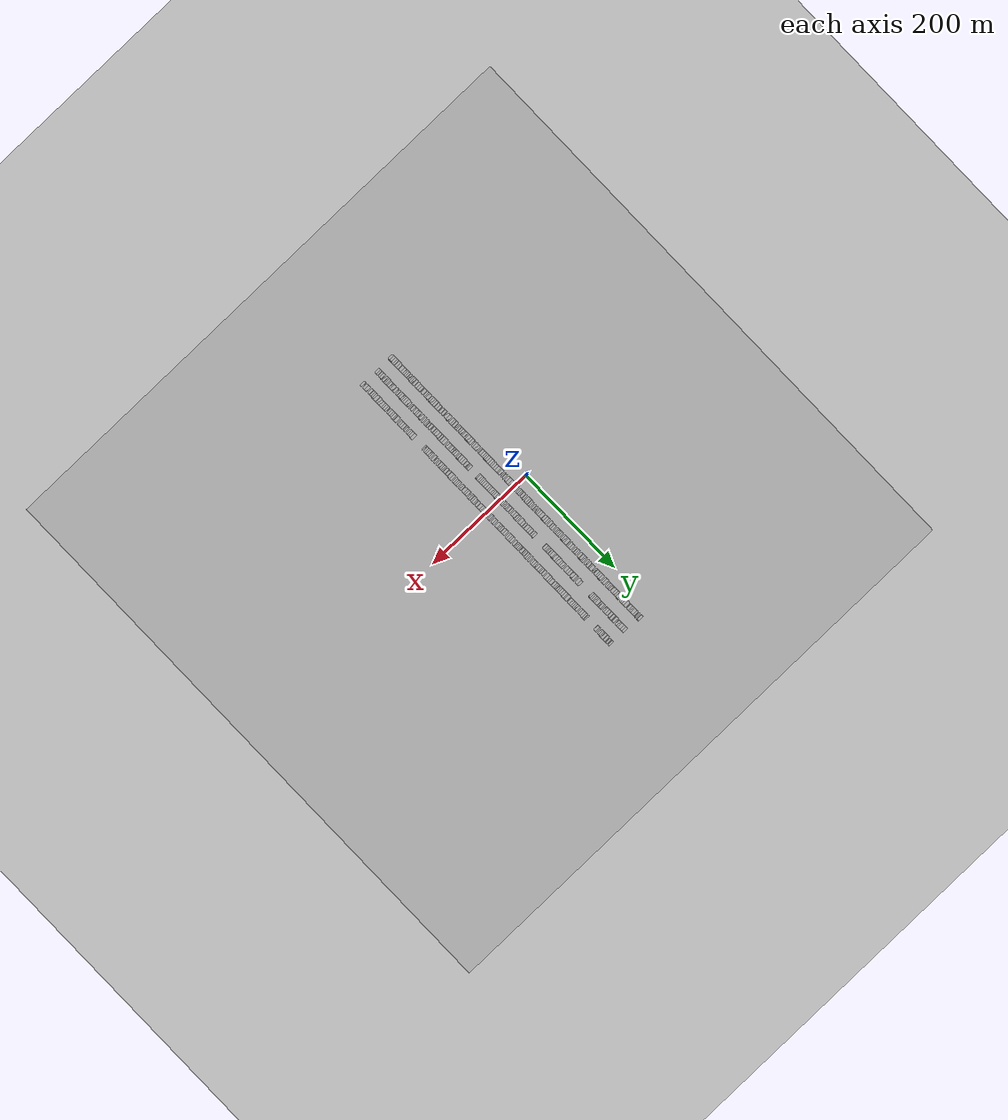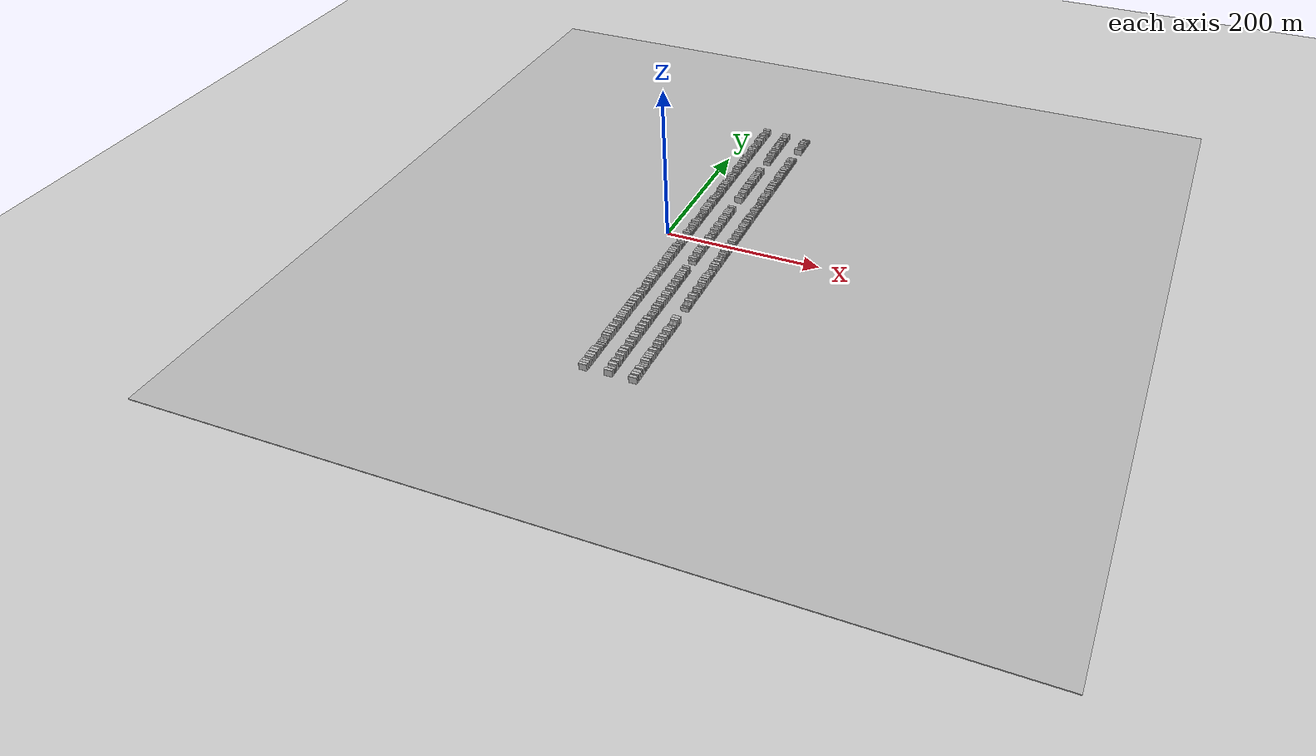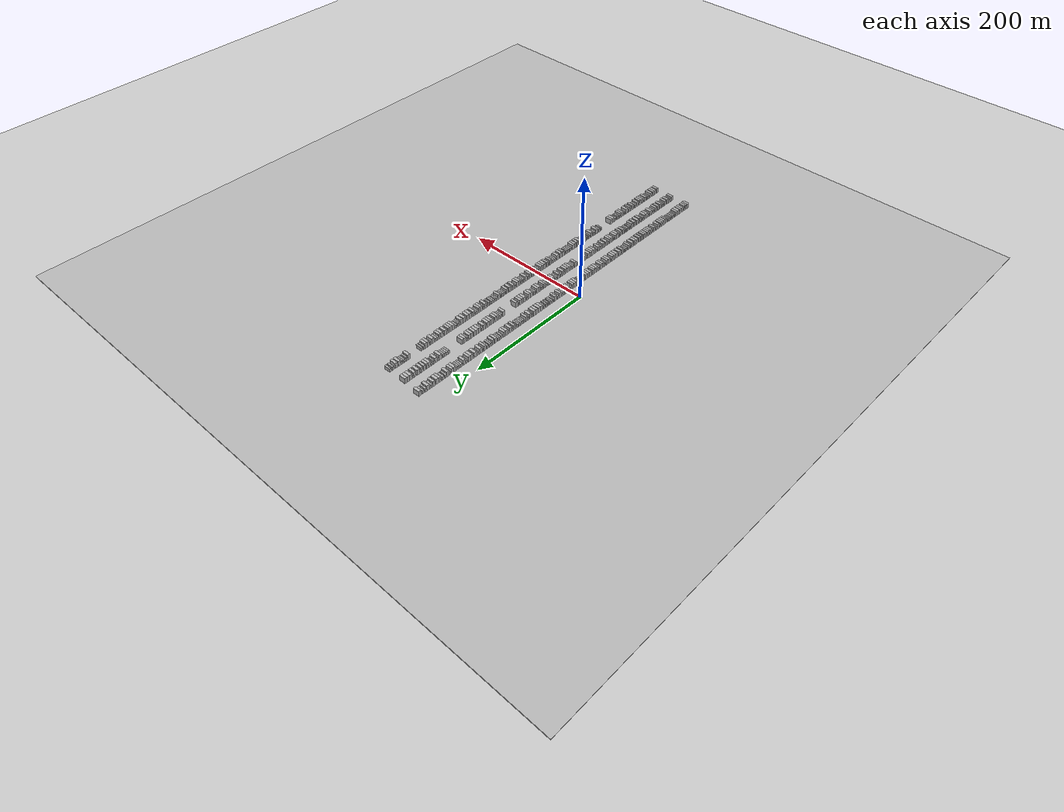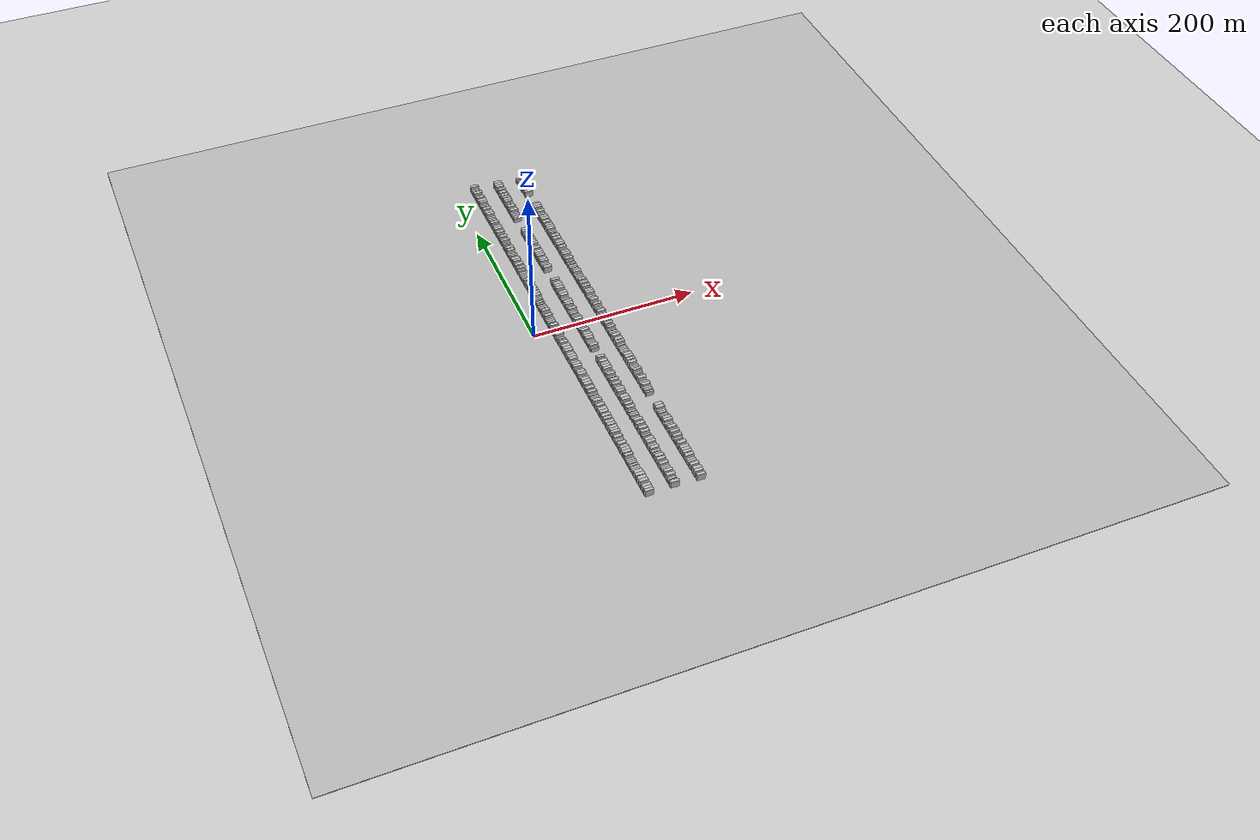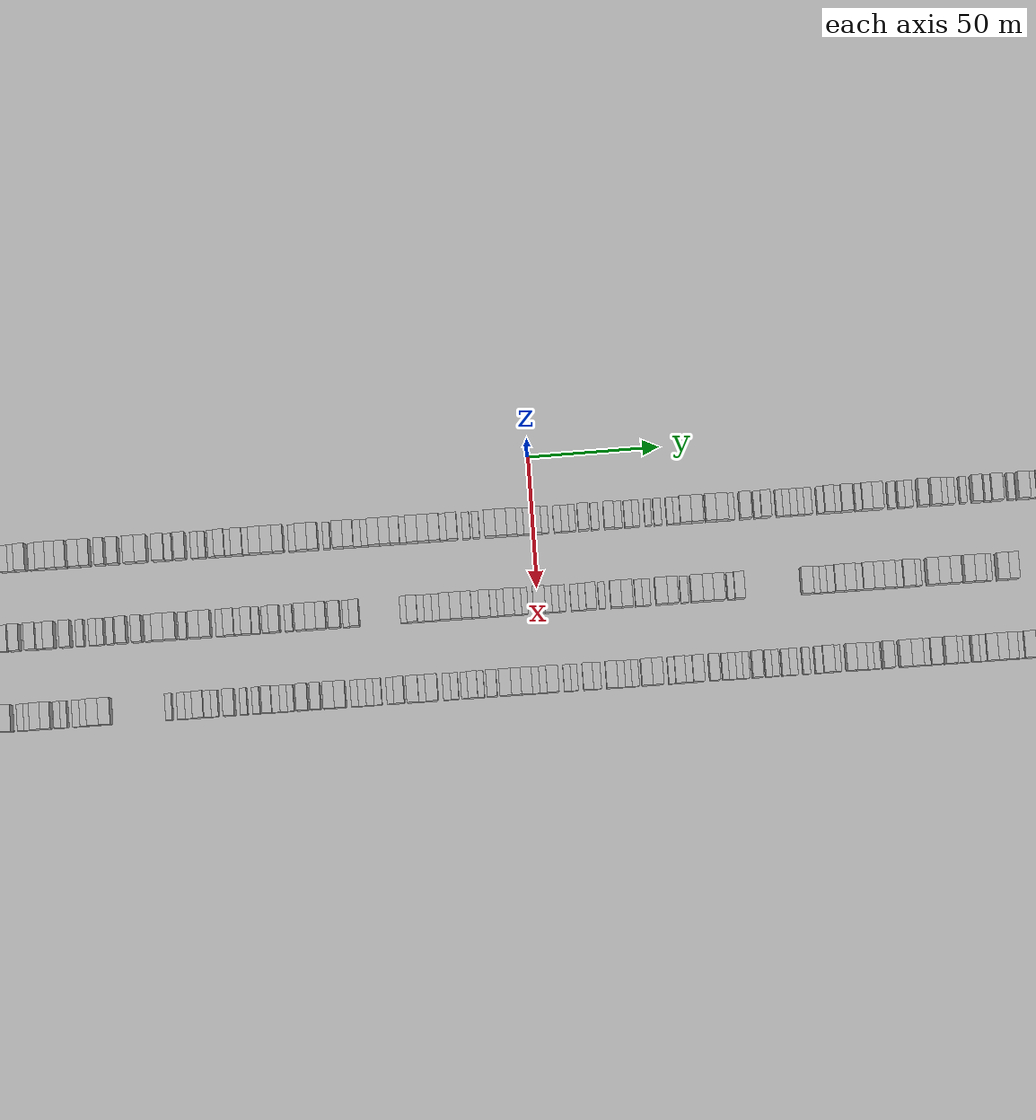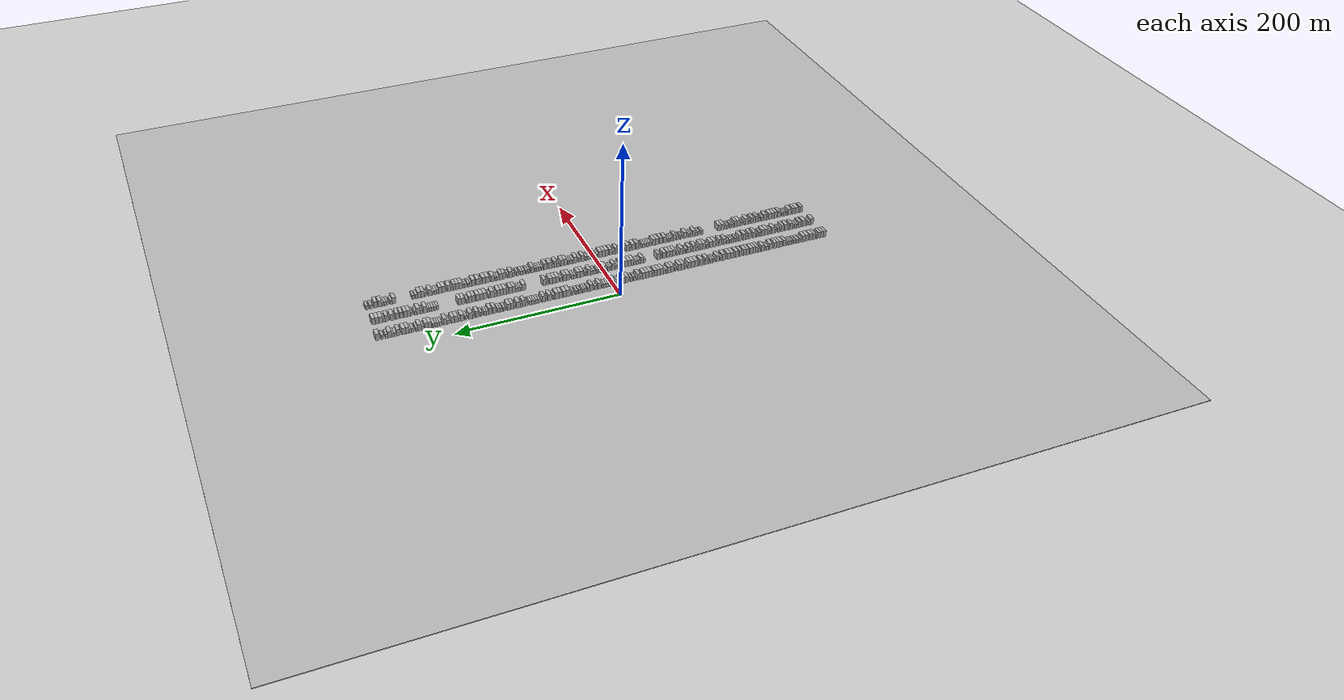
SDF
<?xml version="1.0" encoding="utf-8"?>

<sdf version="1.6">

   <world name="default">

      <gui fullscreen="0">

         <camera name="user_camera">

            <pose>-15 0 4.57585 0 0 0</pose>

            <view_controller>orbit</view_controller>

         </camera>

      </gui>

      <scene>

         <sky>

           <clouds>

             <speed>12</speed>

           </clouds>

         </sky>

         <ambient>0.4 0.4 0.4 1</ambient>

         <background>0.7 0.7 0.7 1</background>

         <shadows>1</shadows>

      </scene>

      <gravity>0 0 -9.8066</gravity>

      <magnetic_field>6e-06 2.3e-05 -4.2e-05</magnetic_field>

      <physics default="0" name="default_physics" type="ode">

         <ode>

            <solver>

               <type>quick</type>

               <iters>10</iters>

               <sor>1.0</sor>

               <use_dynamic_moi_rescaling>0</use_dynamic_moi_rescaling>

            </solver>

            <constraints>

               <cfm>0</cfm>

               <erp>0.2</erp>

               <contact_max_correcting_vel>100</contact_max_correcting_vel>

               <contact_surface_layer>0.001</contact_surface_layer>

            </constraints>

         </ode>

         <max_step_size>0.004</max_step_size>

         <real_time_factor>1</real_time_factor>

         <real_time_update_rate>250</real_time_update_rate>

      </physics>

      <light name="sun" type="directional">

         <cast_shadows>1</cast_shadows>

         <pose>0 0 10 0 0 0</pose>

         <diffuse>0.8 0.8 0.8 1</diffuse>

         <specular>0.2 0.2 0.2 1</specular>

         <attenuation>

            <range>1000</range>

            <constant>0.9</constant>

            <linear>0.01</linear>

            <quadratic>0.001</quadratic>

         </attenuation>

         <direction>-0.5 0.1 -0.9</direction>

      </light>

      <include>

         <name>ground_plane_1</name>

         <uri>model://HANNAS_ground_plane</uri>

         <pose>0 0 0  0 0 0</pose>

      </include>

      <include>

         <name>ground_plane_2</name>

         <uri>model://HANNAS_ground_plane</uri>

         <pose>100 0 0  0 0 0</pose>

      </include>

      <model name="building_1">

         <static>1</static>

         <pose frame="">25.0000 -278.0907 0 0.000000 0.000000 0.000000</pose>

         <link name="link">

            <pose frame="">0 0 4.50 0 0 0</pose>

            <collision name="collision">

               <geometry>

                  <box>

                     <size>10.0000 3.8187 9.0000</size>

                  </box>

               </geometry>

               <max_contacts>10</max_contacts>

               <surface>

                  <contact>

                     <ode/>

                  </contact>

                  <bounce/>

                  <friction>

                     <torsional>

                        <ode/>

                     </torsional>

                     <ode/>

                  </friction>

               </surface>

            </collision>

            <visual name="visual">

               <cast_shadows>0</cast_shadows>

               <geometry>

                  <box>

                     <size>10.0000 3.8187 9.0000</size>

                  </box>

               </geometry>

               <material>

                  <script>

                     <uri>model://HANNAS_wall/materials/scripts</uri>

                     <uri>model://HANNAS_wall/materials/textures</uri>

                     <name>vrc/HANNAS_wall</name>

                  </script>

               </material>

            </visual>

            <self_collide>0</self_collide>

            <enable_wind>0</enable_wind>

            <kinematic>0</kinematic>

         </link>

      </model>

      <model name="building_2">

         <static>1</static>

         <pose frame="">25.0000 -274.2839 0 0.000000 0.000000 0.000000</pose>

         <link name="link">

            <pose frame="">0 0 4.50 0 0 0</pose>

            <collision name="collision">

               <geometry>

                  <box>

                     <size>10.0000 3.7948 9.0000</size>

                  </box>

               </geometry>

               <max_contacts>10</max_contacts>

               <surface>

                  <contact>

                     <ode/>

                  </contact>

                  <bounce/>

                  <friction>

                     <torsional>

                        <ode/>

                     </torsional>

                     <ode/>

                  </friction>

               </surface>

            </collision>

            <visual name="visual">

               <cast_shadows>0</cast_shadows>

               <geometry>

                  <box>

                     <size>10.0000 3.7948 9.0000</size>

                  </box>

               </geometry>

               <material>

                  <script>

                     <uri>model://HANNAS_wall/materials/scripts</uri>

                     <uri>model://HANNAS_wall/materials/textures</uri>

                     <name>vrc/HANNAS_wall</name>

                  </script>

               </material>

            </visual>

            <self_collide>0</self_collide>

            <enable_wind>0</enable_wind>

            <kinematic>0</kinematic>

         </link>

      </model>

      <model name="building_3">

         <static>1</static>

         <pose frame="">25.0000 -270.5470 0 0.000000 0.000000 0.000000</pose>

         <link name="link">

            <pose frame="">0 0 4.50 0 0 0</pose>

            <collision name="collision">

               <geometry>

                  <box>

                     <size>10.0000 3.6789 9.0000</size>

                  </box>

               </geometry>

               <max_contacts>10</max_contacts>

               <surface>

                  <contact>

                     <ode/>

                  </contact>

                  <bounce/>

                  <friction>

                     <torsional>

                        <ode/>

                     </torsional>

                     <ode/>

                  </friction>

               </surface>

            </collision>

            <visual name="visual">

               <cast_shadows>0</cast_shadows>

               <geometry>

                  <box>

                     <size>10.0000 3.6789 9.0000</size>

                  </box>

               </geometry>

               <material>

                  <script>

                     <uri>model://HANNAS_wall/materials/scripts</uri>

                     <uri>model://HANNAS_wall/materials/textures</uri>

                     <name>vrc/HANNAS_wall</name>

                  </script>

               </material>

            </visual>

            <self_collide>0</self_collide>

            <enable_wind>0</enable_wind>

            <kinematic>0</kinematic>

         </link>

      </model>

      <model name="building_4">

         <static>1</static>

         <pose frame="">25.0000 -267.4620 0 0.000000 0.000000 0.000000</pose>

         <link name="link">

            <pose frame="">0 0 3.00 0 0 0</pose>

            <collision name="collision">

               <geometry>

                  <box>

                     <size>10.0000 2.4911 6.0000</size>

                  </box>

               </geometry>

               <max_contacts>10</max_contacts>

               <surface>

                  <contact>

                     <ode/>

                  </contact>

                  <bounce/>

                  <friction>

                     <torsional>

                        <ode/>

                     </torsional>

                     <ode/>

                  </friction>

               </surface>

            </collision>

            <visual name="visual">

               <cast_shadows>0</cast_shadows>

               <geometry>

                  <box>

                     <size>10.0000 2.4911 6.0000</size>

                  </box>

               </geometry>

               <material>

                  <script>

                     <uri>model://HANNAS_wall/materials/scripts</uri>

                     <uri>model://HANNAS_wall/materials/textures</uri>

                     <name>vrc/HANNAS_wall</name>

                  </script>

               </material>

            </visual>

            <self_collide>0</self_collide>

            <enable_wind>0</enable_wind>

            <kinematic>0</kinematic>

         </link>

      </model>

      <model name="building_5">

         <static>1</static>

         <pose frame="">25.0000 -263.2057 0 0.000000 0.000000 0.000000</pose>

         <link name="link">

            <pose frame="">0 0 4.50 0 0 0</pose>

            <collision name="collision">

               <geometry>

                  <box>

                     <size>10.0000 4.0216 9.0000</size>

                  </box>

               </geometry>

               <max_contacts>10</max_contacts>

               <surface>

                  <contact>

                     <ode/>

                  </contact>

                  <bounce/>

                  <friction>

                     <torsional>

                        <ode/>

                     </torsional>

                     <ode/>

                  </friction>

               </surface>

            </collision>

            <visual name="visual">

               <cast_shadows>0</cast_shadows>

               <geometry>

                  <box>

                     <size>10.0000 4.0216 9.0000</size>

                  </box>

               </geometry>

               <material>

                  <script>

                     <uri>model://HANNAS_wall/materials/scripts</uri>

                     <uri>model://HANNAS_wall/materials/textures</uri>

                     <name>vrc/HANNAS_wall</name>

                  </script>

               </material>

            </visual>

            <self_collide>0</self_collide>

            <enable_wind>0</enable_wind>

            <kinematic>0</kinematic>

         </link>

      </model>

      <model name="building_6">

         <static>1</static>

         <pose frame="">25.0000 -258.9625 0 0.000000 0.000000 0.000000</pose>

         <link name="link">

            <pose frame="">0 0 4.50 0 0 0</pose>

            <collision name="collision">

               <geometry>

                  <box>

                     <size>10.0000 4.4649 9.0000</size>

                  </box>

               </geometry>

               <max_contacts>10</max_contacts>

               <surface>

                  <contact>

                     <ode/>

                  </contact>

                  <bounce/>

                  <friction>

                     <torsional>

                        <ode/>

                     </torsional>

                     <ode/>

                  </friction>

               </surface>

            </collision>

            <visual name="visual">

               <cast_shadows>0</cast_shadows>

               <geometry>

                  <box>

                     <size>10.0000 4.4649 9.0000</size>

                  </box>

               </geometry>

               <material>

                  <script>

                     <uri>model://HANNAS_wall/materials/scripts</uri>

                     <uri>model://HANNAS_wall/materials/textures</uri>

                     <name>vrc/HANNAS_wall</name>

                  </script>

               </material>

            </visual>

            <self_collide>0</self_collide>

            <enable_wind>0</enable_wind>

            <kinematic>0</kinematic>

         </link>

      </model>

      <model name="building_7">

         <static>1</static>

         <pose frame="">25.0000 -253.5668 0 0.000000 0.000000 0.000000</pose>

         <link name="link">

            <pose frame="">0 0 4.50 0 0 0</pose>

            <collision name="collision">

               <geometry>

                  <box>

                     <size>10.0000 4.3265 9.0000</size>

                  </box>

               </geometry>

               <max_contacts>10</max_contacts>

               <surface>

                  <contact>

                     <ode/>

                  </contact>

                  <bounce/>

                  <friction>

                     <torsional>

                        <ode/>

                     </torsional>

                     <ode/>

                  </friction>

               </surface>

            </collision>

            <visual name="visual">

               <cast_shadows>0</cast_shadows>

               <geometry>

                  <box>

                     <size>10.0000 4.3265 9.0000</size>

                  </box>

               </geometry>

               <material>

                  <script>

                     <uri>model://HANNAS_wall/materials/scripts</uri>

                     <uri>model://HANNAS_wall/materials/textures</uri>

                     <name>vrc/HANNAS_wall</name>

                  </script>

               </material>

            </visual>

            <self_collide>0</self_collide>

            <enable_wind>0</enable_wind>

            <kinematic>0</kinematic>

         </link>

      </model>

      <model name="building_8">

         <static>1</static>

         <pose frame="">25.0000 -249.2232 0 0.000000 0.000000 0.000000</pose>

         <link name="link">

            <pose frame="">0 0 4.50 0 0 0</pose>

            <collision name="collision">

               <geometry>

                  <box>

                     <size>10.0000 4.3608 9.0000</size>

                  </box>

               </geometry>

               <max_contacts>10</max_contacts>

               <surface>

                  <contact>

                     <ode/>

                  </contact>

                  <bounce/>

                  <friction>

                     <torsional>

                        <ode/>

                     </torsional>

                     <ode/>

                  </friction>

               </surface>

            </collision>

            <visual name="visual">

               <cast_shadows>0</cast_shadows>

               <geometry>

                  <box>

                     <size>10.0000 4.3608 9.0000</size>

                  </box>

               </geometry>

               <material>

                  <script>

                     <uri>model://HANNAS_wall/materials/scripts</uri>

                     <uri>model://HANNAS_wall/materials/textures</uri>

                     <name>vrc/HANNAS_wall</name>

                  </script>

               </material>

            </visual>

            <self_collide>0</self_collide>

            <enable_wind>0</enable_wind>

            <kinematic>0</kinematic>

         </link>

      </model>

      <model name="building_9">

         <static>1</static>

         <pose frame="">25.0000 -245.7156 0 0.000000 0.000000 0.000000</pose>

         <link name="link">

            <pose frame="">0 0 3.00 0 0 0</pose>

            <collision name="collision">

               <geometry>

                  <box>

                     <size>10.0000 2.6543 6.0000</size>

                  </box>

               </geometry>

               <max_contacts>10</max_contacts>

               <surface>

                  <contact>

                     <ode/>

                  </contact>

                  <bounce/>

                  <friction>

                     <torsional>

                        <ode/>

                     </torsional>

                     <ode/>

                  </friction>

               </surface>

            </collision>

            <visual name="visual">

               <cast_shadows>0</cast_shadows>

               <geometry>

                  <box>

                     <size>10.0000 2.6543 6.0000</size>

                  </box>

               </geometry>

               <material>

                  <script>

                     <uri>model://HANNAS_wall/materials/scripts</uri>

                     <uri>model://HANNAS_wall/materials/textures</uri>

                     <name>vrc/HANNAS_wall</name>

                  </script>

               </material>

            </visual>

            <self_collide>0</self_collide>

            <enable_wind>0</enable_wind>

            <kinematic>0</kinematic>

         </link>

      </model>

      <model name="building_10">

         <static>1</static>

         <pose frame="">25.0000 -243.1820 0 0.000000 0.000000 0.000000</pose>

         <link name="link">

            <pose frame="">0 0 3.00 0 0 0</pose>

            <collision name="collision">

               <geometry>

                  <box>

                     <size>10.0000 2.4129 6.0000</size>

                  </box>

               </geometry>

               <max_contacts>10</max_contacts>

               <surface>

                  <contact>

                     <ode/>

                  </contact>

                  <bounce/>

                  <friction>

                     <torsional>

                        <ode/>

                     </torsional>

                     <ode/>

                  </friction>

               </surface>

            </collision>

            <visual name="visual">

               <cast_shadows>0</cast_shadows>

               <geometry>

                  <box>

                     <size>10.0000 2.4129 6.0000</size>

                  </box>

               </geometry>

               <material>

                  <script>

                     <uri>model://HANNAS_wall/materials/scripts</uri>

                     <uri>model://HANNAS_wall/materials/textures</uri>

                     <name>vrc/HANNAS_wall</name>

                  </script>

               </material>

            </visual>

            <self_collide>0</self_collide>

            <enable_wind>0</enable_wind>

            <kinematic>0</kinematic>

         </link>

      </model>

      <model name="building_11">

         <static>1</static>

         <pose frame="">25.0000 -240.4807 0 0.000000 0.000000 0.000000</pose>

         <link name="link">

            <pose frame="">0 0 3.00 0 0 0</pose>

            <collision name="collision">

               <geometry>

                  <box>

                     <size>10.0000 2.9897 6.0000</size>

                  </box>

               </geometry>

               <max_contacts>10</max_contacts>

               <surface>

                  <contact>

                     <ode/>

                  </contact>

                  <bounce/>

                  <friction>

                     <torsional>

                        <ode/>

                     </torsional>

                     <ode/>

                  </friction>

               </surface>

            </collision>

            <visual name="visual">

               <cast_shadows>0</cast_shadows>

               <geometry>

                  <box>

                     <size>10.0000 2.9897 6.0000</size>

                  </box>

               </geometry>

               <material>

                  <script>

                     <uri>model://HANNAS_wall/materials/scripts</uri>

                     <uri>model://HANNAS_wall/materials/textures</uri>

                     <name>vrc/HANNAS_wall</name>

                  </script>

               </material>

            </visual>

            <self_collide>0</self_collide>

            <enable_wind>0</enable_wind>

            <kinematic>0</kinematic>

         </link>

      </model>

      <model name="building_12">

         <static>1</static>

         <pose frame="">25.0000 -236.6400 0 0.000000 0.000000 0.000000</pose>

         <link name="link">

            <pose frame="">0 0 3.00 0 0 0</pose>

            <collision name="collision">

               <geometry>

                  <box>

                     <size>10.0000 2.6918 6.0000</size>

                  </box>

               </geometry>

               <max_contacts>10</max_contacts>

               <surface>

                  <contact>

                     <ode/>

                  </contact>

                  <bounce/>

                  <friction>

                     <torsional>

                        <ode/>

                     </torsional>

                     <ode/>

                  </friction>

               </surface>

            </collision>

            <visual name="visual">

               <cast_shadows>0</cast_shadows>

               <geometry>

                  <box>

                     <size>10.0000 2.6918 6.0000</size>

                  </box>

               </geometry>

               <material>

                  <script>

                     <uri>model://HANNAS_wall/materials/scripts</uri>

                     <uri>model://HANNAS_wall/materials/textures</uri>

                     <name>vrc/HANNAS_wall</name>

                  </script>

               </material>

            </visual>

            <self_collide>0</self_collide>

            <enable_wind>0</enable_wind>

            <kinematic>0</kinematic>

         </link>

      </model>

      <model name="building_13">

         <static>1</static>

         <pose frame="">25.0000 -232.9424 0 0.000000 0.000000 0.000000</pose>

         <link name="link">

            <pose frame="">0 0 3.00 0 0 0</pose>

            <collision name="collision">

               <geometry>

                  <box>

                     <size>10.0000 2.7034 6.0000</size>

                  </box>

               </geometry>

               <max_contacts>10</max_contacts>

               <surface>

                  <contact>

                     <ode/>

                  </contact>

                  <bounce/>

                  <friction>

                     <torsional>

                        <ode/>

                     </torsional>

                     <ode/>

                  </friction>

               </surface>

            </collision>

            <visual name="visual">

               <cast_shadows>0</cast_shadows>

               <geometry>

                  <box>

                     <size>10.0000 2.7034 6.0000</size>

                  </box>

               </geometry>

               <material>

                  <script>

                     <uri>model://HANNAS_wall/materials/scripts</uri>

                     <uri>model://HANNAS_wall/materials/textures</uri>

                     <name>vrc/HANNAS_wall</name>

                  </script>

               </material>

            </visual>

            <self_collide>0</self_collide>

            <enable_wind>0</enable_wind>

            <kinematic>0</kinematic>

         </link>

      </model>

      <model name="building_14">

         <static>1</static>

         <pose frame="">25.0000 -230.3137 0 0.000000 0.000000 0.000000</pose>

         <link name="link">

            <pose frame="">0 0 3.00 0 0 0</pose>

            <collision name="collision">

               <geometry>

                  <box>

                     <size>10.0000 2.5539 6.0000</size>

                  </box>

               </geometry>

               <max_contacts>10</max_contacts>

               <surface>

                  <contact>

                     <ode/>

                  </contact>

                  <bounce/>

                  <friction>

                     <torsional>

                        <ode/>

                     </torsional>

                     <ode/>

                  </friction>

               </surface>

            </collision>

            <visual name="visual">

               <cast_shadows>0</cast_shadows>

               <geometry>

                  <box>

                     <size>10.0000 2.5539 6.0000</size>

                  </box>

               </geometry>

               <material>

                  <script>

                     <uri>model://HANNAS_wall/materials/scripts</uri>

                     <uri>model://HANNAS_wall/materials/textures</uri>

                     <name>vrc/HANNAS_wall</name>

                  </script>

               </material>

            </visual>

            <self_collide>0</self_collide>

            <enable_wind>0</enable_wind>

            <kinematic>0</kinematic>

         </link>

      </model>

      <model name="building_15">

         <static>1</static>

         <pose frame="">25.0000 -227.7758 0 0.000000 0.000000 0.000000</pose>

         <link name="link">

            <pose frame="">0 0 3.00 0 0 0</pose>

            <collision name="collision">

               <geometry>

                  <box>

                     <size>10.0000 2.5219 6.0000</size>

                  </box>

               </geometry>

               <max_contacts>10</max_contacts>

               <surface>

                  <contact>

                     <ode/>

                  </contact>

                  <bounce/>

                  <friction>

                     <torsional>

                        <ode/>

                     </torsional>

                     <ode/>

                  </friction>

               </surface>

            </collision>

            <visual name="visual">

               <cast_shadows>0</cast_shadows>

               <geometry>

                  <box>

                     <size>10.0000 2.5219 6.0000</size>

                  </box>

               </geometry>

               <material>

                  <script>

                     <uri>model://HANNAS_wall/materials/scripts</uri>

                     <uri>model://HANNAS_wall/materials/textures</uri>

                     <name>vrc/HANNAS_wall</name>

                  </script>

               </material>

            </visual>

            <self_collide>0</self_collide>

            <enable_wind>0</enable_wind>

            <kinematic>0</kinematic>

         </link>

      </model>

      <model name="building_16">

         <static>1</static>

         <pose frame="">25.0000 -222.7067 0 0.000000 0.000000 0.000000</pose>

         <link name="link">

            <pose frame="">0 0 4.50 0 0 0</pose>

            <collision name="collision">

               <geometry>

                  <box>

                     <size>10.0000 3.6162 9.0000</size>

                  </box>

               </geometry>

               <max_contacts>10</max_contacts>

               <surface>

                  <contact>

                     <ode/>

                  </contact>

                  <bounce/>

                  <friction>

                     <torsional>

                        <ode/>

                     </torsional>

                     <ode/>

                  </friction>

               </surface>

            </collision>

            <visual name="visual">

               <cast_shadows>0</cast_shadows>

               <geometry>

                  <box>

                     <size>10.0000 3.6162 9.0000</size>

                  </box>

               </geometry>

               <material>

                  <script>

                     <uri>model://HANNAS_wall/materials/scripts</uri>

                     <uri>model://HANNAS_wall/materials/textures</uri>

                     <name>vrc/HANNAS_wall</name>

                  </script>

               </material>

            </visual>

            <self_collide>0</self_collide>

            <enable_wind>0</enable_wind>

            <kinematic>0</kinematic>

         </link>

      </model>

      <model name="building_17">

         <static>1</static>

         <pose frame="">25.0000 -217.8327 0 0.000000 0.000000 0.000000</pose>

         <link name="link">

            <pose frame="">0 0 4.50 0 0 0</pose>

            <collision name="collision">

               <geometry>

                  <box>

                     <size>10.0000 4.1318 9.0000</size>

                  </box>

               </geometry>

               <max_contacts>10</max_contacts>

               <surface>

                  <contact>

                     <ode/>

                  </contact>

                  <bounce/>

                  <friction>

                     <torsional>

                        <ode/>

                     </torsional>

                     <ode/>

                  </friction>

               </surface>

            </collision>

            <visual name="visual">

               <cast_shadows>0</cast_shadows>

               <geometry>

                  <box>

                     <size>10.0000 4.1318 9.0000</size>

                  </box>

               </geometry>

               <material>

                  <script>

                     <uri>model://HANNAS_wall/materials/scripts</uri>

                     <uri>model://HANNAS_wall/materials/textures</uri>

                     <name>vrc/HANNAS_wall</name>

                  </script>

               </material>

            </visual>

            <self_collide>0</self_collide>

            <enable_wind>0</enable_wind>

            <kinematic>0</kinematic>

         </link>

      </model>

      <model name="building_18">

         <static>1</static>

         <pose frame="">25.0000 -213.8320 0 0.000000 0.000000 0.000000</pose>

         <link name="link">

            <pose frame="">0 0 4.50 0 0 0</pose>

            <collision name="collision">

               <geometry>

                  <box>

                     <size>10.0000 3.8697 9.0000</size>

                  </box>

               </geometry>

               <max_contacts>10</max_contacts>

               <surface>

                  <contact>

                     <ode/>

                  </contact>

                  <bounce/>

                  <friction>

                     <torsional>

                        <ode/>

                     </torsional>

                     <ode/>

                  </friction>

               </surface>

            </collision>

            <visual name="visual">

               <cast_shadows>0</cast_shadows>

               <geometry>

                  <box>

                     <size>10.0000 3.8697 9.0000</size>

                  </box>

               </geometry>

               <material>

                  <script>

                     <uri>model://HANNAS_wall/materials/scripts</uri>

                     <uri>model://HANNAS_wall/materials/textures</uri>

                     <name>vrc/HANNAS_wall</name>

                  </script>

               </material>

            </visual>

            <self_collide>0</self_collide>

            <enable_wind>0</enable_wind>

            <kinematic>0</kinematic>

         </link>

      </model>

      <model name="building_19">

         <static>1</static>

         <pose frame="">25.0000 -209.9862 0 0.000000 0.000000 0.000000</pose>

         <link name="link">

            <pose frame="">0 0 4.50 0 0 0</pose>

            <collision name="collision">

               <geometry>

                  <box>

                     <size>10.0000 3.8218 9.0000</size>

                  </box>

               </geometry>

               <max_contacts>10</max_contacts>

               <surface>

                  <contact>

                     <ode/>

                  </contact>

                  <bounce/>

                  <friction>

                     <torsional>

                        <ode/>

                     </torsional>

                     <ode/>

                  </friction>

               </surface>

            </collision>

            <visual name="visual">

               <cast_shadows>0</cast_shadows>

               <geometry>

                  <box>

                     <size>10.0000 3.8218 9.0000</size>

                  </box>

               </geometry>

               <material>

                  <script>

                     <uri>model://HANNAS_wall/materials/scripts</uri>

                     <uri>model://HANNAS_wall/materials/textures</uri>

                     <name>vrc/HANNAS_wall</name>

                  </script>

               </material>

            </visual>

            <self_collide>0</self_collide>

            <enable_wind>0</enable_wind>

            <kinematic>0</kinematic>

         </link>

      </model>

      <model name="building_20">

         <static>1</static>

         <pose frame="">25.0000 -203.9006 0 0.000000 0.000000 0.000000</pose>

         <link name="link">

            <pose frame="">0 0 4.50 0 0 0</pose>

            <collision name="collision">

               <geometry>

                  <box>

                     <size>10.0000 4.3495 9.0000</size>

                  </box>

               </geometry>

               <max_contacts>10</max_contacts>

               <surface>

                  <contact>

                     <ode/>

                  </contact>

                  <bounce/>

                  <friction>

                     <torsional>

                        <ode/>

                     </torsional>

                     <ode/>

                  </friction>

               </surface>

            </collision>

            <visual name="visual">

               <cast_shadows>0</cast_shadows>

               <geometry>

                  <box>

                     <size>10.0000 4.3495 9.0000</size>

                  </box>

               </geometry>

               <material>

                  <script>

                     <uri>model://HANNAS_wall/materials/scripts</uri>

                     <uri>model://HANNAS_wall/materials/textures</uri>

                     <name>vrc/HANNAS_wall</name>

                  </script>

               </material>

            </visual>

            <self_collide>0</self_collide>

            <enable_wind>0</enable_wind>

            <kinematic>0</kinematic>

         </link>

      </model>

      <model name="building_21">

         <static>1</static>

         <pose frame="">25.0000 -199.3027 0 0.000000 0.000000 0.000000</pose>

         <link name="link">

            <pose frame="">0 0 3.00 0 0 0</pose>

            <collision name="collision">

               <geometry>

                  <box>

                     <size>10.0000 2.8463 6.0000</size>

                  </box>

               </geometry>

               <max_contacts>10</max_contacts>

               <surface>

                  <contact>

                     <ode/>

                  </contact>

                  <bounce/>

                  <friction>

                     <torsional>

                        <ode/>

                     </torsional>

                     <ode/>

                  </friction>

               </surface>

            </collision>

            <visual name="visual">

               <cast_shadows>0</cast_shadows>

               <geometry>

                  <box>

                     <size>10.0000 2.8463 6.0000</size>

                  </box>

               </geometry>

               <material>

                  <script>

                     <uri>model://HANNAS_wall/materials/scripts</uri>

                     <uri>model://HANNAS_wall/materials/textures</uri>

                     <name>vrc/HANNAS_wall</name>

                  </script>

               </material>

            </visual>

            <self_collide>0</self_collide>

            <enable_wind>0</enable_wind>

            <kinematic>0</kinematic>

         </link>

      </model>

      <model name="building_22">

         <static>1</static>

         <pose frame="">25.0000 -196.5286 0 0.000000 0.000000 0.000000</pose>

         <link name="link">

            <pose frame="">0 0 3.00 0 0 0</pose>

            <collision name="collision">

               <geometry>

                  <box>

                     <size>10.0000 2.7019 6.0000</size>

                  </box>

               </geometry>

               <max_contacts>10</max_contacts>

               <surface>

                  <contact>

                     <ode/>

                  </contact>

                  <bounce/>

                  <friction>

                     <torsional>

                        <ode/>

                     </torsional>

                     <ode/>

                  </friction>

               </surface>

            </collision>

            <visual name="visual">

               <cast_shadows>0</cast_shadows>

               <geometry>

                  <box>

                     <size>10.0000 2.7019 6.0000</size>

                  </box>

               </geometry>

               <material>

                  <script>

                     <uri>model://HANNAS_wall/materials/scripts</uri>

                     <uri>model://HANNAS_wall/materials/textures</uri>

                     <name>vrc/HANNAS_wall</name>

                  </script>

               </material>

            </visual>

            <self_collide>0</self_collide>

            <enable_wind>0</enable_wind>

            <kinematic>0</kinematic>

         </link>

      </model>

      <model name="building_23">

         <static>1</static>

         <pose frame="">25.0000 -193.1107 0 0.000000 0.000000 0.000000</pose>

         <link name="link">

            <pose frame="">0 0 4.50 0 0 0</pose>

            <collision name="collision">

               <geometry>

                  <box>

                     <size>10.0000 4.1340 9.0000</size>

                  </box>

               </geometry>

               <max_contacts>10</max_contacts>

               <surface>

                  <contact>

                     <ode/>

                  </contact>

                  <bounce/>

                  <friction>

                     <torsional>

                        <ode/>

                     </torsional>

                     <ode/>

                  </friction>

               </surface>

            </collision>

            <visual name="visual">

               <cast_shadows>0</cast_shadows>

               <geometry>

                  <box>

                     <size>10.0000 4.1340 9.0000</size>

                  </box>

               </geometry>

               <material>

                  <script>

                     <uri>model://HANNAS_wall/materials/scripts</uri>

                     <uri>model://HANNAS_wall/materials/textures</uri>

                     <name>vrc/HANNAS_wall</name>

                  </script>

               </material>

            </visual>

            <self_collide>0</self_collide>

            <enable_wind>0</enable_wind>

            <kinematic>0</kinematic>

         </link>

      </model>

      <model name="building_24">

         <static>1</static>

         <pose frame="">25.0000 -188.5911 0 0.000000 0.000000 0.000000</pose>

         <link name="link">

            <pose frame="">0 0 3.00 0 0 0</pose>

            <collision name="collision">

               <geometry>

                  <box>

                     <size>10.0000 2.9050 6.0000</size>

                  </box>

               </geometry>

               <max_contacts>10</max_contacts>

               <surface>

                  <contact>

                     <ode/>

                  </contact>

                  <bounce/>

                  <friction>

                     <torsional>

                        <ode/>

                     </torsional>

                     <ode/>

                  </friction>

               </surface>

            </collision>

            <visual name="visual">

               <cast_shadows>0</cast_shadows>

               <geometry>

                  <box>

                     <size>10.0000 2.9050 6.0000</size>

                  </box>

               </geometry>

               <material>

                  <script>

                     <uri>model://HANNAS_wall/materials/scripts</uri>

                     <uri>model://HANNAS_wall/materials/textures</uri>

                     <name>vrc/HANNAS_wall</name>

                  </script>

               </material>

            </visual>

            <self_collide>0</self_collide>

            <enable_wind>0</enable_wind>

            <kinematic>0</kinematic>

         </link>

      </model>

      <model name="building_25">

         <static>1</static>

         <pose frame="">25.0000 -185.2728 0 0.000000 0.000000 0.000000</pose>

         <link name="link">

            <pose frame="">0 0 4.50 0 0 0</pose>

            <collision name="collision">

               <geometry>

                  <box>

                     <size>10.0000 3.7317 9.0000</size>

                  </box>

               </geometry>

               <max_contacts>10</max_contacts>

               <surface>

                  <contact>

                     <ode/>

                  </contact>

                  <bounce/>

                  <friction>

                     <torsional>

                        <ode/>

                     </torsional>

                     <ode/>

                  </friction>

               </surface>

            </collision>

            <visual name="visual">

               <cast_shadows>0</cast_shadows>

               <geometry>

                  <box>

                     <size>10.0000 3.7317 9.0000</size>

                  </box>

               </geometry>

               <material>

                  <script>

                     <uri>model://HANNAS_wall/materials/scripts</uri>

                     <uri>model://HANNAS_wall/materials/textures</uri>

                     <name>vrc/HANNAS_wall</name>

                  </script>

               </material>

            </visual>

            <self_collide>0</self_collide>

            <enable_wind>0</enable_wind>

            <kinematic>0</kinematic>

         </link>

      </model>

      <model name="building_26">

         <static>1</static>

         <pose frame="">25.0000 -181.6056 0 0.000000 0.000000 0.000000</pose>

         <link name="link">

            <pose frame="">0 0 4.50 0 0 0</pose>

            <collision name="collision">

               <geometry>

                  <box>

                     <size>10.0000 3.6027 9.0000</size>

                  </box>

               </geometry>

               <max_contacts>10</max_contacts>

               <surface>

                  <contact>

                     <ode/>

                  </contact>

                  <bounce/>

                  <friction>

                     <torsional>

                        <ode/>

                     </torsional>

                     <ode/>

                  </friction>

               </surface>

            </collision>

            <visual name="visual">

               <cast_shadows>0</cast_shadows>

               <geometry>

                  <box>

                     <size>10.0000 3.6027 9.0000</size>

                  </box>

               </geometry>

               <material>

                  <script>

                     <uri>model://HANNAS_wall/materials/scripts</uri>

                     <uri>model://HANNAS_wall/materials/textures</uri>

                     <name>vrc/HANNAS_wall</name>

                  </script>

               </material>

            </visual>

            <self_collide>0</self_collide>

            <enable_wind>0</enable_wind>

            <kinematic>0</kinematic>

         </link>

      </model>

      <model name="building_27">

         <static>1</static>

         <pose frame="">25.0000 -177.8339 0 0.000000 0.000000 0.000000</pose>

         <link name="link">

            <pose frame="">0 0 4.50 0 0 0</pose>

            <collision name="collision">

               <geometry>

                  <box>

                     <size>10.0000 3.9406 9.0000</size>

                  </box>

               </geometry>

               <max_contacts>10</max_contacts>

               <surface>

                  <contact>

                     <ode/>

                  </contact>

                  <bounce/>

                  <friction>

                     <torsional>

                        <ode/>

                     </torsional>

                     <ode/>

                  </friction>

               </surface>

            </collision>

            <visual name="visual">

               <cast_shadows>0</cast_shadows>

               <geometry>

                  <box>

                     <size>10.0000 3.9406 9.0000</size>

                  </box>

               </geometry>

               <material>

                  <script>

                     <uri>model://HANNAS_wall/materials/scripts</uri>

                     <uri>model://HANNAS_wall/materials/textures</uri>

                     <name>vrc/HANNAS_wall</name>

                  </script>

               </material>

            </visual>

            <self_collide>0</self_collide>

            <enable_wind>0</enable_wind>

            <kinematic>0</kinematic>

         </link>

      </model>

      <model name="building_28">

         <static>1</static>

         <pose frame="">25.0000 -172.8596 0 0.000000 0.000000 0.000000</pose>

         <link name="link">

            <pose frame="">0 0 4.50 0 0 0</pose>

            <collision name="collision">

               <geometry>

                  <box>

                     <size>10.0000 4.0081 9.0000</size>

                  </box>

               </geometry>

               <max_contacts>10</max_contacts>

               <surface>

                  <contact>

                     <ode/>

                  </contact>

                  <bounce/>

                  <friction>

                     <torsional>

                        <ode/>

                     </torsional>

                     <ode/>

                  </friction>

               </surface>

            </collision>

            <visual name="visual">

               <cast_shadows>0</cast_shadows>

               <geometry>

                  <box>

                     <size>10.0000 4.0081 9.0000</size>

                  </box>

               </geometry>

               <material>

                  <script>

                     <uri>model://HANNAS_wall/materials/scripts</uri>

                     <uri>model://HANNAS_wall/materials/textures</uri>

                     <name>vrc/HANNAS_wall</name>

                  </script>

               </material>

            </visual>

            <self_collide>0</self_collide>

            <enable_wind>0</enable_wind>

            <kinematic>0</kinematic>

         </link>

      </model>

      <model name="building_29">

         <static>1</static>

         <pose frame="">25.0000 -168.9246 0 0.000000 0.000000 0.000000</pose>

         <link name="link">

            <pose frame="">0 0 4.50 0 0 0</pose>

            <collision name="collision">

               <geometry>

                  <box>

                     <size>10.0000 3.8620 9.0000</size>

                  </box>

               </geometry>

               <max_contacts>10</max_contacts>

               <surface>

                  <contact>

                     <ode/>

                  </contact>

                  <bounce/>

                  <friction>

                     <torsional>

                        <ode/>

                     </torsional>

                     <ode/>

                  </friction>

               </surface>

            </collision>

            <visual name="visual">

               <cast_shadows>0</cast_shadows>

               <geometry>

                  <box>

                     <size>10.0000 3.8620 9.0000</size>

                  </box>

               </geometry>

               <material>

                  <script>

                     <uri>model://HANNAS_wall/materials/scripts</uri>

                     <uri>model://HANNAS_wall/materials/textures</uri>

                     <name>vrc/HANNAS_wall</name>

                  </script>

               </material>

            </visual>

            <self_collide>0</self_collide>

            <enable_wind>0</enable_wind>

            <kinematic>0</kinematic>

         </link>

      </model>

      <model name="building_30">

         <static>1</static>

         <pose frame="">25.0000 -163.1780 0 0.000000 0.000000 0.000000</pose>

         <link name="link">

            <pose frame="">0 0 4.50 0 0 0</pose>

            <collision name="collision">

               <geometry>

                  <box>

                     <size>10.0000 3.6312 9.0000</size>

                  </box>

               </geometry>

               <max_contacts>10</max_contacts>

               <surface>

                  <contact>

                     <ode/>

                  </contact>

                  <bounce/>

                  <friction>

                     <torsional>

                        <ode/>

                     </torsional>

                     <ode/>

                  </friction>

               </surface>

            </collision>

            <visual name="visual">

               <cast_shadows>0</cast_shadows>

               <geometry>

                  <box>

                     <size>10.0000 3.6312 9.0000</size>

                  </box>

               </geometry>

               <material>

                  <script>

                     <uri>model://HANNAS_wall/materials/scripts</uri>

                     <uri>model://HANNAS_wall/materials/textures</uri>

                     <name>vrc/HANNAS_wall</name>

                  </script>

               </material>

            </visual>

            <self_collide>0</self_collide>

            <enable_wind>0</enable_wind>

            <kinematic>0</kinematic>

         </link>

      </model>

      <model name="building_31">

         <static>1</static>

         <pose frame="">25.0000 -158.2871 0 0.000000 0.000000 0.000000</pose>

         <link name="link">

            <pose frame="">0 0 4.50 0 0 0</pose>

            <collision name="collision">

               <geometry>

                  <box>

                     <size>10.0000 4.1505 9.0000</size>

                  </box>

               </geometry>

               <max_contacts>10</max_contacts>

               <surface>

                  <contact>

                     <ode/>

                  </contact>

                  <bounce/>

                  <friction>

                     <torsional>

                        <ode/>

                     </torsional>

                     <ode/>

                  </friction>

               </surface>

            </collision>

            <visual name="visual">

               <cast_shadows>0</cast_shadows>

               <geometry>

                  <box>

                     <size>10.0000 4.1505 9.0000</size>

                  </box>

               </geometry>

               <material>

                  <script>

                     <uri>model://HANNAS_wall/materials/scripts</uri>

                     <uri>model://HANNAS_wall/materials/textures</uri>

                     <name>vrc/HANNAS_wall</name>

                  </script>

               </material>

            </visual>

            <self_collide>0</self_collide>

            <enable_wind>0</enable_wind>

            <kinematic>0</kinematic>

         </link>

      </model>

      <model name="building_32">

         <static>1</static>

         <pose frame="">25.0000 -152.0223 0 0.000000 0.000000 0.000000</pose>

         <link name="link">

            <pose frame="">0 0 4.50 0 0 0</pose>

            <collision name="collision">

               <geometry>

                  <box>

                     <size>10.0000 4.3792 9.0000</size>

                  </box>

               </geometry>

               <max_contacts>10</max_contacts>

               <surface>

                  <contact>

                     <ode/>

                  </contact>

                  <bounce/>

                  <friction>

                     <torsional>

                        <ode/>

                     </torsional>

                     <ode/>

                  </friction>

               </surface>

            </collision>

            <visual name="visual">

               <cast_shadows>0</cast_shadows>

               <geometry>

                  <box>

                     <size>10.0000 4.3792 9.0000</size>

                  </box>

               </geometry>

               <material>

                  <script>

                     <uri>model://HANNAS_wall/materials/scripts</uri>

                     <uri>model://HANNAS_wall/materials/textures</uri>

                     <name>vrc/HANNAS_wall</name>

                  </script>

               </material>

            </visual>

            <self_collide>0</self_collide>

            <enable_wind>0</enable_wind>

            <kinematic>0</kinematic>

         </link>

      </model>

      <model name="building_33">

         <static>1</static>

         <pose frame="">25.0000 -147.6167 0 0.000000 0.000000 0.000000</pose>

         <link name="link">

            <pose frame="">0 0 4.50 0 0 0</pose>

            <collision name="collision">

               <geometry>

                  <box>

                     <size>10.0000 4.4319 9.0000</size>

                  </box>

               </geometry>

               <max_contacts>10</max_contacts>

               <surface>

                  <contact>

                     <ode/>

                  </contact>

                  <bounce/>

                  <friction>

                     <torsional>

                        <ode/>

                     </torsional>

                     <ode/>

                  </friction>

               </surface>

            </collision>

            <visual name="visual">

               <cast_shadows>0</cast_shadows>

               <geometry>

                  <box>

                     <size>10.0000 4.4319 9.0000</size>

                  </box>

               </geometry>

               <material>

                  <script>

                     <uri>model://HANNAS_wall/materials/scripts</uri>

                     <uri>model://HANNAS_wall/materials/textures</uri>

                     <name>vrc/HANNAS_wall</name>

                  </script>

               </material>

            </visual>

            <self_collide>0</self_collide>

            <enable_wind>0</enable_wind>

            <kinematic>0</kinematic>

         </link>

      </model>

      <model name="building_34">

         <static>1</static>

         <pose frame="">25.0000 -141.1588 0 0.000000 0.000000 0.000000</pose>

         <link name="link">

            <pose frame="">0 0 4.50 0 0 0</pose>

            <collision name="collision">

               <geometry>

                  <box>

                     <size>10.0000 4.4839 9.0000</size>

                  </box>

               </geometry>

               <max_contacts>10</max_contacts>

               <surface>

                  <contact>

                     <ode/>

                  </contact>

                  <bounce/>

                  <friction>

                     <torsional>

                        <ode/>

                     </torsional>

                     <ode/>

                  </friction>

               </surface>

            </collision>

            <visual name="visual">

               <cast_shadows>0</cast_shadows>

               <geometry>

                  <box>

                     <size>10.0000 4.4839 9.0000</size>

                  </box>

               </geometry>

               <material>

                  <script>

                     <uri>model://HANNAS_wall/materials/scripts</uri>

                     <uri>model://HANNAS_wall/materials/textures</uri>

                     <name>vrc/HANNAS_wall</name>

                  </script>

               </material>

            </visual>

            <self_collide>0</self_collide>

            <enable_wind>0</enable_wind>

            <kinematic>0</kinematic>

         </link>

      </model>

      <model name="building_35">

         <static>1</static>

         <pose frame="">25.0000 -137.4873 0 0.000000 0.000000 0.000000</pose>

         <link name="link">

            <pose frame="">0 0 3.00 0 0 0</pose>

            <collision name="collision">

               <geometry>

                  <box>

                     <size>10.0000 2.8592 6.0000</size>

                  </box>

               </geometry>

               <max_contacts>10</max_contacts>

               <surface>

                  <contact>

                     <ode/>

                  </contact>

                  <bounce/>

                  <friction>

                     <torsional>

                        <ode/>

                     </torsional>

                     <ode/>

                  </friction>

               </surface>

            </collision>

            <visual name="visual">

               <cast_shadows>0</cast_shadows>

               <geometry>

                  <box>

                     <size>10.0000 2.8592 6.0000</size>

                  </box>

               </geometry>

               <material>

                  <script>

                     <uri>model://HANNAS_wall/materials/scripts</uri>

                     <uri>model://HANNAS_wall/materials/textures</uri>

                     <name>vrc/HANNAS_wall</name>

                  </script>

               </material>

            </visual>

            <self_collide>0</self_collide>

            <enable_wind>0</enable_wind>

            <kinematic>0</kinematic>

         </link>

      </model>

      <model name="building_36">

         <static>1</static>

         <pose frame="">25.0000 -132.9825 0 0.000000 0.000000 0.000000</pose>

         <link name="link">

            <pose frame="">0 0 4.50 0 0 0</pose>

            <collision name="collision">

               <geometry>

                  <box>

                     <size>10.0000 4.1504 9.0000</size>

                  </box>

               </geometry>

               <max_contacts>10</max_contacts>

               <surface>

                  <contact>

                     <ode/>

                  </contact>

                  <bounce/>

                  <friction>

                     <torsional>

                        <ode/>

                     </torsional>

                     <ode/>

                  </friction>

               </surface>

            </collision>

            <visual name="visual">

               <cast_shadows>0</cast_shadows>

               <geometry>

                  <box>

                     <size>10.0000 4.1504 9.0000</size>

                  </box>

               </geometry>

               <material>

                  <script>

                     <uri>model://HANNAS_wall/materials/scripts</uri>

                     <uri>model://HANNAS_wall/materials/textures</uri>

                     <name>vrc/HANNAS_wall</name>

                  </script>

               </material>

            </visual>

            <self_collide>0</self_collide>

            <enable_wind>0</enable_wind>

            <kinematic>0</kinematic>

         </link>

      </model>

      <model name="building_37">

         <static>1</static>

         <pose frame="">25.0000 -127.5527 0 0.000000 0.000000 0.000000</pose>

         <link name="link">

            <pose frame="">0 0 3.00 0 0 0</pose>

            <collision name="collision">

               <geometry>

                  <box>

                     <size>10.0000 2.7092 6.0000</size>

                  </box>

               </geometry>

               <max_contacts>10</max_contacts>

               <surface>

                  <contact>

                     <ode/>

                  </contact>

                  <bounce/>

                  <friction>

                     <torsional>

                        <ode/>

                     </torsional>

                     <ode/>

                  </friction>

               </surface>

            </collision>

            <visual name="visual">

               <cast_shadows>0</cast_shadows>

               <geometry>

                  <box>

                     <size>10.0000 2.7092 6.0000</size>

                  </box>

               </geometry>

               <material>

                  <script>

                     <uri>model://HANNAS_wall/materials/scripts</uri>

                     <uri>model://HANNAS_wall/materials/textures</uri>

                     <name>vrc/HANNAS_wall</name>

                  </script>

               </material>

            </visual>

            <self_collide>0</self_collide>

            <enable_wind>0</enable_wind>

            <kinematic>0</kinematic>

         </link>

      </model>

      <model name="building_38">

         <static>1</static>

         <pose frame="">25.0000 -124.8525 0 0.000000 0.000000 0.000000</pose>

         <link name="link">

            <pose frame="">0 0 3.00 0 0 0</pose>

            <collision name="collision">

               <geometry>

                  <box>

                     <size>10.0000 2.6913 6.0000</size>

                  </box>

               </geometry>

               <max_contacts>10</max_contacts>

               <surface>

                  <contact>

                     <ode/>

                  </contact>

                  <bounce/>

                  <friction>

                     <torsional>

                        <ode/>

                     </torsional>

                     <ode/>

                  </friction>

               </surface>

            </collision>

            <visual name="visual">

               <cast_shadows>0</cast_shadows>

               <geometry>

                  <box>

                     <size>10.0000 2.6913 6.0000</size>

                  </box>

               </geometry>

               <material>

                  <script>

                     <uri>model://HANNAS_wall/materials/scripts</uri>

                     <uri>model://HANNAS_wall/materials/textures</uri>

                     <name>vrc/HANNAS_wall</name>

                  </script>

               </material>

            </visual>

            <self_collide>0</self_collide>

            <enable_wind>0</enable_wind>

            <kinematic>0</kinematic>

         </link>

      </model>

      <model name="building_39">

         <static>1</static>

         <pose frame="">25.0000 -121.2615 0 0.000000 0.000000 0.000000</pose>

         <link name="link">

            <pose frame="">0 0 3.00 0 0 0</pose>

            <collision name="collision">

               <geometry>

                  <box>

                     <size>10.0000 2.4906 6.0000</size>

                  </box>

               </geometry>

               <max_contacts>10</max_contacts>

               <surface>

                  <contact>

                     <ode/>

                  </contact>

                  <bounce/>

                  <friction>

                     <torsional>

                        <ode/>

                     </torsional>

                     <ode/>

                  </friction>

               </surface>

            </collision>

            <visual name="visual">

               <cast_shadows>0</cast_shadows>

               <geometry>

                  <box>

                     <size>10.0000 2.4906 6.0000</size>

                  </box>

               </geometry>

               <material>

                  <script>

                     <uri>model://HANNAS_wall/materials/scripts</uri>

                     <uri>model://HANNAS_wall/materials/textures</uri>

                     <name>vrc/HANNAS_wall</name>

                  </script>

               </material>

            </visual>

            <self_collide>0</self_collide>

            <enable_wind>0</enable_wind>

            <kinematic>0</kinematic>

         </link>

      </model>

      <model name="building_40">

         <static>1</static>

         <pose frame="">25.0000 -118.0930 0 0.000000 0.000000 0.000000</pose>

         <link name="link">

            <pose frame="">0 0 4.50 0 0 0</pose>

            <collision name="collision">

               <geometry>

                  <box>

                     <size>10.0000 3.8465 9.0000</size>

                  </box>

               </geometry>

               <max_contacts>10</max_contacts>

               <surface>

                  <contact>

                     <ode/>

                  </contact>

                  <bounce/>

                  <friction>

                     <torsional>

                        <ode/>

                     </torsional>

                     <ode/>

                  </friction>

               </surface>

            </collision>

            <visual name="visual">

               <cast_shadows>0</cast_shadows>

               <geometry>

                  <box>

                     <size>10.0000 3.8465 9.0000</size>

                  </box>

               </geometry>

               <material>

                  <script>

                     <uri>model://HANNAS_wall/materials/scripts</uri>

                     <uri>model://HANNAS_wall/materials/textures</uri>

                     <name>vrc/HANNAS_wall</name>

                  </script>

               </material>

            </visual>

            <self_collide>0</self_collide>

            <enable_wind>0</enable_wind>

            <kinematic>0</kinematic>

         </link>

      </model>

      <model name="building_41">

         <static>1</static>

         <pose frame="">25.0000 -114.9120 0 0.000000 0.000000 0.000000</pose>

         <link name="link">

            <pose frame="">0 0 3.00 0 0 0</pose>

            <collision name="collision">

               <geometry>

                  <box>

                     <size>10.0000 2.5156 6.0000</size>

                  </box>

               </geometry>

               <max_contacts>10</max_contacts>

               <surface>

                  <contact>

                     <ode/>

                  </contact>

                  <bounce/>

                  <friction>

                     <torsional>

                        <ode/>

                     </torsional>

                     <ode/>

                  </friction>

               </surface>

            </collision>

            <visual name="visual">

               <cast_shadows>0</cast_shadows>

               <geometry>

                  <box>

                     <size>10.0000 2.5156 6.0000</size>

                  </box>

               </geometry>

               <material>

                  <script>

                     <uri>model://HANNAS_wall/materials/scripts</uri>

                     <uri>model://HANNAS_wall/materials/textures</uri>

                     <name>vrc/HANNAS_wall</name>

                  </script>

               </material>

            </visual>

            <self_collide>0</self_collide>

            <enable_wind>0</enable_wind>

            <kinematic>0</kinematic>

         </link>

      </model>

      <model name="building_42">

         <static>1</static>

         <pose frame="">25.0000 -111.5433 0 0.000000 0.000000 0.000000</pose>

         <link name="link">

            <pose frame="">0 0 4.50 0 0 0</pose>

            <collision name="collision">

               <geometry>

                  <box>

                     <size>10.0000 4.2218 9.0000</size>

                  </box>

               </geometry>

               <max_contacts>10</max_contacts>

               <surface>

                  <contact>

                     <ode/>

                  </contact>

                  <bounce/>

                  <friction>

                     <torsional>

                        <ode/>

                     </torsional>

                     <ode/>

                  </friction>

               </surface>

            </collision>

            <visual name="visual">

               <cast_shadows>0</cast_shadows>

               <geometry>

                  <box>

                     <size>10.0000 4.2218 9.0000</size>

                  </box>

               </geometry>

               <material>

                  <script>

                     <uri>model://HANNAS_wall/materials/scripts</uri>

                     <uri>model://HANNAS_wall/materials/textures</uri>

                     <name>vrc/HANNAS_wall</name>

                  </script>

               </material>

            </visual>

            <self_collide>0</self_collide>

            <enable_wind>0</enable_wind>

            <kinematic>0</kinematic>

         </link>

      </model>

      <model name="building_43">

         <static>1</static>

         <pose frame="">25.0000 -108.1688 0 0.000000 0.000000 0.000000</pose>

         <link name="link">

            <pose frame="">0 0 3.00 0 0 0</pose>

            <collision name="collision">

               <geometry>

                  <box>

                     <size>10.0000 2.5272 6.0000</size>

                  </box>

               </geometry>

               <max_contacts>10</max_contacts>

               <surface>

                  <contact>

                     <ode/>

                  </contact>

                  <bounce/>

                  <friction>

                     <torsional>

                        <ode/>

                     </torsional>

                     <ode/>

                  </friction>

               </surface>

            </collision>

            <visual name="visual">

               <cast_shadows>0</cast_shadows>

               <geometry>

                  <box>

                     <size>10.0000 2.5272 6.0000</size>

                  </box>

               </geometry>

               <material>

                  <script>

                     <uri>model://HANNAS_wall/materials/scripts</uri>

                     <uri>model://HANNAS_wall/materials/textures</uri>

                     <name>vrc/HANNAS_wall</name>

                  </script>

               </material>

            </visual>

            <self_collide>0</self_collide>

            <enable_wind>0</enable_wind>

            <kinematic>0</kinematic>

         </link>

      </model>

      <model name="building_44">

         <static>1</static>

         <pose frame="">25.0000 -104.7201 0 0.000000 0.000000 0.000000</pose>

         <link name="link">

            <pose frame="">0 0 4.50 0 0 0</pose>

            <collision name="collision">

               <geometry>

                  <box>

                     <size>10.0000 4.3703 9.0000</size>

                  </box>

               </geometry>

               <max_contacts>10</max_contacts>

               <surface>

                  <contact>

                     <ode/>

                  </contact>

                  <bounce/>

                  <friction>

                     <torsional>

                        <ode/>

                     </torsional>

                     <ode/>

                  </friction>

               </surface>

            </collision>

            <visual name="visual">

               <cast_shadows>0</cast_shadows>

               <geometry>

                  <box>

                     <size>10.0000 4.3703 9.0000</size>

                  </box>

               </geometry>

               <material>

                  <script>

                     <uri>model://HANNAS_wall/materials/scripts</uri>

                     <uri>model://HANNAS_wall/materials/textures</uri>

                     <name>vrc/HANNAS_wall</name>

                  </script>

               </material>

            </visual>

            <self_collide>0</self_collide>

            <enable_wind>0</enable_wind>

            <kinematic>0</kinematic>

         </link>

      </model>

      <model name="building_45">

         <static>1</static>

         <pose frame="">25.0000 -100.3154 0 0.000000 0.000000 0.000000</pose>

         <link name="link">

            <pose frame="">0 0 4.50 0 0 0</pose>

            <collision name="collision">

               <geometry>

                  <box>

                     <size>10.0000 4.4391 9.0000</size>

                  </box>

               </geometry>

               <max_contacts>10</max_contacts>

               <surface>

                  <contact>

                     <ode/>

                  </contact>

                  <bounce/>

                  <friction>

                     <torsional>

                        <ode/>

                     </torsional>

                     <ode/>

                  </friction>

               </surface>

            </collision>

            <visual name="visual">

               <cast_shadows>0</cast_shadows>

               <geometry>

                  <box>

                     <size>10.0000 4.4391 9.0000</size>

                  </box>

               </geometry>

               <material>

                  <script>

                     <uri>model://HANNAS_wall/materials/scripts</uri>

                     <uri>model://HANNAS_wall/materials/textures</uri>

                     <name>vrc/HANNAS_wall</name>

                  </script>

               </material>

            </visual>

            <self_collide>0</self_collide>

            <enable_wind>0</enable_wind>

            <kinematic>0</kinematic>

         </link>

      </model>

      <model name="building_46">

         <static>1</static>

         <pose frame="">25.0000 -96.0658 0 0.000000 0.000000 0.000000</pose>

         <link name="link">

            <pose frame="">0 0 4.50 0 0 0</pose>

            <collision name="collision">

               <geometry>

                  <box>

                     <size>10.0000 4.0601 9.0000</size>

                  </box>

               </geometry>

               <max_contacts>10</max_contacts>

               <surface>

                  <contact>

                     <ode/>

                  </contact>

                  <bounce/>

                  <friction>

                     <torsional>

                        <ode/>

                     </torsional>

                     <ode/>

                  </friction>

               </surface>

            </collision>

            <visual name="visual">

               <cast_shadows>0</cast_shadows>

               <geometry>

                  <box>

                     <size>10.0000 4.0601 9.0000</size>

                  </box>

               </geometry>

               <material>

                  <script>

                     <uri>model://HANNAS_wall/materials/scripts</uri>

                     <uri>model://HANNAS_wall/materials/textures</uri>

                     <name>vrc/HANNAS_wall</name>

                  </script>

               </material>

            </visual>

            <self_collide>0</self_collide>

            <enable_wind>0</enable_wind>

            <kinematic>0</kinematic>

         </link>

      </model>

      <model name="building_47">

         <static>1</static>

         <pose frame="">25.0000 -90.6563 0 0.000000 0.000000 0.000000</pose>

         <link name="link">

            <pose frame="">0 0 3.00 0 0 0</pose>

            <collision name="collision">

               <geometry>

                  <box>

                     <size>10.0000 2.7590 6.0000</size>

                  </box>

               </geometry>

               <max_contacts>10</max_contacts>

               <surface>

                  <contact>

                     <ode/>

                  </contact>

                  <bounce/>

                  <friction>

                     <torsional>

                        <ode/>

                     </torsional>

                     <ode/>

                  </friction>

               </surface>

            </collision>

            <visual name="visual">

               <cast_shadows>0</cast_shadows>

               <geometry>

                  <box>

                     <size>10.0000 2.7590 6.0000</size>

                  </box>

               </geometry>

               <material>

                  <script>

                     <uri>model://HANNAS_wall/materials/scripts</uri>

                     <uri>model://HANNAS_wall/materials/textures</uri>

                     <name>vrc/HANNAS_wall</name>

                  </script>

               </material>

            </visual>

            <self_collide>0</self_collide>

            <enable_wind>0</enable_wind>

            <kinematic>0</kinematic>

         </link>

      </model>

      <model name="building_48">

         <static>1</static>

         <pose frame="">25.0000 -87.1393 0 0.000000 0.000000 0.000000</pose>

         <link name="link">

            <pose frame="">0 0 4.50 0 0 0</pose>

            <collision name="collision">

               <geometry>

                  <box>

                     <size>10.0000 4.2750 9.0000</size>

                  </box>

               </geometry>

               <max_contacts>10</max_contacts>

               <surface>

                  <contact>

                     <ode/>

                  </contact>

                  <bounce/>

                  <friction>

                     <torsional>

                        <ode/>

                     </torsional>

                     <ode/>

                  </friction>

               </surface>

            </collision>

            <visual name="visual">

               <cast_shadows>0</cast_shadows>

               <geometry>

                  <box>

                     <size>10.0000 4.2750 9.0000</size>

                  </box>

               </geometry>

               <material>

                  <script>

                     <uri>model://HANNAS_wall/materials/scripts</uri>

                     <uri>model://HANNAS_wall/materials/textures</uri>

                     <name>vrc/HANNAS_wall</name>

                  </script>

               </material>

            </visual>

            <self_collide>0</self_collide>

            <enable_wind>0</enable_wind>

            <kinematic>0</kinematic>

         </link>

      </model>

      <model name="building_49">

         <static>1</static>

         <pose frame="">25.0000 -83.0193 0 0.000000 0.000000 0.000000</pose>

         <link name="link">

            <pose frame="">0 0 4.50 0 0 0</pose>

            <collision name="collision">

               <geometry>

                  <box>

                     <size>10.0000 3.9650 9.0000</size>

                  </box>

               </geometry>

               <max_contacts>10</max_contacts>

               <surface>

                  <contact>

                     <ode/>

                  </contact>

                  <bounce/>

                  <friction>

                     <torsional>

                        <ode/>

                     </torsional>

                     <ode/>

                  </friction>

               </surface>

            </collision>

            <visual name="visual">

               <cast_shadows>0</cast_shadows>

               <geometry>

                  <box>

                     <size>10.0000 3.9650 9.0000</size>

                  </box>

               </geometry>

               <material>

                  <script>

                     <uri>model://HANNAS_wall/materials/scripts</uri>

                     <uri>model://HANNAS_wall/materials/textures</uri>

                     <name>vrc/HANNAS_wall</name>

                  </script>

               </material>

            </visual>

            <self_collide>0</self_collide>

            <enable_wind>0</enable_wind>

            <kinematic>0</kinematic>

         </link>

      </model>

      <model name="building_50">

         <static>1</static>

         <pose frame="">25.0000 -77.7585 0 0.000000 0.000000 0.000000</pose>

         <link name="link">

            <pose frame="">0 0 3.00 0 0 0</pose>

            <collision name="collision">

               <geometry>

                  <box>

                     <size>10.0000 2.5564 6.0000</size>

                  </box>

               </geometry>

               <max_contacts>10</max_contacts>

               <surface>

                  <contact>

                     <ode/>

                  </contact>

                  <bounce/>

                  <friction>

                     <torsional>

                        <ode/>

                     </torsional>

                     <ode/>

                  </friction>

               </surface>

            </collision>

            <visual name="visual">

               <cast_shadows>0</cast_shadows>

               <geometry>

                  <box>

                     <size>10.0000 2.5564 6.0000</size>

                  </box>

               </geometry>

               <material>

                  <script>

                     <uri>model://HANNAS_wall/materials/scripts</uri>

                     <uri>model://HANNAS_wall/materials/textures</uri>

                     <name>vrc/HANNAS_wall</name>

                  </script>

               </material>

            </visual>

            <self_collide>0</self_collide>

            <enable_wind>0</enable_wind>

            <kinematic>0</kinematic>

         </link>

      </model>

      <model name="building_51">

         <static>1</static>

         <pose frame="">25.0000 -73.5015 0 0.000000 0.000000 0.000000</pose>

         <link name="link">

            <pose frame="">0 0 4.50 0 0 0</pose>

            <collision name="collision">

               <geometry>

                  <box>

                     <size>10.0000 3.9576 9.0000</size>

                  </box>

               </geometry>

               <max_contacts>10</max_contacts>

               <surface>

                  <contact>

                     <ode/>

                  </contact>

                  <bounce/>

                  <friction>

                     <torsional>

                        <ode/>

                     </torsional>

                     <ode/>

                  </friction>

               </surface>

            </collision>

            <visual name="visual">

               <cast_shadows>0</cast_shadows>

               <geometry>

                  <box>

                     <size>10.0000 3.9576 9.0000</size>

                  </box>

               </geometry>

               <material>

                  <script>

                     <uri>model://HANNAS_wall/materials/scripts</uri>

                     <uri>model://HANNAS_wall/materials/textures</uri>

                     <name>vrc/HANNAS_wall</name>

                  </script>

               </material>

            </visual>

            <self_collide>0</self_collide>

            <enable_wind>0</enable_wind>

            <kinematic>0</kinematic>

         </link>

      </model>

      <model name="building_52">

         <static>1</static>

         <pose frame="">25.0000 -69.6034 0 0.000000 0.000000 0.000000</pose>

         <link name="link">

            <pose frame="">0 0 4.50 0 0 0</pose>

            <collision name="collision">

               <geometry>

                  <box>

                     <size>10.0000 3.8388 9.0000</size>

                  </box>

               </geometry>

               <max_contacts>10</max_contacts>

               <surface>

                  <contact>

                     <ode/>

                  </contact>

                  <bounce/>

                  <friction>

                     <torsional>

                        <ode/>

                     </torsional>

                     <ode/>

                  </friction>

               </surface>

            </collision>

            <visual name="visual">

               <cast_shadows>0</cast_shadows>

               <geometry>

                  <box>

                     <size>10.0000 3.8388 9.0000</size>

                  </box>

               </geometry>

               <material>

                  <script>

                     <uri>model://HANNAS_wall/materials/scripts</uri>

                     <uri>model://HANNAS_wall/materials/textures</uri>

                     <name>vrc/HANNAS_wall</name>

                  </script>

               </material>

            </visual>

            <self_collide>0</self_collide>

            <enable_wind>0</enable_wind>

            <kinematic>0</kinematic>

         </link>

      </model>

      <model name="building_53">

         <static>1</static>

         <pose frame="">25.0000 -66.2385 0 0.000000 0.000000 0.000000</pose>

         <link name="link">

            <pose frame="">0 0 3.00 0 0 0</pose>

            <collision name="collision">

               <geometry>

                  <box>

                     <size>10.0000 2.8909 6.0000</size>

                  </box>

               </geometry>

               <max_contacts>10</max_contacts>

               <surface>

                  <contact>

                     <ode/>

                  </contact>

                  <bounce/>

                  <friction>

                     <torsional>

                        <ode/>

                     </torsional>

                     <ode/>

                  </friction>

               </surface>

            </collision>

            <visual name="visual">

               <cast_shadows>0</cast_shadows>

               <geometry>

                  <box>

                     <size>10.0000 2.8909 6.0000</size>

                  </box>

               </geometry>

               <material>

                  <script>

                     <uri>model://HANNAS_wall/materials/scripts</uri>

                     <uri>model://HANNAS_wall/materials/textures</uri>

                     <name>vrc/HANNAS_wall</name>

                  </script>

               </material>

            </visual>

            <self_collide>0</self_collide>

            <enable_wind>0</enable_wind>

            <kinematic>0</kinematic>

         </link>

      </model>

      <model name="building_54">

         <static>1</static>

         <pose frame="">25.0000 -63.4955 0 0.000000 0.000000 0.000000</pose>

         <link name="link">

            <pose frame="">0 0 3.00 0 0 0</pose>

            <collision name="collision">

               <geometry>

                  <box>

                     <size>10.0000 2.5952 6.0000</size>

                  </box>

               </geometry>

               <max_contacts>10</max_contacts>

               <surface>

                  <contact>

                     <ode/>

                  </contact>

                  <bounce/>

                  <friction>

                     <torsional>

                        <ode/>

                     </torsional>

                     <ode/>

                  </friction>

               </surface>

            </collision>

            <visual name="visual">

               <cast_shadows>0</cast_shadows>

               <geometry>

                  <box>

                     <size>10.0000 2.5952 6.0000</size>

                  </box>

               </geometry>

               <material>

                  <script>

                     <uri>model://HANNAS_wall/materials/scripts</uri>

                     <uri>model://HANNAS_wall/materials/textures</uri>

                     <name>vrc/HANNAS_wall</name>

                  </script>

               </material>

            </visual>

            <self_collide>0</self_collide>

            <enable_wind>0</enable_wind>

            <kinematic>0</kinematic>

         </link>

      </model>

      <model name="building_55">

         <static>1</static>

         <pose frame="">25.0000 -60.0569 0 0.000000 0.000000 0.000000</pose>

         <link name="link">

            <pose frame="">0 0 4.50 0 0 0</pose>

            <collision name="collision">

               <geometry>

                  <box>

                     <size>10.0000 4.2821 9.0000</size>

                  </box>

               </geometry>

               <max_contacts>10</max_contacts>

               <surface>

                  <contact>

                     <ode/>

                  </contact>

                  <bounce/>

                  <friction>

                     <torsional>

                        <ode/>

                     </torsional>

                     <ode/>

                  </friction>

               </surface>

            </collision>

            <visual name="visual">

               <cast_shadows>0</cast_shadows>

               <geometry>

                  <box>

                     <size>10.0000 4.2821 9.0000</size>

                  </box>

               </geometry>

               <material>

                  <script>

                     <uri>model://HANNAS_wall/materials/scripts</uri>

                     <uri>model://HANNAS_wall/materials/textures</uri>

                     <name>vrc/HANNAS_wall</name>

                  </script>

               </material>

            </visual>

            <self_collide>0</self_collide>

            <enable_wind>0</enable_wind>

            <kinematic>0</kinematic>

         </link>

      </model>

      <model name="building_56">

         <static>1</static>

         <pose frame="">25.0000 -55.9119 0 0.000000 0.000000 0.000000</pose>

         <link name="link">

            <pose frame="">0 0 4.50 0 0 0</pose>

            <collision name="collision">

               <geometry>

                  <box>

                     <size>10.0000 4.0077 9.0000</size>

                  </box>

               </geometry>

               <max_contacts>10</max_contacts>

               <surface>

                  <contact>

                     <ode/>

                  </contact>

                  <bounce/>

                  <friction>

                     <torsional>

                        <ode/>

                     </torsional>

                     <ode/>

                  </friction>

               </surface>

            </collision>

            <visual name="visual">

               <cast_shadows>0</cast_shadows>

               <geometry>

                  <box>

                     <size>10.0000 4.0077 9.0000</size>

                  </box>

               </geometry>

               <material>

                  <script>

                     <uri>model://HANNAS_wall/materials/scripts</uri>

                     <uri>model://HANNAS_wall/materials/textures</uri>

                     <name>vrc/HANNAS_wall</name>

                  </script>

               </material>

            </visual>

            <self_collide>0</self_collide>

            <enable_wind>0</enable_wind>

            <kinematic>0</kinematic>

         </link>

      </model>

      <model name="building_57">

         <static>1</static>

         <pose frame="">25.0000 -52.0696 0 0.000000 0.000000 0.000000</pose>

         <link name="link">

            <pose frame="">0 0 4.50 0 0 0</pose>

            <collision name="collision">

               <geometry>

                  <box>

                     <size>10.0000 3.6770 9.0000</size>

                  </box>

               </geometry>

               <max_contacts>10</max_contacts>

               <surface>

                  <contact>

                     <ode/>

                  </contact>

                  <bounce/>

                  <friction>

                     <torsional>

                        <ode/>

                     </torsional>

                     <ode/>

                  </friction>

               </surface>

            </collision>

            <visual name="visual">

               <cast_shadows>0</cast_shadows>

               <geometry>

                  <box>

                     <size>10.0000 3.6770 9.0000</size>

                  </box>

               </geometry>

               <material>

                  <script>

                     <uri>model://HANNAS_wall/materials/scripts</uri>

                     <uri>model://HANNAS_wall/materials/textures</uri>

                     <name>vrc/HANNAS_wall</name>

                  </script>

               </material>

            </visual>

            <self_collide>0</self_collide>

            <enable_wind>0</enable_wind>

            <kinematic>0</kinematic>

         </link>

      </model>

      <model name="building_58">

         <static>1</static>

         <pose frame="">25.0000 -48.9887 0 0.000000 0.000000 0.000000</pose>

         <link name="link">

            <pose frame="">0 0 3.00 0 0 0</pose>

            <collision name="collision">

               <geometry>

                  <box>

                     <size>10.0000 2.4849 6.0000</size>

                  </box>

               </geometry>

               <max_contacts>10</max_contacts>

               <surface>

                  <contact>

                     <ode/>

                  </contact>

                  <bounce/>

                  <friction>

                     <torsional>

                        <ode/>

                     </torsional>

                     <ode/>

                  </friction>

               </surface>

            </collision>

            <visual name="visual">

               <cast_shadows>0</cast_shadows>

               <geometry>

                  <box>

                     <size>10.0000 2.4849 6.0000</size>

                  </box>

               </geometry>

               <material>

                  <script>

                     <uri>model://HANNAS_wall/materials/scripts</uri>

                     <uri>model://HANNAS_wall/materials/textures</uri>

                     <name>vrc/HANNAS_wall</name>

                  </script>

               </material>

            </visual>

            <self_collide>0</self_collide>

            <enable_wind>0</enable_wind>

            <kinematic>0</kinematic>

         </link>

      </model>

      <model name="building_59">

         <static>1</static>

         <pose frame="">25.0000 -45.6196 0 0.000000 0.000000 0.000000</pose>

         <link name="link">

            <pose frame="">0 0 4.50 0 0 0</pose>

            <collision name="collision">

               <geometry>

                  <box>

                     <size>10.0000 4.2534 9.0000</size>

                  </box>

               </geometry>

               <max_contacts>10</max_contacts>

               <surface>

                  <contact>

                     <ode/>

                  </contact>

                  <bounce/>

                  <friction>

                     <torsional>

                        <ode/>

                     </torsional>

                     <ode/>

                  </friction>

               </surface>

            </collision>

            <visual name="visual">

               <cast_shadows>0</cast_shadows>

               <geometry>

                  <box>

                     <size>10.0000 4.2534 9.0000</size>

                  </box>

               </geometry>

               <material>

                  <script>

                     <uri>model://HANNAS_wall/materials/scripts</uri>

                     <uri>model://HANNAS_wall/materials/textures</uri>

                     <name>vrc/HANNAS_wall</name>

                  </script>

               </material>

            </visual>

            <self_collide>0</self_collide>

            <enable_wind>0</enable_wind>

            <kinematic>0</kinematic>

         </link>

      </model>

      <model name="building_60">

         <static>1</static>

         <pose frame="">25.0000 -41.4050 0 0.000000 0.000000 0.000000</pose>

         <link name="link">

            <pose frame="">0 0 4.50 0 0 0</pose>

            <collision name="collision">

               <geometry>

                  <box>

                     <size>10.0000 4.1756 9.0000</size>

                  </box>

               </geometry>

               <max_contacts>10</max_contacts>

               <surface>

                  <contact>

                     <ode/>

                  </contact>

                  <bounce/>

                  <friction>

                     <torsional>

                        <ode/>

                     </torsional>

                     <ode/>

                  </friction>

               </surface>

            </collision>

            <visual name="visual">

               <cast_shadows>0</cast_shadows>

               <geometry>

                  <box>

                     <size>10.0000 4.1756 9.0000</size>

                  </box>

               </geometry>

               <material>

                  <script>

                     <uri>model://HANNAS_wall/materials/scripts</uri>

                     <uri>model://HANNAS_wall/materials/textures</uri>

                     <name>vrc/HANNAS_wall</name>

                  </script>

               </material>

            </visual>

            <self_collide>0</self_collide>

            <enable_wind>0</enable_wind>

            <kinematic>0</kinematic>

         </link>

      </model>

      <model name="building_61">

         <static>1</static>

         <pose frame="">25.0000 -37.2126 0 0.000000 0.000000 0.000000</pose>

         <link name="link">

            <pose frame="">0 0 4.50 0 0 0</pose>

            <collision name="collision">

               <geometry>

                  <box>

                     <size>10.0000 4.2092 9.0000</size>

                  </box>

               </geometry>

               <max_contacts>10</max_contacts>

               <surface>

                  <contact>

                     <ode/>

                  </contact>

                  <bounce/>

                  <friction>

                     <torsional>

                        <ode/>

                     </torsional>

                     <ode/>

                  </friction>

               </surface>

            </collision>

            <visual name="visual">

               <cast_shadows>0</cast_shadows>

               <geometry>

                  <box>

                     <size>10.0000 4.2092 9.0000</size>

                  </box>

               </geometry>

               <material>

                  <script>

                     <uri>model://HANNAS_wall/materials/scripts</uri>

                     <uri>model://HANNAS_wall/materials/textures</uri>

                     <name>vrc/HANNAS_wall</name>

                  </script>

               </material>

            </visual>

            <self_collide>0</self_collide>

            <enable_wind>0</enable_wind>

            <kinematic>0</kinematic>

         </link>

      </model>

      <model name="building_62">

         <static>1</static>

         <pose frame="">25.0000 -33.7831 0 0.000000 0.000000 0.000000</pose>

         <link name="link">

            <pose frame="">0 0 3.00 0 0 0</pose>

            <collision name="collision">

               <geometry>

                  <box>

                     <size>10.0000 2.6498 6.0000</size>

                  </box>

               </geometry>

               <max_contacts>10</max_contacts>

               <surface>

                  <contact>

                     <ode/>

                  </contact>

                  <bounce/>

                  <friction>

                     <torsional>

                        <ode/>

                     </torsional>

                     <ode/>

                  </friction>

               </surface>

            </collision>

            <visual name="visual">

               <cast_shadows>0</cast_shadows>

               <geometry>

                  <box>

                     <size>10.0000 2.6498 6.0000</size>

                  </box>

               </geometry>

               <material>

                  <script>

                     <uri>model://HANNAS_wall/materials/scripts</uri>

                     <uri>model://HANNAS_wall/materials/textures</uri>

                     <name>vrc/HANNAS_wall</name>

                  </script>

               </material>

            </visual>

            <self_collide>0</self_collide>

            <enable_wind>0</enable_wind>

            <kinematic>0</kinematic>

         </link>

      </model>

      <model name="building_63">

         <static>1</static>

         <pose frame="">25.0000 -30.4736 0 0.000000 0.000000 0.000000</pose>

         <link name="link">

            <pose frame="">0 0 4.50 0 0 0</pose>

            <collision name="collision">

               <geometry>

                  <box>

                     <size>10.0000 3.9692 9.0000</size>

                  </box>

               </geometry>

               <max_contacts>10</max_contacts>

               <surface>

                  <contact>

                     <ode/>

                  </contact>

                  <bounce/>

                  <friction>

                     <torsional>

                        <ode/>

                     </torsional>

                     <ode/>

                  </friction>

               </surface>

            </collision>

            <visual name="visual">

               <cast_shadows>0</cast_shadows>

               <geometry>

                  <box>

                     <size>10.0000 3.9692 9.0000</size>

                  </box>

               </geometry>

               <material>

                  <script>

                     <uri>model://HANNAS_wall/materials/scripts</uri>

                     <uri>model://HANNAS_wall/materials/textures</uri>

                     <name>vrc/HANNAS_wall</name>

                  </script>

               </material>

            </visual>

            <self_collide>0</self_collide>

            <enable_wind>0</enable_wind>

            <kinematic>0</kinematic>

         </link>

      </model>

      <model name="building_64">

         <static>1</static>

         <pose frame="">25.0000 -25.0916 0 0.000000 0.000000 0.000000</pose>

         <link name="link">

            <pose frame="">0 0 3.00 0 0 0</pose>

            <collision name="collision">

               <geometry>

                  <box>

                     <size>10.0000 2.7948 6.0000</size>

                  </box>

               </geometry>

               <max_contacts>10</max_contacts>

               <surface>

                  <contact>

                     <ode/>

                  </contact>

                  <bounce/>

                  <friction>

                     <torsional>

                        <ode/>

                     </torsional>

                     <ode/>

                  </friction>

               </surface>

            </collision>

            <visual name="visual">

               <cast_shadows>0</cast_shadows>

               <geometry>

                  <box>

                     <size>10.0000 2.7948 6.0000</size>

                  </box>

               </geometry>

               <material>

                  <script>

                     <uri>model://HANNAS_wall/materials/scripts</uri>

                     <uri>model://HANNAS_wall/materials/textures</uri>

                     <name>vrc/HANNAS_wall</name>

                  </script>

               </material>

            </visual>

            <self_collide>0</self_collide>

            <enable_wind>0</enable_wind>

            <kinematic>0</kinematic>

         </link>

      </model>

      <model name="building_65">

         <static>1</static>

         <pose frame="">25.0000 -21.4293 0 0.000000 0.000000 0.000000</pose>

         <link name="link">

            <pose frame="">0 0 3.00 0 0 0</pose>

            <collision name="collision">

               <geometry>

                  <box>

                     <size>10.0000 2.5298 6.0000</size>

                  </box>

               </geometry>

               <max_contacts>10</max_contacts>

               <surface>

                  <contact>

                     <ode/>

                  </contact>

                  <bounce/>

                  <friction>

                     <torsional>

                        <ode/>

                     </torsional>

                     <ode/>

                  </friction>

               </surface>

            </collision>

            <visual name="visual">

               <cast_shadows>0</cast_shadows>

               <geometry>

                  <box>

                     <size>10.0000 2.5298 6.0000</size>

                  </box>

               </geometry>

               <material>

                  <script>

                     <uri>model://HANNAS_wall/materials/scripts</uri>

                     <uri>model://HANNAS_wall/materials/textures</uri>

                     <name>vrc/HANNAS_wall</name>

                  </script>

               </material>

            </visual>

            <self_collide>0</self_collide>

            <enable_wind>0</enable_wind>

            <kinematic>0</kinematic>

         </link>

      </model>

      <model name="building_66">

         <static>1</static>

         <pose frame="">25.0000 -16.0816 0 0.000000 0.000000 0.000000</pose>

         <link name="link">

            <pose frame="">0 0 4.50 0 0 0</pose>

            <collision name="collision">

               <geometry>

                  <box>

                     <size>10.0000 4.1657 9.0000</size>

                  </box>

               </geometry>

               <max_contacts>10</max_contacts>

               <surface>

                  <contact>

                     <ode/>

                  </contact>

                  <bounce/>

                  <friction>

                     <torsional>

                        <ode/>

                     </torsional>

                     <ode/>

                  </friction>

               </surface>

            </collision>

            <visual name="visual">

               <cast_shadows>0</cast_shadows>

               <geometry>

                  <box>

                     <size>10.0000 4.1657 9.0000</size>

                  </box>

               </geometry>

               <material>

                  <script>

                     <uri>model://HANNAS_wall/materials/scripts</uri>

                     <uri>model://HANNAS_wall/materials/textures</uri>

                     <name>vrc/HANNAS_wall</name>

                  </script>

               </material>

            </visual>

            <self_collide>0</self_collide>

            <enable_wind>0</enable_wind>

            <kinematic>0</kinematic>

         </link>

      </model>

      <model name="building_67">

         <static>1</static>

         <pose frame="">25.0000 -11.8981 0 0.000000 0.000000 0.000000</pose>

         <link name="link">

            <pose frame="">0 0 4.50 0 0 0</pose>

            <collision name="collision">

               <geometry>

                  <box>

                     <size>10.0000 4.2013 9.0000</size>

                  </box>

               </geometry>

               <max_contacts>10</max_contacts>

               <surface>

                  <contact>

                     <ode/>

                  </contact>

                  <bounce/>

                  <friction>

                     <torsional>

                        <ode/>

                     </torsional>

                     <ode/>

                  </friction>

               </surface>

            </collision>

            <visual name="visual">

               <cast_shadows>0</cast_shadows>

               <geometry>

                  <box>

                     <size>10.0000 4.2013 9.0000</size>

                  </box>

               </geometry>

               <material>

                  <script>

                     <uri>model://HANNAS_wall/materials/scripts</uri>

                     <uri>model://HANNAS_wall/materials/textures</uri>

                     <name>vrc/HANNAS_wall</name>

                  </script>

               </material>

            </visual>

            <self_collide>0</self_collide>

            <enable_wind>0</enable_wind>

            <kinematic>0</kinematic>

         </link>

      </model>

      <model name="building_68">

         <static>1</static>

         <pose frame="">25.0000 -7.9124 0 0.000000 0.000000 0.000000</pose>

         <link name="link">

            <pose frame="">0 0 4.50 0 0 0</pose>

            <collision name="collision">

               <geometry>

                  <box>

                     <size>10.0000 3.7701 9.0000</size>

                  </box>

               </geometry>

               <max_contacts>10</max_contacts>

               <surface>

                  <contact>

                     <ode/>

                  </contact>

                  <bounce/>

                  <friction>

                     <torsional>

                        <ode/>

                     </torsional>

                     <ode/>

                  </friction>

               </surface>

            </collision>

            <visual name="visual">

               <cast_shadows>0</cast_shadows>

               <geometry>

                  <box>

                     <size>10.0000 3.7701 9.0000</size>

                  </box>

               </geometry>

               <material>

                  <script>

                     <uri>model://HANNAS_wall/materials/scripts</uri>

                     <uri>model://HANNAS_wall/materials/textures</uri>

                     <name>vrc/HANNAS_wall</name>

                  </script>

               </material>

            </visual>

            <self_collide>0</self_collide>

            <enable_wind>0</enable_wind>

            <kinematic>0</kinematic>

         </link>

      </model>

      <model name="building_69">

         <static>1</static>

         <pose frame="">25.0000 -4.7266 0 0.000000 0.000000 0.000000</pose>

         <link name="link">

            <pose frame="">0 0 3.00 0 0 0</pose>

            <collision name="collision">

               <geometry>

                  <box>

                     <size>10.0000 2.6015 6.0000</size>

                  </box>

               </geometry>

               <max_contacts>10</max_contacts>

               <surface>

                  <contact>

                     <ode/>

                  </contact>

                  <bounce/>

                  <friction>

                     <torsional>

                        <ode/>

                     </torsional>

                     <ode/>

                  </friction>

               </surface>

            </collision>

            <visual name="visual">

               <cast_shadows>0</cast_shadows>

               <geometry>

                  <box>

                     <size>10.0000 2.6015 6.0000</size>

                  </box>

               </geometry>

               <material>

                  <script>

                     <uri>model://HANNAS_wall/materials/scripts</uri>

                     <uri>model://HANNAS_wall/materials/textures</uri>

                     <name>vrc/HANNAS_wall</name>

                  </script>

               </material>

            </visual>

            <self_collide>0</self_collide>

            <enable_wind>0</enable_wind>

            <kinematic>0</kinematic>

         </link>

      </model>

      <model name="building_70">

         <static>1</static>

         <pose frame="">25.0000 -2.0676 0 0.000000 0.000000 0.000000</pose>

         <link name="link">

            <pose frame="">0 0 3.00 0 0 0</pose>

            <collision name="collision">

               <geometry>

                  <box>

                     <size>10.0000 2.7166 6.0000</size>

                  </box>

               </geometry>

               <max_contacts>10</max_contacts>

               <surface>

                  <contact>

                     <ode/>

                  </contact>

                  <bounce/>

                  <friction>

                     <torsional>

                        <ode/>

                     </torsional>

                     <ode/>

                  </friction>

               </surface>

            </collision>

            <visual name="visual">

               <cast_shadows>0</cast_shadows>

               <geometry>

                  <box>

                     <size>10.0000 2.7166 6.0000</size>

                  </box>

               </geometry>

               <material>

                  <script>

                     <uri>model://HANNAS_wall/materials/scripts</uri>

                     <uri>model://HANNAS_wall/materials/textures</uri>

                     <name>vrc/HANNAS_wall</name>

                  </script>

               </material>

            </visual>

            <self_collide>0</self_collide>

            <enable_wind>0</enable_wind>

            <kinematic>0</kinematic>

         </link>

      </model>

      <model name="building_71">

         <static>1</static>

         <pose frame="">25.0000 1.2527 0 0.000000 0.000000 0.000000</pose>

         <link name="link">

            <pose frame="">0 0 4.50 0 0 0</pose>

            <collision name="collision">

               <geometry>

                  <box>

                     <size>10.0000 3.9239 9.0000</size>

                  </box>

               </geometry>

               <max_contacts>10</max_contacts>

               <surface>

                  <contact>

                     <ode/>

                  </contact>

                  <bounce/>

                  <friction>

                     <torsional>

                        <ode/>

                     </torsional>

                     <ode/>

                  </friction>

               </surface>

            </collision>

            <visual name="visual">

               <cast_shadows>0</cast_shadows>

               <geometry>

                  <box>

                     <size>10.0000 3.9239 9.0000</size>

                  </box>

               </geometry>

               <material>

                  <script>

                     <uri>model://HANNAS_wall/materials/scripts</uri>

                     <uri>model://HANNAS_wall/materials/textures</uri>

                     <name>vrc/HANNAS_wall</name>

                  </script>

               </material>

            </visual>

            <self_collide>0</self_collide>

            <enable_wind>0</enable_wind>

            <kinematic>0</kinematic>

         </link>

      </model>

      <model name="building_72">

         <static>1</static>

         <pose frame="">25.0000 4.5693 0 0.000000 0.000000 0.000000</pose>

         <link name="link">

            <pose frame="">0 0 3.00 0 0 0</pose>

            <collision name="collision">

               <geometry>

                  <box>

                     <size>10.0000 2.7093 6.0000</size>

                  </box>

               </geometry>

               <max_contacts>10</max_contacts>

               <surface>

                  <contact>

                     <ode/>

                  </contact>

                  <bounce/>

                  <friction>

                     <torsional>

                        <ode/>

                     </torsional>

                     <ode/>

                  </friction>

               </surface>

            </collision>

            <visual name="visual">

               <cast_shadows>0</cast_shadows>

               <geometry>

                  <box>

                     <size>10.0000 2.7093 6.0000</size>

                  </box>

               </geometry>

               <material>

                  <script>

                     <uri>model://HANNAS_wall/materials/scripts</uri>

                     <uri>model://HANNAS_wall/materials/textures</uri>

                     <name>vrc/HANNAS_wall</name>

                  </script>

               </material>

            </visual>

            <self_collide>0</self_collide>

            <enable_wind>0</enable_wind>

            <kinematic>0</kinematic>

         </link>

      </model>

      <model name="building_73">

         <static>1</static>

         <pose frame="">25.0000 9.3771 0 0.000000 0.000000 0.000000</pose>

         <link name="link">

            <pose frame="">0 0 3.00 0 0 0</pose>

            <collision name="collision">

               <geometry>

                  <box>

                     <size>10.0000 2.9063 6.0000</size>

                  </box>

               </geometry>

               <max_contacts>10</max_contacts>

               <surface>

                  <contact>

                     <ode/>

                  </contact>

                  <bounce/>

                  <friction>

                     <torsional>

                        <ode/>

                     </torsional>

                     <ode/>

                  </friction>

               </surface>

            </collision>

            <visual name="visual">

               <cast_shadows>0</cast_shadows>

               <geometry>

                  <box>

                     <size>10.0000 2.9063 6.0000</size>

                  </box>

               </geometry>

               <material>

                  <script>

                     <uri>model://HANNAS_wall/materials/scripts</uri>

                     <uri>model://HANNAS_wall/materials/textures</uri>

                     <name>vrc/HANNAS_wall</name>

                  </script>

               </material>

            </visual>

            <self_collide>0</self_collide>

            <enable_wind>0</enable_wind>

            <kinematic>0</kinematic>

         </link>

      </model>

      <model name="building_74">

         <static>1</static>

         <pose frame="">25.0000 12.2597 0 0.000000 0.000000 0.000000</pose>

         <link name="link">

            <pose frame="">0 0 3.00 0 0 0</pose>

            <collision name="collision">

               <geometry>

                  <box>

                     <size>10.0000 2.8591 6.0000</size>

                  </box>

               </geometry>

               <max_contacts>10</max_contacts>

               <surface>

                  <contact>

                     <ode/>

                  </contact>

                  <bounce/>

                  <friction>

                     <torsional>

                        <ode/>

                     </torsional>

                     <ode/>

                  </friction>

               </surface>

            </collision>

            <visual name="visual">

               <cast_shadows>0</cast_shadows>

               <geometry>

                  <box>

                     <size>10.0000 2.8591 6.0000</size>

                  </box>

               </geometry>

               <material>

                  <script>

                     <uri>model://HANNAS_wall/materials/scripts</uri>

                     <uri>model://HANNAS_wall/materials/textures</uri>

                     <name>vrc/HANNAS_wall</name>

                  </script>

               </material>

            </visual>

            <self_collide>0</self_collide>

            <enable_wind>0</enable_wind>

            <kinematic>0</kinematic>

         </link>

      </model>

      <model name="building_75">

         <static>1</static>

         <pose frame="">25.0000 14.9231 0 0.000000 0.000000 0.000000</pose>

         <link name="link">

            <pose frame="">0 0 3.00 0 0 0</pose>

            <collision name="collision">

               <geometry>

                  <box>

                     <size>10.0000 2.4677 6.0000</size>

                  </box>

               </geometry>

               <max_contacts>10</max_contacts>

               <surface>

                  <contact>

                     <ode/>

                  </contact>

                  <bounce/>

                  <friction>

                     <torsional>

                        <ode/>

                     </torsional>

                     <ode/>

                  </friction>

               </surface>

            </collision>

            <visual name="visual">

               <cast_shadows>0</cast_shadows>

               <geometry>

                  <box>

                     <size>10.0000 2.4677 6.0000</size>

                  </box>

               </geometry>

               <material>

                  <script>

                     <uri>model://HANNAS_wall/materials/scripts</uri>

                     <uri>model://HANNAS_wall/materials/textures</uri>

                     <name>vrc/HANNAS_wall</name>

                  </script>

               </material>

            </visual>

            <self_collide>0</self_collide>

            <enable_wind>0</enable_wind>

            <kinematic>0</kinematic>

         </link>

      </model>

      <model name="building_76">

         <static>1</static>

         <pose frame="">25.0000 19.1197 0 0.000000 0.000000 0.000000</pose>

         <link name="link">

            <pose frame="">0 0 4.50 0 0 0</pose>

            <collision name="collision">

               <geometry>

                  <box>

                     <size>10.0000 3.9254 9.0000</size>

                  </box>

               </geometry>

               <max_contacts>10</max_contacts>

               <surface>

                  <contact>

                     <ode/>

                  </contact>

                  <bounce/>

                  <friction>

                     <torsional>

                        <ode/>

                     </torsional>

                     <ode/>

                  </friction>

               </surface>

            </collision>

            <visual name="visual">

               <cast_shadows>0</cast_shadows>

               <geometry>

                  <box>

                     <size>10.0000 3.9254 9.0000</size>

                  </box>

               </geometry>

               <material>

                  <script>

                     <uri>model://HANNAS_wall/materials/scripts</uri>

                     <uri>model://HANNAS_wall/materials/textures</uri>

                     <name>vrc/HANNAS_wall</name>

                  </script>

               </material>

            </visual>

            <self_collide>0</self_collide>

            <enable_wind>0</enable_wind>

            <kinematic>0</kinematic>

         </link>

      </model>

      <model name="building_77">

         <static>1</static>

         <pose frame="">25.0000 23.5217 0 0.000000 0.000000 0.000000</pose>

         <link name="link">

            <pose frame="">0 0 3.00 0 0 0</pose>

            <collision name="collision">

               <geometry>

                  <box>

                     <size>10.0000 2.8787 6.0000</size>

                  </box>

               </geometry>

               <max_contacts>10</max_contacts>

               <surface>

                  <contact>

                     <ode/>

                  </contact>

                  <bounce/>

                  <friction>

                     <torsional>

                        <ode/>

                     </torsional>

                     <ode/>

                  </friction>

               </surface>

            </collision>

            <visual name="visual">

               <cast_shadows>0</cast_shadows>

               <geometry>

                  <box>

                     <size>10.0000 2.8787 6.0000</size>

                  </box>

               </geometry>

               <material>

                  <script>

                     <uri>model://HANNAS_wall/materials/scripts</uri>

                     <uri>model://HANNAS_wall/materials/textures</uri>

                     <name>vrc/HANNAS_wall</name>

                  </script>

               </material>

            </visual>

            <self_collide>0</self_collide>

            <enable_wind>0</enable_wind>

            <kinematic>0</kinematic>

         </link>

      </model>

      <model name="building_78">

         <static>1</static>

         <pose frame="">25.0000 28.8620 0 0.000000 0.000000 0.000000</pose>

         <link name="link">

            <pose frame="">0 0 4.50 0 0 0</pose>

            <collision name="collision">

               <geometry>

                  <box>

                     <size>10.0000 3.8019 9.0000</size>

                  </box>

               </geometry>

               <max_contacts>10</max_contacts>

               <surface>

                  <contact>

                     <ode/>

                  </contact>

                  <bounce/>

                  <friction>

                     <torsional>

                        <ode/>

                     </torsional>

                     <ode/>

                  </friction>

               </surface>

            </collision>

            <visual name="visual">

               <cast_shadows>0</cast_shadows>

               <geometry>

                  <box>

                     <size>10.0000 3.8019 9.0000</size>

                  </box>

               </geometry>

               <material>

                  <script>

                     <uri>model://HANNAS_wall/materials/scripts</uri>

                     <uri>model://HANNAS_wall/materials/textures</uri>

                     <name>vrc/HANNAS_wall</name>

                  </script>

               </material>

            </visual>

            <self_collide>0</self_collide>

            <enable_wind>0</enable_wind>

            <kinematic>0</kinematic>

         </link>

      </model>

      <model name="building_79">

         <static>1</static>

         <pose frame="">25.0000 32.2296 0 0.000000 0.000000 0.000000</pose>

         <link name="link">

            <pose frame="">0 0 3.00 0 0 0</pose>

            <collision name="collision">

               <geometry>

                  <box>

                     <size>10.0000 2.9332 6.0000</size>

                  </box>

               </geometry>

               <max_contacts>10</max_contacts>

               <surface>

                  <contact>

                     <ode/>

                  </contact>

                  <bounce/>

                  <friction>

                     <torsional>

                        <ode/>

                     </torsional>

                     <ode/>

                  </friction>

               </surface>

            </collision>

            <visual name="visual">

               <cast_shadows>0</cast_shadows>

               <geometry>

                  <box>

                     <size>10.0000 2.9332 6.0000</size>

                  </box>

               </geometry>

               <material>

                  <script>

                     <uri>model://HANNAS_wall/materials/scripts</uri>

                     <uri>model://HANNAS_wall/materials/textures</uri>

                     <name>vrc/HANNAS_wall</name>

                  </script>

               </material>

            </visual>

            <self_collide>0</self_collide>

            <enable_wind>0</enable_wind>

            <kinematic>0</kinematic>

         </link>

      </model>

      <model name="building_80">

         <static>1</static>

         <pose frame="">25.0000 36.1826 0 0.000000 0.000000 0.000000</pose>

         <link name="link">

            <pose frame="">0 0 3.00 0 0 0</pose>

            <collision name="collision">

               <geometry>

                  <box>

                     <size>10.0000 2.9728 6.0000</size>

                  </box>

               </geometry>

               <max_contacts>10</max_contacts>

               <surface>

                  <contact>

                     <ode/>

                  </contact>

                  <bounce/>

                  <friction>

                     <torsional>

                        <ode/>

                     </torsional>

                     <ode/>

                  </friction>

               </surface>

            </collision>

            <visual name="visual">

               <cast_shadows>0</cast_shadows>

               <geometry>

                  <box>

                     <size>10.0000 2.9728 6.0000</size>

                  </box>

               </geometry>

               <material>

                  <script>

                     <uri>model://HANNAS_wall/materials/scripts</uri>

                     <uri>model://HANNAS_wall/materials/textures</uri>

                     <name>vrc/HANNAS_wall</name>

                  </script>

               </material>

            </visual>

            <self_collide>0</self_collide>

            <enable_wind>0</enable_wind>

            <kinematic>0</kinematic>

         </link>

      </model>

      <model name="building_81">

         <static>1</static>

         <pose frame="">25.0000 38.9981 0 0.000000 0.000000 0.000000</pose>

         <link name="link">

            <pose frame="">0 0 3.00 0 0 0</pose>

            <collision name="collision">

               <geometry>

                  <box>

                     <size>10.0000 2.6584 6.0000</size>

                  </box>

               </geometry>

               <max_contacts>10</max_contacts>

               <surface>

                  <contact>

                     <ode/>

                  </contact>

                  <bounce/>

                  <friction>

                     <torsional>

                        <ode/>

                     </torsional>

                     <ode/>

                  </friction>

               </surface>

            </collision>

            <visual name="visual">

               <cast_shadows>0</cast_shadows>

               <geometry>

                  <box>

                     <size>10.0000 2.6584 6.0000</size>

                  </box>

               </geometry>

               <material>

                  <script>

                     <uri>model://HANNAS_wall/materials/scripts</uri>

                     <uri>model://HANNAS_wall/materials/textures</uri>

                     <name>vrc/HANNAS_wall</name>

                  </script>

               </material>

            </visual>

            <self_collide>0</self_collide>

            <enable_wind>0</enable_wind>

            <kinematic>0</kinematic>

         </link>

      </model>

      <model name="building_82">

         <static>1</static>

         <pose frame="">25.0000 43.5625 0 0.000000 0.000000 0.000000</pose>

         <link name="link">

            <pose frame="">0 0 3.00 0 0 0</pose>

            <collision name="collision">

               <geometry>

                  <box>

                     <size>10.0000 2.4703 6.0000</size>

                  </box>

               </geometry>

               <max_contacts>10</max_contacts>

               <surface>

                  <contact>

                     <ode/>

                  </contact>

                  <bounce/>

                  <friction>

                     <torsional>

                        <ode/>

                     </torsional>

                     <ode/>

                  </friction>

               </surface>

            </collision>

            <visual name="visual">

               <cast_shadows>0</cast_shadows>

               <geometry>

                  <box>

                     <size>10.0000 2.4703 6.0000</size>

                  </box>

               </geometry>

               <material>

                  <script>

                     <uri>model://HANNAS_wall/materials/scripts</uri>

                     <uri>model://HANNAS_wall/materials/textures</uri>

                     <name>vrc/HANNAS_wall</name>

                  </script>

               </material>

            </visual>

            <self_collide>0</self_collide>

            <enable_wind>0</enable_wind>

            <kinematic>0</kinematic>

         </link>

      </model>

      <model name="building_83">

         <static>1</static>

         <pose frame="">25.0000 47.1947 0 0.000000 0.000000 0.000000</pose>

         <link name="link">

            <pose frame="">0 0 3.00 0 0 0</pose>

            <collision name="collision">

               <geometry>

                  <box>

                     <size>10.0000 2.7941 6.0000</size>

                  </box>

               </geometry>

               <max_contacts>10</max_contacts>

               <surface>

                  <contact>

                     <ode/>

                  </contact>

                  <bounce/>

                  <friction>

                     <torsional>

                        <ode/>

                     </torsional>

                     <ode/>

                  </friction>

               </surface>

            </collision>

            <visual name="visual">

               <cast_shadows>0</cast_shadows>

               <geometry>

                  <box>

                     <size>10.0000 2.7941 6.0000</size>

                  </box>

               </geometry>

               <material>

                  <script>

                     <uri>model://HANNAS_wall/materials/scripts</uri>

                     <uri>model://HANNAS_wall/materials/textures</uri>

                     <name>vrc/HANNAS_wall</name>

                  </script>

               </material>

            </visual>

            <self_collide>0</self_collide>

            <enable_wind>0</enable_wind>

            <kinematic>0</kinematic>

         </link>

      </model>

      <model name="building_84">

         <static>1</static>

         <pose frame="">25.0000 51.8778 0 0.000000 0.000000 0.000000</pose>

         <link name="link">

            <pose frame="">0 0 3.00 0 0 0</pose>

            <collision name="collision">

               <geometry>

                  <box>

                     <size>10.0000 2.5721 6.0000</size>

                  </box>

               </geometry>

               <max_contacts>10</max_contacts>

               <surface>

                  <contact>

                     <ode/>

                  </contact>

                  <bounce/>

                  <friction>

                     <torsional>

                        <ode/>

                     </torsional>

                     <ode/>

                  </friction>

               </surface>

            </collision>

            <visual name="visual">

               <cast_shadows>0</cast_shadows>

               <geometry>

                  <box>

                     <size>10.0000 2.5721 6.0000</size>

                  </box>

               </geometry>

               <material>

                  <script>

                     <uri>model://HANNAS_wall/materials/scripts</uri>

                     <uri>model://HANNAS_wall/materials/textures</uri>

                     <name>vrc/HANNAS_wall</name>

                  </script>

               </material>

            </visual>

            <self_collide>0</self_collide>

            <enable_wind>0</enable_wind>

            <kinematic>0</kinematic>

         </link>

      </model>

      <model name="building_85">

         <static>1</static>

         <pose frame="">25.0000 54.3774 0 0.000000 0.000000 0.000000</pose>

         <link name="link">

            <pose frame="">0 0 3.00 0 0 0</pose>

            <collision name="collision">

               <geometry>

                  <box>

                     <size>10.0000 2.4270 6.0000</size>

                  </box>

               </geometry>

               <max_contacts>10</max_contacts>

               <surface>

                  <contact>

                     <ode/>

                  </contact>

                  <bounce/>

                  <friction>

                     <torsional>

                        <ode/>

                     </torsional>

                     <ode/>

                  </friction>

               </surface>

            </collision>

            <visual name="visual">

               <cast_shadows>0</cast_shadows>

               <geometry>

                  <box>

                     <size>10.0000 2.4270 6.0000</size>

                  </box>

               </geometry>

               <material>

                  <script>

                     <uri>model://HANNAS_wall/materials/scripts</uri>

                     <uri>model://HANNAS_wall/materials/textures</uri>

                     <name>vrc/HANNAS_wall</name>

                  </script>

               </material>

            </visual>

            <self_collide>0</self_collide>

            <enable_wind>0</enable_wind>

            <kinematic>0</kinematic>

         </link>

      </model>

      <model name="building_86">

         <static>1</static>

         <pose frame="">25.0000 57.7273 0 0.000000 0.000000 0.000000</pose>

         <link name="link">

            <pose frame="">0 0 4.50 0 0 0</pose>

            <collision name="collision">

               <geometry>

                  <box>

                     <size>10.0000 4.2729 9.0000</size>

                  </box>

               </geometry>

               <max_contacts>10</max_contacts>

               <surface>

                  <contact>

                     <ode/>

                  </contact>

                  <bounce/>

                  <friction>

                     <torsional>

                        <ode/>

                     </torsional>

                     <ode/>

                  </friction>

               </surface>

            </collision>

            <visual name="visual">

               <cast_shadows>0</cast_shadows>

               <geometry>

                  <box>

                     <size>10.0000 4.2729 9.0000</size>

                  </box>

               </geometry>

               <material>

                  <script>

                     <uri>model://HANNAS_wall/materials/scripts</uri>

                     <uri>model://HANNAS_wall/materials/textures</uri>

                     <name>vrc/HANNAS_wall</name>

                  </script>

               </material>

            </visual>

            <self_collide>0</self_collide>

            <enable_wind>0</enable_wind>

            <kinematic>0</kinematic>

         </link>

      </model>

      <model name="building_87">

         <static>1</static>

         <pose frame="">25.0000 62.0776 0 0.000000 0.000000 0.000000</pose>

         <link name="link">

            <pose frame="">0 0 4.50 0 0 0</pose>

            <collision name="collision">

               <geometry>

                  <box>

                     <size>10.0000 4.4278 9.0000</size>

                  </box>

               </geometry>

               <max_contacts>10</max_contacts>

               <surface>

                  <contact>

                     <ode/>

                  </contact>

                  <bounce/>

                  <friction>

                     <torsional>

                        <ode/>

                     </torsional>

                     <ode/>

                  </friction>

               </surface>

            </collision>

            <visual name="visual">

               <cast_shadows>0</cast_shadows>

               <geometry>

                  <box>

                     <size>10.0000 4.4278 9.0000</size>

                  </box>

               </geometry>

               <material>

                  <script>

                     <uri>model://HANNAS_wall/materials/scripts</uri>

                     <uri>model://HANNAS_wall/materials/textures</uri>

                     <name>vrc/HANNAS_wall</name>

                  </script>

               </material>

            </visual>

            <self_collide>0</self_collide>

            <enable_wind>0</enable_wind>

            <kinematic>0</kinematic>

         </link>

      </model>

      <model name="building_88">

         <static>1</static>

         <pose frame="">25.0000 67.2750 0 0.000000 0.000000 0.000000</pose>

         <link name="link">

            <pose frame="">0 0 4.50 0 0 0</pose>

            <collision name="collision">

               <geometry>

                  <box>

                     <size>10.0000 3.9670 9.0000</size>

                  </box>

               </geometry>

               <max_contacts>10</max_contacts>

               <surface>

                  <contact>

                     <ode/>

                  </contact>

                  <bounce/>

                  <friction>

                     <torsional>

                        <ode/>

                     </torsional>

                     <ode/>

                  </friction>

               </surface>

            </collision>

            <visual name="visual">

               <cast_shadows>0</cast_shadows>

               <geometry>

                  <box>

                     <size>10.0000 3.9670 9.0000</size>

                  </box>

               </geometry>

               <material>

                  <script>

                     <uri>model://HANNAS_wall/materials/scripts</uri>

                     <uri>model://HANNAS_wall/materials/textures</uri>

                     <name>vrc/HANNAS_wall</name>

                  </script>

               </material>

            </visual>

            <self_collide>0</self_collide>

            <enable_wind>0</enable_wind>

            <kinematic>0</kinematic>

         </link>

      </model>

      <model name="building_89">

         <static>1</static>

         <pose frame="">25.0000 71.5074 0 0.000000 0.000000 0.000000</pose>

         <link name="link">

            <pose frame="">0 0 4.50 0 0 0</pose>

            <collision name="collision">

               <geometry>

                  <box>

                     <size>10.0000 4.4980 9.0000</size>

                  </box>

               </geometry>

               <max_contacts>10</max_contacts>

               <surface>

                  <contact>

                     <ode/>

                  </contact>

                  <bounce/>

                  <friction>

                     <torsional>

                        <ode/>

                     </torsional>

                     <ode/>

                  </friction>

               </surface>

            </collision>

            <visual name="visual">

               <cast_shadows>0</cast_shadows>

               <geometry>

                  <box>

                     <size>10.0000 4.4980 9.0000</size>

                  </box>

               </geometry>

               <material>

                  <script>

                     <uri>model://HANNAS_wall/materials/scripts</uri>

                     <uri>model://HANNAS_wall/materials/textures</uri>

                     <name>vrc/HANNAS_wall</name>

                  </script>

               </material>

            </visual>

            <self_collide>0</self_collide>

            <enable_wind>0</enable_wind>

            <kinematic>0</kinematic>

         </link>

      </model>

      <model name="building_90">

         <static>1</static>

         <pose frame="">25.0000 74.9785 0 0.000000 0.000000 0.000000</pose>

         <link name="link">

            <pose frame="">0 0 3.00 0 0 0</pose>

            <collision name="collision">

               <geometry>

                  <box>

                     <size>10.0000 2.4441 6.0000</size>

                  </box>

               </geometry>

               <max_contacts>10</max_contacts>

               <surface>

                  <contact>

                     <ode/>

                  </contact>

                  <bounce/>

                  <friction>

                     <torsional>

                        <ode/>

                     </torsional>

                     <ode/>

                  </friction>

               </surface>

            </collision>

            <visual name="visual">

               <cast_shadows>0</cast_shadows>

               <geometry>

                  <box>

                     <size>10.0000 2.4441 6.0000</size>

                  </box>

               </geometry>

               <material>

                  <script>

                     <uri>model://HANNAS_wall/materials/scripts</uri>

                     <uri>model://HANNAS_wall/materials/textures</uri>

                     <name>vrc/HANNAS_wall</name>

                  </script>

               </material>

            </visual>

            <self_collide>0</self_collide>

            <enable_wind>0</enable_wind>

            <kinematic>0</kinematic>

         </link>

      </model>

      <model name="building_91">

         <static>1</static>

         <pose frame="">25.0000 80.3716 0 0.000000 0.000000 0.000000</pose>

         <link name="link">

            <pose frame="">0 0 4.50 0 0 0</pose>

            <collision name="collision">

               <geometry>

                  <box>

                     <size>10.0000 4.3422 9.0000</size>

                  </box>

               </geometry>

               <max_contacts>10</max_contacts>

               <surface>

                  <contact>

                     <ode/>

                  </contact>

                  <bounce/>

                  <friction>

                     <torsional>

                        <ode/>

                     </torsional>

                     <ode/>

                  </friction>

               </surface>

            </collision>

            <visual name="visual">

               <cast_shadows>0</cast_shadows>

               <geometry>

                  <box>

                     <size>10.0000 4.3422 9.0000</size>

                  </box>

               </geometry>

               <material>

                  <script>

                     <uri>model://HANNAS_wall/materials/scripts</uri>

                     <uri>model://HANNAS_wall/materials/textures</uri>

                     <name>vrc/HANNAS_wall</name>

                  </script>

               </material>

            </visual>

            <self_collide>0</self_collide>

            <enable_wind>0</enable_wind>

            <kinematic>0</kinematic>

         </link>

      </model>

      <model name="building_92">

         <static>1</static>

         <pose frame="">25.0000 84.8611 0 0.000000 0.000000 0.000000</pose>

         <link name="link">

            <pose frame="">0 0 3.00 0 0 0</pose>

            <collision name="collision">

               <geometry>

                  <box>

                     <size>10.0000 2.6367 6.0000</size>

                  </box>

               </geometry>

               <max_contacts>10</max_contacts>

               <surface>

                  <contact>

                     <ode/>

                  </contact>

                  <bounce/>

                  <friction>

                     <torsional>

                        <ode/>

                     </torsional>

                     <ode/>

                  </friction>

               </surface>

            </collision>

            <visual name="visual">

               <cast_shadows>0</cast_shadows>

               <geometry>

                  <box>

                     <size>10.0000 2.6367 6.0000</size>

                  </box>

               </geometry>

               <material>

                  <script>

                     <uri>model://HANNAS_wall/materials/scripts</uri>

                     <uri>model://HANNAS_wall/materials/textures</uri>

                     <name>vrc/HANNAS_wall</name>

                  </script>

               </material>

            </visual>

            <self_collide>0</self_collide>

            <enable_wind>0</enable_wind>

            <kinematic>0</kinematic>

         </link>

      </model>

      <model name="building_93">

         <static>1</static>

         <pose frame="">25.0000 88.0637 0 0.000000 0.000000 0.000000</pose>

         <link name="link">

            <pose frame="">0 0 4.50 0 0 0</pose>

            <collision name="collision">

               <geometry>

                  <box>

                     <size>10.0000 3.7685 9.0000</size>

                  </box>

               </geometry>

               <max_contacts>10</max_contacts>

               <surface>

                  <contact>

                     <ode/>

                  </contact>

                  <bounce/>

                  <friction>

                     <torsional>

                        <ode/>

                     </torsional>

                     <ode/>

                  </friction>

               </surface>

            </collision>

            <visual name="visual">

               <cast_shadows>0</cast_shadows>

               <geometry>

                  <box>

                     <size>10.0000 3.7685 9.0000</size>

                  </box>

               </geometry>

               <material>

                  <script>

                     <uri>model://HANNAS_wall/materials/scripts</uri>

                     <uri>model://HANNAS_wall/materials/textures</uri>

                     <name>vrc/HANNAS_wall</name>

                  </script>

               </material>

            </visual>

            <self_collide>0</self_collide>

            <enable_wind>0</enable_wind>

            <kinematic>0</kinematic>

         </link>

      </model>

      <model name="building_94">

         <static>1</static>

         <pose frame="">25.0000 93.2036 0 0.000000 0.000000 0.000000</pose>

         <link name="link">

            <pose frame="">0 0 3.00 0 0 0</pose>

            <collision name="collision">

               <geometry>

                  <box>

                     <size>10.0000 2.5115 6.0000</size>

                  </box>

               </geometry>

               <max_contacts>10</max_contacts>

               <surface>

                  <contact>

                     <ode/>

                  </contact>

                  <bounce/>

                  <friction>

                     <torsional>

                        <ode/>

                     </torsional>

                     <ode/>

                  </friction>

               </surface>

            </collision>

            <visual name="visual">

               <cast_shadows>0</cast_shadows>

               <geometry>

                  <box>

                     <size>10.0000 2.5115 6.0000</size>

                  </box>

               </geometry>

               <material>

                  <script>

                     <uri>model://HANNAS_wall/materials/scripts</uri>

                     <uri>model://HANNAS_wall/materials/textures</uri>

                     <name>vrc/HANNAS_wall</name>

                  </script>

               </material>

            </visual>

            <self_collide>0</self_collide>

            <enable_wind>0</enable_wind>

            <kinematic>0</kinematic>

         </link>

      </model>

      <model name="building_95">

         <static>1</static>

         <pose frame="">25.0000 95.8612 0 0.000000 0.000000 0.000000</pose>

         <link name="link">

            <pose frame="">0 0 3.00 0 0 0</pose>

            <collision name="collision">

               <geometry>

                  <box>

                     <size>10.0000 2.8036 6.0000</size>

                  </box>

               </geometry>

               <max_contacts>10</max_contacts>

               <surface>

                  <contact>

                     <ode/>

                  </contact>

                  <bounce/>

                  <friction>

                     <torsional>

                        <ode/>

                     </torsional>

                     <ode/>

                  </friction>

               </surface>

            </collision>

            <visual name="visual">

               <cast_shadows>0</cast_shadows>

               <geometry>

                  <box>

                     <size>10.0000 2.8036 6.0000</size>

                  </box>

               </geometry>

               <material>

                  <script>

                     <uri>model://HANNAS_wall/materials/scripts</uri>

                     <uri>model://HANNAS_wall/materials/textures</uri>

                     <name>vrc/HANNAS_wall</name>

                  </script>

               </material>

            </visual>

            <self_collide>0</self_collide>

            <enable_wind>0</enable_wind>

            <kinematic>0</kinematic>

         </link>

      </model>

      <model name="building_96">

         <static>1</static>

         <pose frame="">25.0000 98.6532 0 0.000000 0.000000 0.000000</pose>

         <link name="link">

            <pose frame="">0 0 3.00 0 0 0</pose>

            <collision name="collision">

               <geometry>

                  <box>

                     <size>10.0000 2.7805 6.0000</size>

                  </box>

               </geometry>

               <max_contacts>10</max_contacts>

               <surface>

                  <contact>

                     <ode/>

                  </contact>

                  <bounce/>

                  <friction>

                     <torsional>

                        <ode/>

                     </torsional>

                     <ode/>

                  </friction>

               </surface>

            </collision>

            <visual name="visual">

               <cast_shadows>0</cast_shadows>

               <geometry>

                  <box>

                     <size>10.0000 2.7805 6.0000</size>

                  </box>

               </geometry>

               <material>

                  <script>

                     <uri>model://HANNAS_wall/materials/scripts</uri>

                     <uri>model://HANNAS_wall/materials/textures</uri>

                     <name>vrc/HANNAS_wall</name>

                  </script>

               </material>

            </visual>

            <self_collide>0</self_collide>

            <enable_wind>0</enable_wind>

            <kinematic>0</kinematic>

         </link>

      </model>

      <model name="building_97">

         <static>1</static>

         <pose frame="">25.0000 101.2772 0 0.000000 0.000000 0.000000</pose>

         <link name="link">

            <pose frame="">0 0 3.00 0 0 0</pose>

            <collision name="collision">

               <geometry>

                  <box>

                     <size>10.0000 2.4674 6.0000</size>

                  </box>

               </geometry>

               <max_contacts>10</max_contacts>

               <surface>

                  <contact>

                     <ode/>

                  </contact>

                  <bounce/>

                  <friction>

                     <torsional>

                        <ode/>

                     </torsional>

                     <ode/>

                  </friction>

               </surface>

            </collision>

            <visual name="visual">

               <cast_shadows>0</cast_shadows>

               <geometry>

                  <box>

                     <size>10.0000 2.4674 6.0000</size>

                  </box>

               </geometry>

               <material>

                  <script>

                     <uri>model://HANNAS_wall/materials/scripts</uri>

                     <uri>model://HANNAS_wall/materials/textures</uri>

                     <name>vrc/HANNAS_wall</name>

                  </script>

               </material>

            </visual>

            <self_collide>0</self_collide>

            <enable_wind>0</enable_wind>

            <kinematic>0</kinematic>

         </link>

      </model>

      <model name="building_98">

         <static>1</static>

         <pose frame="">25.0000 103.9851 0 0.000000 0.000000 0.000000</pose>

         <link name="link">

            <pose frame="">0 0 3.00 0 0 0</pose>

            <collision name="collision">

               <geometry>

                  <box>

                     <size>10.0000 2.9483 6.0000</size>

                  </box>

               </geometry>

               <max_contacts>10</max_contacts>

               <surface>

                  <contact>

                     <ode/>

                  </contact>

                  <bounce/>

                  <friction>

                     <torsional>

                        <ode/>

                     </torsional>

                     <ode/>

                  </friction>

               </surface>

            </collision>

            <visual name="visual">

               <cast_shadows>0</cast_shadows>

               <geometry>

                  <box>

                     <size>10.0000 2.9483 6.0000</size>

                  </box>

               </geometry>

               <material>

                  <script>

                     <uri>model://HANNAS_wall/materials/scripts</uri>

                     <uri>model://HANNAS_wall/materials/textures</uri>

                     <name>vrc/HANNAS_wall</name>

                  </script>

               </material>

            </visual>

            <self_collide>0</self_collide>

            <enable_wind>0</enable_wind>

            <kinematic>0</kinematic>

         </link>

      </model>

      <model name="building_99">

         <static>1</static>

         <pose frame="">25.0000 108.7819 0 0.000000 0.000000 0.000000</pose>

         <link name="link">

            <pose frame="">0 0 3.00 0 0 0</pose>

            <collision name="collision">

               <geometry>

                  <box>

                     <size>10.0000 2.6453 6.0000</size>

                  </box>

               </geometry>

               <max_contacts>10</max_contacts>

               <surface>

                  <contact>

                     <ode/>

                  </contact>

                  <bounce/>

                  <friction>

                     <torsional>

                        <ode/>

                     </torsional>

                     <ode/>

                  </friction>

               </surface>

            </collision>

            <visual name="visual">

               <cast_shadows>0</cast_shadows>

               <geometry>

                  <box>

                     <size>10.0000 2.6453 6.0000</size>

                  </box>

               </geometry>

               <material>

                  <script>

                     <uri>model://HANNAS_wall/materials/scripts</uri>

                     <uri>model://HANNAS_wall/materials/textures</uri>

                     <name>vrc/HANNAS_wall</name>

                  </script>

               </material>

            </visual>

            <self_collide>0</self_collide>

            <enable_wind>0</enable_wind>

            <kinematic>0</kinematic>

         </link>

      </model>

      <model name="building_100">

         <static>1</static>

         <pose frame="">25.0000 111.9564 0 0.000000 0.000000 0.000000</pose>

         <link name="link">

            <pose frame="">0 0 4.50 0 0 0</pose>

            <collision name="collision">

               <geometry>

                  <box>

                     <size>10.0000 3.7037 9.0000</size>

                  </box>

               </geometry>

               <max_contacts>10</max_contacts>

               <surface>

                  <contact>

                     <ode/>

                  </contact>

                  <bounce/>

                  <friction>

                     <torsional>

                        <ode/>

                     </torsional>

                     <ode/>

                  </friction>

               </surface>

            </collision>

            <visual name="visual">

               <cast_shadows>0</cast_shadows>

               <geometry>

                  <box>

                     <size>10.0000 3.7037 9.0000</size>

                  </box>

               </geometry>

               <material>

                  <script>

                     <uri>model://HANNAS_wall/materials/scripts</uri>

                     <uri>model://HANNAS_wall/materials/textures</uri>

                     <name>vrc/HANNAS_wall</name>

                  </script>

               </material>

            </visual>

            <self_collide>0</self_collide>

            <enable_wind>0</enable_wind>

            <kinematic>0</kinematic>

         </link>

      </model>

      <model name="building_101">

         <static>1</static>

         <pose frame="">25.0000 115.1670 0 0.000000 0.000000 0.000000</pose>

         <link name="link">

            <pose frame="">0 0 3.00 0 0 0</pose>

            <collision name="collision">

               <geometry>

                  <box>

                     <size>10.0000 2.7174 6.0000</size>

                  </box>

               </geometry>

               <max_contacts>10</max_contacts>

               <surface>

                  <contact>

                     <ode/>

                  </contact>

                  <bounce/>

                  <friction>

                     <torsional>

                        <ode/>

                     </torsional>

                     <ode/>

                  </friction>

               </surface>

            </collision>

            <visual name="visual">

               <cast_shadows>0</cast_shadows>

               <geometry>

                  <box>

                     <size>10.0000 2.7174 6.0000</size>

                  </box>

               </geometry>

               <material>

                  <script>

                     <uri>model://HANNAS_wall/materials/scripts</uri>

                     <uri>model://HANNAS_wall/materials/textures</uri>

                     <name>vrc/HANNAS_wall</name>

                  </script>

               </material>

            </visual>

            <self_collide>0</self_collide>

            <enable_wind>0</enable_wind>

            <kinematic>0</kinematic>

         </link>

      </model>

      <model name="building_102">

         <static>1</static>

         <pose frame="">25.0000 118.6928 0 0.000000 0.000000 0.000000</pose>

         <link name="link">

            <pose frame="">0 0 4.50 0 0 0</pose>

            <collision name="collision">

               <geometry>

                  <box>

                     <size>10.0000 4.3341 9.0000</size>

                  </box>

               </geometry>

               <max_contacts>10</max_contacts>

               <surface>

                  <contact>

                     <ode/>

                  </contact>

                  <bounce/>

                  <friction>

                     <torsional>

                        <ode/>

                     </torsional>

                     <ode/>

                  </friction>

               </surface>

            </collision>

            <visual name="visual">

               <cast_shadows>0</cast_shadows>

               <geometry>

                  <box>

                     <size>10.0000 4.3341 9.0000</size>

                  </box>

               </geometry>

               <material>

                  <script>

                     <uri>model://HANNAS_wall/materials/scripts</uri>

                     <uri>model://HANNAS_wall/materials/textures</uri>

                     <name>vrc/HANNAS_wall</name>

                  </script>

               </material>

            </visual>

            <self_collide>0</self_collide>

            <enable_wind>0</enable_wind>

            <kinematic>0</kinematic>

         </link>

      </model>

      <model name="building_103">

         <static>1</static>

         <pose frame="">25.0000 123.0985 0 0.000000 0.000000 0.000000</pose>

         <link name="link">

            <pose frame="">0 0 3.00 0 0 0</pose>

            <collision name="collision">

               <geometry>

                  <box>

                     <size>10.0000 2.4773 6.0000</size>

                  </box>

               </geometry>

               <max_contacts>10</max_contacts>

               <surface>

                  <contact>

                     <ode/>

                  </contact>

                  <bounce/>

                  <friction>

                     <torsional>

                        <ode/>

                     </torsional>

                     <ode/>

                  </friction>

               </surface>

            </collision>

            <visual name="visual">

               <cast_shadows>0</cast_shadows>

               <geometry>

                  <box>

                     <size>10.0000 2.4773 6.0000</size>

                  </box>

               </geometry>

               <material>

                  <script>

                     <uri>model://HANNAS_wall/materials/scripts</uri>

                     <uri>model://HANNAS_wall/materials/textures</uri>

                     <name>vrc/HANNAS_wall</name>

                  </script>

               </material>

            </visual>

            <self_collide>0</self_collide>

            <enable_wind>0</enable_wind>

            <kinematic>0</kinematic>

         </link>

      </model>

      <model name="building_104">

         <static>1</static>

         <pose frame="">25.0000 126.2475 0 0.000000 0.000000 0.000000</pose>

         <link name="link">

            <pose frame="">0 0 4.50 0 0 0</pose>

            <collision name="collision">

               <geometry>

                  <box>

                     <size>10.0000 3.8206 9.0000</size>

                  </box>

               </geometry>

               <max_contacts>10</max_contacts>

               <surface>

                  <contact>

                     <ode/>

                  </contact>

                  <bounce/>

                  <friction>

                     <torsional>

                        <ode/>

                     </torsional>

                     <ode/>

                  </friction>

               </surface>

            </collision>

            <visual name="visual">

               <cast_shadows>0</cast_shadows>

               <geometry>

                  <box>

                     <size>10.0000 3.8206 9.0000</size>

                  </box>

               </geometry>

               <material>

                  <script>

                     <uri>model://HANNAS_wall/materials/scripts</uri>

                     <uri>model://HANNAS_wall/materials/textures</uri>

                     <name>vrc/HANNAS_wall</name>

                  </script>

               </material>

            </visual>

            <self_collide>0</self_collide>

            <enable_wind>0</enable_wind>

            <kinematic>0</kinematic>

         </link>

      </model>

      <model name="building_105">

         <static>1</static>

         <pose frame="">25.0000 130.2165 0 0.000000 0.000000 0.000000</pose>

         <link name="link">

            <pose frame="">0 0 4.50 0 0 0</pose>

            <collision name="collision">

               <geometry>

                  <box>

                     <size>10.0000 4.1174 9.0000</size>

                  </box>

               </geometry>

               <max_contacts>10</max_contacts>

               <surface>

                  <contact>

                     <ode/>

                  </contact>

                  <bounce/>

                  <friction>

                     <torsional>

                        <ode/>

                     </torsional>

                     <ode/>

                  </friction>

               </surface>

            </collision>

            <visual name="visual">

               <cast_shadows>0</cast_shadows>

               <geometry>

                  <box>

                     <size>10.0000 4.1174 9.0000</size>

                  </box>

               </geometry>

               <material>

                  <script>

                     <uri>model://HANNAS_wall/materials/scripts</uri>

                     <uri>model://HANNAS_wall/materials/textures</uri>

                     <name>vrc/HANNAS_wall</name>

                  </script>

               </material>

            </visual>

            <self_collide>0</self_collide>

            <enable_wind>0</enable_wind>

            <kinematic>0</kinematic>

         </link>

      </model>

      <model name="building_106">

         <static>1</static>

         <pose frame="">25.0000 135.6750 0 0.000000 0.000000 0.000000</pose>

         <link name="link">

            <pose frame="">0 0 3.00 0 0 0</pose>

            <collision name="collision">

               <geometry>

                  <box>

                     <size>10.0000 2.7996 6.0000</size>

                  </box>

               </geometry>

               <max_contacts>10</max_contacts>

               <surface>

                  <contact>

                     <ode/>

                  </contact>

                  <bounce/>

                  <friction>

                     <torsional>

                        <ode/>

                     </torsional>

                     <ode/>

                  </friction>

               </surface>

            </collision>

            <visual name="visual">

               <cast_shadows>0</cast_shadows>

               <geometry>

                  <box>

                     <size>10.0000 2.7996 6.0000</size>

                  </box>

               </geometry>

               <material>

                  <script>

                     <uri>model://HANNAS_wall/materials/scripts</uri>

                     <uri>model://HANNAS_wall/materials/textures</uri>

                     <name>vrc/HANNAS_wall</name>

                  </script>

               </material>

            </visual>

            <self_collide>0</self_collide>

            <enable_wind>0</enable_wind>

            <kinematic>0</kinematic>

         </link>

      </model>

      <model name="building_107">

         <static>1</static>

         <pose frame="">25.0000 139.3497 0 0.000000 0.000000 0.000000</pose>

         <link name="link">

            <pose frame="">0 0 3.00 0 0 0</pose>

            <collision name="collision">

               <geometry>

                  <box>

                     <size>10.0000 2.5498 6.0000</size>

                  </box>

               </geometry>

               <max_contacts>10</max_contacts>

               <surface>

                  <contact>

                     <ode/>

                  </contact>

                  <bounce/>

                  <friction>

                     <torsional>

                        <ode/>

                     </torsional>

                     <ode/>

                  </friction>

               </surface>

            </collision>

            <visual name="visual">

               <cast_shadows>0</cast_shadows>

               <geometry>

                  <box>

                     <size>10.0000 2.5498 6.0000</size>

                  </box>

               </geometry>

               <material>

                  <script>

                     <uri>model://HANNAS_wall/materials/scripts</uri>

                     <uri>model://HANNAS_wall/materials/textures</uri>

                     <name>vrc/HANNAS_wall</name>

                  </script>

               </material>

            </visual>

            <self_collide>0</self_collide>

            <enable_wind>0</enable_wind>

            <kinematic>0</kinematic>

         </link>

      </model>

      <model name="building_108">

         <static>1</static>

         <pose frame="">25.0000 142.0823 0 0.000000 0.000000 0.000000</pose>

         <link name="link">

            <pose frame="">0 0 3.00 0 0 0</pose>

            <collision name="collision">

               <geometry>

                  <box>

                     <size>10.0000 2.9153 6.0000</size>

                  </box>

               </geometry>

               <max_contacts>10</max_contacts>

               <surface>

                  <contact>

                     <ode/>

                  </contact>

                  <bounce/>

                  <friction>

                     <torsional>

                        <ode/>

                     </torsional>

                     <ode/>

                  </friction>

               </surface>

            </collision>

            <visual name="visual">

               <cast_shadows>0</cast_shadows>

               <geometry>

                  <box>

                     <size>10.0000 2.9153 6.0000</size>

                  </box>

               </geometry>

               <material>

                  <script>

                     <uri>model://HANNAS_wall/materials/scripts</uri>

                     <uri>model://HANNAS_wall/materials/textures</uri>

                     <name>vrc/HANNAS_wall</name>

                  </script>

               </material>

            </visual>

            <self_collide>0</self_collide>

            <enable_wind>0</enable_wind>

            <kinematic>0</kinematic>

         </link>

      </model>

      <model name="building_109">

         <static>1</static>

         <pose frame="">25.0000 147.4731 0 0.000000 0.000000 0.000000</pose>

         <link name="link">

            <pose frame="">0 0 4.50 0 0 0</pose>

            <collision name="collision">

               <geometry>

                  <box>

                     <size>10.0000 3.8664 9.0000</size>

                  </box>

               </geometry>

               <max_contacts>10</max_contacts>

               <surface>

                  <contact>

                     <ode/>

                  </contact>

                  <bounce/>

                  <friction>

                     <torsional>

                        <ode/>

                     </torsional>

                     <ode/>

                  </friction>

               </surface>

            </collision>

            <visual name="visual">

               <cast_shadows>0</cast_shadows>

               <geometry>

                  <box>

                     <size>10.0000 3.8664 9.0000</size>

                  </box>

               </geometry>

               <material>

                  <script>

                     <uri>model://HANNAS_wall/materials/scripts</uri>

                     <uri>model://HANNAS_wall/materials/textures</uri>

                     <name>vrc/HANNAS_wall</name>

                  </script>

               </material>

            </visual>

            <self_collide>0</self_collide>

            <enable_wind>0</enable_wind>

            <kinematic>0</kinematic>

         </link>

      </model>

      <model name="building_110">

         <static>1</static>

         <pose frame="">25.0000 152.3108 0 0.000000 0.000000 0.000000</pose>

         <link name="link">

            <pose frame="">0 0 4.50 0 0 0</pose>

            <collision name="collision">

               <geometry>

                  <box>

                     <size>10.0000 3.8090 9.0000</size>

                  </box>

               </geometry>

               <max_contacts>10</max_contacts>

               <surface>

                  <contact>

                     <ode/>

                  </contact>

                  <bounce/>

                  <friction>

                     <torsional>

                        <ode/>

                     </torsional>

                     <ode/>

                  </friction>

               </surface>

            </collision>

            <visual name="visual">

               <cast_shadows>0</cast_shadows>

               <geometry>

                  <box>

                     <size>10.0000 3.8090 9.0000</size>

                  </box>

               </geometry>

               <material>

                  <script>

                     <uri>model://HANNAS_wall/materials/scripts</uri>

                     <uri>model://HANNAS_wall/materials/textures</uri>

                     <name>vrc/HANNAS_wall</name>

                  </script>

               </material>

            </visual>

            <self_collide>0</self_collide>

            <enable_wind>0</enable_wind>

            <kinematic>0</kinematic>

         </link>

      </model>

      <model name="building_111">

         <static>1</static>

         <pose frame="">25.0000 155.5063 0 0.000000 0.000000 0.000000</pose>

         <link name="link">

            <pose frame="">0 0 3.00 0 0 0</pose>

            <collision name="collision">

               <geometry>

                  <box>

                     <size>10.0000 2.5820 6.0000</size>

                  </box>

               </geometry>

               <max_contacts>10</max_contacts>

               <surface>

                  <contact>

                     <ode/>

                  </contact>

                  <bounce/>

                  <friction>

                     <torsional>

                        <ode/>

                     </torsional>

                     <ode/>

                  </friction>

               </surface>

            </collision>

            <visual name="visual">

               <cast_shadows>0</cast_shadows>

               <geometry>

                  <box>

                     <size>10.0000 2.5820 6.0000</size>

                  </box>

               </geometry>

               <material>

                  <script>

                     <uri>model://HANNAS_wall/materials/scripts</uri>

                     <uri>model://HANNAS_wall/materials/textures</uri>

                     <name>vrc/HANNAS_wall</name>

                  </script>

               </material>

            </visual>

            <self_collide>0</self_collide>

            <enable_wind>0</enable_wind>

            <kinematic>0</kinematic>

         </link>

      </model>

      <model name="building_112">

         <static>1</static>

         <pose frame="">25.0000 158.1431 0 0.000000 0.000000 0.000000</pose>

         <link name="link">

            <pose frame="">0 0 3.00 0 0 0</pose>

            <collision name="collision">

               <geometry>

                  <box>

                     <size>10.0000 2.6916 6.0000</size>

                  </box>

               </geometry>

               <max_contacts>10</max_contacts>

               <surface>

                  <contact>

                     <ode/>

                  </contact>

                  <bounce/>

                  <friction>

                     <torsional>

                        <ode/>

                     </torsional>

                     <ode/>

                  </friction>

               </surface>

            </collision>

            <visual name="visual">

               <cast_shadows>0</cast_shadows>

               <geometry>

                  <box>

                     <size>10.0000 2.6916 6.0000</size>

                  </box>

               </geometry>

               <material>

                  <script>

                     <uri>model://HANNAS_wall/materials/scripts</uri>

                     <uri>model://HANNAS_wall/materials/textures</uri>

                     <name>vrc/HANNAS_wall</name>

                  </script>

               </material>

            </visual>

            <self_collide>0</self_collide>

            <enable_wind>0</enable_wind>

            <kinematic>0</kinematic>

         </link>

      </model>

      <model name="building_113">

         <static>1</static>

         <pose frame="">25.0000 162.7051 0 0.000000 0.000000 0.000000</pose>

         <link name="link">

            <pose frame="">0 0 3.00 0 0 0</pose>

            <collision name="collision">

               <geometry>

                  <box>

                     <size>10.0000 2.4324 6.0000</size>

                  </box>

               </geometry>

               <max_contacts>10</max_contacts>

               <surface>

                  <contact>

                     <ode/>

                  </contact>

                  <bounce/>

                  <friction>

                     <torsional>

                        <ode/>

                     </torsional>

                     <ode/>

                  </friction>

               </surface>

            </collision>

            <visual name="visual">

               <cast_shadows>0</cast_shadows>

               <geometry>

                  <box>

                     <size>10.0000 2.4324 6.0000</size>

                  </box>

               </geometry>

               <material>

                  <script>

                     <uri>model://HANNAS_wall/materials/scripts</uri>

                     <uri>model://HANNAS_wall/materials/textures</uri>

                     <name>vrc/HANNAS_wall</name>

                  </script>

               </material>

            </visual>

            <self_collide>0</self_collide>

            <enable_wind>0</enable_wind>

            <kinematic>0</kinematic>

         </link>

      </model>

      <model name="building_114">

         <static>1</static>

         <pose frame="">25.0000 167.8328 0 0.000000 0.000000 0.000000</pose>

         <link name="link">

            <pose frame="">0 0 4.50 0 0 0</pose>

            <collision name="collision">

               <geometry>

                  <box>

                     <size>10.0000 3.8229 9.0000</size>

                  </box>

               </geometry>

               <max_contacts>10</max_contacts>

               <surface>

                  <contact>

                     <ode/>

                  </contact>

                  <bounce/>

                  <friction>

                     <torsional>

                        <ode/>

                     </torsional>

                     <ode/>

                  </friction>

               </surface>

            </collision>

            <visual name="visual">

               <cast_shadows>0</cast_shadows>

               <geometry>

                  <box>

                     <size>10.0000 3.8229 9.0000</size>

                  </box>

               </geometry>

               <material>

                  <script>

                     <uri>model://HANNAS_wall/materials/scripts</uri>

                     <uri>model://HANNAS_wall/materials/textures</uri>

                     <name>vrc/HANNAS_wall</name>

                  </script>

               </material>

            </visual>

            <self_collide>0</self_collide>

            <enable_wind>0</enable_wind>

            <kinematic>0</kinematic>

         </link>

      </model>

      <model name="building_115">

         <static>1</static>

         <pose frame="">25.0000 171.9515 0 0.000000 0.000000 0.000000</pose>

         <link name="link">

            <pose frame="">0 0 3.00 0 0 0</pose>

            <collision name="collision">

               <geometry>

                  <box>

                     <size>10.0000 2.4145 6.0000</size>

                  </box>

               </geometry>

               <max_contacts>10</max_contacts>

               <surface>

                  <contact>

                     <ode/>

                  </contact>

                  <bounce/>

                  <friction>

                     <torsional>

                        <ode/>

                     </torsional>

                     <ode/>

                  </friction>

               </surface>

            </collision>

            <visual name="visual">

               <cast_shadows>0</cast_shadows>

               <geometry>

                  <box>

                     <size>10.0000 2.4145 6.0000</size>

                  </box>

               </geometry>

               <material>

                  <script>

                     <uri>model://HANNAS_wall/materials/scripts</uri>

                     <uri>model://HANNAS_wall/materials/textures</uri>

                     <name>vrc/HANNAS_wall</name>

                  </script>

               </material>

            </visual>

            <self_collide>0</self_collide>

            <enable_wind>0</enable_wind>

            <kinematic>0</kinematic>

         </link>

      </model>

      <model name="building_116">

         <static>1</static>

         <pose frame="">25.0000 175.3631 0 0.000000 0.000000 0.000000</pose>

         <link name="link">

            <pose frame="">0 0 4.50 0 0 0</pose>

            <collision name="collision">

               <geometry>

                  <box>

                     <size>10.0000 4.4089 9.0000</size>

                  </box>

               </geometry>

               <max_contacts>10</max_contacts>

               <surface>

                  <contact>

                     <ode/>

                  </contact>

                  <bounce/>

                  <friction>

                     <torsional>

                        <ode/>

                     </torsional>

                     <ode/>

                  </friction>

               </surface>

            </collision>

            <visual name="visual">

               <cast_shadows>0</cast_shadows>

               <geometry>

                  <box>

                     <size>10.0000 4.4089 9.0000</size>

                  </box>

               </geometry>

               <material>

                  <script>

                     <uri>model://HANNAS_wall/materials/scripts</uri>

                     <uri>model://HANNAS_wall/materials/textures</uri>

                     <name>vrc/HANNAS_wall</name>

                  </script>

               </material>

            </visual>

            <self_collide>0</self_collide>

            <enable_wind>0</enable_wind>

            <kinematic>0</kinematic>

         </link>

      </model>

      <model name="building_117">

         <static>1</static>

         <pose frame="">25.0000 180.8667 0 0.000000 0.000000 0.000000</pose>

         <link name="link">

            <pose frame="">0 0 3.00 0 0 0</pose>

            <collision name="collision">

               <geometry>

                  <box>

                     <size>10.0000 2.5982 6.0000</size>

                  </box>

               </geometry>

               <max_contacts>10</max_contacts>

               <surface>

                  <contact>

                     <ode/>

                  </contact>

                  <bounce/>

                  <friction>

                     <torsional>

                        <ode/>

                     </torsional>

                     <ode/>

                  </friction>

               </surface>

            </collision>

            <visual name="visual">

               <cast_shadows>0</cast_shadows>

               <geometry>

                  <box>

                     <size>10.0000 2.5982 6.0000</size>

                  </box>

               </geometry>

               <material>

                  <script>

                     <uri>model://HANNAS_wall/materials/scripts</uri>

                     <uri>model://HANNAS_wall/materials/textures</uri>

                     <name>vrc/HANNAS_wall</name>

                  </script>

               </material>

            </visual>

            <self_collide>0</self_collide>

            <enable_wind>0</enable_wind>

            <kinematic>0</kinematic>

         </link>

      </model>

      <model name="building_118">

         <static>1</static>

         <pose frame="">25.0000 185.3868 0 0.000000 0.000000 0.000000</pose>

         <link name="link">

            <pose frame="">0 0 4.50 0 0 0</pose>

            <collision name="collision">

               <geometry>

                  <box>

                     <size>10.0000 4.4420 9.0000</size>

                  </box>

               </geometry>

               <max_contacts>10</max_contacts>

               <surface>

                  <contact>

                     <ode/>

                  </contact>

                  <bounce/>

                  <friction>

                     <torsional>

                        <ode/>

                     </torsional>

                     <ode/>

                  </friction>

               </surface>

            </collision>

            <visual name="visual">

               <cast_shadows>0</cast_shadows>

               <geometry>

                  <box>

                     <size>10.0000 4.4420 9.0000</size>

                  </box>

               </geometry>

               <material>

                  <script>

                     <uri>model://HANNAS_wall/materials/scripts</uri>

                     <uri>model://HANNAS_wall/materials/textures</uri>

                     <name>vrc/HANNAS_wall</name>

                  </script>

               </material>

            </visual>

            <self_collide>0</self_collide>

            <enable_wind>0</enable_wind>

            <kinematic>0</kinematic>

         </link>

      </model>

      <model name="building_119">

         <static>1</static>

         <pose frame="">25.0000 188.8641 0 0.000000 0.000000 0.000000</pose>

         <link name="link">

            <pose frame="">0 0 3.00 0 0 0</pose>

            <collision name="collision">

               <geometry>

                  <box>

                     <size>10.0000 2.5125 6.0000</size>

                  </box>

               </geometry>

               <max_contacts>10</max_contacts>

               <surface>

                  <contact>

                     <ode/>

                  </contact>

                  <bounce/>

                  <friction>

                     <torsional>

                        <ode/>

                     </torsional>

                     <ode/>

                  </friction>

               </surface>

            </collision>

            <visual name="visual">

               <cast_shadows>0</cast_shadows>

               <geometry>

                  <box>

                     <size>10.0000 2.5125 6.0000</size>

                  </box>

               </geometry>

               <material>

                  <script>

                     <uri>model://HANNAS_wall/materials/scripts</uri>

                     <uri>model://HANNAS_wall/materials/textures</uri>

                     <name>vrc/HANNAS_wall</name>

                  </script>

               </material>

            </visual>

            <self_collide>0</self_collide>

            <enable_wind>0</enable_wind>

            <kinematic>0</kinematic>

         </link>

      </model>

      <model name="building_120">

         <static>1</static>

         <pose frame="">25.0000 192.2899 0 0.000000 0.000000 0.000000</pose>

         <link name="link">

            <pose frame="">0 0 4.50 0 0 0</pose>

            <collision name="collision">

               <geometry>

                  <box>

                     <size>10.0000 4.3392 9.0000</size>

                  </box>

               </geometry>

               <max_contacts>10</max_contacts>

               <surface>

                  <contact>

                     <ode/>

                  </contact>

                  <bounce/>

                  <friction>

                     <torsional>

                        <ode/>

                     </torsional>

                     <ode/>

                  </friction>

               </surface>

            </collision>

            <visual name="visual">

               <cast_shadows>0</cast_shadows>

               <geometry>

                  <box>

                     <size>10.0000 4.3392 9.0000</size>

                  </box>

               </geometry>

               <material>

                  <script>

                     <uri>model://HANNAS_wall/materials/scripts</uri>

                     <uri>model://HANNAS_wall/materials/textures</uri>

                     <name>vrc/HANNAS_wall</name>

                  </script>

               </material>

            </visual>

            <self_collide>0</self_collide>

            <enable_wind>0</enable_wind>

            <kinematic>0</kinematic>

         </link>

      </model>

      <model name="building_121">

         <static>1</static>

         <pose frame="">25.0000 196.3883 0 0.000000 0.000000 0.000000</pose>

         <link name="link">

            <pose frame="">0 0 4.50 0 0 0</pose>

            <collision name="collision">

               <geometry>

                  <box>

                     <size>10.0000 3.8577 9.0000</size>

                  </box>

               </geometry>

               <max_contacts>10</max_contacts>

               <surface>

                  <contact>

                     <ode/>

                  </contact>

                  <bounce/>

                  <friction>

                     <torsional>

                        <ode/>

                     </torsional>

                     <ode/>

                  </friction>

               </surface>

            </collision>

            <visual name="visual">

               <cast_shadows>0</cast_shadows>

               <geometry>

                  <box>

                     <size>10.0000 3.8577 9.0000</size>

                  </box>

               </geometry>

               <material>

                  <script>

                     <uri>model://HANNAS_wall/materials/scripts</uri>

                     <uri>model://HANNAS_wall/materials/textures</uri>

                     <name>vrc/HANNAS_wall</name>

                  </script>

               </material>

            </visual>

            <self_collide>0</self_collide>

            <enable_wind>0</enable_wind>

            <kinematic>0</kinematic>

         </link>

      </model>

      <model name="building_122">

         <static>1</static>

         <pose frame="">25.0000 201.7497 0 0.000000 0.000000 0.000000</pose>

         <link name="link">

            <pose frame="">0 0 3.00 0 0 0</pose>

            <collision name="collision">

               <geometry>

                  <box>

                     <size>10.0000 2.8650 6.0000</size>

                  </box>

               </geometry>

               <max_contacts>10</max_contacts>

               <surface>

                  <contact>

                     <ode/>

                  </contact>

                  <bounce/>

                  <friction>

                     <torsional>

                        <ode/>

                     </torsional>

                     <ode/>

                  </friction>

               </surface>

            </collision>

            <visual name="visual">

               <cast_shadows>0</cast_shadows>

               <geometry>

                  <box>

                     <size>10.0000 2.8650 6.0000</size>

                  </box>

               </geometry>

               <material>

                  <script>

                     <uri>model://HANNAS_wall/materials/scripts</uri>

                     <uri>model://HANNAS_wall/materials/textures</uri>

                     <name>vrc/HANNAS_wall</name>

                  </script>

               </material>

            </visual>

            <self_collide>0</self_collide>

            <enable_wind>0</enable_wind>

            <kinematic>0</kinematic>

         </link>

      </model>

      <model name="building_123">

         <static>1</static>

         <pose frame="">25.0000 205.2552 0 0.000000 0.000000 0.000000</pose>

         <link name="link">

            <pose frame="">0 0 4.50 0 0 0</pose>

            <collision name="collision">

               <geometry>

                  <box>

                     <size>10.0000 4.1461 9.0000</size>

                  </box>

               </geometry>

               <max_contacts>10</max_contacts>

               <surface>

                  <contact>

                     <ode/>

                  </contact>

                  <bounce/>

                  <friction>

                     <torsional>

                        <ode/>

                     </torsional>

                     <ode/>

                  </friction>

               </surface>

            </collision>

            <visual name="visual">

               <cast_shadows>0</cast_shadows>

               <geometry>

                  <box>

                     <size>10.0000 4.1461 9.0000</size>

                  </box>

               </geometry>

               <material>

                  <script>

                     <uri>model://HANNAS_wall/materials/scripts</uri>

                     <uri>model://HANNAS_wall/materials/textures</uri>

                     <name>vrc/HANNAS_wall</name>

                  </script>

               </material>

            </visual>

            <self_collide>0</self_collide>

            <enable_wind>0</enable_wind>

            <kinematic>0</kinematic>

         </link>

      </model>

      <model name="building_124">

         <static>1</static>

         <pose frame="">25.0000 210.7235 0 0.000000 0.000000 0.000000</pose>

         <link name="link">

            <pose frame="">0 0 3.00 0 0 0</pose>

            <collision name="collision">

               <geometry>

                  <box>

                     <size>10.0000 2.7904 6.0000</size>

                  </box>

               </geometry>

               <max_contacts>10</max_contacts>

               <surface>

                  <contact>

                     <ode/>

                  </contact>

                  <bounce/>

                  <friction>

                     <torsional>

                        <ode/>

                     </torsional>

                     <ode/>

                  </friction>

               </surface>

            </collision>

            <visual name="visual">

               <cast_shadows>0</cast_shadows>

               <geometry>

                  <box>

                     <size>10.0000 2.7904 6.0000</size>

                  </box>

               </geometry>

               <material>

                  <script>

                     <uri>model://HANNAS_wall/materials/scripts</uri>

                     <uri>model://HANNAS_wall/materials/textures</uri>

                     <name>vrc/HANNAS_wall</name>

                  </script>

               </material>

            </visual>

            <self_collide>0</self_collide>

            <enable_wind>0</enable_wind>

            <kinematic>0</kinematic>

         </link>

      </model>

      <model name="building_125">

         <static>1</static>

         <pose frame="">25.0000 213.4216 0 0.000000 0.000000 0.000000</pose>

         <link name="link">

            <pose frame="">0 0 3.00 0 0 0</pose>

            <collision name="collision">

               <geometry>

                  <box>

                     <size>10.0000 2.6058 6.0000</size>

                  </box>

               </geometry>

               <max_contacts>10</max_contacts>

               <surface>

                  <contact>

                     <ode/>

                  </contact>

                  <bounce/>

                  <friction>

                     <torsional>

                        <ode/>

                     </torsional>

                     <ode/>

                  </friction>

               </surface>

            </collision>

            <visual name="visual">

               <cast_shadows>0</cast_shadows>

               <geometry>

                  <box>

                     <size>10.0000 2.6058 6.0000</size>

                  </box>

               </geometry>

               <material>

                  <script>

                     <uri>model://HANNAS_wall/materials/scripts</uri>

                     <uri>model://HANNAS_wall/materials/textures</uri>

                     <name>vrc/HANNAS_wall</name>

                  </script>

               </material>

            </visual>

            <self_collide>0</self_collide>

            <enable_wind>0</enable_wind>

            <kinematic>0</kinematic>

         </link>

      </model>

      <model name="building_126">

         <static>1</static>

         <pose frame="">25.0000 215.9973 0 0.000000 0.000000 0.000000</pose>

         <link name="link">

            <pose frame="">0 0 3.00 0 0 0</pose>

            <collision name="collision">

               <geometry>

                  <box>

                     <size>10.0000 2.5456 6.0000</size>

                  </box>

               </geometry>

               <max_contacts>10</max_contacts>

               <surface>

                  <contact>

                     <ode/>

                  </contact>

                  <bounce/>

                  <friction>

                     <torsional>

                        <ode/>

                     </torsional>

                     <ode/>

                  </friction>

               </surface>

            </collision>

            <visual name="visual">

               <cast_shadows>0</cast_shadows>

               <geometry>

                  <box>

                     <size>10.0000 2.5456 6.0000</size>

                  </box>

               </geometry>

               <material>

                  <script>

                     <uri>model://HANNAS_wall/materials/scripts</uri>

                     <uri>model://HANNAS_wall/materials/textures</uri>

                     <name>vrc/HANNAS_wall</name>

                  </script>

               </material>

            </visual>

            <self_collide>0</self_collide>

            <enable_wind>0</enable_wind>

            <kinematic>0</kinematic>

         </link>

      </model>

      <model name="building_127">

         <static>1</static>

         <pose frame="">25.0000 218.6260 0 0.000000 0.000000 0.000000</pose>

         <link name="link">

            <pose frame="">0 0 3.00 0 0 0</pose>

            <collision name="collision">

               <geometry>

                  <box>

                     <size>10.0000 2.7118 6.0000</size>

                  </box>

               </geometry>

               <max_contacts>10</max_contacts>

               <surface>

                  <contact>

                     <ode/>

                  </contact>

                  <bounce/>

                  <friction>

                     <torsional>

                        <ode/>

                     </torsional>

                     <ode/>

                  </friction>

               </surface>

            </collision>

            <visual name="visual">

               <cast_shadows>0</cast_shadows>

               <geometry>

                  <box>

                     <size>10.0000 2.7118 6.0000</size>

                  </box>

               </geometry>

               <material>

                  <script>

                     <uri>model://HANNAS_wall/materials/scripts</uri>

                     <uri>model://HANNAS_wall/materials/textures</uri>

                     <name>vrc/HANNAS_wall</name>

                  </script>

               </material>

            </visual>

            <self_collide>0</self_collide>

            <enable_wind>0</enable_wind>

            <kinematic>0</kinematic>

         </link>

      </model>

      <model name="building_128">

         <static>1</static>

         <pose frame="">25.0000 223.0358 0 0.000000 0.000000 0.000000</pose>

         <link name="link">

            <pose frame="">0 0 4.50 0 0 0</pose>

            <collision name="collision">

               <geometry>

                  <box>

                     <size>10.0000 4.1078 9.0000</size>

                  </box>

               </geometry>

               <max_contacts>10</max_contacts>

               <surface>

                  <contact>

                     <ode/>

                  </contact>

                  <bounce/>

                  <friction>

                     <torsional>

                        <ode/>

                     </torsional>

                     <ode/>

                  </friction>

               </surface>

            </collision>

            <visual name="visual">

               <cast_shadows>0</cast_shadows>

               <geometry>

                  <box>

                     <size>10.0000 4.1078 9.0000</size>

                  </box>

               </geometry>

               <material>

                  <script>

                     <uri>model://HANNAS_wall/materials/scripts</uri>

                     <uri>model://HANNAS_wall/materials/textures</uri>

                     <name>vrc/HANNAS_wall</name>

                  </script>

               </material>

            </visual>

            <self_collide>0</self_collide>

            <enable_wind>0</enable_wind>

            <kinematic>0</kinematic>

         </link>

      </model>

      <model name="building_129">

         <static>1</static>

         <pose frame="">25.0000 227.0014 0 0.000000 0.000000 0.000000</pose>

         <link name="link">

            <pose frame="">0 0 4.50 0 0 0</pose>

            <collision name="collision">

               <geometry>

                  <box>

                     <size>10.0000 3.8233 9.0000</size>

                  </box>

               </geometry>

               <max_contacts>10</max_contacts>

               <surface>

                  <contact>

                     <ode/>

                  </contact>

                  <bounce/>

                  <friction>

                     <torsional>

                        <ode/>

                     </torsional>

                     <ode/>

                  </friction>

               </surface>

            </collision>

            <visual name="visual">

               <cast_shadows>0</cast_shadows>

               <geometry>

                  <box>

                     <size>10.0000 3.8233 9.0000</size>

                  </box>

               </geometry>

               <material>

                  <script>

                     <uri>model://HANNAS_wall/materials/scripts</uri>

                     <uri>model://HANNAS_wall/materials/textures</uri>

                     <name>vrc/HANNAS_wall</name>

                  </script>

               </material>

            </visual>

            <self_collide>0</self_collide>

            <enable_wind>0</enable_wind>

            <kinematic>0</kinematic>

         </link>

      </model>

      <model name="building_130">

         <static>1</static>

         <pose frame="">25.0000 231.3217 0 0.000000 0.000000 0.000000</pose>

         <link name="link">

            <pose frame="">0 0 3.00 0 0 0</pose>

            <collision name="collision">

               <geometry>

                  <box>

                     <size>10.0000 2.8173 6.0000</size>

                  </box>

               </geometry>

               <max_contacts>10</max_contacts>

               <surface>

                  <contact>

                     <ode/>

                  </contact>

                  <bounce/>

                  <friction>

                     <torsional>

                        <ode/>

                     </torsional>

                     <ode/>

                  </friction>

               </surface>

            </collision>

            <visual name="visual">

               <cast_shadows>0</cast_shadows>

               <geometry>

                  <box>

                     <size>10.0000 2.8173 6.0000</size>

                  </box>

               </geometry>

               <material>

                  <script>

                     <uri>model://HANNAS_wall/materials/scripts</uri>

                     <uri>model://HANNAS_wall/materials/textures</uri>

                     <name>vrc/HANNAS_wall</name>

                  </script>

               </material>

            </visual>

            <self_collide>0</self_collide>

            <enable_wind>0</enable_wind>

            <kinematic>0</kinematic>

         </link>

      </model>

      <model name="building_131">

         <static>1</static>

         <pose frame="">25.0000 234.8103 0 0.000000 0.000000 0.000000</pose>

         <link name="link">

            <pose frame="">0 0 4.50 0 0 0</pose>

            <collision name="collision">

               <geometry>

                  <box>

                     <size>10.0000 4.1599 9.0000</size>

                  </box>

               </geometry>

               <max_contacts>10</max_contacts>

               <surface>

                  <contact>

                     <ode/>

                  </contact>

                  <bounce/>

                  <friction>

                     <torsional>

                        <ode/>

                     </torsional>

                     <ode/>

                  </friction>

               </surface>

            </collision>

            <visual name="visual">

               <cast_shadows>0</cast_shadows>

               <geometry>

                  <box>

                     <size>10.0000 4.1599 9.0000</size>

                  </box>

               </geometry>

               <material>

                  <script>

                     <uri>model://HANNAS_wall/materials/scripts</uri>

                     <uri>model://HANNAS_wall/materials/textures</uri>

                     <name>vrc/HANNAS_wall</name>

                  </script>

               </material>

            </visual>

            <self_collide>0</self_collide>

            <enable_wind>0</enable_wind>

            <kinematic>0</kinematic>

         </link>

      </model>

      <model name="building_132">

         <static>1</static>

         <pose frame="">25.0000 238.2205 0 0.000000 0.000000 0.000000</pose>

         <link name="link">

            <pose frame="">0 0 3.00 0 0 0</pose>

            <collision name="collision">

               <geometry>

                  <box>

                     <size>10.0000 2.6606 6.0000</size>

                  </box>

               </geometry>

               <max_contacts>10</max_contacts>

               <surface>

                  <contact>

                     <ode/>

                  </contact>

                  <bounce/>

                  <friction>

                     <torsional>

                        <ode/>

                     </torsional>

                     <ode/>

                  </friction>

               </surface>

            </collision>

            <visual name="visual">

               <cast_shadows>0</cast_shadows>

               <geometry>

                  <box>

                     <size>10.0000 2.6606 6.0000</size>

                  </box>

               </geometry>

               <material>

                  <script>

                     <uri>model://HANNAS_wall/materials/scripts</uri>

                     <uri>model://HANNAS_wall/materials/textures</uri>

                     <name>vrc/HANNAS_wall</name>

                  </script>

               </material>

            </visual>

            <self_collide>0</self_collide>

            <enable_wind>0</enable_wind>

            <kinematic>0</kinematic>

         </link>

      </model>

      <model name="building_133">

         <static>1</static>

         <pose frame="">25.0000 243.0415 0 0.000000 0.000000 0.000000</pose>

         <link name="link">

            <pose frame="">0 0 3.00 0 0 0</pose>

            <collision name="collision">

               <geometry>

                  <box>

                     <size>10.0000 2.9813 6.0000</size>

                  </box>

               </geometry>

               <max_contacts>10</max_contacts>

               <surface>

                  <contact>

                     <ode/>

                  </contact>

                  <bounce/>

                  <friction>

                     <torsional>

                        <ode/>

                     </torsional>

                     <ode/>

                  </friction>

               </surface>

            </collision>

            <visual name="visual">

               <cast_shadows>0</cast_shadows>

               <geometry>

                  <box>

                     <size>10.0000 2.9813 6.0000</size>

                  </box>

               </geometry>

               <material>

                  <script>

                     <uri>model://HANNAS_wall/materials/scripts</uri>

                     <uri>model://HANNAS_wall/materials/textures</uri>

                     <name>vrc/HANNAS_wall</name>

                  </script>

               </material>

            </visual>

            <self_collide>0</self_collide>

            <enable_wind>0</enable_wind>

            <kinematic>0</kinematic>

         </link>

      </model>

      <model name="building_134">

         <static>1</static>

         <pose frame="">25.0000 245.8419 0 0.000000 0.000000 0.000000</pose>

         <link name="link">

            <pose frame="">0 0 3.00 0 0 0</pose>

            <collision name="collision">

               <geometry>

                  <box>

                     <size>10.0000 2.6196 6.0000</size>

                  </box>

               </geometry>

               <max_contacts>10</max_contacts>

               <surface>

                  <contact>

                     <ode/>

                  </contact>

                  <bounce/>

                  <friction>

                     <torsional>

                        <ode/>

                     </torsional>

                     <ode/>

                  </friction>

               </surface>

            </collision>

            <visual name="visual">

               <cast_shadows>0</cast_shadows>

               <geometry>

                  <box>

                     <size>10.0000 2.6196 6.0000</size>

                  </box>

               </geometry>

               <material>

                  <script>

                     <uri>model://HANNAS_wall/materials/scripts</uri>

                     <uri>model://HANNAS_wall/materials/textures</uri>

                     <name>vrc/HANNAS_wall</name>

                  </script>

               </material>

            </visual>

            <self_collide>0</self_collide>

            <enable_wind>0</enable_wind>

            <kinematic>0</kinematic>

         </link>

      </model>

      <model name="building_135">

         <static>1</static>

         <pose frame="">25.0000 249.0126 0 0.000000 0.000000 0.000000</pose>

         <link name="link">

            <pose frame="">0 0 4.50 0 0 0</pose>

            <collision name="collision">

               <geometry>

                  <box>

                     <size>10.0000 3.7219 9.0000</size>

                  </box>

               </geometry>

               <max_contacts>10</max_contacts>

               <surface>

                  <contact>

                     <ode/>

                  </contact>

                  <bounce/>

                  <friction>

                     <torsional>

                        <ode/>

                     </torsional>

                     <ode/>

                  </friction>

               </surface>

            </collision>

            <visual name="visual">

               <cast_shadows>0</cast_shadows>

               <geometry>

                  <box>

                     <size>10.0000 3.7219 9.0000</size>

                  </box>

               </geometry>

               <material>

                  <script>

                     <uri>model://HANNAS_wall/materials/scripts</uri>

                     <uri>model://HANNAS_wall/materials/textures</uri>

                     <name>vrc/HANNAS_wall</name>

                  </script>

               </material>

            </visual>

            <self_collide>0</self_collide>

            <enable_wind>0</enable_wind>

            <kinematic>0</kinematic>

         </link>

      </model>

      <model name="building_136">

         <static>1</static>

         <pose frame="">25.0000 253.1084 0 0.000000 0.000000 0.000000</pose>

         <link name="link">

            <pose frame="">0 0 4.50 0 0 0</pose>

            <collision name="collision">

               <geometry>

                  <box>

                     <size>10.0000 4.4697 9.0000</size>

                  </box>

               </geometry>

               <max_contacts>10</max_contacts>

               <surface>

                  <contact>

                     <ode/>

                  </contact>

                  <bounce/>

                  <friction>

                     <torsional>

                        <ode/>

                     </torsional>

                     <ode/>

                  </friction>

               </surface>

            </collision>

            <visual name="visual">

               <cast_shadows>0</cast_shadows>

               <geometry>

                  <box>

                     <size>10.0000 4.4697 9.0000</size>

                  </box>

               </geometry>

               <material>

                  <script>

                     <uri>model://HANNAS_wall/materials/scripts</uri>

                     <uri>model://HANNAS_wall/materials/textures</uri>

                     <name>vrc/HANNAS_wall</name>

                  </script>

               </material>

            </visual>

            <self_collide>0</self_collide>

            <enable_wind>0</enable_wind>

            <kinematic>0</kinematic>

         </link>

      </model>

      <model name="building_137">

         <static>1</static>

         <pose frame="">25.0000 259.3169 0 0.000000 0.000000 0.000000</pose>

         <link name="link">

            <pose frame="">0 0 4.50 0 0 0</pose>

            <collision name="collision">

               <geometry>

                  <box>

                     <size>10.0000 3.9473 9.0000</size>

                  </box>

               </geometry>

               <max_contacts>10</max_contacts>

               <surface>

                  <contact>

                     <ode/>

                  </contact>

                  <bounce/>

                  <friction>

                     <torsional>

                        <ode/>

                     </torsional>

                     <ode/>

                  </friction>

               </surface>

            </collision>

            <visual name="visual">

               <cast_shadows>0</cast_shadows>

               <geometry>

                  <box>

                     <size>10.0000 3.9473 9.0000</size>

                  </box>

               </geometry>

               <material>

                  <script>

                     <uri>model://HANNAS_wall/materials/scripts</uri>

                     <uri>model://HANNAS_wall/materials/textures</uri>

                     <name>vrc/HANNAS_wall</name>

                  </script>

               </material>

            </visual>

            <self_collide>0</self_collide>

            <enable_wind>0</enable_wind>

            <kinematic>0</kinematic>

         </link>

      </model>

      <model name="building_138">

         <static>1</static>

         <pose frame="">25.0000 262.7218 0 0.000000 0.000000 0.000000</pose>

         <link name="link">

            <pose frame="">0 0 3.00 0 0 0</pose>

            <collision name="collision">

               <geometry>

                  <box>

                     <size>10.0000 2.8626 6.0000</size>

                  </box>

               </geometry>

               <max_contacts>10</max_contacts>

               <surface>

                  <contact>

                     <ode/>

                  </contact>

                  <bounce/>

                  <friction>

                     <torsional>

                        <ode/>

                     </torsional>

                     <ode/>

                  </friction>

               </surface>

            </collision>

            <visual name="visual">

               <cast_shadows>0</cast_shadows>

               <geometry>

                  <box>

                     <size>10.0000 2.8626 6.0000</size>

                  </box>

               </geometry>

               <material>

                  <script>

                     <uri>model://HANNAS_wall/materials/scripts</uri>

                     <uri>model://HANNAS_wall/materials/textures</uri>

                     <name>vrc/HANNAS_wall</name>

                  </script>

               </material>

            </visual>

            <self_collide>0</self_collide>

            <enable_wind>0</enable_wind>

            <kinematic>0</kinematic>

         </link>

      </model>

      <model name="building_139">

         <static>1</static>

         <pose frame="">25.0000 265.4509 0 0.000000 0.000000 0.000000</pose>

         <link name="link">

            <pose frame="">0 0 3.00 0 0 0</pose>

            <collision name="collision">

               <geometry>

                  <box>

                     <size>10.0000 2.5955 6.0000</size>

                  </box>

               </geometry>

               <max_contacts>10</max_contacts>

               <surface>

                  <contact>

                     <ode/>

                  </contact>

                  <bounce/>

                  <friction>

                     <torsional>

                        <ode/>

                     </torsional>

                     <ode/>

                  </friction>

               </surface>

            </collision>

            <visual name="visual">

               <cast_shadows>0</cast_shadows>

               <geometry>

                  <box>

                     <size>10.0000 2.5955 6.0000</size>

                  </box>

               </geometry>

               <material>

                  <script>

                     <uri>model://HANNAS_wall/materials/scripts</uri>

                     <uri>model://HANNAS_wall/materials/textures</uri>

                     <name>vrc/HANNAS_wall</name>

                  </script>

               </material>

            </visual>

            <self_collide>0</self_collide>

            <enable_wind>0</enable_wind>

            <kinematic>0</kinematic>

         </link>

      </model>

      <model name="building_140">

         <static>1</static>

         <pose frame="">25.0000 268.9870 0 0.000000 0.000000 0.000000</pose>

         <link name="link">

            <pose frame="">0 0 4.50 0 0 0</pose>

            <collision name="collision">

               <geometry>

                  <box>

                     <size>10.0000 4.4767 9.0000</size>

                  </box>

               </geometry>

               <max_contacts>10</max_contacts>

               <surface>

                  <contact>

                     <ode/>

                  </contact>

                  <bounce/>

                  <friction>

                     <torsional>

                        <ode/>

                     </torsional>

                     <ode/>

                  </friction>

               </surface>

            </collision>

            <visual name="visual">

               <cast_shadows>0</cast_shadows>

               <geometry>

                  <box>

                     <size>10.0000 4.4767 9.0000</size>

                  </box>

               </geometry>

               <material>

                  <script>

                     <uri>model://HANNAS_wall/materials/scripts</uri>

                     <uri>model://HANNAS_wall/materials/textures</uri>

                     <name>vrc/HANNAS_wall</name>

                  </script>

               </material>

            </visual>

            <self_collide>0</self_collide>

            <enable_wind>0</enable_wind>

            <kinematic>0</kinematic>

         </link>

      </model>

      <model name="building_141">

         <static>1</static>

         <pose frame="">25.0000 272.6194 0 0.000000 0.000000 0.000000</pose>

         <link name="link">

            <pose frame="">0 0 3.00 0 0 0</pose>

            <collision name="collision">

               <geometry>

                  <box>

                     <size>10.0000 2.7882 6.0000</size>

                  </box>

               </geometry>

               <max_contacts>10</max_contacts>

               <surface>

                  <contact>

                     <ode/>

                  </contact>

                  <bounce/>

                  <friction>

                     <torsional>

                        <ode/>

                     </torsional>

                     <ode/>

                  </friction>

               </surface>

            </collision>

            <visual name="visual">

               <cast_shadows>0</cast_shadows>

               <geometry>

                  <box>

                     <size>10.0000 2.7882 6.0000</size>

                  </box>

               </geometry>

               <material>

                  <script>

                     <uri>model://HANNAS_wall/materials/scripts</uri>

                     <uri>model://HANNAS_wall/materials/textures</uri>

                     <name>vrc/HANNAS_wall</name>

                  </script>

               </material>

            </visual>

            <self_collide>0</self_collide>

            <enable_wind>0</enable_wind>

            <kinematic>0</kinematic>

         </link>

      </model>

      <model name="building_142">

         <static>1</static>

         <pose frame="">25.0000 277.3292 0 0.000000 0.000000 0.000000</pose>

         <link name="link">

            <pose frame="">0 0 3.00 0 0 0</pose>

            <collision name="collision">

               <geometry>

                  <box>

                     <size>10.0000 2.6312 6.0000</size>

                  </box>

               </geometry>

               <max_contacts>10</max_contacts>

               <surface>

                  <contact>

                     <ode/>

                  </contact>

                  <bounce/>

                  <friction>

                     <torsional>

                        <ode/>

                     </torsional>

                     <ode/>

                  </friction>

               </surface>

            </collision>

            <visual name="visual">

               <cast_shadows>0</cast_shadows>

               <geometry>

                  <box>

                     <size>10.0000 2.6312 6.0000</size>

                  </box>

               </geometry>

               <material>

                  <script>

                     <uri>model://HANNAS_wall/materials/scripts</uri>

                     <uri>model://HANNAS_wall/materials/textures</uri>

                     <name>vrc/HANNAS_wall</name>

                  </script>

               </material>

            </visual>

            <self_collide>0</self_collide>

            <enable_wind>0</enable_wind>

            <kinematic>0</kinematic>

         </link>

      </model>

      <model name="building_143">

         <static>1</static>

         <pose frame="">25.0000 282.8171 0 0.000000 0.000000 0.000000</pose>

         <link name="link">

            <pose frame="">0 0 4.50 0 0 0</pose>

            <collision name="collision">

               <geometry>

                  <box>

                     <size>10.0000 4.3447 9.0000</size>

                  </box>

               </geometry>

               <max_contacts>10</max_contacts>

               <surface>

                  <contact>

                     <ode/>

                  </contact>

                  <bounce/>

                  <friction>

                     <torsional>

                        <ode/>

                     </torsional>

                     <ode/>

                  </friction>

               </surface>

            </collision>

            <visual name="visual">

               <cast_shadows>0</cast_shadows>

               <geometry>

                  <box>

                     <size>10.0000 4.3447 9.0000</size>

                  </box>

               </geometry>

               <material>

                  <script>

                     <uri>model://HANNAS_wall/materials/scripts</uri>

                     <uri>model://HANNAS_wall/materials/textures</uri>

                     <name>vrc/HANNAS_wall</name>

                  </script>

               </material>

            </visual>

            <self_collide>0</self_collide>

            <enable_wind>0</enable_wind>

            <kinematic>0</kinematic>

         </link>

      </model>

      <model name="building_144">

         <static>1</static>

         <pose frame="">55.0000 -276.9627 0 0.000000 0.000000 0.000000</pose>

         <link name="link">

            <pose frame="">0 0 4.50 0 0 0</pose>

            <collision name="collision">

               <geometry>

                  <box>

                     <size>10.0000 4.0746 9.0000</size>

                  </box>

               </geometry>

               <max_contacts>10</max_contacts>

               <surface>

                  <contact>

                     <ode/>

                  </contact>

                  <bounce/>

                  <friction>

                     <torsional>

                        <ode/>

                     </torsional>

                     <ode/>

                  </friction>

               </surface>

            </collision>

            <visual name="visual">

               <cast_shadows>0</cast_shadows>

               <geometry>

                  <box>

                     <size>10.0000 4.0746 9.0000</size>

                  </box>

               </geometry>

               <material>

                  <script>

                     <uri>model://HANNAS_wall/materials/scripts</uri>

                     <uri>model://HANNAS_wall/materials/textures</uri>

                     <name>vrc/HANNAS_wall</name>

                  </script>

               </material>

            </visual>

            <self_collide>0</self_collide>

            <enable_wind>0</enable_wind>

            <kinematic>0</kinematic>

         </link>

      </model>

      <model name="building_145">

         <static>1</static>

         <pose frame="">55.0000 -273.5255 0 0.000000 0.000000 0.000000</pose>

         <link name="link">

            <pose frame="">0 0 3.00 0 0 0</pose>

            <collision name="collision">

               <geometry>

                  <box>

                     <size>10.0000 2.7997 6.0000</size>

                  </box>

               </geometry>

               <max_contacts>10</max_contacts>

               <surface>

                  <contact>

                     <ode/>

                  </contact>

                  <bounce/>

                  <friction>

                     <torsional>

                        <ode/>

                     </torsional>

                     <ode/>

                  </friction>

               </surface>

            </collision>

            <visual name="visual">

               <cast_shadows>0</cast_shadows>

               <geometry>

                  <box>

                     <size>10.0000 2.7997 6.0000</size>

                  </box>

               </geometry>

               <material>

                  <script>

                     <uri>model://HANNAS_wall/materials/scripts</uri>

                     <uri>model://HANNAS_wall/materials/textures</uri>

                     <name>vrc/HANNAS_wall</name>

                  </script>

               </material>

            </visual>

            <self_collide>0</self_collide>

            <enable_wind>0</enable_wind>

            <kinematic>0</kinematic>

         </link>

      </model>

      <model name="building_146">

         <static>1</static>

         <pose frame="">55.0000 -269.6340 0 0.000000 0.000000 0.000000</pose>

         <link name="link">

            <pose frame="">0 0 3.00 0 0 0</pose>

            <collision name="collision">

               <geometry>

                  <box>

                     <size>10.0000 2.9833 6.0000</size>

                  </box>

               </geometry>

               <max_contacts>10</max_contacts>

               <surface>

                  <contact>

                     <ode/>

                  </contact>

                  <bounce/>

                  <friction>

                     <torsional>

                        <ode/>

                     </torsional>

                     <ode/>

                  </friction>

               </surface>

            </collision>

            <visual name="visual">

               <cast_shadows>0</cast_shadows>

               <geometry>

                  <box>

                     <size>10.0000 2.9833 6.0000</size>

                  </box>

               </geometry>

               <material>

                  <script>

                     <uri>model://HANNAS_wall/materials/scripts</uri>

                     <uri>model://HANNAS_wall/materials/textures</uri>

                     <name>vrc/HANNAS_wall</name>

                  </script>

               </material>

            </visual>

            <self_collide>0</self_collide>

            <enable_wind>0</enable_wind>

            <kinematic>0</kinematic>

         </link>

      </model>

      <model name="building_147">

         <static>1</static>

         <pose frame="">55.0000 -265.9167 0 0.000000 0.000000 0.000000</pose>

         <link name="link">

            <pose frame="">0 0 4.50 0 0 0</pose>

            <collision name="collision">

               <geometry>

                  <box>

                     <size>10.0000 4.4515 9.0000</size>

                  </box>

               </geometry>

               <max_contacts>10</max_contacts>

               <surface>

                  <contact>

                     <ode/>

                  </contact>

                  <bounce/>

                  <friction>

                     <torsional>

                        <ode/>

                     </torsional>

                     <ode/>

                  </friction>

               </surface>

            </collision>

            <visual name="visual">

               <cast_shadows>0</cast_shadows>

               <geometry>

                  <box>

                     <size>10.0000 4.4515 9.0000</size>

                  </box>

               </geometry>

               <material>

                  <script>

                     <uri>model://HANNAS_wall/materials/scripts</uri>

                     <uri>model://HANNAS_wall/materials/textures</uri>

                     <name>vrc/HANNAS_wall</name>

                  </script>

               </material>

            </visual>

            <self_collide>0</self_collide>

            <enable_wind>0</enable_wind>

            <kinematic>0</kinematic>

         </link>

      </model>

      <model name="building_148">

         <static>1</static>

         <pose frame="">55.0000 -259.7718 0 0.000000 0.000000 0.000000</pose>

         <link name="link">

            <pose frame="">0 0 4.50 0 0 0</pose>

            <collision name="collision">

               <geometry>

                  <box>

                     <size>10.0000 3.8382 9.0000</size>

                  </box>

               </geometry>

               <max_contacts>10</max_contacts>

               <surface>

                  <contact>

                     <ode/>

                  </contact>

                  <bounce/>

                  <friction>

                     <torsional>

                        <ode/>

                     </torsional>

                     <ode/>

                  </friction>

               </surface>

            </collision>

            <visual name="visual">

               <cast_shadows>0</cast_shadows>

               <geometry>

                  <box>

                     <size>10.0000 3.8382 9.0000</size>

                  </box>

               </geometry>

               <material>

                  <script>

                     <uri>model://HANNAS_wall/materials/scripts</uri>

                     <uri>model://HANNAS_wall/materials/textures</uri>

                     <name>vrc/HANNAS_wall</name>

                  </script>

               </material>

            </visual>

            <self_collide>0</self_collide>

            <enable_wind>0</enable_wind>

            <kinematic>0</kinematic>

         </link>

      </model>

      <model name="building_149">

         <static>1</static>

         <pose frame="">55.0000 -256.5441 0 0.000000 0.000000 0.000000</pose>

         <link name="link">

            <pose frame="">0 0 3.00 0 0 0</pose>

            <collision name="collision">

               <geometry>

                  <box>

                     <size>10.0000 2.6173 6.0000</size>

                  </box>

               </geometry>

               <max_contacts>10</max_contacts>

               <surface>

                  <contact>

                     <ode/>

                  </contact>

                  <bounce/>

                  <friction>

                     <torsional>

                        <ode/>

                     </torsional>

                     <ode/>

                  </friction>

               </surface>

            </collision>

            <visual name="visual">

               <cast_shadows>0</cast_shadows>

               <geometry>

                  <box>

                     <size>10.0000 2.6173 6.0000</size>

                  </box>

               </geometry>

               <material>

                  <script>

                     <uri>model://HANNAS_wall/materials/scripts</uri>

                     <uri>model://HANNAS_wall/materials/textures</uri>

                     <name>vrc/HANNAS_wall</name>

                  </script>

               </material>

            </visual>

            <self_collide>0</self_collide>

            <enable_wind>0</enable_wind>

            <kinematic>0</kinematic>

         </link>

      </model>

      <model name="building_150">

         <static>1</static>

         <pose frame="">55.0000 -253.9943 0 0.000000 0.000000 0.000000</pose>

         <link name="link">

            <pose frame="">0 0 3.00 0 0 0</pose>

            <collision name="collision">

               <geometry>

                  <box>

                     <size>10.0000 2.4825 6.0000</size>

                  </box>

               </geometry>

               <max_contacts>10</max_contacts>

               <surface>

                  <contact>

                     <ode/>

                  </contact>

                  <bounce/>

                  <friction>

                     <torsional>

                        <ode/>

                     </torsional>

                     <ode/>

                  </friction>

               </surface>

            </collision>

            <visual name="visual">

               <cast_shadows>0</cast_shadows>

               <geometry>

                  <box>

                     <size>10.0000 2.4825 6.0000</size>

                  </box>

               </geometry>

               <material>

                  <script>

                     <uri>model://HANNAS_wall/materials/scripts</uri>

                     <uri>model://HANNAS_wall/materials/textures</uri>

                     <name>vrc/HANNAS_wall</name>

                  </script>

               </material>

            </visual>

            <self_collide>0</self_collide>

            <enable_wind>0</enable_wind>

            <kinematic>0</kinematic>

         </link>

      </model>

      <model name="building_151">

         <static>1</static>

         <pose frame="">55.0000 -251.4389 0 0.000000 0.000000 0.000000</pose>

         <link name="link">

            <pose frame="">0 0 3.00 0 0 0</pose>

            <collision name="collision">

               <geometry>

                  <box>

                     <size>10.0000 2.6282 6.0000</size>

                  </box>

               </geometry>

               <max_contacts>10</max_contacts>

               <surface>

                  <contact>

                     <ode/>

                  </contact>

                  <bounce/>

                  <friction>

                     <torsional>

                        <ode/>

                     </torsional>

                     <ode/>

                  </friction>

               </surface>

            </collision>

            <visual name="visual">

               <cast_shadows>0</cast_shadows>

               <geometry>

                  <box>

                     <size>10.0000 2.6282 6.0000</size>

                  </box>

               </geometry>

               <material>

                  <script>

                     <uri>model://HANNAS_wall/materials/scripts</uri>

                     <uri>model://HANNAS_wall/materials/textures</uri>

                     <name>vrc/HANNAS_wall</name>

                  </script>

               </material>

            </visual>

            <self_collide>0</self_collide>

            <enable_wind>0</enable_wind>

            <kinematic>0</kinematic>

         </link>

      </model>

      <model name="building_152">

         <static>1</static>

         <pose frame="">55.0000 -248.1934 0 0.000000 0.000000 0.000000</pose>

         <link name="link">

            <pose frame="">0 0 4.50 0 0 0</pose>

            <collision name="collision">

               <geometry>

                  <box>

                     <size>10.0000 3.8627 9.0000</size>

                  </box>

               </geometry>

               <max_contacts>10</max_contacts>

               <surface>

                  <contact>

                     <ode/>

                  </contact>

                  <bounce/>

                  <friction>

                     <torsional>

                        <ode/>

                     </torsional>

                     <ode/>

                  </friction>

               </surface>

            </collision>

            <visual name="visual">

               <cast_shadows>0</cast_shadows>

               <geometry>

                  <box>

                     <size>10.0000 3.8627 9.0000</size>

                  </box>

               </geometry>

               <material>

                  <script>

                     <uri>model://HANNAS_wall/materials/scripts</uri>

                     <uri>model://HANNAS_wall/materials/textures</uri>

                     <name>vrc/HANNAS_wall</name>

                  </script>

               </material>

            </visual>

            <self_collide>0</self_collide>

            <enable_wind>0</enable_wind>

            <kinematic>0</kinematic>

         </link>

      </model>

      <model name="building_153">

         <static>1</static>

         <pose frame="">55.0000 -244.7988 0 0.000000 0.000000 0.000000</pose>

         <link name="link">

            <pose frame="">0 0 3.00 0 0 0</pose>

            <collision name="collision">

               <geometry>

                  <box>

                     <size>10.0000 2.9266 6.0000</size>

                  </box>

               </geometry>

               <max_contacts>10</max_contacts>

               <surface>

                  <contact>

                     <ode/>

                  </contact>

                  <bounce/>

                  <friction>

                     <torsional>

                        <ode/>

                     </torsional>

                     <ode/>

                  </friction>

               </surface>

            </collision>

            <visual name="visual">

               <cast_shadows>0</cast_shadows>

               <geometry>

                  <box>

                     <size>10.0000 2.9266 6.0000</size>

                  </box>

               </geometry>

               <material>

                  <script>

                     <uri>model://HANNAS_wall/materials/scripts</uri>

                     <uri>model://HANNAS_wall/materials/textures</uri>

                     <name>vrc/HANNAS_wall</name>

                  </script>

               </material>

            </visual>

            <self_collide>0</self_collide>

            <enable_wind>0</enable_wind>

            <kinematic>0</kinematic>

         </link>

      </model>

      <model name="building_154">

         <static>1</static>

         <pose frame="">55.0000 -241.2741 0 0.000000 0.000000 0.000000</pose>

         <link name="link">

            <pose frame="">0 0 4.50 0 0 0</pose>

            <collision name="collision">

               <geometry>

                  <box>

                     <size>10.0000 4.1227 9.0000</size>

                  </box>

               </geometry>

               <max_contacts>10</max_contacts>

               <surface>

                  <contact>

                     <ode/>

                  </contact>

                  <bounce/>

                  <friction>

                     <torsional>

                        <ode/>

                     </torsional>

                     <ode/>

                  </friction>

               </surface>

            </collision>

            <visual name="visual">

               <cast_shadows>0</cast_shadows>

               <geometry>

                  <box>

                     <size>10.0000 4.1227 9.0000</size>

                  </box>

               </geometry>

               <material>

                  <script>

                     <uri>model://HANNAS_wall/materials/scripts</uri>

                     <uri>model://HANNAS_wall/materials/textures</uri>

                     <name>vrc/HANNAS_wall</name>

                  </script>

               </material>

            </visual>

            <self_collide>0</self_collide>

            <enable_wind>0</enable_wind>

            <kinematic>0</kinematic>

         </link>

      </model>

      <model name="building_155">

         <static>1</static>

         <pose frame="">55.0000 -236.1195 0 0.000000 0.000000 0.000000</pose>

         <link name="link">

            <pose frame="">0 0 4.50 0 0 0</pose>

            <collision name="collision">

               <geometry>

                  <box>

                     <size>10.0000 4.1864 9.0000</size>

                  </box>

               </geometry>

               <max_contacts>10</max_contacts>

               <surface>

                  <contact>

                     <ode/>

                  </contact>

                  <bounce/>

                  <friction>

                     <torsional>

                        <ode/>

                     </torsional>

                     <ode/>

                  </friction>

               </surface>

            </collision>

            <visual name="visual">

               <cast_shadows>0</cast_shadows>

               <geometry>

                  <box>

                     <size>10.0000 4.1864 9.0000</size>

                  </box>

               </geometry>

               <material>

                  <script>

                     <uri>model://HANNAS_wall/materials/scripts</uri>

                     <uri>model://HANNAS_wall/materials/textures</uri>

                     <name>vrc/HANNAS_wall</name>

                  </script>

               </material>

            </visual>

            <self_collide>0</self_collide>

            <enable_wind>0</enable_wind>

            <kinematic>0</kinematic>

         </link>

      </model>

      <model name="building_156">

         <static>1</static>

         <pose frame="">55.0000 -230.6456 0 0.000000 0.000000 0.000000</pose>

         <link name="link">

            <pose frame="">0 0 3.00 0 0 0</pose>

            <collision name="collision">

               <geometry>

                  <box>

                     <size>10.0000 2.7615 6.0000</size>

                  </box>

               </geometry>

               <max_contacts>10</max_contacts>

               <surface>

                  <contact>

                     <ode/>

                  </contact>

                  <bounce/>

                  <friction>

                     <torsional>

                        <ode/>

                     </torsional>

                     <ode/>

                  </friction>

               </surface>

            </collision>

            <visual name="visual">

               <cast_shadows>0</cast_shadows>

               <geometry>

                  <box>

                     <size>10.0000 2.7615 6.0000</size>

                  </box>

               </geometry>

               <material>

                  <script>

                     <uri>model://HANNAS_wall/materials/scripts</uri>

                     <uri>model://HANNAS_wall/materials/textures</uri>

                     <name>vrc/HANNAS_wall</name>

                  </script>

               </material>

            </visual>

            <self_collide>0</self_collide>

            <enable_wind>0</enable_wind>

            <kinematic>0</kinematic>

         </link>

      </model>

      <model name="building_157">

         <static>1</static>

         <pose frame="">55.0000 -226.8140 0 0.000000 0.000000 0.000000</pose>

         <link name="link">

            <pose frame="">0 0 3.00 0 0 0</pose>

            <collision name="collision">

               <geometry>

                  <box>

                     <size>10.0000 2.9017 6.0000</size>

                  </box>

               </geometry>

               <max_contacts>10</max_contacts>

               <surface>

                  <contact>

                     <ode/>

                  </contact>

                  <bounce/>

                  <friction>

                     <torsional>

                        <ode/>

                     </torsional>

                     <ode/>

                  </friction>

               </surface>

            </collision>

            <visual name="visual">

               <cast_shadows>0</cast_shadows>

               <geometry>

                  <box>

                     <size>10.0000 2.9017 6.0000</size>

                  </box>

               </geometry>

               <material>

                  <script>

                     <uri>model://HANNAS_wall/materials/scripts</uri>

                     <uri>model://HANNAS_wall/materials/textures</uri>

                     <name>vrc/HANNAS_wall</name>

                  </script>

               </material>

            </visual>

            <self_collide>0</self_collide>

            <enable_wind>0</enable_wind>

            <kinematic>0</kinematic>

         </link>

      </model>

      <model name="building_158">

         <static>1</static>

         <pose frame="">55.0000 -223.1755 0 0.000000 0.000000 0.000000</pose>

         <link name="link">

            <pose frame="">0 0 4.50 0 0 0</pose>

            <collision name="collision">

               <geometry>

                  <box>

                     <size>10.0000 4.3752 9.0000</size>

                  </box>

               </geometry>

               <max_contacts>10</max_contacts>

               <surface>

                  <contact>

                     <ode/>

                  </contact>

                  <bounce/>

                  <friction>

                     <torsional>

                        <ode/>

                     </torsional>

                     <ode/>

                  </friction>

               </surface>

            </collision>

            <visual name="visual">

               <cast_shadows>0</cast_shadows>

               <geometry>

                  <box>

                     <size>10.0000 4.3752 9.0000</size>

                  </box>

               </geometry>

               <material>

                  <script>

                     <uri>model://HANNAS_wall/materials/scripts</uri>

                     <uri>model://HANNAS_wall/materials/textures</uri>

                     <name>vrc/HANNAS_wall</name>

                  </script>

               </material>

            </visual>

            <self_collide>0</self_collide>

            <enable_wind>0</enable_wind>

            <kinematic>0</kinematic>

         </link>

      </model>

      <model name="building_159">

         <static>1</static>

         <pose frame="">55.0000 -219.7284 0 0.000000 0.000000 0.000000</pose>

         <link name="link">

            <pose frame="">0 0 3.00 0 0 0</pose>

            <collision name="collision">

               <geometry>

                  <box>

                     <size>10.0000 2.5190 6.0000</size>

                  </box>

               </geometry>

               <max_contacts>10</max_contacts>

               <surface>

                  <contact>

                     <ode/>

                  </contact>

                  <bounce/>

                  <friction>

                     <torsional>

                        <ode/>

                     </torsional>

                     <ode/>

                  </friction>

               </surface>

            </collision>

            <visual name="visual">

               <cast_shadows>0</cast_shadows>

               <geometry>

                  <box>

                     <size>10.0000 2.5190 6.0000</size>

                  </box>

               </geometry>

               <material>

                  <script>

                     <uri>model://HANNAS_wall/materials/scripts</uri>

                     <uri>model://HANNAS_wall/materials/textures</uri>

                     <name>vrc/HANNAS_wall</name>

                  </script>

               </material>

            </visual>

            <self_collide>0</self_collide>

            <enable_wind>0</enable_wind>

            <kinematic>0</kinematic>

         </link>

      </model>

      <model name="building_160">

         <static>1</static>

         <pose frame="">55.0000 -217.1161 0 0.000000 0.000000 0.000000</pose>

         <link name="link">

            <pose frame="">0 0 3.00 0 0 0</pose>

            <collision name="collision">

               <geometry>

                  <box>

                     <size>10.0000 2.7055 6.0000</size>

                  </box>

               </geometry>

               <max_contacts>10</max_contacts>

               <surface>

                  <contact>

                     <ode/>

                  </contact>

                  <bounce/>

                  <friction>

                     <torsional>

                        <ode/>

                     </torsional>

                     <ode/>

                  </friction>

               </surface>

            </collision>

            <visual name="visual">

               <cast_shadows>0</cast_shadows>

               <geometry>

                  <box>

                     <size>10.0000 2.7055 6.0000</size>

                  </box>

               </geometry>

               <material>

                  <script>

                     <uri>model://HANNAS_wall/materials/scripts</uri>

                     <uri>model://HANNAS_wall/materials/textures</uri>

                     <name>vrc/HANNAS_wall</name>

                  </script>

               </material>

            </visual>

            <self_collide>0</self_collide>

            <enable_wind>0</enable_wind>

            <kinematic>0</kinematic>

         </link>

      </model>

      <model name="building_161">

         <static>1</static>

         <pose frame="">55.0000 -213.6052 0 0.000000 0.000000 0.000000</pose>

         <link name="link">

            <pose frame="">0 0 4.50 0 0 0</pose>

            <collision name="collision">

               <geometry>

                  <box>

                     <size>10.0000 4.3162 9.0000</size>

                  </box>

               </geometry>

               <max_contacts>10</max_contacts>

               <surface>

                  <contact>

                     <ode/>

                  </contact>

                  <bounce/>

                  <friction>

                     <torsional>

                        <ode/>

                     </torsional>

                     <ode/>

                  </friction>

               </surface>

            </collision>

            <visual name="visual">

               <cast_shadows>0</cast_shadows>

               <geometry>

                  <box>

                     <size>10.0000 4.3162 9.0000</size>

                  </box>

               </geometry>

               <material>

                  <script>

                     <uri>model://HANNAS_wall/materials/scripts</uri>

                     <uri>model://HANNAS_wall/materials/textures</uri>

                     <name>vrc/HANNAS_wall</name>

                  </script>

               </material>

            </visual>

            <self_collide>0</self_collide>

            <enable_wind>0</enable_wind>

            <kinematic>0</kinematic>

         </link>

      </model>

      <model name="building_162">

         <static>1</static>

         <pose frame="">55.0000 -209.2797 0 0.000000 0.000000 0.000000</pose>

         <link name="link">

            <pose frame="">0 0 4.50 0 0 0</pose>

            <collision name="collision">

               <geometry>

                  <box>

                     <size>10.0000 4.3348 9.0000</size>

                  </box>

               </geometry>

               <max_contacts>10</max_contacts>

               <surface>

                  <contact>

                     <ode/>

                  </contact>

                  <bounce/>

                  <friction>

                     <torsional>

                        <ode/>

                     </torsional>

                     <ode/>

                  </friction>

               </surface>

            </collision>

            <visual name="visual">

               <cast_shadows>0</cast_shadows>

               <geometry>

                  <box>

                     <size>10.0000 4.3348 9.0000</size>

                  </box>

               </geometry>

               <material>

                  <script>

                     <uri>model://HANNAS_wall/materials/scripts</uri>

                     <uri>model://HANNAS_wall/materials/textures</uri>

                     <name>vrc/HANNAS_wall</name>

                  </script>

               </material>

            </visual>

            <self_collide>0</self_collide>

            <enable_wind>0</enable_wind>

            <kinematic>0</kinematic>

         </link>

      </model>

      <model name="building_163">

         <static>1</static>

         <pose frame="">55.0000 -205.7073 0 0.000000 0.000000 0.000000</pose>

         <link name="link">

            <pose frame="">0 0 3.00 0 0 0</pose>

            <collision name="collision">

               <geometry>

                  <box>

                     <size>10.0000 2.8101 6.0000</size>

                  </box>

               </geometry>

               <max_contacts>10</max_contacts>

               <surface>

                  <contact>

                     <ode/>

                  </contact>

                  <bounce/>

                  <friction>

                     <torsional>

                        <ode/>

                     </torsional>

                     <ode/>

                  </friction>

               </surface>

            </collision>

            <visual name="visual">

               <cast_shadows>0</cast_shadows>

               <geometry>

                  <box>

                     <size>10.0000 2.8101 6.0000</size>

                  </box>

               </geometry>

               <material>

                  <script>

                     <uri>model://HANNAS_wall/materials/scripts</uri>

                     <uri>model://HANNAS_wall/materials/textures</uri>

                     <name>vrc/HANNAS_wall</name>

                  </script>

               </material>

            </visual>

            <self_collide>0</self_collide>

            <enable_wind>0</enable_wind>

            <kinematic>0</kinematic>

         </link>

      </model>

      <model name="building_164">

         <static>1</static>

         <pose frame="">55.0000 -201.0446 0 0.000000 0.000000 0.000000</pose>

         <link name="link">

            <pose frame="">0 0 3.00 0 0 0</pose>

            <collision name="collision">

               <geometry>

                  <box>

                     <size>10.0000 2.5152 6.0000</size>

                  </box>

               </geometry>

               <max_contacts>10</max_contacts>

               <surface>

                  <contact>

                     <ode/>

                  </contact>

                  <bounce/>

                  <friction>

                     <torsional>

                        <ode/>

                     </torsional>

                     <ode/>

                  </friction>

               </surface>

            </collision>

            <visual name="visual">

               <cast_shadows>0</cast_shadows>

               <geometry>

                  <box>

                     <size>10.0000 2.5152 6.0000</size>

                  </box>

               </geometry>

               <material>

                  <script>

                     <uri>model://HANNAS_wall/materials/scripts</uri>

                     <uri>model://HANNAS_wall/materials/textures</uri>

                     <name>vrc/HANNAS_wall</name>

                  </script>

               </material>

            </visual>

            <self_collide>0</self_collide>

            <enable_wind>0</enable_wind>

            <kinematic>0</kinematic>

         </link>

      </model>

      <model name="building_165">

         <static>1</static>

         <pose frame="">55.0000 -196.8730 0 0.000000 0.000000 0.000000</pose>

         <link name="link">

            <pose frame="">0 0 4.50 0 0 0</pose>

            <collision name="collision">

               <geometry>

                  <box>

                     <size>10.0000 3.8281 9.0000</size>

                  </box>

               </geometry>

               <max_contacts>10</max_contacts>

               <surface>

                  <contact>

                     <ode/>

                  </contact>

                  <bounce/>

                  <friction>

                     <torsional>

                        <ode/>

                     </torsional>

                     <ode/>

                  </friction>

               </surface>

            </collision>

            <visual name="visual">

               <cast_shadows>0</cast_shadows>

               <geometry>

                  <box>

                     <size>10.0000 3.8281 9.0000</size>

                  </box>

               </geometry>

               <material>

                  <script>

                     <uri>model://HANNAS_wall/materials/scripts</uri>

                     <uri>model://HANNAS_wall/materials/textures</uri>

                     <name>vrc/HANNAS_wall</name>

                  </script>

               </material>

            </visual>

            <self_collide>0</self_collide>

            <enable_wind>0</enable_wind>

            <kinematic>0</kinematic>

         </link>

      </model>

      <model name="building_166">

         <static>1</static>

         <pose frame="">55.0000 -190.8849 0 0.000000 0.000000 0.000000</pose>

         <link name="link">

            <pose frame="">0 0 4.50 0 0 0</pose>

            <collision name="collision">

               <geometry>

                  <box>

                     <size>10.0000 4.1480 9.0000</size>

                  </box>

               </geometry>

               <max_contacts>10</max_contacts>

               <surface>

                  <contact>

                     <ode/>

                  </contact>

                  <bounce/>

                  <friction>

                     <torsional>

                        <ode/>

                     </torsional>

                     <ode/>

                  </friction>

               </surface>

            </collision>

            <visual name="visual">

               <cast_shadows>0</cast_shadows>

               <geometry>

                  <box>

                     <size>10.0000 4.1480 9.0000</size>

                  </box>

               </geometry>

               <material>

                  <script>

                     <uri>model://HANNAS_wall/materials/scripts</uri>

                     <uri>model://HANNAS_wall/materials/textures</uri>

                     <name>vrc/HANNAS_wall</name>

                  </script>

               </material>

            </visual>

            <self_collide>0</self_collide>

            <enable_wind>0</enable_wind>

            <kinematic>0</kinematic>

         </link>

      </model>

      <model name="building_167">

         <static>1</static>

         <pose frame="">55.0000 -187.3549 0 0.000000 0.000000 0.000000</pose>

         <link name="link">

            <pose frame="">0 0 3.00 0 0 0</pose>

            <collision name="collision">

               <geometry>

                  <box>

                     <size>10.0000 2.9119 6.0000</size>

                  </box>

               </geometry>

               <max_contacts>10</max_contacts>

               <surface>

                  <contact>

                     <ode/>

                  </contact>

                  <bounce/>

                  <friction>

                     <torsional>

                        <ode/>

                     </torsional>

                     <ode/>

                  </friction>

               </surface>

            </collision>

            <visual name="visual">

               <cast_shadows>0</cast_shadows>

               <geometry>

                  <box>

                     <size>10.0000 2.9119 6.0000</size>

                  </box>

               </geometry>

               <material>

                  <script>

                     <uri>model://HANNAS_wall/materials/scripts</uri>

                     <uri>model://HANNAS_wall/materials/textures</uri>

                     <name>vrc/HANNAS_wall</name>

                  </script>

               </material>

            </visual>

            <self_collide>0</self_collide>

            <enable_wind>0</enable_wind>

            <kinematic>0</kinematic>

         </link>

      </model>

      <model name="building_168">

         <static>1</static>

         <pose frame="">55.0000 -183.8552 0 0.000000 0.000000 0.000000</pose>

         <link name="link">

            <pose frame="">0 0 4.50 0 0 0</pose>

            <collision name="collision">

               <geometry>

                  <box>

                     <size>10.0000 4.0874 9.0000</size>

                  </box>

               </geometry>

               <max_contacts>10</max_contacts>

               <surface>

                  <contact>

                     <ode/>

                  </contact>

                  <bounce/>

                  <friction>

                     <torsional>

                        <ode/>

                     </torsional>

                     <ode/>

                  </friction>

               </surface>

            </collision>

            <visual name="visual">

               <cast_shadows>0</cast_shadows>

               <geometry>

                  <box>

                     <size>10.0000 4.0874 9.0000</size>

                  </box>

               </geometry>

               <material>

                  <script>

                     <uri>model://HANNAS_wall/materials/scripts</uri>

                     <uri>model://HANNAS_wall/materials/textures</uri>

                     <name>vrc/HANNAS_wall</name>

                  </script>

               </material>

            </visual>

            <self_collide>0</self_collide>

            <enable_wind>0</enable_wind>

            <kinematic>0</kinematic>

         </link>

      </model>

      <model name="building_169">

         <static>1</static>

         <pose frame="">55.0000 -177.7942 0 0.000000 0.000000 0.000000</pose>

         <link name="link">

            <pose frame="">0 0 4.50 0 0 0</pose>

            <collision name="collision">

               <geometry>

                  <box>

                     <size>10.0000 4.0347 9.0000</size>

                  </box>

               </geometry>

               <max_contacts>10</max_contacts>

               <surface>

                  <contact>

                     <ode/>

                  </contact>

                  <bounce/>

                  <friction>

                     <torsional>

                        <ode/>

                     </torsional>

                     <ode/>

                  </friction>

               </surface>

            </collision>

            <visual name="visual">

               <cast_shadows>0</cast_shadows>

               <geometry>

                  <box>

                     <size>10.0000 4.0347 9.0000</size>

                  </box>

               </geometry>

               <material>

                  <script>

                     <uri>model://HANNAS_wall/materials/scripts</uri>

                     <uri>model://HANNAS_wall/materials/textures</uri>

                     <name>vrc/HANNAS_wall</name>

                  </script>

               </material>

            </visual>

            <self_collide>0</self_collide>

            <enable_wind>0</enable_wind>

            <kinematic>0</kinematic>

         </link>

      </model>

      <model name="building_170">

         <static>1</static>

         <pose frame="">55.0000 -172.3576 0 0.000000 0.000000 0.000000</pose>

         <link name="link">

            <pose frame="">0 0 3.00 0 0 0</pose>

            <collision name="collision">

               <geometry>

                  <box>

                     <size>10.0000 2.8383 6.0000</size>

                  </box>

               </geometry>

               <max_contacts>10</max_contacts>

               <surface>

                  <contact>

                     <ode/>

                  </contact>

                  <bounce/>

                  <friction>

                     <torsional>

                        <ode/>

                     </torsional>

                     <ode/>

                  </friction>

               </surface>

            </collision>

            <visual name="visual">

               <cast_shadows>0</cast_shadows>

               <geometry>

                  <box>

                     <size>10.0000 2.8383 6.0000</size>

                  </box>

               </geometry>

               <material>

                  <script>

                     <uri>model://HANNAS_wall/materials/scripts</uri>

                     <uri>model://HANNAS_wall/materials/textures</uri>

                     <name>vrc/HANNAS_wall</name>

                  </script>

               </material>

            </visual>

            <self_collide>0</self_collide>

            <enable_wind>0</enable_wind>

            <kinematic>0</kinematic>

         </link>

      </model>

      <model name="building_171">

         <static>1</static>

         <pose frame="">55.0000 -167.5377 0 0.000000 0.000000 0.000000</pose>

         <link name="link">

            <pose frame="">0 0 3.00 0 0 0</pose>

            <collision name="collision">

               <geometry>

                  <box>

                     <size>10.0000 2.8016 6.0000</size>

                  </box>

               </geometry>

               <max_contacts>10</max_contacts>

               <surface>

                  <contact>

                     <ode/>

                  </contact>

                  <bounce/>

                  <friction>

                     <torsional>

                        <ode/>

                     </torsional>

                     <ode/>

                  </friction>

               </surface>

            </collision>

            <visual name="visual">

               <cast_shadows>0</cast_shadows>

               <geometry>

                  <box>

                     <size>10.0000 2.8016 6.0000</size>

                  </box>

               </geometry>

               <material>

                  <script>

                     <uri>model://HANNAS_wall/materials/scripts</uri>

                     <uri>model://HANNAS_wall/materials/textures</uri>

                     <name>vrc/HANNAS_wall</name>

                  </script>

               </material>

            </visual>

            <self_collide>0</self_collide>

            <enable_wind>0</enable_wind>

            <kinematic>0</kinematic>

         </link>

      </model>

      <model name="building_172">

         <static>1</static>

         <pose frame="">55.0000 -164.8018 0 0.000000 0.000000 0.000000</pose>

         <link name="link">

            <pose frame="">0 0 3.00 0 0 0</pose>

            <collision name="collision">

               <geometry>

                  <box>

                     <size>10.0000 2.6701 6.0000</size>

                  </box>

               </geometry>

               <max_contacts>10</max_contacts>

               <surface>

                  <contact>

                     <ode/>

                  </contact>

                  <bounce/>

                  <friction>

                     <torsional>

                        <ode/>

                     </torsional>

                     <ode/>

                  </friction>

               </surface>

            </collision>

            <visual name="visual">

               <cast_shadows>0</cast_shadows>

               <geometry>

                  <box>

                     <size>10.0000 2.6701 6.0000</size>

                  </box>

               </geometry>

               <material>

                  <script>

                     <uri>model://HANNAS_wall/materials/scripts</uri>

                     <uri>model://HANNAS_wall/materials/textures</uri>

                     <name>vrc/HANNAS_wall</name>

                  </script>

               </material>

            </visual>

            <self_collide>0</self_collide>

            <enable_wind>0</enable_wind>

            <kinematic>0</kinematic>

         </link>

      </model>

      <model name="building_173">

         <static>1</static>

         <pose frame="">55.0000 -161.0786 0 0.000000 0.000000 0.000000</pose>

         <link name="link">

            <pose frame="">0 0 3.00 0 0 0</pose>

            <collision name="collision">

               <geometry>

                  <box>

                     <size>10.0000 2.7764 6.0000</size>

                  </box>

               </geometry>

               <max_contacts>10</max_contacts>

               <surface>

                  <contact>

                     <ode/>

                  </contact>

                  <bounce/>

                  <friction>

                     <torsional>

                        <ode/>

                     </torsional>

                     <ode/>

                  </friction>

               </surface>

            </collision>

            <visual name="visual">

               <cast_shadows>0</cast_shadows>

               <geometry>

                  <box>

                     <size>10.0000 2.7764 6.0000</size>

                  </box>

               </geometry>

               <material>

                  <script>

                     <uri>model://HANNAS_wall/materials/scripts</uri>

                     <uri>model://HANNAS_wall/materials/textures</uri>

                     <name>vrc/HANNAS_wall</name>

                  </script>

               </material>

            </visual>

            <self_collide>0</self_collide>

            <enable_wind>0</enable_wind>

            <kinematic>0</kinematic>

         </link>

      </model>

      <model name="building_174">

         <static>1</static>

         <pose frame="">55.0000 -156.7425 0 0.000000 0.000000 0.000000</pose>

         <link name="link">

            <pose frame="">0 0 4.50 0 0 0</pose>

            <collision name="collision">

               <geometry>

                  <box>

                     <size>10.0000 3.8958 9.0000</size>

                  </box>

               </geometry>

               <max_contacts>10</max_contacts>

               <surface>

                  <contact>

                     <ode/>

                  </contact>

                  <bounce/>

                  <friction>

                     <torsional>

                        <ode/>

                     </torsional>

                     <ode/>

                  </friction>

               </surface>

            </collision>

            <visual name="visual">

               <cast_shadows>0</cast_shadows>

               <geometry>

                  <box>

                     <size>10.0000 3.8958 9.0000</size>

                  </box>

               </geometry>

               <material>

                  <script>

                     <uri>model://HANNAS_wall/materials/scripts</uri>

                     <uri>model://HANNAS_wall/materials/textures</uri>

                     <name>vrc/HANNAS_wall</name>

                  </script>

               </material>

            </visual>

            <self_collide>0</self_collide>

            <enable_wind>0</enable_wind>

            <kinematic>0</kinematic>

         </link>

      </model>

      <model name="building_175">

         <static>1</static>

         <pose frame="">55.0000 -150.9045 0 0.000000 0.000000 0.000000</pose>

         <link name="link">

            <pose frame="">0 0 4.50 0 0 0</pose>

            <collision name="collision">

               <geometry>

                  <box>

                     <size>10.0000 3.7802 9.0000</size>

                  </box>

               </geometry>

               <max_contacts>10</max_contacts>

               <surface>

                  <contact>

                     <ode/>

                  </contact>

                  <bounce/>

                  <friction>

                     <torsional>

                        <ode/>

                     </torsional>

                     <ode/>

                  </friction>

               </surface>

            </collision>

            <visual name="visual">

               <cast_shadows>0</cast_shadows>

               <geometry>

                  <box>

                     <size>10.0000 3.7802 9.0000</size>

                  </box>

               </geometry>

               <material>

                  <script>

                     <uri>model://HANNAS_wall/materials/scripts</uri>

                     <uri>model://HANNAS_wall/materials/textures</uri>

                     <name>vrc/HANNAS_wall</name>

                  </script>

               </material>

            </visual>

            <self_collide>0</self_collide>

            <enable_wind>0</enable_wind>

            <kinematic>0</kinematic>

         </link>

      </model>

      <model name="building_176">

         <static>1</static>

         <pose frame="">55.0000 -146.5587 0 0.000000 0.000000 0.000000</pose>

         <link name="link">

            <pose frame="">0 0 3.00 0 0 0</pose>

            <collision name="collision">

               <geometry>

                  <box>

                     <size>10.0000 2.9114 6.0000</size>

                  </box>

               </geometry>

               <max_contacts>10</max_contacts>

               <surface>

                  <contact>

                     <ode/>

                  </contact>

                  <bounce/>

                  <friction>

                     <torsional>

                        <ode/>

                     </torsional>

                     <ode/>

                  </friction>

               </surface>

            </collision>

            <visual name="visual">

               <cast_shadows>0</cast_shadows>

               <geometry>

                  <box>

                     <size>10.0000 2.9114 6.0000</size>

                  </box>

               </geometry>

               <material>

                  <script>

                     <uri>model://HANNAS_wall/materials/scripts</uri>

                     <uri>model://HANNAS_wall/materials/textures</uri>

                     <name>vrc/HANNAS_wall</name>

                  </script>

               </material>

            </visual>

            <self_collide>0</self_collide>

            <enable_wind>0</enable_wind>

            <kinematic>0</kinematic>

         </link>

      </model>

      <model name="building_177">

         <static>1</static>

         <pose frame="">55.0000 -142.9433 0 0.000000 0.000000 0.000000</pose>

         <link name="link">

            <pose frame="">0 0 4.50 0 0 0</pose>

            <collision name="collision">

               <geometry>

                  <box>

                     <size>10.0000 4.3194 9.0000</size>

                  </box>

               </geometry>

               <max_contacts>10</max_contacts>

               <surface>

                  <contact>

                     <ode/>

                  </contact>

                  <bounce/>

                  <friction>

                     <torsional>

                        <ode/>

                     </torsional>

                     <ode/>

                  </friction>

               </surface>

            </collision>

            <visual name="visual">

               <cast_shadows>0</cast_shadows>

               <geometry>

                  <box>

                     <size>10.0000 4.3194 9.0000</size>

                  </box>

               </geometry>

               <material>

                  <script>

                     <uri>model://HANNAS_wall/materials/scripts</uri>

                     <uri>model://HANNAS_wall/materials/textures</uri>

                     <name>vrc/HANNAS_wall</name>

                  </script>

               </material>

            </visual>

            <self_collide>0</self_collide>

            <enable_wind>0</enable_wind>

            <kinematic>0</kinematic>

         </link>

      </model>

      <model name="building_178">

         <static>1</static>

         <pose frame="">55.0000 -138.5398 0 0.000000 0.000000 0.000000</pose>

         <link name="link">

            <pose frame="">0 0 4.50 0 0 0</pose>

            <collision name="collision">

               <geometry>

                  <box>

                     <size>10.0000 4.4876 9.0000</size>

                  </box>

               </geometry>

               <max_contacts>10</max_contacts>

               <surface>

                  <contact>

                     <ode/>

                  </contact>

                  <bounce/>

                  <friction>

                     <torsional>

                        <ode/>

                     </torsional>

                     <ode/>

                  </friction>

               </surface>

            </collision>

            <visual name="visual">

               <cast_shadows>0</cast_shadows>

               <geometry>

                  <box>

                     <size>10.0000 4.4876 9.0000</size>

                  </box>

               </geometry>

               <material>

                  <script>

                     <uri>model://HANNAS_wall/materials/scripts</uri>

                     <uri>model://HANNAS_wall/materials/textures</uri>

                     <name>vrc/HANNAS_wall</name>

                  </script>

               </material>

            </visual>

            <self_collide>0</self_collide>

            <enable_wind>0</enable_wind>

            <kinematic>0</kinematic>

         </link>

      </model>

      <model name="building_179">

         <static>1</static>

         <pose frame="">55.0000 -133.7980 0 0.000000 0.000000 0.000000</pose>

         <link name="link">

            <pose frame="">0 0 3.00 0 0 0</pose>

            <collision name="collision">

               <geometry>

                  <box>

                     <size>10.0000 2.9959 6.0000</size>

                  </box>

               </geometry>

               <max_contacts>10</max_contacts>

               <surface>

                  <contact>

                     <ode/>

                  </contact>

                  <bounce/>

                  <friction>

                     <torsional>

                        <ode/>

                     </torsional>

                     <ode/>

                  </friction>

               </surface>

            </collision>

            <visual name="visual">

               <cast_shadows>0</cast_shadows>

               <geometry>

                  <box>

                     <size>10.0000 2.9959 6.0000</size>

                  </box>

               </geometry>

               <material>

                  <script>

                     <uri>model://HANNAS_wall/materials/scripts</uri>

                     <uri>model://HANNAS_wall/materials/textures</uri>

                     <name>vrc/HANNAS_wall</name>

                  </script>

               </material>

            </visual>

            <self_collide>0</self_collide>

            <enable_wind>0</enable_wind>

            <kinematic>0</kinematic>

         </link>

      </model>

      <model name="building_180">

         <static>1</static>

         <pose frame="">55.0000 -129.3139 0 0.000000 0.000000 0.000000</pose>

         <link name="link">

            <pose frame="">0 0 4.50 0 0 0</pose>

            <collision name="collision">

               <geometry>

                  <box>

                     <size>10.0000 3.9723 9.0000</size>

                  </box>

               </geometry>

               <max_contacts>10</max_contacts>

               <surface>

                  <contact>

                     <ode/>

                  </contact>

                  <bounce/>

                  <friction>

                     <torsional>

                        <ode/>

                     </torsional>

                     <ode/>

                  </friction>

               </surface>

            </collision>

            <visual name="visual">

               <cast_shadows>0</cast_shadows>

               <geometry>

                  <box>

                     <size>10.0000 3.9723 9.0000</size>

                  </box>

               </geometry>

               <material>

                  <script>

                     <uri>model://HANNAS_wall/materials/scripts</uri>

                     <uri>model://HANNAS_wall/materials/textures</uri>

                     <name>vrc/HANNAS_wall</name>

                  </script>

               </material>

            </visual>

            <self_collide>0</self_collide>

            <enable_wind>0</enable_wind>

            <kinematic>0</kinematic>

         </link>

      </model>

      <model name="building_181">

         <static>1</static>

         <pose frame="">55.0000 -125.2691 0 0.000000 0.000000 0.000000</pose>

         <link name="link">

            <pose frame="">0 0 4.50 0 0 0</pose>

            <collision name="collision">

               <geometry>

                  <box>

                     <size>10.0000 4.1173 9.0000</size>

                  </box>

               </geometry>

               <max_contacts>10</max_contacts>

               <surface>

                  <contact>

                     <ode/>

                  </contact>

                  <bounce/>

                  <friction>

                     <torsional>

                        <ode/>

                     </torsional>

                     <ode/>

                  </friction>

               </surface>

            </collision>

            <visual name="visual">

               <cast_shadows>0</cast_shadows>

               <geometry>

                  <box>

                     <size>10.0000 4.1173 9.0000</size>

                  </box>

               </geometry>

               <material>

                  <script>

                     <uri>model://HANNAS_wall/materials/scripts</uri>

                     <uri>model://HANNAS_wall/materials/textures</uri>

                     <name>vrc/HANNAS_wall</name>

                  </script>

               </material>

            </visual>

            <self_collide>0</self_collide>

            <enable_wind>0</enable_wind>

            <kinematic>0</kinematic>

         </link>

      </model>

      <model name="building_182">

         <static>1</static>

         <pose frame="">55.0000 -119.7920 0 0.000000 0.000000 0.000000</pose>

         <link name="link">

            <pose frame="">0 0 3.00 0 0 0</pose>

            <collision name="collision">

               <geometry>

                  <box>

                     <size>10.0000 2.8369 6.0000</size>

                  </box>

               </geometry>

               <max_contacts>10</max_contacts>

               <surface>

                  <contact>

                     <ode/>

                  </contact>

                  <bounce/>

                  <friction>

                     <torsional>

                        <ode/>

                     </torsional>

                     <ode/>

                  </friction>

               </surface>

            </collision>

            <visual name="visual">

               <cast_shadows>0</cast_shadows>

               <geometry>

                  <box>

                     <size>10.0000 2.8369 6.0000</size>

                  </box>

               </geometry>

               <material>

                  <script>

                     <uri>model://HANNAS_wall/materials/scripts</uri>

                     <uri>model://HANNAS_wall/materials/textures</uri>

                     <name>vrc/HANNAS_wall</name>

                  </script>

               </material>

            </visual>

            <self_collide>0</self_collide>

            <enable_wind>0</enable_wind>

            <kinematic>0</kinematic>

         </link>

      </model>

      <model name="building_183">

         <static>1</static>

         <pose frame="">55.0000 -116.4003 0 0.000000 0.000000 0.000000</pose>

         <link name="link">

            <pose frame="">0 0 4.50 0 0 0</pose>

            <collision name="collision">

               <geometry>

                  <box>

                     <size>10.0000 3.9465 9.0000</size>

                  </box>

               </geometry>

               <max_contacts>10</max_contacts>

               <surface>

                  <contact>

                     <ode/>

                  </contact>

                  <bounce/>

                  <friction>

                     <torsional>

                        <ode/>

                     </torsional>

                     <ode/>

                  </friction>

               </surface>

            </collision>

            <visual name="visual">

               <cast_shadows>0</cast_shadows>

               <geometry>

                  <box>

                     <size>10.0000 3.9465 9.0000</size>

                  </box>

               </geometry>

               <material>

                  <script>

                     <uri>model://HANNAS_wall/materials/scripts</uri>

                     <uri>model://HANNAS_wall/materials/textures</uri>

                     <name>vrc/HANNAS_wall</name>

                  </script>

               </material>

            </visual>

            <self_collide>0</self_collide>

            <enable_wind>0</enable_wind>

            <kinematic>0</kinematic>

         </link>

      </model>

      <model name="building_184">

         <static>1</static>

         <pose frame="">55.0000 -113.0739 0 0.000000 0.000000 0.000000</pose>

         <link name="link">

            <pose frame="">0 0 3.00 0 0 0</pose>

            <collision name="collision">

               <geometry>

                  <box>

                     <size>10.0000 2.7063 6.0000</size>

                  </box>

               </geometry>

               <max_contacts>10</max_contacts>

               <surface>

                  <contact>

                     <ode/>

                  </contact>

                  <bounce/>

                  <friction>

                     <torsional>

                        <ode/>

                     </torsional>

                     <ode/>

                  </friction>

               </surface>

            </collision>

            <visual name="visual">

               <cast_shadows>0</cast_shadows>

               <geometry>

                  <box>

                     <size>10.0000 2.7063 6.0000</size>

                  </box>

               </geometry>

               <material>

                  <script>

                     <uri>model://HANNAS_wall/materials/scripts</uri>

                     <uri>model://HANNAS_wall/materials/textures</uri>

                     <name>vrc/HANNAS_wall</name>

                  </script>

               </material>

            </visual>

            <self_collide>0</self_collide>

            <enable_wind>0</enable_wind>

            <kinematic>0</kinematic>

         </link>

      </model>

      <model name="building_185">

         <static>1</static>

         <pose frame="">55.0000 -109.7476 0 0.000000 0.000000 0.000000</pose>

         <link name="link">

            <pose frame="">0 0 4.50 0 0 0</pose>

            <collision name="collision">

               <geometry>

                  <box>

                     <size>10.0000 3.9463 9.0000</size>

                  </box>

               </geometry>

               <max_contacts>10</max_contacts>

               <surface>

                  <contact>

                     <ode/>

                  </contact>

                  <bounce/>

                  <friction>

                     <torsional>

                        <ode/>

                     </torsional>

                     <ode/>

                  </friction>

               </surface>

            </collision>

            <visual name="visual">

               <cast_shadows>0</cast_shadows>

               <geometry>

                  <box>

                     <size>10.0000 3.9463 9.0000</size>

                  </box>

               </geometry>

               <material>

                  <script>

                     <uri>model://HANNAS_wall/materials/scripts</uri>

                     <uri>model://HANNAS_wall/materials/textures</uri>

                     <name>vrc/HANNAS_wall</name>

                  </script>

               </material>

            </visual>

            <self_collide>0</self_collide>

            <enable_wind>0</enable_wind>

            <kinematic>0</kinematic>

         </link>

      </model>

      <model name="building_186">

         <static>1</static>

         <pose frame="">55.0000 -106.3499 0 0.000000 0.000000 0.000000</pose>

         <link name="link">

            <pose frame="">0 0 3.00 0 0 0</pose>

            <collision name="collision">

               <geometry>

                  <box>

                     <size>10.0000 2.8491 6.0000</size>

                  </box>

               </geometry>

               <max_contacts>10</max_contacts>

               <surface>

                  <contact>

                     <ode/>

                  </contact>

                  <bounce/>

                  <friction>

                     <torsional>

                        <ode/>

                     </torsional>

                     <ode/>

                  </friction>

               </surface>

            </collision>

            <visual name="visual">

               <cast_shadows>0</cast_shadows>

               <geometry>

                  <box>

                     <size>10.0000 2.8491 6.0000</size>

                  </box>

               </geometry>

               <material>

                  <script>

                     <uri>model://HANNAS_wall/materials/scripts</uri>

                     <uri>model://HANNAS_wall/materials/textures</uri>

                     <name>vrc/HANNAS_wall</name>

                  </script>

               </material>

            </visual>

            <self_collide>0</self_collide>

            <enable_wind>0</enable_wind>

            <kinematic>0</kinematic>

         </link>

      </model>

      <model name="building_187">

         <static>1</static>

         <pose frame="">55.0000 -102.6102 0 0.000000 0.000000 0.000000</pose>

         <link name="link">

            <pose frame="">0 0 3.00 0 0 0</pose>

            <collision name="collision">

               <geometry>

                  <box>

                     <size>10.0000 2.6303 6.0000</size>

                  </box>

               </geometry>

               <max_contacts>10</max_contacts>

               <surface>

                  <contact>

                     <ode/>

                  </contact>

                  <bounce/>

                  <friction>

                     <torsional>

                        <ode/>

                     </torsional>

                     <ode/>

                  </friction>

               </surface>

            </collision>

            <visual name="visual">

               <cast_shadows>0</cast_shadows>

               <geometry>

                  <box>

                     <size>10.0000 2.6303 6.0000</size>

                  </box>

               </geometry>

               <material>

                  <script>

                     <uri>model://HANNAS_wall/materials/scripts</uri>

                     <uri>model://HANNAS_wall/materials/textures</uri>

                     <name>vrc/HANNAS_wall</name>

                  </script>

               </material>

            </visual>

            <self_collide>0</self_collide>

            <enable_wind>0</enable_wind>

            <kinematic>0</kinematic>

         </link>

      </model>

      <model name="building_188">

         <static>1</static>

         <pose frame="">55.0000 -99.3042 0 0.000000 0.000000 0.000000</pose>

         <link name="link">

            <pose frame="">0 0 4.50 0 0 0</pose>

            <collision name="collision">

               <geometry>

                  <box>

                     <size>10.0000 3.9815 9.0000</size>

                  </box>

               </geometry>

               <max_contacts>10</max_contacts>

               <surface>

                  <contact>

                     <ode/>

                  </contact>

                  <bounce/>

                  <friction>

                     <torsional>

                        <ode/>

                     </torsional>

                     <ode/>

                  </friction>

               </surface>

            </collision>

            <visual name="visual">

               <cast_shadows>0</cast_shadows>

               <geometry>

                  <box>

                     <size>10.0000 3.9815 9.0000</size>

                  </box>

               </geometry>

               <material>

                  <script>

                     <uri>model://HANNAS_wall/materials/scripts</uri>

                     <uri>model://HANNAS_wall/materials/textures</uri>

                     <name>vrc/HANNAS_wall</name>

                  </script>

               </material>

            </visual>

            <self_collide>0</self_collide>

            <enable_wind>0</enable_wind>

            <kinematic>0</kinematic>

         </link>

      </model>

      <model name="building_189">

         <static>1</static>

         <pose frame="">55.0000 -93.8847 0 0.000000 0.000000 0.000000</pose>

         <link name="link">

            <pose frame="">0 0 3.00 0 0 0</pose>

            <collision name="collision">

               <geometry>

                  <box>

                     <size>10.0000 2.8576 6.0000</size>

                  </box>

               </geometry>

               <max_contacts>10</max_contacts>

               <surface>

                  <contact>

                     <ode/>

                  </contact>

                  <bounce/>

                  <friction>

                     <torsional>

                        <ode/>

                     </torsional>

                     <ode/>

                  </friction>

               </surface>

            </collision>

            <visual name="visual">

               <cast_shadows>0</cast_shadows>

               <geometry>

                  <box>

                     <size>10.0000 2.8576 6.0000</size>

                  </box>

               </geometry>

               <material>

                  <script>

                     <uri>model://HANNAS_wall/materials/scripts</uri>

                     <uri>model://HANNAS_wall/materials/textures</uri>

                     <name>vrc/HANNAS_wall</name>

                  </script>

               </material>

            </visual>

            <self_collide>0</self_collide>

            <enable_wind>0</enable_wind>

            <kinematic>0</kinematic>

         </link>

      </model>

      <model name="building_190">

         <static>1</static>

         <pose frame="">55.0000 -89.5209 0 0.000000 0.000000 0.000000</pose>

         <link name="link">

            <pose frame="">0 0 4.50 0 0 0</pose>

            <collision name="collision">

               <geometry>

                  <box>

                     <size>10.0000 3.8700 9.0000</size>

                  </box>

               </geometry>

               <max_contacts>10</max_contacts>

               <surface>

                  <contact>

                     <ode/>

                  </contact>

                  <bounce/>

                  <friction>

                     <torsional>

                        <ode/>

                     </torsional>

                     <ode/>

                  </friction>

               </surface>

            </collision>

            <visual name="visual">

               <cast_shadows>0</cast_shadows>

               <geometry>

                  <box>

                     <size>10.0000 3.8700 9.0000</size>

                  </box>

               </geometry>

               <material>

                  <script>

                     <uri>model://HANNAS_wall/materials/scripts</uri>

                     <uri>model://HANNAS_wall/materials/textures</uri>

                     <name>vrc/HANNAS_wall</name>

                  </script>

               </material>

            </visual>

            <self_collide>0</self_collide>

            <enable_wind>0</enable_wind>

            <kinematic>0</kinematic>

         </link>

      </model>

      <model name="building_191">

         <static>1</static>

         <pose frame="">55.0000 -85.5945 0 0.000000 0.000000 0.000000</pose>

         <link name="link">

            <pose frame="">0 0 4.50 0 0 0</pose>

            <collision name="collision">

               <geometry>

                  <box>

                     <size>10.0000 3.9829 9.0000</size>

                  </box>

               </geometry>

               <max_contacts>10</max_contacts>

               <surface>

                  <contact>

                     <ode/>

                  </contact>

                  <bounce/>

                  <friction>

                     <torsional>

                        <ode/>

                     </torsional>

                     <ode/>

                  </friction>

               </surface>

            </collision>

            <visual name="visual">

               <cast_shadows>0</cast_shadows>

               <geometry>

                  <box>

                     <size>10.0000 3.9829 9.0000</size>

                  </box>

               </geometry>

               <material>

                  <script>

                     <uri>model://HANNAS_wall/materials/scripts</uri>

                     <uri>model://HANNAS_wall/materials/textures</uri>

                     <name>vrc/HANNAS_wall</name>

                  </script>

               </material>

            </visual>

            <self_collide>0</self_collide>

            <enable_wind>0</enable_wind>

            <kinematic>0</kinematic>

         </link>

      </model>

      <model name="building_192">

         <static>1</static>

         <pose frame="">55.0000 -81.7635 0 0.000000 0.000000 0.000000</pose>

         <link name="link">

            <pose frame="">0 0 4.50 0 0 0</pose>

            <collision name="collision">

               <geometry>

                  <box>

                     <size>10.0000 3.6792 9.0000</size>

                  </box>

               </geometry>

               <max_contacts>10</max_contacts>

               <surface>

                  <contact>

                     <ode/>

                  </contact>

                  <bounce/>

                  <friction>

                     <torsional>

                        <ode/>

                     </torsional>

                     <ode/>

                  </friction>

               </surface>

            </collision>

            <visual name="visual">

               <cast_shadows>0</cast_shadows>

               <geometry>

                  <box>

                     <size>10.0000 3.6792 9.0000</size>

                  </box>

               </geometry>

               <material>

                  <script>

                     <uri>model://HANNAS_wall/materials/scripts</uri>

                     <uri>model://HANNAS_wall/materials/textures</uri>

                     <name>vrc/HANNAS_wall</name>

                  </script>

               </material>

            </visual>

            <self_collide>0</self_collide>

            <enable_wind>0</enable_wind>

            <kinematic>0</kinematic>

         </link>

      </model>

      <model name="building_193">

         <static>1</static>

         <pose frame="">55.0000 -76.7431 0 0.000000 0.000000 0.000000</pose>

         <link name="link">

            <pose frame="">0 0 4.50 0 0 0</pose>

            <collision name="collision">

               <geometry>

                  <box>

                     <size>10.0000 4.3616 9.0000</size>

                  </box>

               </geometry>

               <max_contacts>10</max_contacts>

               <surface>

                  <contact>

                     <ode/>

                  </contact>

                  <bounce/>

                  <friction>

                     <torsional>

                        <ode/>

                     </torsional>

                     <ode/>

                  </friction>

               </surface>

            </collision>

            <visual name="visual">

               <cast_shadows>0</cast_shadows>

               <geometry>

                  <box>

                     <size>10.0000 4.3616 9.0000</size>

                  </box>

               </geometry>

               <material>

                  <script>

                     <uri>model://HANNAS_wall/materials/scripts</uri>

                     <uri>model://HANNAS_wall/materials/textures</uri>

                     <name>vrc/HANNAS_wall</name>

                  </script>

               </material>

            </visual>

            <self_collide>0</self_collide>

            <enable_wind>0</enable_wind>

            <kinematic>0</kinematic>

         </link>

      </model>

      <model name="building_194">

         <static>1</static>

         <pose frame="">55.0000 -72.2947 0 0.000000 0.000000 0.000000</pose>

         <link name="link">

            <pose frame="">0 0 3.00 0 0 0</pose>

            <collision name="collision">

               <geometry>

                  <box>

                     <size>10.0000 2.5351 6.0000</size>

                  </box>

               </geometry>

               <max_contacts>10</max_contacts>

               <surface>

                  <contact>

                     <ode/>

                  </contact>

                  <bounce/>

                  <friction>

                     <torsional>

                        <ode/>

                     </torsional>

                     <ode/>

                  </friction>

               </surface>

            </collision>

            <visual name="visual">

               <cast_shadows>0</cast_shadows>

               <geometry>

                  <box>

                     <size>10.0000 2.5351 6.0000</size>

                  </box>

               </geometry>

               <material>

                  <script>

                     <uri>model://HANNAS_wall/materials/scripts</uri>

                     <uri>model://HANNAS_wall/materials/textures</uri>

                     <name>vrc/HANNAS_wall</name>

                  </script>

               </material>

            </visual>

            <self_collide>0</self_collide>

            <enable_wind>0</enable_wind>

            <kinematic>0</kinematic>

         </link>

      </model>

      <model name="building_195">

         <static>1</static>

         <pose frame="">55.0000 -69.2050 0 0.000000 0.000000 0.000000</pose>

         <link name="link">

            <pose frame="">0 0 4.50 0 0 0</pose>

            <collision name="collision">

               <geometry>

                  <box>

                     <size>10.0000 3.6445 9.0000</size>

                  </box>

               </geometry>

               <max_contacts>10</max_contacts>

               <surface>

                  <contact>

                     <ode/>

                  </contact>

                  <bounce/>

                  <friction>

                     <torsional>

                        <ode/>

                     </torsional>

                     <ode/>

                  </friction>

               </surface>

            </collision>

            <visual name="visual">

               <cast_shadows>0</cast_shadows>

               <geometry>

                  <box>

                     <size>10.0000 3.6445 9.0000</size>

                  </box>

               </geometry>

               <material>

                  <script>

                     <uri>model://HANNAS_wall/materials/scripts</uri>

                     <uri>model://HANNAS_wall/materials/textures</uri>

                     <name>vrc/HANNAS_wall</name>

                  </script>

               </material>

            </visual>

            <self_collide>0</self_collide>

            <enable_wind>0</enable_wind>

            <kinematic>0</kinematic>

         </link>

      </model>

      <model name="building_196">

         <static>1</static>

         <pose frame="">55.0000 -50.7200 0 0.000000 0.000000 0.000000</pose>

         <link name="link">

            <pose frame="">0 0 3.00 0 0 0</pose>

            <collision name="collision">

               <geometry>

                  <box>

                     <size>10.0000 2.4418 6.0000</size>

                  </box>

               </geometry>

               <max_contacts>10</max_contacts>

               <surface>

                  <contact>

                     <ode/>

                  </contact>

                  <bounce/>

                  <friction>

                     <torsional>

                        <ode/>

                     </torsional>

                     <ode/>

                  </friction>

               </surface>

            </collision>

            <visual name="visual">

               <cast_shadows>0</cast_shadows>

               <geometry>

                  <box>

                     <size>10.0000 2.4418 6.0000</size>

                  </box>

               </geometry>

               <material>

                  <script>

                     <uri>model://HANNAS_wall/materials/scripts</uri>

                     <uri>model://HANNAS_wall/materials/textures</uri>

                     <name>vrc/HANNAS_wall</name>

                  </script>

               </material>

            </visual>

            <self_collide>0</self_collide>

            <enable_wind>0</enable_wind>

            <kinematic>0</kinematic>

         </link>

      </model>

      <model name="building_197">

         <static>1</static>

         <pose frame="">55.0000 -47.5333 0 0.000000 0.000000 0.000000</pose>

         <link name="link">

            <pose frame="">0 0 4.50 0 0 0</pose>

            <collision name="collision">

               <geometry>

                  <box>

                     <size>10.0000 3.9316 9.0000</size>

                  </box>

               </geometry>

               <max_contacts>10</max_contacts>

               <surface>

                  <contact>

                     <ode/>

                  </contact>

                  <bounce/>

                  <friction>

                     <torsional>

                        <ode/>

                     </torsional>

                     <ode/>

                  </friction>

               </surface>

            </collision>

            <visual name="visual">

               <cast_shadows>0</cast_shadows>

               <geometry>

                  <box>

                     <size>10.0000 3.9316 9.0000</size>

                  </box>

               </geometry>

               <material>

                  <script>

                     <uri>model://HANNAS_wall/materials/scripts</uri>

                     <uri>model://HANNAS_wall/materials/textures</uri>

                     <name>vrc/HANNAS_wall</name>

                  </script>

               </material>

            </visual>

            <self_collide>0</self_collide>

            <enable_wind>0</enable_wind>

            <kinematic>0</kinematic>

         </link>

      </model>

      <model name="building_198">

         <static>1</static>

         <pose frame="">55.0000 -44.2551 0 0.000000 0.000000 0.000000</pose>

         <link name="link">

            <pose frame="">0 0 3.00 0 0 0</pose>

            <collision name="collision">

               <geometry>

                  <box>

                     <size>10.0000 2.6249 6.0000</size>

                  </box>

               </geometry>

               <max_contacts>10</max_contacts>

               <surface>

                  <contact>

                     <ode/>

                  </contact>

                  <bounce/>

                  <friction>

                     <torsional>

                        <ode/>

                     </torsional>

                     <ode/>

                  </friction>

               </surface>

            </collision>

            <visual name="visual">

               <cast_shadows>0</cast_shadows>

               <geometry>

                  <box>

                     <size>10.0000 2.6249 6.0000</size>

                  </box>

               </geometry>

               <material>

                  <script>

                     <uri>model://HANNAS_wall/materials/scripts</uri>

                     <uri>model://HANNAS_wall/materials/textures</uri>

                     <name>vrc/HANNAS_wall</name>

                  </script>

               </material>

            </visual>

            <self_collide>0</self_collide>

            <enable_wind>0</enable_wind>

            <kinematic>0</kinematic>

         </link>

      </model>

      <model name="building_199">

         <static>1</static>

         <pose frame="">55.0000 -41.4651 0 0.000000 0.000000 0.000000</pose>

         <link name="link">

            <pose frame="">0 0 3.00 0 0 0</pose>

            <collision name="collision">

               <geometry>

                  <box>

                     <size>10.0000 2.9551 6.0000</size>

                  </box>

               </geometry>

               <max_contacts>10</max_contacts>

               <surface>

                  <contact>

                     <ode/>

                  </contact>

                  <bounce/>

                  <friction>

                     <torsional>

                        <ode/>

                     </torsional>

                     <ode/>

                  </friction>

               </surface>

            </collision>

            <visual name="visual">

               <cast_shadows>0</cast_shadows>

               <geometry>

                  <box>

                     <size>10.0000 2.9551 6.0000</size>

                  </box>

               </geometry>

               <material>

                  <script>

                     <uri>model://HANNAS_wall/materials/scripts</uri>

                     <uri>model://HANNAS_wall/materials/textures</uri>

                     <name>vrc/HANNAS_wall</name>

                  </script>

               </material>

            </visual>

            <self_collide>0</self_collide>

            <enable_wind>0</enable_wind>

            <kinematic>0</kinematic>

         </link>

      </model>

      <model name="building_200">

         <static>1</static>

         <pose frame="">55.0000 -38.5608 0 0.000000 0.000000 0.000000</pose>

         <link name="link">

            <pose frame="">0 0 3.00 0 0 0</pose>

            <collision name="collision">

               <geometry>

                  <box>

                     <size>10.0000 2.8535 6.0000</size>

                  </box>

               </geometry>

               <max_contacts>10</max_contacts>

               <surface>

                  <contact>

                     <ode/>

                  </contact>

                  <bounce/>

                  <friction>

                     <torsional>

                        <ode/>

                     </torsional>

                     <ode/>

                  </friction>

               </surface>

            </collision>

            <visual name="visual">

               <cast_shadows>0</cast_shadows>

               <geometry>

                  <box>

                     <size>10.0000 2.8535 6.0000</size>

                  </box>

               </geometry>

               <material>

                  <script>

                     <uri>model://HANNAS_wall/materials/scripts</uri>

                     <uri>model://HANNAS_wall/materials/textures</uri>

                     <name>vrc/HANNAS_wall</name>

                  </script>

               </material>

            </visual>

            <self_collide>0</self_collide>

            <enable_wind>0</enable_wind>

            <kinematic>0</kinematic>

         </link>

      </model>

      <model name="building_201">

         <static>1</static>

         <pose frame="">55.0000 -35.1442 0 0.000000 0.000000 0.000000</pose>

         <link name="link">

            <pose frame="">0 0 4.50 0 0 0</pose>

            <collision name="collision">

               <geometry>

                  <box>

                     <size>10.0000 3.9797 9.0000</size>

                  </box>

               </geometry>

               <max_contacts>10</max_contacts>

               <surface>

                  <contact>

                     <ode/>

                  </contact>

                  <bounce/>

                  <friction>

                     <torsional>

                        <ode/>

                     </torsional>

                     <ode/>

                  </friction>

               </surface>

            </collision>

            <visual name="visual">

               <cast_shadows>0</cast_shadows>

               <geometry>

                  <box>

                     <size>10.0000 3.9797 9.0000</size>

                  </box>

               </geometry>

               <material>

                  <script>

                     <uri>model://HANNAS_wall/materials/scripts</uri>

                     <uri>model://HANNAS_wall/materials/textures</uri>

                     <name>vrc/HANNAS_wall</name>

                  </script>

               </material>

            </visual>

            <self_collide>0</self_collide>

            <enable_wind>0</enable_wind>

            <kinematic>0</kinematic>

         </link>

      </model>

      <model name="building_202">

         <static>1</static>

         <pose frame="">55.0000 -31.0805 0 0.000000 0.000000 0.000000</pose>

         <link name="link">

            <pose frame="">0 0 4.50 0 0 0</pose>

            <collision name="collision">

               <geometry>

                  <box>

                     <size>10.0000 4.1475 9.0000</size>

                  </box>

               </geometry>

               <max_contacts>10</max_contacts>

               <surface>

                  <contact>

                     <ode/>

                  </contact>

                  <bounce/>

                  <friction>

                     <torsional>

                        <ode/>

                     </torsional>

                     <ode/>

                  </friction>

               </surface>

            </collision>

            <visual name="visual">

               <cast_shadows>0</cast_shadows>

               <geometry>

                  <box>

                     <size>10.0000 4.1475 9.0000</size>

                  </box>

               </geometry>

               <material>

                  <script>

                     <uri>model://HANNAS_wall/materials/scripts</uri>

                     <uri>model://HANNAS_wall/materials/textures</uri>

                     <name>vrc/HANNAS_wall</name>

                  </script>

               </material>

            </visual>

            <self_collide>0</self_collide>

            <enable_wind>0</enable_wind>

            <kinematic>0</kinematic>

         </link>

      </model>

      <model name="building_203">

         <static>1</static>

         <pose frame="">55.0000 -27.0604 0 0.000000 0.000000 0.000000</pose>

         <link name="link">

            <pose frame="">0 0 4.50 0 0 0</pose>

            <collision name="collision">

               <geometry>

                  <box>

                     <size>10.0000 3.8928 9.0000</size>

                  </box>

               </geometry>

               <max_contacts>10</max_contacts>

               <surface>

                  <contact>

                     <ode/>

                  </contact>

                  <bounce/>

                  <friction>

                     <torsional>

                        <ode/>

                     </torsional>

                     <ode/>

                  </friction>

               </surface>

            </collision>

            <visual name="visual">

               <cast_shadows>0</cast_shadows>

               <geometry>

                  <box>

                     <size>10.0000 3.8928 9.0000</size>

                  </box>

               </geometry>

               <material>

                  <script>

                     <uri>model://HANNAS_wall/materials/scripts</uri>

                     <uri>model://HANNAS_wall/materials/textures</uri>

                     <name>vrc/HANNAS_wall</name>

                  </script>

               </material>

            </visual>

            <self_collide>0</self_collide>

            <enable_wind>0</enable_wind>

            <kinematic>0</kinematic>

         </link>

      </model>

      <model name="building_204">

         <static>1</static>

         <pose frame="">55.0000 -23.6978 0 0.000000 0.000000 0.000000</pose>

         <link name="link">

            <pose frame="">0 0 3.00 0 0 0</pose>

            <collision name="collision">

               <geometry>

                  <box>

                     <size>10.0000 2.8324 6.0000</size>

                  </box>

               </geometry>

               <max_contacts>10</max_contacts>

               <surface>

                  <contact>

                     <ode/>

                  </contact>

                  <bounce/>

                  <friction>

                     <torsional>

                        <ode/>

                     </torsional>

                     <ode/>

                  </friction>

               </surface>

            </collision>

            <visual name="visual">

               <cast_shadows>0</cast_shadows>

               <geometry>

                  <box>

                     <size>10.0000 2.8324 6.0000</size>

                  </box>

               </geometry>

               <material>

                  <script>

                     <uri>model://HANNAS_wall/materials/scripts</uri>

                     <uri>model://HANNAS_wall/materials/textures</uri>

                     <name>vrc/HANNAS_wall</name>

                  </script>

               </material>

            </visual>

            <self_collide>0</self_collide>

            <enable_wind>0</enable_wind>

            <kinematic>0</kinematic>

         </link>

      </model>

      <model name="building_205">

         <static>1</static>

         <pose frame="">55.0000 -20.1866 0 0.000000 0.000000 0.000000</pose>

         <link name="link">

            <pose frame="">0 0 4.50 0 0 0</pose>

            <collision name="collision">

               <geometry>

                  <box>

                     <size>10.0000 4.1900 9.0000</size>

                  </box>

               </geometry>

               <max_contacts>10</max_contacts>

               <surface>

                  <contact>

                     <ode/>

                  </contact>

                  <bounce/>

                  <friction>

                     <torsional>

                        <ode/>

                     </torsional>

                     <ode/>

                  </friction>

               </surface>

            </collision>

            <visual name="visual">

               <cast_shadows>0</cast_shadows>

               <geometry>

                  <box>

                     <size>10.0000 4.1900 9.0000</size>

                  </box>

               </geometry>

               <material>

                  <script>

                     <uri>model://HANNAS_wall/materials/scripts</uri>

                     <uri>model://HANNAS_wall/materials/textures</uri>

                     <name>vrc/HANNAS_wall</name>

                  </script>

               </material>

            </visual>

            <self_collide>0</self_collide>

            <enable_wind>0</enable_wind>

            <kinematic>0</kinematic>

         </link>

      </model>

      <model name="building_206">

         <static>1</static>

         <pose frame="">55.0000 -16.7921 0 0.000000 0.000000 0.000000</pose>

         <link name="link">

            <pose frame="">0 0 3.00 0 0 0</pose>

            <collision name="collision">

               <geometry>

                  <box>

                     <size>10.0000 2.5991 6.0000</size>

                  </box>

               </geometry>

               <max_contacts>10</max_contacts>

               <surface>

                  <contact>

                     <ode/>

                  </contact>

                  <bounce/>

                  <friction>

                     <torsional>

                        <ode/>

                     </torsional>

                     <ode/>

                  </friction>

               </surface>

            </collision>

            <visual name="visual">

               <cast_shadows>0</cast_shadows>

               <geometry>

                  <box>

                     <size>10.0000 2.5991 6.0000</size>

                  </box>

               </geometry>

               <material>

                  <script>

                     <uri>model://HANNAS_wall/materials/scripts</uri>

                     <uri>model://HANNAS_wall/materials/textures</uri>

                     <name>vrc/HANNAS_wall</name>

                  </script>

               </material>

            </visual>

            <self_collide>0</self_collide>

            <enable_wind>0</enable_wind>

            <kinematic>0</kinematic>

         </link>

      </model>

      <model name="building_207">

         <static>1</static>

         <pose frame="">55.0000 -14.1877 0 0.000000 0.000000 0.000000</pose>

         <link name="link">

            <pose frame="">0 0 3.00 0 0 0</pose>

            <collision name="collision">

               <geometry>

                  <box>

                     <size>10.0000 2.6097 6.0000</size>

                  </box>

               </geometry>

               <max_contacts>10</max_contacts>

               <surface>

                  <contact>

                     <ode/>

                  </contact>

                  <bounce/>

                  <friction>

                     <torsional>

                        <ode/>

                     </torsional>

                     <ode/>

                  </friction>

               </surface>

            </collision>

            <visual name="visual">

               <cast_shadows>0</cast_shadows>

               <geometry>

                  <box>

                     <size>10.0000 2.6097 6.0000</size>

                  </box>

               </geometry>

               <material>

                  <script>

                     <uri>model://HANNAS_wall/materials/scripts</uri>

                     <uri>model://HANNAS_wall/materials/textures</uri>

                     <name>vrc/HANNAS_wall</name>

                  </script>

               </material>

            </visual>

            <self_collide>0</self_collide>

            <enable_wind>0</enable_wind>

            <kinematic>0</kinematic>

         </link>

      </model>

      <model name="building_208">

         <static>1</static>

         <pose frame="">55.0000 -10.9860 0 0.000000 0.000000 0.000000</pose>

         <link name="link">

            <pose frame="">0 0 4.50 0 0 0</pose>

            <collision name="collision">

               <geometry>

                  <box>

                     <size>10.0000 3.7937 9.0000</size>

                  </box>

               </geometry>

               <max_contacts>10</max_contacts>

               <surface>

                  <contact>

                     <ode/>

                  </contact>

                  <bounce/>

                  <friction>

                     <torsional>

                        <ode/>

                     </torsional>

                     <ode/>

                  </friction>

               </surface>

            </collision>

            <visual name="visual">

               <cast_shadows>0</cast_shadows>

               <geometry>

                  <box>

                     <size>10.0000 3.7937 9.0000</size>

                  </box>

               </geometry>

               <material>

                  <script>

                     <uri>model://HANNAS_wall/materials/scripts</uri>

                     <uri>model://HANNAS_wall/materials/textures</uri>

                     <name>vrc/HANNAS_wall</name>

                  </script>

               </material>

            </visual>

            <self_collide>0</self_collide>

            <enable_wind>0</enable_wind>

            <kinematic>0</kinematic>

         </link>

      </model>

      <model name="building_209">

         <static>1</static>

         <pose frame="">55.0000 -7.6967 0 0.000000 0.000000 0.000000</pose>

         <link name="link">

            <pose frame="">0 0 3.00 0 0 0</pose>

            <collision name="collision">

               <geometry>

                  <box>

                     <size>10.0000 2.7849 6.0000</size>

                  </box>

               </geometry>

               <max_contacts>10</max_contacts>

               <surface>

                  <contact>

                     <ode/>

                  </contact>

                  <bounce/>

                  <friction>

                     <torsional>

                        <ode/>

                     </torsional>

                     <ode/>

                  </friction>

               </surface>

            </collision>

            <visual name="visual">

               <cast_shadows>0</cast_shadows>

               <geometry>

                  <box>

                     <size>10.0000 2.7849 6.0000</size>

                  </box>

               </geometry>

               <material>

                  <script>

                     <uri>model://HANNAS_wall/materials/scripts</uri>

                     <uri>model://HANNAS_wall/materials/textures</uri>

                     <name>vrc/HANNAS_wall</name>

                  </script>

               </material>

            </visual>

            <self_collide>0</self_collide>

            <enable_wind>0</enable_wind>

            <kinematic>0</kinematic>

         </link>

      </model>

      <model name="building_210">

         <static>1</static>

         <pose frame="">55.0000 -5.0894 0 0.000000 0.000000 0.000000</pose>

         <link name="link">

            <pose frame="">0 0 3.00 0 0 0</pose>

            <collision name="collision">

               <geometry>

                  <box>

                     <size>10.0000 2.4298 6.0000</size>

                  </box>

               </geometry>

               <max_contacts>10</max_contacts>

               <surface>

                  <contact>

                     <ode/>

                  </contact>

                  <bounce/>

                  <friction>

                     <torsional>

                        <ode/>

                     </torsional>

                     <ode/>

                  </friction>

               </surface>

            </collision>

            <visual name="visual">

               <cast_shadows>0</cast_shadows>

               <geometry>

                  <box>

                     <size>10.0000 2.4298 6.0000</size>

                  </box>

               </geometry>

               <material>

                  <script>

                     <uri>model://HANNAS_wall/materials/scripts</uri>

                     <uri>model://HANNAS_wall/materials/textures</uri>

                     <name>vrc/HANNAS_wall</name>

                  </script>

               </material>

            </visual>

            <self_collide>0</self_collide>

            <enable_wind>0</enable_wind>

            <kinematic>0</kinematic>

         </link>

      </model>

      <model name="building_211">

         <static>1</static>

         <pose frame="">55.0000 0.3540 0 0.000000 0.000000 0.000000</pose>

         <link name="link">

            <pose frame="">0 0 4.50 0 0 0</pose>

            <collision name="collision">

               <geometry>

                  <box>

                     <size>10.0000 4.4570 9.0000</size>

                  </box>

               </geometry>

               <max_contacts>10</max_contacts>

               <surface>

                  <contact>

                     <ode/>

                  </contact>

                  <bounce/>

                  <friction>

                     <torsional>

                        <ode/>

                     </torsional>

                     <ode/>

                  </friction>

               </surface>

            </collision>

            <visual name="visual">

               <cast_shadows>0</cast_shadows>

               <geometry>

                  <box>

                     <size>10.0000 4.4570 9.0000</size>

                  </box>

               </geometry>

               <material>

                  <script>

                     <uri>model://HANNAS_wall/materials/scripts</uri>

                     <uri>model://HANNAS_wall/materials/textures</uri>

                     <name>vrc/HANNAS_wall</name>

                  </script>

               </material>

            </visual>

            <self_collide>0</self_collide>

            <enable_wind>0</enable_wind>

            <kinematic>0</kinematic>

         </link>

      </model>

      <model name="building_212">

         <static>1</static>

         <pose frame="">55.0000 3.8703 0 0.000000 0.000000 0.000000</pose>

         <link name="link">

            <pose frame="">0 0 3.00 0 0 0</pose>

            <collision name="collision">

               <geometry>

                  <box>

                     <size>10.0000 2.5756 6.0000</size>

                  </box>

               </geometry>

               <max_contacts>10</max_contacts>

               <surface>

                  <contact>

                     <ode/>

                  </contact>

                  <bounce/>

                  <friction>

                     <torsional>

                        <ode/>

                     </torsional>

                     <ode/>

                  </friction>

               </surface>

            </collision>

            <visual name="visual">

               <cast_shadows>0</cast_shadows>

               <geometry>

                  <box>

                     <size>10.0000 2.5756 6.0000</size>

                  </box>

               </geometry>

               <material>

                  <script>

                     <uri>model://HANNAS_wall/materials/scripts</uri>

                     <uri>model://HANNAS_wall/materials/textures</uri>

                     <name>vrc/HANNAS_wall</name>

                  </script>

               </material>

            </visual>

            <self_collide>0</self_collide>

            <enable_wind>0</enable_wind>

            <kinematic>0</kinematic>

         </link>

      </model>

      <model name="building_213">

         <static>1</static>

         <pose frame="">55.0000 6.4711 0 0.000000 0.000000 0.000000</pose>

         <link name="link">

            <pose frame="">0 0 3.00 0 0 0</pose>

            <collision name="collision">

               <geometry>

                  <box>

                     <size>10.0000 2.6260 6.0000</size>

                  </box>

               </geometry>

               <max_contacts>10</max_contacts>

               <surface>

                  <contact>

                     <ode/>

                  </contact>

                  <bounce/>

                  <friction>

                     <torsional>

                        <ode/>

                     </torsional>

                     <ode/>

                  </friction>

               </surface>

            </collision>

            <visual name="visual">

               <cast_shadows>0</cast_shadows>

               <geometry>

                  <box>

                     <size>10.0000 2.6260 6.0000</size>

                  </box>

               </geometry>

               <material>

                  <script>

                     <uri>model://HANNAS_wall/materials/scripts</uri>

                     <uri>model://HANNAS_wall/materials/textures</uri>

                     <name>vrc/HANNAS_wall</name>

                  </script>

               </material>

            </visual>

            <self_collide>0</self_collide>

            <enable_wind>0</enable_wind>

            <kinematic>0</kinematic>

         </link>

      </model>

      <model name="building_214">

         <static>1</static>

         <pose frame="">55.0000 9.0140 0 0.000000 0.000000 0.000000</pose>

         <link name="link">

            <pose frame="">0 0 3.00 0 0 0</pose>

            <collision name="collision">

               <geometry>

                  <box>

                     <size>10.0000 2.4597 6.0000</size>

                  </box>

               </geometry>

               <max_contacts>10</max_contacts>

               <surface>

                  <contact>

                     <ode/>

                  </contact>

                  <bounce/>

                  <friction>

                     <torsional>

                        <ode/>

                     </torsional>

                     <ode/>

                  </friction>

               </surface>

            </collision>

            <visual name="visual">

               <cast_shadows>0</cast_shadows>

               <geometry>

                  <box>

                     <size>10.0000 2.4597 6.0000</size>

                  </box>

               </geometry>

               <material>

                  <script>

                     <uri>model://HANNAS_wall/materials/scripts</uri>

                     <uri>model://HANNAS_wall/materials/textures</uri>

                     <name>vrc/HANNAS_wall</name>

                  </script>

               </material>

            </visual>

            <self_collide>0</self_collide>

            <enable_wind>0</enable_wind>

            <kinematic>0</kinematic>

         </link>

      </model>

      <model name="building_215">

         <static>1</static>

         <pose frame="">55.0000 13.7082 0 0.000000 0.000000 0.000000</pose>

         <link name="link">

            <pose frame="">0 0 3.00 0 0 0</pose>

            <collision name="collision">

               <geometry>

                  <box>

                     <size>10.0000 2.9287 6.0000</size>

                  </box>

               </geometry>

               <max_contacts>10</max_contacts>

               <surface>

                  <contact>

                     <ode/>

                  </contact>

                  <bounce/>

                  <friction>

                     <torsional>

                        <ode/>

                     </torsional>

                     <ode/>

                  </friction>

               </surface>

            </collision>

            <visual name="visual">

               <cast_shadows>0</cast_shadows>

               <geometry>

                  <box>

                     <size>10.0000 2.9287 6.0000</size>

                  </box>

               </geometry>

               <material>

                  <script>

                     <uri>model://HANNAS_wall/materials/scripts</uri>

                     <uri>model://HANNAS_wall/materials/textures</uri>

                     <name>vrc/HANNAS_wall</name>

                  </script>

               </material>

            </visual>

            <self_collide>0</self_collide>

            <enable_wind>0</enable_wind>

            <kinematic>0</kinematic>

         </link>

      </model>

      <model name="building_216">

         <static>1</static>

         <pose frame="">55.0000 16.5301 0 0.000000 0.000000 0.000000</pose>

         <link name="link">

            <pose frame="">0 0 3.00 0 0 0</pose>

            <collision name="collision">

               <geometry>

                  <box>

                     <size>10.0000 2.7150 6.0000</size>

                  </box>

               </geometry>

               <max_contacts>10</max_contacts>

               <surface>

                  <contact>

                     <ode/>

                  </contact>

                  <bounce/>

                  <friction>

                     <torsional>

                        <ode/>

                     </torsional>

                     <ode/>

                  </friction>

               </surface>

            </collision>

            <visual name="visual">

               <cast_shadows>0</cast_shadows>

               <geometry>

                  <box>

                     <size>10.0000 2.7150 6.0000</size>

                  </box>

               </geometry>

               <material>

                  <script>

                     <uri>model://HANNAS_wall/materials/scripts</uri>

                     <uri>model://HANNAS_wall/materials/textures</uri>

                     <name>vrc/HANNAS_wall</name>

                  </script>

               </material>

            </visual>

            <self_collide>0</self_collide>

            <enable_wind>0</enable_wind>

            <kinematic>0</kinematic>

         </link>

      </model>

      <model name="building_217">

         <static>1</static>

         <pose frame="">55.0000 19.8241 0 0.000000 0.000000 0.000000</pose>

         <link name="link">

            <pose frame="">0 0 4.50 0 0 0</pose>

            <collision name="collision">

               <geometry>

                  <box>

                     <size>10.0000 3.8732 9.0000</size>

                  </box>

               </geometry>

               <max_contacts>10</max_contacts>

               <surface>

                  <contact>

                     <ode/>

                  </contact>

                  <bounce/>

                  <friction>

                     <torsional>

                        <ode/>

                     </torsional>

                     <ode/>

                  </friction>

               </surface>

            </collision>

            <visual name="visual">

               <cast_shadows>0</cast_shadows>

               <geometry>

                  <box>

                     <size>10.0000 3.8732 9.0000</size>

                  </box>

               </geometry>

               <material>

                  <script>

                     <uri>model://HANNAS_wall/materials/scripts</uri>

                     <uri>model://HANNAS_wall/materials/textures</uri>

                     <name>vrc/HANNAS_wall</name>

                  </script>

               </material>

            </visual>

            <self_collide>0</self_collide>

            <enable_wind>0</enable_wind>

            <kinematic>0</kinematic>

         </link>

      </model>

      <model name="building_218">

         <static>1</static>

         <pose frame="">55.0000 23.9931 0 0.000000 0.000000 0.000000</pose>

         <link name="link">

            <pose frame="">0 0 3.00 0 0 0</pose>

            <collision name="collision">

               <geometry>

                  <box>

                     <size>10.0000 2.4647 6.0000</size>

                  </box>

               </geometry>

               <max_contacts>10</max_contacts>

               <surface>

                  <contact>

                     <ode/>

                  </contact>

                  <bounce/>

                  <friction>

                     <torsional>

                        <ode/>

                     </torsional>

                     <ode/>

                  </friction>

               </surface>

            </collision>

            <visual name="visual">

               <cast_shadows>0</cast_shadows>

               <geometry>

                  <box>

                     <size>10.0000 2.4647 6.0000</size>

                  </box>

               </geometry>

               <material>

                  <script>

                     <uri>model://HANNAS_wall/materials/scripts</uri>

                     <uri>model://HANNAS_wall/materials/textures</uri>

                     <name>vrc/HANNAS_wall</name>

                  </script>

               </material>

            </visual>

            <self_collide>0</self_collide>

            <enable_wind>0</enable_wind>

            <kinematic>0</kinematic>

         </link>

      </model>

      <model name="building_219">

         <static>1</static>

         <pose frame="">55.0000 29.2766 0 0.000000 0.000000 0.000000</pose>

         <link name="link">

            <pose frame="">0 0 4.50 0 0 0</pose>

            <collision name="collision">

               <geometry>

                  <box>

                     <size>10.0000 4.1023 9.0000</size>

                  </box>

               </geometry>

               <max_contacts>10</max_contacts>

               <surface>

                  <contact>

                     <ode/>

                  </contact>

                  <bounce/>

                  <friction>

                     <torsional>

                        <ode/>

                     </torsional>

                     <ode/>

                  </friction>

               </surface>

            </collision>

            <visual name="visual">

               <cast_shadows>0</cast_shadows>

               <geometry>

                  <box>

                     <size>10.0000 4.1023 9.0000</size>

                  </box>

               </geometry>

               <material>

                  <script>

                     <uri>model://HANNAS_wall/materials/scripts</uri>

                     <uri>model://HANNAS_wall/materials/textures</uri>

                     <name>vrc/HANNAS_wall</name>

                  </script>

               </material>

            </visual>

            <self_collide>0</self_collide>

            <enable_wind>0</enable_wind>

            <kinematic>0</kinematic>

         </link>

      </model>

      <model name="building_220">

         <static>1</static>

         <pose frame="">55.0000 33.4221 0 0.000000 0.000000 0.000000</pose>

         <link name="link">

            <pose frame="">0 0 4.50 0 0 0</pose>

            <collision name="collision">

               <geometry>

                  <box>

                     <size>10.0000 4.1888 9.0000</size>

                  </box>

               </geometry>

               <max_contacts>10</max_contacts>

               <surface>

                  <contact>

                     <ode/>

                  </contact>

                  <bounce/>

                  <friction>

                     <torsional>

                        <ode/>

                     </torsional>

                     <ode/>

                  </friction>

               </surface>

            </collision>

            <visual name="visual">

               <cast_shadows>0</cast_shadows>

               <geometry>

                  <box>

                     <size>10.0000 4.1888 9.0000</size>

                  </box>

               </geometry>

               <material>

                  <script>

                     <uri>model://HANNAS_wall/materials/scripts</uri>

                     <uri>model://HANNAS_wall/materials/textures</uri>

                     <name>vrc/HANNAS_wall</name>

                  </script>

               </material>

            </visual>

            <self_collide>0</self_collide>

            <enable_wind>0</enable_wind>

            <kinematic>0</kinematic>

         </link>

      </model>

      <model name="building_221">

         <static>1</static>

         <pose frame="">55.0000 37.8941 0 0.000000 0.000000 0.000000</pose>

         <link name="link">

            <pose frame="">0 0 3.00 0 0 0</pose>

            <collision name="collision">

               <geometry>

                  <box>

                     <size>10.0000 2.7552 6.0000</size>

                  </box>

               </geometry>

               <max_contacts>10</max_contacts>

               <surface>

                  <contact>

                     <ode/>

                  </contact>

                  <bounce/>

                  <friction>

                     <torsional>

                        <ode/>

                     </torsional>

                     <ode/>

                  </friction>

               </surface>

            </collision>

            <visual name="visual">

               <cast_shadows>0</cast_shadows>

               <geometry>

                  <box>

                     <size>10.0000 2.7552 6.0000</size>

                  </box>

               </geometry>

               <material>

                  <script>

                     <uri>model://HANNAS_wall/materials/scripts</uri>

                     <uri>model://HANNAS_wall/materials/textures</uri>

                     <name>vrc/HANNAS_wall</name>

                  </script>

               </material>

            </visual>

            <self_collide>0</self_collide>

            <enable_wind>0</enable_wind>

            <kinematic>0</kinematic>

         </link>

      </model>

      <model name="building_222">

         <static>1</static>

         <pose frame="">55.0000 40.7231 0 0.000000 0.000000 0.000000</pose>

         <link name="link">

            <pose frame="">0 0 3.00 0 0 0</pose>

            <collision name="collision">

               <geometry>

                  <box>

                     <size>10.0000 2.9027 6.0000</size>

                  </box>

               </geometry>

               <max_contacts>10</max_contacts>

               <surface>

                  <contact>

                     <ode/>

                  </contact>

                  <bounce/>

                  <friction>

                     <torsional>

                        <ode/>

                     </torsional>

                     <ode/>

                  </friction>

               </surface>

            </collision>

            <visual name="visual">

               <cast_shadows>0</cast_shadows>

               <geometry>

                  <box>

                     <size>10.0000 2.9027 6.0000</size>

                  </box>

               </geometry>

               <material>

                  <script>

                     <uri>model://HANNAS_wall/materials/scripts</uri>

                     <uri>model://HANNAS_wall/materials/textures</uri>

                     <name>vrc/HANNAS_wall</name>

                  </script>

               </material>

            </visual>

            <self_collide>0</self_collide>

            <enable_wind>0</enable_wind>

            <kinematic>0</kinematic>

         </link>

      </model>

      <model name="building_223">

         <static>1</static>

         <pose frame="">55.0000 46.4027 0 0.000000 0.000000 0.000000</pose>

         <link name="link">

            <pose frame="">0 0 4.50 0 0 0</pose>

            <collision name="collision">

               <geometry>

                  <box>

                     <size>10.0000 4.4567 9.0000</size>

                  </box>

               </geometry>

               <max_contacts>10</max_contacts>

               <surface>

                  <contact>

                     <ode/>

                  </contact>

                  <bounce/>

                  <friction>

                     <torsional>

                        <ode/>

                     </torsional>

                     <ode/>

                  </friction>

               </surface>

            </collision>

            <visual name="visual">

               <cast_shadows>0</cast_shadows>

               <geometry>

                  <box>

                     <size>10.0000 4.4567 9.0000</size>

                  </box>

               </geometry>

               <material>

                  <script>

                     <uri>model://HANNAS_wall/materials/scripts</uri>

                     <uri>model://HANNAS_wall/materials/textures</uri>

                     <name>vrc/HANNAS_wall</name>

                  </script>

               </material>

            </visual>

            <self_collide>0</self_collide>

            <enable_wind>0</enable_wind>

            <kinematic>0</kinematic>

         </link>

      </model>

      <model name="building_224">

         <static>1</static>

         <pose frame="">55.0000 50.6026 0 0.000000 0.000000 0.000000</pose>

         <link name="link">

            <pose frame="">0 0 4.50 0 0 0</pose>

            <collision name="collision">

               <geometry>

                  <box>

                     <size>10.0000 3.9430 9.0000</size>

                  </box>

               </geometry>

               <max_contacts>10</max_contacts>

               <surface>

                  <contact>

                     <ode/>

                  </contact>

                  <bounce/>

                  <friction>

                     <torsional>

                        <ode/>

                     </torsional>

                     <ode/>

                  </friction>

               </surface>

            </collision>

            <visual name="visual">

               <cast_shadows>0</cast_shadows>

               <geometry>

                  <box>

                     <size>10.0000 3.9430 9.0000</size>

                  </box>

               </geometry>

               <material>

                  <script>

                     <uri>model://HANNAS_wall/materials/scripts</uri>

                     <uri>model://HANNAS_wall/materials/textures</uri>

                     <name>vrc/HANNAS_wall</name>

                  </script>

               </material>

            </visual>

            <self_collide>0</self_collide>

            <enable_wind>0</enable_wind>

            <kinematic>0</kinematic>

         </link>

      </model>

      <model name="building_225">

         <static>1</static>

         <pose frame="">55.0000 55.0391 0 0.000000 0.000000 0.000000</pose>

         <link name="link">

            <pose frame="">0 0 3.00 0 0 0</pose>

            <collision name="collision">

               <geometry>

                  <box>

                     <size>10.0000 2.9300 6.0000</size>

                  </box>

               </geometry>

               <max_contacts>10</max_contacts>

               <surface>

                  <contact>

                     <ode/>

                  </contact>

                  <bounce/>

                  <friction>

                     <torsional>

                        <ode/>

                     </torsional>

                     <ode/>

                  </friction>

               </surface>

            </collision>

            <visual name="visual">

               <cast_shadows>0</cast_shadows>

               <geometry>

                  <box>

                     <size>10.0000 2.9300 6.0000</size>

                  </box>

               </geometry>

               <material>

                  <script>

                     <uri>model://HANNAS_wall/materials/scripts</uri>

                     <uri>model://HANNAS_wall/materials/textures</uri>

                     <name>vrc/HANNAS_wall</name>

                  </script>

               </material>

            </visual>

            <self_collide>0</self_collide>

            <enable_wind>0</enable_wind>

            <kinematic>0</kinematic>

         </link>

      </model>

      <model name="building_226">

         <static>1</static>

         <pose frame="">55.0000 59.7325 0 0.000000 0.000000 0.000000</pose>

         <link name="link">

            <pose frame="">0 0 4.50 0 0 0</pose>

            <collision name="collision">

               <geometry>

                  <box>

                     <size>10.0000 4.4568 9.0000</size>

                  </box>

               </geometry>

               <max_contacts>10</max_contacts>

               <surface>

                  <contact>

                     <ode/>

                  </contact>

                  <bounce/>

                  <friction>

                     <torsional>

                        <ode/>

                     </torsional>

                     <ode/>

                  </friction>

               </surface>

            </collision>

            <visual name="visual">

               <cast_shadows>0</cast_shadows>

               <geometry>

                  <box>

                     <size>10.0000 4.4568 9.0000</size>

                  </box>

               </geometry>

               <material>

                  <script>

                     <uri>model://HANNAS_wall/materials/scripts</uri>

                     <uri>model://HANNAS_wall/materials/textures</uri>

                     <name>vrc/HANNAS_wall</name>

                  </script>

               </material>

            </visual>

            <self_collide>0</self_collide>

            <enable_wind>0</enable_wind>

            <kinematic>0</kinematic>

         </link>

      </model>

      <model name="building_227">

         <static>1</static>

         <pose frame="">55.0000 63.9373 0 0.000000 0.000000 0.000000</pose>

         <link name="link">

            <pose frame="">0 0 4.50 0 0 0</pose>

            <collision name="collision">

               <geometry>

                  <box>

                     <size>10.0000 3.9529 9.0000</size>

                  </box>

               </geometry>

               <max_contacts>10</max_contacts>

               <surface>

                  <contact>

                     <ode/>

                  </contact>

                  <bounce/>

                  <friction>

                     <torsional>

                        <ode/>

                     </torsional>

                     <ode/>

                  </friction>

               </surface>

            </collision>

            <visual name="visual">

               <cast_shadows>0</cast_shadows>

               <geometry>

                  <box>

                     <size>10.0000 3.9529 9.0000</size>

                  </box>

               </geometry>

               <material>

                  <script>

                     <uri>model://HANNAS_wall/materials/scripts</uri>

                     <uri>model://HANNAS_wall/materials/textures</uri>

                     <name>vrc/HANNAS_wall</name>

                  </script>

               </material>

            </visual>

            <self_collide>0</self_collide>

            <enable_wind>0</enable_wind>

            <kinematic>0</kinematic>

         </link>

      </model>

      <model name="building_228">

         <static>1</static>

         <pose frame="">55.0000 68.0644 0 0.000000 0.000000 0.000000</pose>

         <link name="link">

            <pose frame="">0 0 4.50 0 0 0</pose>

            <collision name="collision">

               <geometry>

                  <box>

                     <size>10.0000 4.3014 9.0000</size>

                  </box>

               </geometry>

               <max_contacts>10</max_contacts>

               <surface>

                  <contact>

                     <ode/>

                  </contact>

                  <bounce/>

                  <friction>

                     <torsional>

                        <ode/>

                     </torsional>

                     <ode/>

                  </friction>

               </surface>

            </collision>

            <visual name="visual">

               <cast_shadows>0</cast_shadows>

               <geometry>

                  <box>

                     <size>10.0000 4.3014 9.0000</size>

                  </box>

               </geometry>

               <material>

                  <script>

                     <uri>model://HANNAS_wall/materials/scripts</uri>

                     <uri>model://HANNAS_wall/materials/textures</uri>

                     <name>vrc/HANNAS_wall</name>

                  </script>

               </material>

            </visual>

            <self_collide>0</self_collide>

            <enable_wind>0</enable_wind>

            <kinematic>0</kinematic>

         </link>

      </model>

      <model name="building_229">

         <static>1</static>

         <pose frame="">55.0000 72.5286 0 0.000000 0.000000 0.000000</pose>

         <link name="link">

            <pose frame="">0 0 3.00 0 0 0</pose>

            <collision name="collision">

               <geometry>

                  <box>

                     <size>10.0000 2.6268 6.0000</size>

                  </box>

               </geometry>

               <max_contacts>10</max_contacts>

               <surface>

                  <contact>

                     <ode/>

                  </contact>

                  <bounce/>

                  <friction>

                     <torsional>

                        <ode/>

                     </torsional>

                     <ode/>

                  </friction>

               </surface>

            </collision>

            <visual name="visual">

               <cast_shadows>0</cast_shadows>

               <geometry>

                  <box>

                     <size>10.0000 2.6268 6.0000</size>

                  </box>

               </geometry>

               <material>

                  <script>

                     <uri>model://HANNAS_wall/materials/scripts</uri>

                     <uri>model://HANNAS_wall/materials/textures</uri>

                     <name>vrc/HANNAS_wall</name>

                  </script>

               </material>

            </visual>

            <self_collide>0</self_collide>

            <enable_wind>0</enable_wind>

            <kinematic>0</kinematic>

         </link>

      </model>

      <model name="building_230">

         <static>1</static>

         <pose frame="">55.0000 75.7502 0 0.000000 0.000000 0.000000</pose>

         <link name="link">

            <pose frame="">0 0 4.50 0 0 0</pose>

            <collision name="collision">

               <geometry>

                  <box>

                     <size>10.0000 3.8165 9.0000</size>

                  </box>

               </geometry>

               <max_contacts>10</max_contacts>

               <surface>

                  <contact>

                     <ode/>

                  </contact>

                  <bounce/>

                  <friction>

                     <torsional>

                        <ode/>

                     </torsional>

                     <ode/>

                  </friction>

               </surface>

            </collision>

            <visual name="visual">

               <cast_shadows>0</cast_shadows>

               <geometry>

                  <box>

                     <size>10.0000 3.8165 9.0000</size>

                  </box>

               </geometry>

               <material>

                  <script>

                     <uri>model://HANNAS_wall/materials/scripts</uri>

                     <uri>model://HANNAS_wall/materials/textures</uri>

                     <name>vrc/HANNAS_wall</name>

                  </script>

               </material>

            </visual>

            <self_collide>0</self_collide>

            <enable_wind>0</enable_wind>

            <kinematic>0</kinematic>

         </link>

      </model>

      <model name="building_231">

         <static>1</static>

         <pose frame="">55.0000 101.2768 0 0.000000 0.000000 0.000000</pose>

         <link name="link">

            <pose frame="">0 0 4.50 0 0 0</pose>

            <collision name="collision">

               <geometry>

                  <box>

                     <size>10.0000 4.4122 9.0000</size>

                  </box>

               </geometry>

               <max_contacts>10</max_contacts>

               <surface>

                  <contact>

                     <ode/>

                  </contact>

                  <bounce/>

                  <friction>

                     <torsional>

                        <ode/>

                     </torsional>

                     <ode/>

                  </friction>

               </surface>

            </collision>

            <visual name="visual">

               <cast_shadows>0</cast_shadows>

               <geometry>

                  <box>

                     <size>10.0000 4.4122 9.0000</size>

                  </box>

               </geometry>

               <material>

                  <script>

                     <uri>model://HANNAS_wall/materials/scripts</uri>

                     <uri>model://HANNAS_wall/materials/textures</uri>

                     <name>vrc/HANNAS_wall</name>

                  </script>

               </material>

            </visual>

            <self_collide>0</self_collide>

            <enable_wind>0</enable_wind>

            <kinematic>0</kinematic>

         </link>

      </model>

      <model name="building_232">

         <static>1</static>

         <pose frame="">55.0000 104.7790 0 0.000000 0.000000 0.000000</pose>

         <link name="link">

            <pose frame="">0 0 3.00 0 0 0</pose>

            <collision name="collision">

               <geometry>

                  <box>

                     <size>10.0000 2.5921 6.0000</size>

                  </box>

               </geometry>

               <max_contacts>10</max_contacts>

               <surface>

                  <contact>

                     <ode/>

                  </contact>

                  <bounce/>

                  <friction>

                     <torsional>

                        <ode/>

                     </torsional>

                     <ode/>

                  </friction>

               </surface>

            </collision>

            <visual name="visual">

               <cast_shadows>0</cast_shadows>

               <geometry>

                  <box>

                     <size>10.0000 2.5921 6.0000</size>

                  </box>

               </geometry>

               <material>

                  <script>

                     <uri>model://HANNAS_wall/materials/scripts</uri>

                     <uri>model://HANNAS_wall/materials/textures</uri>

                     <name>vrc/HANNAS_wall</name>

                  </script>

               </material>

            </visual>

            <self_collide>0</self_collide>

            <enable_wind>0</enable_wind>

            <kinematic>0</kinematic>

         </link>

      </model>

      <model name="building_233">

         <static>1</static>

         <pose frame="">55.0000 107.3937 0 0.000000 0.000000 0.000000</pose>

         <link name="link">

            <pose frame="">0 0 3.00 0 0 0</pose>

            <collision name="collision">

               <geometry>

                  <box>

                     <size>10.0000 2.6373 6.0000</size>

                  </box>

               </geometry>

               <max_contacts>10</max_contacts>

               <surface>

                  <contact>

                     <ode/>

                  </contact>

                  <bounce/>

                  <friction>

                     <torsional>

                        <ode/>

                     </torsional>

                     <ode/>

                  </friction>

               </surface>

            </collision>

            <visual name="visual">

               <cast_shadows>0</cast_shadows>

               <geometry>

                  <box>

                     <size>10.0000 2.6373 6.0000</size>

                  </box>

               </geometry>

               <material>

                  <script>

                     <uri>model://HANNAS_wall/materials/scripts</uri>

                     <uri>model://HANNAS_wall/materials/textures</uri>

                     <name>vrc/HANNAS_wall</name>

                  </script>

               </material>

            </visual>

            <self_collide>0</self_collide>

            <enable_wind>0</enable_wind>

            <kinematic>0</kinematic>

         </link>

      </model>

      <model name="building_234">

         <static>1</static>

         <pose frame="">55.0000 110.1844 0 0.000000 0.000000 0.000000</pose>

         <link name="link">

            <pose frame="">0 0 3.00 0 0 0</pose>

            <collision name="collision">

               <geometry>

                  <box>

                     <size>10.0000 2.9441 6.0000</size>

                  </box>

               </geometry>

               <max_contacts>10</max_contacts>

               <surface>

                  <contact>

                     <ode/>

                  </contact>

                  <bounce/>

                  <friction>

                     <torsional>

                        <ode/>

                     </torsional>

                     <ode/>

                  </friction>

               </surface>

            </collision>

            <visual name="visual">

               <cast_shadows>0</cast_shadows>

               <geometry>

                  <box>

                     <size>10.0000 2.9441 6.0000</size>

                  </box>

               </geometry>

               <material>

                  <script>

                     <uri>model://HANNAS_wall/materials/scripts</uri>

                     <uri>model://HANNAS_wall/materials/textures</uri>

                     <name>vrc/HANNAS_wall</name>

                  </script>

               </material>

            </visual>

            <self_collide>0</self_collide>

            <enable_wind>0</enable_wind>

            <kinematic>0</kinematic>

         </link>

      </model>

      <model name="building_235">

         <static>1</static>

         <pose frame="">55.0000 113.4729 0 0.000000 0.000000 0.000000</pose>

         <link name="link">

            <pose frame="">0 0 4.50 0 0 0</pose>

            <collision name="collision">

               <geometry>

                  <box>

                     <size>10.0000 3.6328 9.0000</size>

                  </box>

               </geometry>

               <max_contacts>10</max_contacts>

               <surface>

                  <contact>

                     <ode/>

                  </contact>

                  <bounce/>

                  <friction>

                     <torsional>

                        <ode/>

                     </torsional>

                     <ode/>

                  </friction>

               </surface>

            </collision>

            <visual name="visual">

               <cast_shadows>0</cast_shadows>

               <geometry>

                  <box>

                     <size>10.0000 3.6328 9.0000</size>

                  </box>

               </geometry>

               <material>

                  <script>

                     <uri>model://HANNAS_wall/materials/scripts</uri>

                     <uri>model://HANNAS_wall/materials/textures</uri>

                     <name>vrc/HANNAS_wall</name>

                  </script>

               </material>

            </visual>

            <self_collide>0</self_collide>

            <enable_wind>0</enable_wind>

            <kinematic>0</kinematic>

         </link>

      </model>

      <model name="building_236">

         <static>1</static>

         <pose frame="">55.0000 117.3850 0 0.000000 0.000000 0.000000</pose>

         <link name="link">

            <pose frame="">0 0 4.50 0 0 0</pose>

            <collision name="collision">

               <geometry>

                  <box>

                     <size>10.0000 4.1915 9.0000</size>

                  </box>

               </geometry>

               <max_contacts>10</max_contacts>

               <surface>

                  <contact>

                     <ode/>

                  </contact>

                  <bounce/>

                  <friction>

                     <torsional>

                        <ode/>

                     </torsional>

                     <ode/>

                  </friction>

               </surface>

            </collision>

            <visual name="visual">

               <cast_shadows>0</cast_shadows>

               <geometry>

                  <box>

                     <size>10.0000 4.1915 9.0000</size>

                  </box>

               </geometry>

               <material>

                  <script>

                     <uri>model://HANNAS_wall/materials/scripts</uri>

                     <uri>model://HANNAS_wall/materials/textures</uri>

                     <name>vrc/HANNAS_wall</name>

                  </script>

               </material>

            </visual>

            <self_collide>0</self_collide>

            <enable_wind>0</enable_wind>

            <kinematic>0</kinematic>

         </link>

      </model>

      <model name="building_237">

         <static>1</static>

         <pose frame="">55.0000 120.8680 0 0.000000 0.000000 0.000000</pose>

         <link name="link">

            <pose frame="">0 0 3.00 0 0 0</pose>

            <collision name="collision">

               <geometry>

                  <box>

                     <size>10.0000 2.7745 6.0000</size>

                  </box>

               </geometry>

               <max_contacts>10</max_contacts>

               <surface>

                  <contact>

                     <ode/>

                  </contact>

                  <bounce/>

                  <friction>

                     <torsional>

                        <ode/>

                     </torsional>

                     <ode/>

                  </friction>

               </surface>

            </collision>

            <visual name="visual">

               <cast_shadows>0</cast_shadows>

               <geometry>

                  <box>

                     <size>10.0000 2.7745 6.0000</size>

                  </box>

               </geometry>

               <material>

                  <script>

                     <uri>model://HANNAS_wall/materials/scripts</uri>

                     <uri>model://HANNAS_wall/materials/textures</uri>

                     <name>vrc/HANNAS_wall</name>

                  </script>

               </material>

            </visual>

            <self_collide>0</self_collide>

            <enable_wind>0</enable_wind>

            <kinematic>0</kinematic>

         </link>

      </model>

      <model name="building_238">

         <static>1</static>

         <pose frame="">55.0000 124.2968 0 0.000000 0.000000 0.000000</pose>

         <link name="link">

            <pose frame="">0 0 4.50 0 0 0</pose>

            <collision name="collision">

               <geometry>

                  <box>

                     <size>10.0000 4.0833 9.0000</size>

                  </box>

               </geometry>

               <max_contacts>10</max_contacts>

               <surface>

                  <contact>

                     <ode/>

                  </contact>

                  <bounce/>

                  <friction>

                     <torsional>

                        <ode/>

                     </torsional>

                     <ode/>

                  </friction>

               </surface>

            </collision>

            <visual name="visual">

               <cast_shadows>0</cast_shadows>

               <geometry>

                  <box>

                     <size>10.0000 4.0833 9.0000</size>

                  </box>

               </geometry>

               <material>

                  <script>

                     <uri>model://HANNAS_wall/materials/scripts</uri>

                     <uri>model://HANNAS_wall/materials/textures</uri>

                     <name>vrc/HANNAS_wall</name>

                  </script>

               </material>

            </visual>

            <self_collide>0</self_collide>

            <enable_wind>0</enable_wind>

            <kinematic>0</kinematic>

         </link>

      </model>

      <model name="building_239">

         <static>1</static>

         <pose frame="">55.0000 128.2107 0 0.000000 0.000000 0.000000</pose>

         <link name="link">

            <pose frame="">0 0 4.50 0 0 0</pose>

            <collision name="collision">

               <geometry>

                  <box>

                     <size>10.0000 3.7443 9.0000</size>

                  </box>

               </geometry>

               <max_contacts>10</max_contacts>

               <surface>

                  <contact>

                     <ode/>

                  </contact>

                  <bounce/>

                  <friction>

                     <torsional>

                        <ode/>

                     </torsional>

                     <ode/>

                  </friction>

               </surface>

            </collision>

            <visual name="visual">

               <cast_shadows>0</cast_shadows>

               <geometry>

                  <box>

                     <size>10.0000 3.7443 9.0000</size>

                  </box>

               </geometry>

               <material>

                  <script>

                     <uri>model://HANNAS_wall/materials/scripts</uri>

                     <uri>model://HANNAS_wall/materials/textures</uri>

                     <name>vrc/HANNAS_wall</name>

                  </script>

               </material>

            </visual>

            <self_collide>0</self_collide>

            <enable_wind>0</enable_wind>

            <kinematic>0</kinematic>

         </link>

      </model>

      <model name="building_240">

         <static>1</static>

         <pose frame="">55.0000 132.2738 0 0.000000 0.000000 0.000000</pose>

         <link name="link">

            <pose frame="">0 0 4.50 0 0 0</pose>

            <collision name="collision">

               <geometry>

                  <box>

                     <size>10.0000 4.3819 9.0000</size>

                  </box>

               </geometry>

               <max_contacts>10</max_contacts>

               <surface>

                  <contact>

                     <ode/>

                  </contact>

                  <bounce/>

                  <friction>

                     <torsional>

                        <ode/>

                     </torsional>

                     <ode/>

                  </friction>

               </surface>

            </collision>

            <visual name="visual">

               <cast_shadows>0</cast_shadows>

               <geometry>

                  <box>

                     <size>10.0000 4.3819 9.0000</size>

                  </box>

               </geometry>

               <material>

                  <script>

                     <uri>model://HANNAS_wall/materials/scripts</uri>

                     <uri>model://HANNAS_wall/materials/textures</uri>

                     <name>vrc/HANNAS_wall</name>

                  </script>

               </material>

            </visual>

            <self_collide>0</self_collide>

            <enable_wind>0</enable_wind>

            <kinematic>0</kinematic>

         </link>

      </model>

      <model name="building_241">

         <static>1</static>

         <pose frame="">55.0000 135.9151 0 0.000000 0.000000 0.000000</pose>

         <link name="link">

            <pose frame="">0 0 3.00 0 0 0</pose>

            <collision name="collision">

               <geometry>

                  <box>

                     <size>10.0000 2.9008 6.0000</size>

                  </box>

               </geometry>

               <max_contacts>10</max_contacts>

               <surface>

                  <contact>

                     <ode/>

                  </contact>

                  <bounce/>

                  <friction>

                     <torsional>

                        <ode/>

                     </torsional>

                     <ode/>

                  </friction>

               </surface>

            </collision>

            <visual name="visual">

               <cast_shadows>0</cast_shadows>

               <geometry>

                  <box>

                     <size>10.0000 2.9008 6.0000</size>

                  </box>

               </geometry>

               <material>

                  <script>

                     <uri>model://HANNAS_wall/materials/scripts</uri>

                     <uri>model://HANNAS_wall/materials/textures</uri>

                     <name>vrc/HANNAS_wall</name>

                  </script>

               </material>

            </visual>

            <self_collide>0</self_collide>

            <enable_wind>0</enable_wind>

            <kinematic>0</kinematic>

         </link>

      </model>

      <model name="building_242">

         <static>1</static>

         <pose frame="">55.0000 139.5942 0 0.000000 0.000000 0.000000</pose>

         <link name="link">

            <pose frame="">0 0 4.50 0 0 0</pose>

            <collision name="collision">

               <geometry>

                  <box>

                     <size>10.0000 4.4574 9.0000</size>

                  </box>

               </geometry>

               <max_contacts>10</max_contacts>

               <surface>

                  <contact>

                     <ode/>

                  </contact>

                  <bounce/>

                  <friction>

                     <torsional>

                        <ode/>

                     </torsional>

                     <ode/>

                  </friction>

               </surface>

            </collision>

            <visual name="visual">

               <cast_shadows>0</cast_shadows>

               <geometry>

                  <box>

                     <size>10.0000 4.4574 9.0000</size>

                  </box>

               </geometry>

               <material>

                  <script>

                     <uri>model://HANNAS_wall/materials/scripts</uri>

                     <uri>model://HANNAS_wall/materials/textures</uri>

                     <name>vrc/HANNAS_wall</name>

                  </script>

               </material>

            </visual>

            <self_collide>0</self_collide>

            <enable_wind>0</enable_wind>

            <kinematic>0</kinematic>

         </link>

      </model>

      <model name="building_243">

         <static>1</static>

         <pose frame="">55.0000 143.0747 0 0.000000 0.000000 0.000000</pose>

         <link name="link">

            <pose frame="">0 0 3.00 0 0 0</pose>

            <collision name="collision">

               <geometry>

                  <box>

                     <size>10.0000 2.5034 6.0000</size>

                  </box>

               </geometry>

               <max_contacts>10</max_contacts>

               <surface>

                  <contact>

                     <ode/>

                  </contact>

                  <bounce/>

                  <friction>

                     <torsional>

                        <ode/>

                     </torsional>

                     <ode/>

                  </friction>

               </surface>

            </collision>

            <visual name="visual">

               <cast_shadows>0</cast_shadows>

               <geometry>

                  <box>

                     <size>10.0000 2.5034 6.0000</size>

                  </box>

               </geometry>

               <material>

                  <script>

                     <uri>model://HANNAS_wall/materials/scripts</uri>

                     <uri>model://HANNAS_wall/materials/textures</uri>

                     <name>vrc/HANNAS_wall</name>

                  </script>

               </material>

            </visual>

            <self_collide>0</self_collide>

            <enable_wind>0</enable_wind>

            <kinematic>0</kinematic>

         </link>

      </model>

      <model name="building_244">

         <static>1</static>

         <pose frame="">55.0000 148.5050 0 0.000000 0.000000 0.000000</pose>

         <link name="link">

            <pose frame="">0 0 4.50 0 0 0</pose>

            <collision name="collision">

               <geometry>

                  <box>

                     <size>10.0000 4.3573 9.0000</size>

                  </box>

               </geometry>

               <max_contacts>10</max_contacts>

               <surface>

                  <contact>

                     <ode/>

                  </contact>

                  <bounce/>

                  <friction>

                     <torsional>

                        <ode/>

                     </torsional>

                     <ode/>

                  </friction>

               </surface>

            </collision>

            <visual name="visual">

               <cast_shadows>0</cast_shadows>

               <geometry>

                  <box>

                     <size>10.0000 4.3573 9.0000</size>

                  </box>

               </geometry>

               <material>

                  <script>

                     <uri>model://HANNAS_wall/materials/scripts</uri>

                     <uri>model://HANNAS_wall/materials/textures</uri>

                     <name>vrc/HANNAS_wall</name>

                  </script>

               </material>

            </visual>

            <self_collide>0</self_collide>

            <enable_wind>0</enable_wind>

            <kinematic>0</kinematic>

         </link>

      </model>

      <model name="building_245">

         <static>1</static>

         <pose frame="">55.0000 152.8853 0 0.000000 0.000000 0.000000</pose>

         <link name="link">

            <pose frame="">0 0 4.50 0 0 0</pose>

            <collision name="collision">

               <geometry>

                  <box>

                     <size>10.0000 4.4033 9.0000</size>

                  </box>

               </geometry>

               <max_contacts>10</max_contacts>

               <surface>

                  <contact>

                     <ode/>

                  </contact>

                  <bounce/>

                  <friction>

                     <torsional>

                        <ode/>

                     </torsional>

                     <ode/>

                  </friction>

               </surface>

            </collision>

            <visual name="visual">

               <cast_shadows>0</cast_shadows>

               <geometry>

                  <box>

                     <size>10.0000 4.4033 9.0000</size>

                  </box>

               </geometry>

               <material>

                  <script>

                     <uri>model://HANNAS_wall/materials/scripts</uri>

                     <uri>model://HANNAS_wall/materials/textures</uri>

                     <name>vrc/HANNAS_wall</name>

                  </script>

               </material>

            </visual>

            <self_collide>0</self_collide>

            <enable_wind>0</enable_wind>

            <kinematic>0</kinematic>

         </link>

      </model>

      <model name="building_246">

         <static>1</static>

         <pose frame="">55.0000 157.1606 0 0.000000 0.000000 0.000000</pose>

         <link name="link">

            <pose frame="">0 0 4.50 0 0 0</pose>

            <collision name="collision">

               <geometry>

                  <box>

                     <size>10.0000 4.1473 9.0000</size>

                  </box>

               </geometry>

               <max_contacts>10</max_contacts>

               <surface>

                  <contact>

                     <ode/>

                  </contact>

                  <bounce/>

                  <friction>

                     <torsional>

                        <ode/>

                     </torsional>

                     <ode/>

                  </friction>

               </surface>

            </collision>

            <visual name="visual">

               <cast_shadows>0</cast_shadows>

               <geometry>

                  <box>

                     <size>10.0000 4.1473 9.0000</size>

                  </box>

               </geometry>

               <material>

                  <script>

                     <uri>model://HANNAS_wall/materials/scripts</uri>

                     <uri>model://HANNAS_wall/materials/textures</uri>

                     <name>vrc/HANNAS_wall</name>

                  </script>

               </material>

            </visual>

            <self_collide>0</self_collide>

            <enable_wind>0</enable_wind>

            <kinematic>0</kinematic>

         </link>

      </model>

      <model name="building_247">

         <static>1</static>

         <pose frame="">55.0000 162.2534 0 0.000000 0.000000 0.000000</pose>

         <link name="link">

            <pose frame="">0 0 4.50 0 0 0</pose>

            <collision name="collision">

               <geometry>

                  <box>

                     <size>10.0000 4.0384 9.0000</size>

                  </box>

               </geometry>

               <max_contacts>10</max_contacts>

               <surface>

                  <contact>

                     <ode/>

                  </contact>

                  <bounce/>

                  <friction>

                     <torsional>

                        <ode/>

                     </torsional>

                     <ode/>

                  </friction>

               </surface>

            </collision>

            <visual name="visual">

               <cast_shadows>0</cast_shadows>

               <geometry>

                  <box>

                     <size>10.0000 4.0384 9.0000</size>

                  </box>

               </geometry>

               <material>

                  <script>

                     <uri>model://HANNAS_wall/materials/scripts</uri>

                     <uri>model://HANNAS_wall/materials/textures</uri>

                     <name>vrc/HANNAS_wall</name>

                  </script>

               </material>

            </visual>

            <self_collide>0</self_collide>

            <enable_wind>0</enable_wind>

            <kinematic>0</kinematic>

         </link>

      </model>

      <model name="building_248">

         <static>1</static>

         <pose frame="">55.0000 166.2968 0 0.000000 0.000000 0.000000</pose>

         <link name="link">

            <pose frame="">0 0 4.50 0 0 0</pose>

            <collision name="collision">

               <geometry>

                  <box>

                     <size>10.0000 4.0483 9.0000</size>

                  </box>

               </geometry>

               <max_contacts>10</max_contacts>

               <surface>

                  <contact>

                     <ode/>

                  </contact>

                  <bounce/>

                  <friction>

                     <torsional>

                        <ode/>

                     </torsional>

                     <ode/>

                  </friction>

               </surface>

            </collision>

            <visual name="visual">

               <cast_shadows>0</cast_shadows>

               <geometry>

                  <box>

                     <size>10.0000 4.0483 9.0000</size>

                  </box>

               </geometry>

               <material>

                  <script>

                     <uri>model://HANNAS_wall/materials/scripts</uri>

                     <uri>model://HANNAS_wall/materials/textures</uri>

                     <name>vrc/HANNAS_wall</name>

                  </script>

               </material>

            </visual>

            <self_collide>0</self_collide>

            <enable_wind>0</enable_wind>

            <kinematic>0</kinematic>

         </link>

      </model>

      <model name="building_249">

         <static>1</static>

         <pose frame="">55.0000 169.5948 0 0.000000 0.000000 0.000000</pose>

         <link name="link">

            <pose frame="">0 0 3.00 0 0 0</pose>

            <collision name="collision">

               <geometry>

                  <box>

                     <size>10.0000 2.5478 6.0000</size>

                  </box>

               </geometry>

               <max_contacts>10</max_contacts>

               <surface>

                  <contact>

                     <ode/>

                  </contact>

                  <bounce/>

                  <friction>

                     <torsional>

                        <ode/>

                     </torsional>

                     <ode/>

                  </friction>

               </surface>

            </collision>

            <visual name="visual">

               <cast_shadows>0</cast_shadows>

               <geometry>

                  <box>

                     <size>10.0000 2.5478 6.0000</size>

                  </box>

               </geometry>

               <material>

                  <script>

                     <uri>model://HANNAS_wall/materials/scripts</uri>

                     <uri>model://HANNAS_wall/materials/textures</uri>

                     <name>vrc/HANNAS_wall</name>

                  </script>

               </material>

            </visual>

            <self_collide>0</self_collide>

            <enable_wind>0</enable_wind>

            <kinematic>0</kinematic>

         </link>

      </model>

      <model name="building_250">

         <static>1</static>

         <pose frame="">55.0000 174.9757 0 0.000000 0.000000 0.000000</pose>

         <link name="link">

            <pose frame="">0 0 4.50 0 0 0</pose>

            <collision name="collision">

               <geometry>

                  <box>

                     <size>10.0000 4.2140 9.0000</size>

                  </box>

               </geometry>

               <max_contacts>10</max_contacts>

               <surface>

                  <contact>

                     <ode/>

                  </contact>

                  <bounce/>

                  <friction>

                     <torsional>

                        <ode/>

                     </torsional>

                     <ode/>

                  </friction>

               </surface>

            </collision>

            <visual name="visual">

               <cast_shadows>0</cast_shadows>

               <geometry>

                  <box>

                     <size>10.0000 4.2140 9.0000</size>

                  </box>

               </geometry>

               <material>

                  <script>

                     <uri>model://HANNAS_wall/materials/scripts</uri>

                     <uri>model://HANNAS_wall/materials/textures</uri>

                     <name>vrc/HANNAS_wall</name>

                  </script>

               </material>

            </visual>

            <self_collide>0</self_collide>

            <enable_wind>0</enable_wind>

            <kinematic>0</kinematic>

         </link>

      </model>

      <model name="building_251">

         <static>1</static>

         <pose frame="">55.0000 178.9825 0 0.000000 0.000000 0.000000</pose>

         <link name="link">

            <pose frame="">0 0 4.50 0 0 0</pose>

            <collision name="collision">

               <geometry>

                  <box>

                     <size>10.0000 3.7996 9.0000</size>

                  </box>

               </geometry>

               <max_contacts>10</max_contacts>

               <surface>

                  <contact>

                     <ode/>

                  </contact>

                  <bounce/>

                  <friction>

                     <torsional>

                        <ode/>

                     </torsional>

                     <ode/>

                  </friction>

               </surface>

            </collision>

            <visual name="visual">

               <cast_shadows>0</cast_shadows>

               <geometry>

                  <box>

                     <size>10.0000 3.7996 9.0000</size>

                  </box>

               </geometry>

               <material>

                  <script>

                     <uri>model://HANNAS_wall/materials/scripts</uri>

                     <uri>model://HANNAS_wall/materials/textures</uri>

                     <name>vrc/HANNAS_wall</name>

                  </script>

               </material>

            </visual>

            <self_collide>0</self_collide>

            <enable_wind>0</enable_wind>

            <kinematic>0</kinematic>

         </link>

      </model>

      <model name="building_252">

         <static>1</static>

         <pose frame="">55.0000 205.1784 0 0.000000 0.000000 0.000000</pose>

         <link name="link">

            <pose frame="">0 0 3.00 0 0 0</pose>

            <collision name="collision">

               <geometry>

                  <box>

                     <size>10.0000 2.8641 6.0000</size>

                  </box>

               </geometry>

               <max_contacts>10</max_contacts>

               <surface>

                  <contact>

                     <ode/>

                  </contact>

                  <bounce/>

                  <friction>

                     <torsional>

                        <ode/>

                     </torsional>

                     <ode/>

                  </friction>

               </surface>

            </collision>

            <visual name="visual">

               <cast_shadows>0</cast_shadows>

               <geometry>

                  <box>

                     <size>10.0000 2.8641 6.0000</size>

                  </box>

               </geometry>

               <material>

                  <script>

                     <uri>model://HANNAS_wall/materials/scripts</uri>

                     <uri>model://HANNAS_wall/materials/textures</uri>

                     <name>vrc/HANNAS_wall</name>

                  </script>

               </material>

            </visual>

            <self_collide>0</self_collide>

            <enable_wind>0</enable_wind>

            <kinematic>0</kinematic>

         </link>

      </model>

      <model name="building_253">

         <static>1</static>

         <pose frame="">55.0000 208.0763 0 0.000000 0.000000 0.000000</pose>

         <link name="link">

            <pose frame="">0 0 3.00 0 0 0</pose>

            <collision name="collision">

               <geometry>

                  <box>

                     <size>10.0000 2.9316 6.0000</size>

                  </box>

               </geometry>

               <max_contacts>10</max_contacts>

               <surface>

                  <contact>

                     <ode/>

                  </contact>

                  <bounce/>

                  <friction>

                     <torsional>

                        <ode/>

                     </torsional>

                     <ode/>

                  </friction>

               </surface>

            </collision>

            <visual name="visual">

               <cast_shadows>0</cast_shadows>

               <geometry>

                  <box>

                     <size>10.0000 2.9316 6.0000</size>

                  </box>

               </geometry>

               <material>

                  <script>

                     <uri>model://HANNAS_wall/materials/scripts</uri>

                     <uri>model://HANNAS_wall/materials/textures</uri>

                     <name>vrc/HANNAS_wall</name>

                  </script>

               </material>

            </visual>

            <self_collide>0</self_collide>

            <enable_wind>0</enable_wind>

            <kinematic>0</kinematic>

         </link>

      </model>

      <model name="building_254">

         <static>1</static>

         <pose frame="">55.0000 210.9330 0 0.000000 0.000000 0.000000</pose>

         <link name="link">

            <pose frame="">0 0 3.00 0 0 0</pose>

            <collision name="collision">

               <geometry>

                  <box>

                     <size>10.0000 2.7818 6.0000</size>

                  </box>

               </geometry>

               <max_contacts>10</max_contacts>

               <surface>

                  <contact>

                     <ode/>

                  </contact>

                  <bounce/>

                  <friction>

                     <torsional>

                        <ode/>

                     </torsional>

                     <ode/>

                  </friction>

               </surface>

            </collision>

            <visual name="visual">

               <cast_shadows>0</cast_shadows>

               <geometry>

                  <box>

                     <size>10.0000 2.7818 6.0000</size>

                  </box>

               </geometry>

               <material>

                  <script>

                     <uri>model://HANNAS_wall/materials/scripts</uri>

                     <uri>model://HANNAS_wall/materials/textures</uri>

                     <name>vrc/HANNAS_wall</name>

                  </script>

               </material>

            </visual>

            <self_collide>0</self_collide>

            <enable_wind>0</enable_wind>

            <kinematic>0</kinematic>

         </link>

      </model>

      <model name="building_255">

         <static>1</static>

         <pose frame="">55.0000 213.6945 0 0.000000 0.000000 0.000000</pose>

         <link name="link">

            <pose frame="">0 0 3.00 0 0 0</pose>

            <collision name="collision">

               <geometry>

                  <box>

                     <size>10.0000 2.7412 6.0000</size>

                  </box>

               </geometry>

               <max_contacts>10</max_contacts>

               <surface>

                  <contact>

                     <ode/>

                  </contact>

                  <bounce/>

                  <friction>

                     <torsional>

                        <ode/>

                     </torsional>

                     <ode/>

                  </friction>

               </surface>

            </collision>

            <visual name="visual">

               <cast_shadows>0</cast_shadows>

               <geometry>

                  <box>

                     <size>10.0000 2.7412 6.0000</size>

                  </box>

               </geometry>

               <material>

                  <script>

                     <uri>model://HANNAS_wall/materials/scripts</uri>

                     <uri>model://HANNAS_wall/materials/textures</uri>

                     <name>vrc/HANNAS_wall</name>

                  </script>

               </material>

            </visual>

            <self_collide>0</self_collide>

            <enable_wind>0</enable_wind>

            <kinematic>0</kinematic>

         </link>

      </model>

      <model name="building_256">

         <static>1</static>

         <pose frame="">55.0000 216.3075 0 0.000000 0.000000 0.000000</pose>

         <link name="link">

            <pose frame="">0 0 3.00 0 0 0</pose>

            <collision name="collision">

               <geometry>

                  <box>

                     <size>10.0000 2.4850 6.0000</size>

                  </box>

               </geometry>

               <max_contacts>10</max_contacts>

               <surface>

                  <contact>

                     <ode/>

                  </contact>

                  <bounce/>

                  <friction>

                     <torsional>

                        <ode/>

                     </torsional>

                     <ode/>

                  </friction>

               </surface>

            </collision>

            <visual name="visual">

               <cast_shadows>0</cast_shadows>

               <geometry>

                  <box>

                     <size>10.0000 2.4850 6.0000</size>

                  </box>

               </geometry>

               <material>

                  <script>

                     <uri>model://HANNAS_wall/materials/scripts</uri>

                     <uri>model://HANNAS_wall/materials/textures</uri>

                     <name>vrc/HANNAS_wall</name>

                  </script>

               </material>

            </visual>

            <self_collide>0</self_collide>

            <enable_wind>0</enable_wind>

            <kinematic>0</kinematic>

         </link>

      </model>

      <model name="building_257">

         <static>1</static>

         <pose frame="">55.0000 219.7925 0 0.000000 0.000000 0.000000</pose>

         <link name="link">

            <pose frame="">0 0 4.50 0 0 0</pose>

            <collision name="collision">

               <geometry>

                  <box>

                     <size>10.0000 4.4850 9.0000</size>

                  </box>

               </geometry>

               <max_contacts>10</max_contacts>

               <surface>

                  <contact>

                     <ode/>

                  </contact>

                  <bounce/>

                  <friction>

                     <torsional>

                        <ode/>

                     </torsional>

                     <ode/>

                  </friction>

               </surface>

            </collision>

            <visual name="visual">

               <cast_shadows>0</cast_shadows>

               <geometry>

                  <box>

                     <size>10.0000 4.4850 9.0000</size>

                  </box>

               </geometry>

               <material>

                  <script>

                     <uri>model://HANNAS_wall/materials/scripts</uri>

                     <uri>model://HANNAS_wall/materials/textures</uri>

                     <name>vrc/HANNAS_wall</name>

                  </script>

               </material>

            </visual>

            <self_collide>0</self_collide>

            <enable_wind>0</enable_wind>

            <kinematic>0</kinematic>

         </link>

      </model>

      <model name="building_258">

         <static>1</static>

         <pose frame="">55.0000 224.3978 0 0.000000 0.000000 0.000000</pose>

         <link name="link">

            <pose frame="">0 0 3.00 0 0 0</pose>

            <collision name="collision">

               <geometry>

                  <box>

                     <size>10.0000 2.7257 6.0000</size>

                  </box>

               </geometry>

               <max_contacts>10</max_contacts>

               <surface>

                  <contact>

                     <ode/>

                  </contact>

                  <bounce/>

                  <friction>

                     <torsional>

                        <ode/>

                     </torsional>

                     <ode/>

                  </friction>

               </surface>

            </collision>

            <visual name="visual">

               <cast_shadows>0</cast_shadows>

               <geometry>

                  <box>

                     <size>10.0000 2.7257 6.0000</size>

                  </box>

               </geometry>

               <material>

                  <script>

                     <uri>model://HANNAS_wall/materials/scripts</uri>

                     <uri>model://HANNAS_wall/materials/textures</uri>

                     <name>vrc/HANNAS_wall</name>

                  </script>

               </material>

            </visual>

            <self_collide>0</self_collide>

            <enable_wind>0</enable_wind>

            <kinematic>0</kinematic>

         </link>

      </model>

      <model name="building_259">

         <static>1</static>

         <pose frame="">55.0000 227.9135 0 0.000000 0.000000 0.000000</pose>

         <link name="link">

            <pose frame="">0 0 4.50 0 0 0</pose>

            <collision name="collision">

               <geometry>

                  <box>

                     <size>10.0000 4.3057 9.0000</size>

                  </box>

               </geometry>

               <max_contacts>10</max_contacts>

               <surface>

                  <contact>

                     <ode/>

                  </contact>

                  <bounce/>

                  <friction>

                     <torsional>

                        <ode/>

                     </torsional>

                     <ode/>

                  </friction>

               </surface>

            </collision>

            <visual name="visual">

               <cast_shadows>0</cast_shadows>

               <geometry>

                  <box>

                     <size>10.0000 4.3057 9.0000</size>

                  </box>

               </geometry>

               <material>

                  <script>

                     <uri>model://HANNAS_wall/materials/scripts</uri>

                     <uri>model://HANNAS_wall/materials/textures</uri>

                     <name>vrc/HANNAS_wall</name>

                  </script>

               </material>

            </visual>

            <self_collide>0</self_collide>

            <enable_wind>0</enable_wind>

            <kinematic>0</kinematic>

         </link>

      </model>

      <model name="building_260">

         <static>1</static>

         <pose frame="">55.0000 231.3106 0 0.000000 0.000000 0.000000</pose>

         <link name="link">

            <pose frame="">0 0 3.00 0 0 0</pose>

            <collision name="collision">

               <geometry>

                  <box>

                     <size>10.0000 2.4886 6.0000</size>

                  </box>

               </geometry>

               <max_contacts>10</max_contacts>

               <surface>

                  <contact>

                     <ode/>

                  </contact>

                  <bounce/>

                  <friction>

                     <torsional>

                        <ode/>

                     </torsional>

                     <ode/>

                  </friction>

               </surface>

            </collision>

            <visual name="visual">

               <cast_shadows>0</cast_shadows>

               <geometry>

                  <box>

                     <size>10.0000 2.4886 6.0000</size>

                  </box>

               </geometry>

               <material>

                  <script>

                     <uri>model://HANNAS_wall/materials/scripts</uri>

                     <uri>model://HANNAS_wall/materials/textures</uri>

                     <name>vrc/HANNAS_wall</name>

                  </script>

               </material>

            </visual>

            <self_collide>0</self_collide>

            <enable_wind>0</enable_wind>

            <kinematic>0</kinematic>

         </link>

      </model>

      <model name="building_261">

         <static>1</static>

         <pose frame="">55.0000 235.7949 0 0.000000 0.000000 0.000000</pose>

         <link name="link">

            <pose frame="">0 0 3.00 0 0 0</pose>

            <collision name="collision">

               <geometry>

                  <box>

                     <size>10.0000 2.4800 6.0000</size>

                  </box>

               </geometry>

               <max_contacts>10</max_contacts>

               <surface>

                  <contact>

                     <ode/>

                  </contact>

                  <bounce/>

                  <friction>

                     <torsional>

                        <ode/>

                     </torsional>

                     <ode/>

                  </friction>

               </surface>

            </collision>

            <visual name="visual">

               <cast_shadows>0</cast_shadows>

               <geometry>

                  <box>

                     <size>10.0000 2.4800 6.0000</size>

                  </box>

               </geometry>

               <material>

                  <script>

                     <uri>model://HANNAS_wall/materials/scripts</uri>

                     <uri>model://HANNAS_wall/materials/textures</uri>

                     <name>vrc/HANNAS_wall</name>

                  </script>

               </material>

            </visual>

            <self_collide>0</self_collide>

            <enable_wind>0</enable_wind>

            <kinematic>0</kinematic>

         </link>

      </model>

      <model name="building_262">

         <static>1</static>

         <pose frame="">55.0000 239.0174 0 0.000000 0.000000 0.000000</pose>

         <link name="link">

            <pose frame="">0 0 4.50 0 0 0</pose>

            <collision name="collision">

               <geometry>

                  <box>

                     <size>10.0000 3.9650 9.0000</size>

                  </box>

               </geometry>

               <max_contacts>10</max_contacts>

               <surface>

                  <contact>

                     <ode/>

                  </contact>

                  <bounce/>

                  <friction>

                     <torsional>

                        <ode/>

                     </torsional>

                     <ode/>

                  </friction>

               </surface>

            </collision>

            <visual name="visual">

               <cast_shadows>0</cast_shadows>

               <geometry>

                  <box>

                     <size>10.0000 3.9650 9.0000</size>

                  </box>

               </geometry>

               <material>

                  <script>

                     <uri>model://HANNAS_wall/materials/scripts</uri>

                     <uri>model://HANNAS_wall/materials/textures</uri>

                     <name>vrc/HANNAS_wall</name>

                  </script>

               </material>

            </visual>

            <self_collide>0</self_collide>

            <enable_wind>0</enable_wind>

            <kinematic>0</kinematic>

         </link>

      </model>

      <model name="building_263">

         <static>1</static>

         <pose frame="">55.0000 242.9119 0 0.000000 0.000000 0.000000</pose>

         <link name="link">

            <pose frame="">0 0 4.50 0 0 0</pose>

            <collision name="collision">

               <geometry>

                  <box>

                     <size>10.0000 3.8240 9.0000</size>

                  </box>

               </geometry>

               <max_contacts>10</max_contacts>

               <surface>

                  <contact>

                     <ode/>

                  </contact>

                  <bounce/>

                  <friction>

                     <torsional>

                        <ode/>

                     </torsional>

                     <ode/>

                  </friction>

               </surface>

            </collision>

            <visual name="visual">

               <cast_shadows>0</cast_shadows>

               <geometry>

                  <box>

                     <size>10.0000 3.8240 9.0000</size>

                  </box>

               </geometry>

               <material>

                  <script>

                     <uri>model://HANNAS_wall/materials/scripts</uri>

                     <uri>model://HANNAS_wall/materials/textures</uri>

                     <name>vrc/HANNAS_wall</name>

                  </script>

               </material>

            </visual>

            <self_collide>0</self_collide>

            <enable_wind>0</enable_wind>

            <kinematic>0</kinematic>

         </link>

      </model>

      <model name="building_264">

         <static>1</static>

         <pose frame="">55.0000 247.6518 0 0.000000 0.000000 0.000000</pose>

         <link name="link">

            <pose frame="">0 0 4.50 0 0 0</pose>

            <collision name="collision">

               <geometry>

                  <box>

                     <size>10.0000 3.6558 9.0000</size>

                  </box>

               </geometry>

               <max_contacts>10</max_contacts>

               <surface>

                  <contact>

                     <ode/>

                  </contact>

                  <bounce/>

                  <friction>

                     <torsional>

                        <ode/>

                     </torsional>

                     <ode/>

                  </friction>

               </surface>

            </collision>

            <visual name="visual">

               <cast_shadows>0</cast_shadows>

               <geometry>

                  <box>

                     <size>10.0000 3.6558 9.0000</size>

                  </box>

               </geometry>

               <material>

                  <script>

                     <uri>model://HANNAS_wall/materials/scripts</uri>

                     <uri>model://HANNAS_wall/materials/textures</uri>

                     <name>vrc/HANNAS_wall</name>

                  </script>

               </material>

            </visual>

            <self_collide>0</self_collide>

            <enable_wind>0</enable_wind>

            <kinematic>0</kinematic>

         </link>

      </model>

      <model name="building_265">

         <static>1</static>

         <pose frame="">55.0000 252.3745 0 0.000000 0.000000 0.000000</pose>

         <link name="link">

            <pose frame="">0 0 4.50 0 0 0</pose>

            <collision name="collision">

               <geometry>

                  <box>

                     <size>10.0000 3.7895 9.0000</size>

                  </box>

               </geometry>

               <max_contacts>10</max_contacts>

               <surface>

                  <contact>

                     <ode/>

                  </contact>

                  <bounce/>

                  <friction>

                     <torsional>

                        <ode/>

                     </torsional>

                     <ode/>

                  </friction>

               </surface>

            </collision>

            <visual name="visual">

               <cast_shadows>0</cast_shadows>

               <geometry>

                  <box>

                     <size>10.0000 3.7895 9.0000</size>

                  </box>

               </geometry>

               <material>

                  <script>

                     <uri>model://HANNAS_wall/materials/scripts</uri>

                     <uri>model://HANNAS_wall/materials/textures</uri>

                     <name>vrc/HANNAS_wall</name>

                  </script>

               </material>

            </visual>

            <self_collide>0</self_collide>

            <enable_wind>0</enable_wind>

            <kinematic>0</kinematic>

         </link>

      </model>

      <model name="building_266">

         <static>1</static>

         <pose frame="">55.0000 258.4699 0 0.000000 0.000000 0.000000</pose>

         <link name="link">

            <pose frame="">0 0 4.50 0 0 0</pose>

            <collision name="collision">

               <geometry>

                  <box>

                     <size>10.0000 4.4014 9.0000</size>

                  </box>

               </geometry>

               <max_contacts>10</max_contacts>

               <surface>

                  <contact>

                     <ode/>

                  </contact>

                  <bounce/>

                  <friction>

                     <torsional>

                        <ode/>

                     </torsional>

                     <ode/>

                  </friction>

               </surface>

            </collision>

            <visual name="visual">

               <cast_shadows>0</cast_shadows>

               <geometry>

                  <box>

                     <size>10.0000 4.4014 9.0000</size>

                  </box>

               </geometry>

               <material>

                  <script>

                     <uri>model://HANNAS_wall/materials/scripts</uri>

                     <uri>model://HANNAS_wall/materials/textures</uri>

                     <name>vrc/HANNAS_wall</name>

                  </script>

               </material>

            </visual>

            <self_collide>0</self_collide>

            <enable_wind>0</enable_wind>

            <kinematic>0</kinematic>

         </link>

      </model>

      <model name="building_267">

         <static>1</static>

         <pose frame="">55.0000 264.5985 0 0.000000 0.000000 0.000000</pose>

         <link name="link">

            <pose frame="">0 0 4.50 0 0 0</pose>

            <collision name="collision">

               <geometry>

                  <box>

                     <size>10.0000 3.8558 9.0000</size>

                  </box>

               </geometry>

               <max_contacts>10</max_contacts>

               <surface>

                  <contact>

                     <ode/>

                  </contact>

                  <bounce/>

                  <friction>

                     <torsional>

                        <ode/>

                     </torsional>

                     <ode/>

                  </friction>

               </surface>

            </collision>

            <visual name="visual">

               <cast_shadows>0</cast_shadows>

               <geometry>

                  <box>

                     <size>10.0000 3.8558 9.0000</size>

                  </box>

               </geometry>

               <material>

                  <script>

                     <uri>model://HANNAS_wall/materials/scripts</uri>

                     <uri>model://HANNAS_wall/materials/textures</uri>

                     <name>vrc/HANNAS_wall</name>

                  </script>

               </material>

            </visual>

            <self_collide>0</self_collide>

            <enable_wind>0</enable_wind>

            <kinematic>0</kinematic>

         </link>

      </model>

      <model name="building_268">

         <static>1</static>

         <pose frame="">55.0000 267.8153 0 0.000000 0.000000 0.000000</pose>

         <link name="link">

            <pose frame="">0 0 3.00 0 0 0</pose>

            <collision name="collision">

               <geometry>

                  <box>

                     <size>10.0000 2.5777 6.0000</size>

                  </box>

               </geometry>

               <max_contacts>10</max_contacts>

               <surface>

                  <contact>

                     <ode/>

                  </contact>

                  <bounce/>

                  <friction>

                     <torsional>

                        <ode/>

                     </torsional>

                     <ode/>

                  </friction>

               </surface>

            </collision>

            <visual name="visual">

               <cast_shadows>0</cast_shadows>

               <geometry>

                  <box>

                     <size>10.0000 2.5777 6.0000</size>

                  </box>

               </geometry>

               <material>

                  <script>

                     <uri>model://HANNAS_wall/materials/scripts</uri>

                     <uri>model://HANNAS_wall/materials/textures</uri>

                     <name>vrc/HANNAS_wall</name>

                  </script>

               </material>

            </visual>

            <self_collide>0</self_collide>

            <enable_wind>0</enable_wind>

            <kinematic>0</kinematic>

         </link>

      </model>

      <model name="building_269">

         <static>1</static>

         <pose frame="">55.0000 271.3072 0 0.000000 0.000000 0.000000</pose>

         <link name="link">

            <pose frame="">0 0 4.50 0 0 0</pose>

            <collision name="collision">

               <geometry>

                  <box>

                     <size>10.0000 4.4061 9.0000</size>

                  </box>

               </geometry>

               <max_contacts>10</max_contacts>

               <surface>

                  <contact>

                     <ode/>

                  </contact>

                  <bounce/>

                  <friction>

                     <torsional>

                        <ode/>

                     </torsional>

                     <ode/>

                  </friction>

               </surface>

            </collision>

            <visual name="visual">

               <cast_shadows>0</cast_shadows>

               <geometry>

                  <box>

                     <size>10.0000 4.4061 9.0000</size>

                  </box>

               </geometry>

               <material>

                  <script>

                     <uri>model://HANNAS_wall/materials/scripts</uri>

                     <uri>model://HANNAS_wall/materials/textures</uri>

                     <name>vrc/HANNAS_wall</name>

                  </script>

               </material>

            </visual>

            <self_collide>0</self_collide>

            <enable_wind>0</enable_wind>

            <kinematic>0</kinematic>

         </link>

      </model>

      <model name="building_270">

         <static>1</static>

         <pose frame="">55.0000 275.6243 0 0.000000 0.000000 0.000000</pose>

         <link name="link">

            <pose frame="">0 0 4.50 0 0 0</pose>

            <collision name="collision">

               <geometry>

                  <box>

                     <size>10.0000 4.2281 9.0000</size>

                  </box>

               </geometry>

               <max_contacts>10</max_contacts>

               <surface>

                  <contact>

                     <ode/>

                  </contact>

                  <bounce/>

                  <friction>

                     <torsional>

                        <ode/>

                     </torsional>

                     <ode/>

                  </friction>

               </surface>

            </collision>

            <visual name="visual">

               <cast_shadows>0</cast_shadows>

               <geometry>

                  <box>

                     <size>10.0000 4.2281 9.0000</size>

                  </box>

               </geometry>

               <material>

                  <script>

                     <uri>model://HANNAS_wall/materials/scripts</uri>

                     <uri>model://HANNAS_wall/materials/textures</uri>

                     <name>vrc/HANNAS_wall</name>

                  </script>

               </material>

            </visual>

            <self_collide>0</self_collide>

            <enable_wind>0</enable_wind>

            <kinematic>0</kinematic>

         </link>

      </model>

      <model name="building_271">

         <static>1</static>

         <pose frame="">55.0000 279.7569 0 0.000000 0.000000 0.000000</pose>

         <link name="link">

            <pose frame="">0 0 4.50 0 0 0</pose>

            <collision name="collision">

               <geometry>

                  <box>

                     <size>10.0000 4.0370 9.0000</size>

                  </box>

               </geometry>

               <max_contacts>10</max_contacts>

               <surface>

                  <contact>

                     <ode/>

                  </contact>

                  <bounce/>

                  <friction>

                     <torsional>

                        <ode/>

                     </torsional>

                     <ode/>

                  </friction>

               </surface>

            </collision>

            <visual name="visual">

               <cast_shadows>0</cast_shadows>

               <geometry>

                  <box>

                     <size>10.0000 4.0370 9.0000</size>

                  </box>

               </geometry>

               <material>

                  <script>

                     <uri>model://HANNAS_wall/materials/scripts</uri>

                     <uri>model://HANNAS_wall/materials/textures</uri>

                     <name>vrc/HANNAS_wall</name>

                  </script>

               </material>

            </visual>

            <self_collide>0</self_collide>

            <enable_wind>0</enable_wind>

            <kinematic>0</kinematic>

         </link>

      </model>

      <model name="building_272">

         <static>1</static>

         <pose frame="">85.0000 -278.1481 0 0.000000 0.000000 0.000000</pose>

         <link name="link">

            <pose frame="">0 0 4.50 0 0 0</pose>

            <collision name="collision">

               <geometry>

                  <box>

                     <size>10.0000 3.7038 9.0000</size>

                  </box>

               </geometry>

               <max_contacts>10</max_contacts>

               <surface>

                  <contact>

                     <ode/>

                  </contact>

                  <bounce/>

                  <friction>

                     <torsional>

                        <ode/>

                     </torsional>

                     <ode/>

                  </friction>

               </surface>

            </collision>

            <visual name="visual">

               <cast_shadows>0</cast_shadows>

               <geometry>

                  <box>

                     <size>10.0000 3.7038 9.0000</size>

                  </box>

               </geometry>

               <material>

                  <script>

                     <uri>model://HANNAS_wall/materials/scripts</uri>

                     <uri>model://HANNAS_wall/materials/textures</uri>

                     <name>vrc/HANNAS_wall</name>

                  </script>

               </material>

            </visual>

            <self_collide>0</self_collide>

            <enable_wind>0</enable_wind>

            <kinematic>0</kinematic>

         </link>

      </model>

      <model name="building_273">

         <static>1</static>

         <pose frame="">85.0000 -272.1416 0 0.000000 0.000000 0.000000</pose>

         <link name="link">

            <pose frame="">0 0 4.50 0 0 0</pose>

            <collision name="collision">

               <geometry>

                  <box>

                     <size>10.0000 4.3092 9.0000</size>

                  </box>

               </geometry>

               <max_contacts>10</max_contacts>

               <surface>

                  <contact>

                     <ode/>

                  </contact>

                  <bounce/>

                  <friction>

                     <torsional>

                        <ode/>

                     </torsional>

                     <ode/>

                  </friction>

               </surface>

            </collision>

            <visual name="visual">

               <cast_shadows>0</cast_shadows>

               <geometry>

                  <box>

                     <size>10.0000 4.3092 9.0000</size>

                  </box>

               </geometry>

               <material>

                  <script>

                     <uri>model://HANNAS_wall/materials/scripts</uri>

                     <uri>model://HANNAS_wall/materials/textures</uri>

                     <name>vrc/HANNAS_wall</name>

                  </script>

               </material>

            </visual>

            <self_collide>0</self_collide>

            <enable_wind>0</enable_wind>

            <kinematic>0</kinematic>

         </link>

      </model>

      <model name="building_274">

         <static>1</static>

         <pose frame="">85.0000 -267.9036 0 0.000000 0.000000 0.000000</pose>

         <link name="link">

            <pose frame="">0 0 4.50 0 0 0</pose>

            <collision name="collision">

               <geometry>

                  <box>

                     <size>10.0000 4.1668 9.0000</size>

                  </box>

               </geometry>

               <max_contacts>10</max_contacts>

               <surface>

                  <contact>

                     <ode/>

                  </contact>

                  <bounce/>

                  <friction>

                     <torsional>

                        <ode/>

                     </torsional>

                     <ode/>

                  </friction>

               </surface>

            </collision>

            <visual name="visual">

               <cast_shadows>0</cast_shadows>

               <geometry>

                  <box>

                     <size>10.0000 4.1668 9.0000</size>

                  </box>

               </geometry>

               <material>

                  <script>

                     <uri>model://HANNAS_wall/materials/scripts</uri>

                     <uri>model://HANNAS_wall/materials/textures</uri>

                     <name>vrc/HANNAS_wall</name>

                  </script>

               </material>

            </visual>

            <self_collide>0</self_collide>

            <enable_wind>0</enable_wind>

            <kinematic>0</kinematic>

         </link>

      </model>

      <model name="building_275">

         <static>1</static>

         <pose frame="">85.0000 -261.6937 0 0.000000 0.000000 0.000000</pose>

         <link name="link">

            <pose frame="">0 0 4.50 0 0 0</pose>

            <collision name="collision">

               <geometry>

                  <box>

                     <size>10.0000 4.2529 9.0000</size>

                  </box>

               </geometry>

               <max_contacts>10</max_contacts>

               <surface>

                  <contact>

                     <ode/>

                  </contact>

                  <bounce/>

                  <friction>

                     <torsional>

                        <ode/>

                     </torsional>

                     <ode/>

                  </friction>

               </surface>

            </collision>

            <visual name="visual">

               <cast_shadows>0</cast_shadows>

               <geometry>

                  <box>

                     <size>10.0000 4.2529 9.0000</size>

                  </box>

               </geometry>

               <material>

                  <script>

                     <uri>model://HANNAS_wall/materials/scripts</uri>

                     <uri>model://HANNAS_wall/materials/textures</uri>

                     <name>vrc/HANNAS_wall</name>

                  </script>

               </material>

            </visual>

            <self_collide>0</self_collide>

            <enable_wind>0</enable_wind>

            <kinematic>0</kinematic>

         </link>

      </model>

      <model name="building_276">

         <static>1</static>

         <pose frame="">85.0000 -257.3078 0 0.000000 0.000000 0.000000</pose>

         <link name="link">

            <pose frame="">0 0 3.00 0 0 0</pose>

            <collision name="collision">

               <geometry>

                  <box>

                     <size>10.0000 2.5189 6.0000</size>

                  </box>

               </geometry>

               <max_contacts>10</max_contacts>

               <surface>

                  <contact>

                     <ode/>

                  </contact>

                  <bounce/>

                  <friction>

                     <torsional>

                        <ode/>

                     </torsional>

                     <ode/>

                  </friction>

               </surface>

            </collision>

            <visual name="visual">

               <cast_shadows>0</cast_shadows>

               <geometry>

                  <box>

                     <size>10.0000 2.5189 6.0000</size>

                  </box>

               </geometry>

               <material>

                  <script>

                     <uri>model://HANNAS_wall/materials/scripts</uri>

                     <uri>model://HANNAS_wall/materials/textures</uri>

                     <name>vrc/HANNAS_wall</name>

                  </script>

               </material>

            </visual>

            <self_collide>0</self_collide>

            <enable_wind>0</enable_wind>

            <kinematic>0</kinematic>

         </link>

      </model>

      <model name="building_277">

         <static>1</static>

         <pose frame="">85.0000 -254.6587 0 0.000000 0.000000 0.000000</pose>

         <link name="link">

            <pose frame="">0 0 3.00 0 0 0</pose>

            <collision name="collision">

               <geometry>

                  <box>

                     <size>10.0000 2.7794 6.0000</size>

                  </box>

               </geometry>

               <max_contacts>10</max_contacts>

               <surface>

                  <contact>

                     <ode/>

                  </contact>

                  <bounce/>

                  <friction>

                     <torsional>

                        <ode/>

                     </torsional>

                     <ode/>

                  </friction>

               </surface>

            </collision>

            <visual name="visual">

               <cast_shadows>0</cast_shadows>

               <geometry>

                  <box>

                     <size>10.0000 2.7794 6.0000</size>

                  </box>

               </geometry>

               <material>

                  <script>

                     <uri>model://HANNAS_wall/materials/scripts</uri>

                     <uri>model://HANNAS_wall/materials/textures</uri>

                     <name>vrc/HANNAS_wall</name>

                  </script>

               </material>

            </visual>

            <self_collide>0</self_collide>

            <enable_wind>0</enable_wind>

            <kinematic>0</kinematic>

         </link>

      </model>

      <model name="building_278">

         <static>1</static>

         <pose frame="">85.0000 -251.8357 0 0.000000 0.000000 0.000000</pose>

         <link name="link">

            <pose frame="">0 0 3.00 0 0 0</pose>

            <collision name="collision">

               <geometry>

                  <box>

                     <size>10.0000 2.8665 6.0000</size>

                  </box>

               </geometry>

               <max_contacts>10</max_contacts>

               <surface>

                  <contact>

                     <ode/>

                  </contact>

                  <bounce/>

                  <friction>

                     <torsional>

                        <ode/>

                     </torsional>

                     <ode/>

                  </friction>

               </surface>

            </collision>

            <visual name="visual">

               <cast_shadows>0</cast_shadows>

               <geometry>

                  <box>

                     <size>10.0000 2.8665 6.0000</size>

                  </box>

               </geometry>

               <material>

                  <script>

                     <uri>model://HANNAS_wall/materials/scripts</uri>

                     <uri>model://HANNAS_wall/materials/textures</uri>

                     <name>vrc/HANNAS_wall</name>

                  </script>

               </material>

            </visual>

            <self_collide>0</self_collide>

            <enable_wind>0</enable_wind>

            <kinematic>0</kinematic>

         </link>

      </model>

      <model name="building_279">

         <static>1</static>

         <pose frame="">85.0000 -247.2729 0 0.000000 0.000000 0.000000</pose>

         <link name="link">

            <pose frame="">0 0 4.50 0 0 0</pose>

            <collision name="collision">

               <geometry>

                  <box>

                     <size>10.0000 4.2591 9.0000</size>

                  </box>

               </geometry>

               <max_contacts>10</max_contacts>

               <surface>

                  <contact>

                     <ode/>

                  </contact>

                  <bounce/>

                  <friction>

                     <torsional>

                        <ode/>

                     </torsional>

                     <ode/>

                  </friction>

               </surface>

            </collision>

            <visual name="visual">

               <cast_shadows>0</cast_shadows>

               <geometry>

                  <box>

                     <size>10.0000 4.2591 9.0000</size>

                  </box>

               </geometry>

               <material>

                  <script>

                     <uri>model://HANNAS_wall/materials/scripts</uri>

                     <uri>model://HANNAS_wall/materials/textures</uri>

                     <name>vrc/HANNAS_wall</name>

                  </script>

               </material>

            </visual>

            <self_collide>0</self_collide>

            <enable_wind>0</enable_wind>

            <kinematic>0</kinematic>

         </link>

      </model>

      <model name="building_280">

         <static>1</static>

         <pose frame="">85.0000 -242.3293 0 0.000000 0.000000 0.000000</pose>

         <link name="link">

            <pose frame="">0 0 4.50 0 0 0</pose>

            <collision name="collision">

               <geometry>

                  <box>

                     <size>10.0000 3.6280 9.0000</size>

                  </box>

               </geometry>

               <max_contacts>10</max_contacts>

               <surface>

                  <contact>

                     <ode/>

                  </contact>

                  <bounce/>

                  <friction>

                     <torsional>

                        <ode/>

                     </torsional>

                     <ode/>

                  </friction>

               </surface>

            </collision>

            <visual name="visual">

               <cast_shadows>0</cast_shadows>

               <geometry>

                  <box>

                     <size>10.0000 3.6280 9.0000</size>

                  </box>

               </geometry>

               <material>

                  <script>

                     <uri>model://HANNAS_wall/materials/scripts</uri>

                     <uri>model://HANNAS_wall/materials/textures</uri>

                     <name>vrc/HANNAS_wall</name>

                  </script>

               </material>

            </visual>

            <self_collide>0</self_collide>

            <enable_wind>0</enable_wind>

            <kinematic>0</kinematic>

         </link>

      </model>

      <model name="building_281">

         <static>1</static>

         <pose frame="">85.0000 -238.5585 0 0.000000 0.000000 0.000000</pose>

         <link name="link">

            <pose frame="">0 0 4.50 0 0 0</pose>

            <collision name="collision">

               <geometry>

                  <box>

                     <size>10.0000 3.9138 9.0000</size>

                  </box>

               </geometry>

               <max_contacts>10</max_contacts>

               <surface>

                  <contact>

                     <ode/>

                  </contact>

                  <bounce/>

                  <friction>

                     <torsional>

                        <ode/>

                     </torsional>

                     <ode/>

                  </friction>

               </surface>

            </collision>

            <visual name="visual">

               <cast_shadows>0</cast_shadows>

               <geometry>

                  <box>

                     <size>10.0000 3.9138 9.0000</size>

                  </box>

               </geometry>

               <material>

                  <script>

                     <uri>model://HANNAS_wall/materials/scripts</uri>

                     <uri>model://HANNAS_wall/materials/textures</uri>

                     <name>vrc/HANNAS_wall</name>

                  </script>

               </material>

            </visual>

            <self_collide>0</self_collide>

            <enable_wind>0</enable_wind>

            <kinematic>0</kinematic>

         </link>

      </model>

      <model name="building_282">

         <static>1</static>

         <pose frame="">85.0000 -234.5316 0 0.000000 0.000000 0.000000</pose>

         <link name="link">

            <pose frame="">0 0 4.50 0 0 0</pose>

            <collision name="collision">

               <geometry>

                  <box>

                     <size>10.0000 4.1399 9.0000</size>

                  </box>

               </geometry>

               <max_contacts>10</max_contacts>

               <surface>

                  <contact>

                     <ode/>

                  </contact>

                  <bounce/>

                  <friction>

                     <torsional>

                        <ode/>

                     </torsional>

                     <ode/>

                  </friction>

               </surface>

            </collision>

            <visual name="visual">

               <cast_shadows>0</cast_shadows>

               <geometry>

                  <box>

                     <size>10.0000 4.1399 9.0000</size>

                  </box>

               </geometry>

               <material>

                  <script>

                     <uri>model://HANNAS_wall/materials/scripts</uri>

                     <uri>model://HANNAS_wall/materials/textures</uri>

                     <name>vrc/HANNAS_wall</name>

                  </script>

               </material>

            </visual>

            <self_collide>0</self_collide>

            <enable_wind>0</enable_wind>

            <kinematic>0</kinematic>

         </link>

      </model>

      <model name="building_283">

         <static>1</static>

         <pose frame="">85.0000 -231.0145 0 0.000000 0.000000 0.000000</pose>

         <link name="link">

            <pose frame="">0 0 3.00 0 0 0</pose>

            <collision name="collision">

               <geometry>

                  <box>

                     <size>10.0000 2.8943 6.0000</size>

                  </box>

               </geometry>

               <max_contacts>10</max_contacts>

               <surface>

                  <contact>

                     <ode/>

                  </contact>

                  <bounce/>

                  <friction>

                     <torsional>

                        <ode/>

                     </torsional>

                     <ode/>

                  </friction>

               </surface>

            </collision>

            <visual name="visual">

               <cast_shadows>0</cast_shadows>

               <geometry>

                  <box>

                     <size>10.0000 2.8943 6.0000</size>

                  </box>

               </geometry>

               <material>

                  <script>

                     <uri>model://HANNAS_wall/materials/scripts</uri>

                     <uri>model://HANNAS_wall/materials/textures</uri>

                     <name>vrc/HANNAS_wall</name>

                  </script>

               </material>

            </visual>

            <self_collide>0</self_collide>

            <enable_wind>0</enable_wind>

            <kinematic>0</kinematic>

         </link>

      </model>

      <model name="building_284">

         <static>1</static>

         <pose frame="">85.0000 -227.5075 0 0.000000 0.000000 0.000000</pose>

         <link name="link">

            <pose frame="">0 0 4.50 0 0 0</pose>

            <collision name="collision">

               <geometry>

                  <box>

                     <size>10.0000 4.1199 9.0000</size>

                  </box>

               </geometry>

               <max_contacts>10</max_contacts>

               <surface>

                  <contact>

                     <ode/>

                  </contact>

                  <bounce/>

                  <friction>

                     <torsional>

                        <ode/>

                     </torsional>

                     <ode/>

                  </friction>

               </surface>

            </collision>

            <visual name="visual">

               <cast_shadows>0</cast_shadows>

               <geometry>

                  <box>

                     <size>10.0000 4.1199 9.0000</size>

                  </box>

               </geometry>

               <material>

                  <script>

                     <uri>model://HANNAS_wall/materials/scripts</uri>

                     <uri>model://HANNAS_wall/materials/textures</uri>

                     <name>vrc/HANNAS_wall</name>

                  </script>

               </material>

            </visual>

            <self_collide>0</self_collide>

            <enable_wind>0</enable_wind>

            <kinematic>0</kinematic>

         </link>

      </model>

      <model name="building_285">

         <static>1</static>

         <pose frame="">85.0000 -223.9719 0 0.000000 0.000000 0.000000</pose>

         <link name="link">

            <pose frame="">0 0 3.00 0 0 0</pose>

            <collision name="collision">

               <geometry>

                  <box>

                     <size>10.0000 2.9512 6.0000</size>

                  </box>

               </geometry>

               <max_contacts>10</max_contacts>

               <surface>

                  <contact>

                     <ode/>

                  </contact>

                  <bounce/>

                  <friction>

                     <torsional>

                        <ode/>

                     </torsional>

                     <ode/>

                  </friction>

               </surface>

            </collision>

            <visual name="visual">

               <cast_shadows>0</cast_shadows>

               <geometry>

                  <box>

                     <size>10.0000 2.9512 6.0000</size>

                  </box>

               </geometry>

               <material>

                  <script>

                     <uri>model://HANNAS_wall/materials/scripts</uri>

                     <uri>model://HANNAS_wall/materials/textures</uri>

                     <name>vrc/HANNAS_wall</name>

                  </script>

               </material>

            </visual>

            <self_collide>0</self_collide>

            <enable_wind>0</enable_wind>

            <kinematic>0</kinematic>

         </link>

      </model>

      <model name="building_286">

         <static>1</static>

         <pose frame="">85.0000 -219.1752 0 0.000000 0.000000 0.000000</pose>

         <link name="link">

            <pose frame="">0 0 3.00 0 0 0</pose>

            <collision name="collision">

               <geometry>

                  <box>

                     <size>10.0000 2.6423 6.0000</size>

                  </box>

               </geometry>

               <max_contacts>10</max_contacts>

               <surface>

                  <contact>

                     <ode/>

                  </contact>

                  <bounce/>

                  <friction>

                     <torsional>

                        <ode/>

                     </torsional>

                     <ode/>

                  </friction>

               </surface>

            </collision>

            <visual name="visual">

               <cast_shadows>0</cast_shadows>

               <geometry>

                  <box>

                     <size>10.0000 2.6423 6.0000</size>

                  </box>

               </geometry>

               <material>

                  <script>

                     <uri>model://HANNAS_wall/materials/scripts</uri>

                     <uri>model://HANNAS_wall/materials/textures</uri>

                     <name>vrc/HANNAS_wall</name>

                  </script>

               </material>

            </visual>

            <self_collide>0</self_collide>

            <enable_wind>0</enable_wind>

            <kinematic>0</kinematic>

         </link>

      </model>

      <model name="building_287">

         <static>1</static>

         <pose frame="">85.0000 -215.9440 0 0.000000 0.000000 0.000000</pose>

         <link name="link">

            <pose frame="">0 0 4.50 0 0 0</pose>

            <collision name="collision">

               <geometry>

                  <box>

                     <size>10.0000 3.8201 9.0000</size>

                  </box>

               </geometry>

               <max_contacts>10</max_contacts>

               <surface>

                  <contact>

                     <ode/>

                  </contact>

                  <bounce/>

                  <friction>

                     <torsional>

                        <ode/>

                     </torsional>

                     <ode/>

                  </friction>

               </surface>

            </collision>

            <visual name="visual">

               <cast_shadows>0</cast_shadows>

               <geometry>

                  <box>

                     <size>10.0000 3.8201 9.0000</size>

                  </box>

               </geometry>

               <material>

                  <script>

                     <uri>model://HANNAS_wall/materials/scripts</uri>

                     <uri>model://HANNAS_wall/materials/textures</uri>

                     <name>vrc/HANNAS_wall</name>

                  </script>

               </material>

            </visual>

            <self_collide>0</self_collide>

            <enable_wind>0</enable_wind>

            <kinematic>0</kinematic>

         </link>

      </model>

      <model name="building_288">

         <static>1</static>

         <pose frame="">85.0000 -212.5510 0 0.000000 0.000000 0.000000</pose>

         <link name="link">

            <pose frame="">0 0 3.00 0 0 0</pose>

            <collision name="collision">

               <geometry>

                  <box>

                     <size>10.0000 2.9658 6.0000</size>

                  </box>

               </geometry>

               <max_contacts>10</max_contacts>

               <surface>

                  <contact>

                     <ode/>

                  </contact>

                  <bounce/>

                  <friction>

                     <torsional>

                        <ode/>

                     </torsional>

                     <ode/>

                  </friction>

               </surface>

            </collision>

            <visual name="visual">

               <cast_shadows>0</cast_shadows>

               <geometry>

                  <box>

                     <size>10.0000 2.9658 6.0000</size>

                  </box>

               </geometry>

               <material>

                  <script>

                     <uri>model://HANNAS_wall/materials/scripts</uri>

                     <uri>model://HANNAS_wall/materials/textures</uri>

                     <name>vrc/HANNAS_wall</name>

                  </script>

               </material>

            </visual>

            <self_collide>0</self_collide>

            <enable_wind>0</enable_wind>

            <kinematic>0</kinematic>

         </link>

      </model>

      <model name="building_289">

         <static>1</static>

         <pose frame="">85.0000 -209.1619 0 0.000000 0.000000 0.000000</pose>

         <link name="link">

            <pose frame="">0 0 4.50 0 0 0</pose>

            <collision name="collision">

               <geometry>

                  <box>

                     <size>10.0000 3.8125 9.0000</size>

                  </box>

               </geometry>

               <max_contacts>10</max_contacts>

               <surface>

                  <contact>

                     <ode/>

                  </contact>

                  <bounce/>

                  <friction>

                     <torsional>

                        <ode/>

                     </torsional>

                     <ode/>

                  </friction>

               </surface>

            </collision>

            <visual name="visual">

               <cast_shadows>0</cast_shadows>

               <geometry>

                  <box>

                     <size>10.0000 3.8125 9.0000</size>

                  </box>

               </geometry>

               <material>

                  <script>

                     <uri>model://HANNAS_wall/materials/scripts</uri>

                     <uri>model://HANNAS_wall/materials/textures</uri>

                     <name>vrc/HANNAS_wall</name>

                  </script>

               </material>

            </visual>

            <self_collide>0</self_collide>

            <enable_wind>0</enable_wind>

            <kinematic>0</kinematic>

         </link>

      </model>

      <model name="building_290">

         <static>1</static>

         <pose frame="">85.0000 -206.0425 0 0.000000 0.000000 0.000000</pose>

         <link name="link">

            <pose frame="">0 0 3.00 0 0 0</pose>

            <collision name="collision">

               <geometry>

                  <box>

                     <size>10.0000 2.4264 6.0000</size>

                  </box>

               </geometry>

               <max_contacts>10</max_contacts>

               <surface>

                  <contact>

                     <ode/>

                  </contact>

                  <bounce/>

                  <friction>

                     <torsional>

                        <ode/>

                     </torsional>

                     <ode/>

                  </friction>

               </surface>

            </collision>

            <visual name="visual">

               <cast_shadows>0</cast_shadows>

               <geometry>

                  <box>

                     <size>10.0000 2.4264 6.0000</size>

                  </box>

               </geometry>

               <material>

                  <script>

                     <uri>model://HANNAS_wall/materials/scripts</uri>

                     <uri>model://HANNAS_wall/materials/textures</uri>

                     <name>vrc/HANNAS_wall</name>

                  </script>

               </material>

            </visual>

            <self_collide>0</self_collide>

            <enable_wind>0</enable_wind>

            <kinematic>0</kinematic>

         </link>

      </model>

      <model name="building_291">

         <static>1</static>

         <pose frame="">85.0000 -201.6738 0 0.000000 0.000000 0.000000</pose>

         <link name="link">

            <pose frame="">0 0 4.50 0 0 0</pose>

            <collision name="collision">

               <geometry>

                  <box>

                     <size>10.0000 4.3110 9.0000</size>

                  </box>

               </geometry>

               <max_contacts>10</max_contacts>

               <surface>

                  <contact>

                     <ode/>

                  </contact>

                  <bounce/>

                  <friction>

                     <torsional>

                        <ode/>

                     </torsional>

                     <ode/>

                  </friction>

               </surface>

            </collision>

            <visual name="visual">

               <cast_shadows>0</cast_shadows>

               <geometry>

                  <box>

                     <size>10.0000 4.3110 9.0000</size>

                  </box>

               </geometry>

               <material>

                  <script>

                     <uri>model://HANNAS_wall/materials/scripts</uri>

                     <uri>model://HANNAS_wall/materials/textures</uri>

                     <name>vrc/HANNAS_wall</name>

                  </script>

               </material>

            </visual>

            <self_collide>0</self_collide>

            <enable_wind>0</enable_wind>

            <kinematic>0</kinematic>

         </link>

      </model>

      <model name="building_292">

         <static>1</static>

         <pose frame="">85.0000 -196.2633 0 0.000000 0.000000 0.000000</pose>

         <link name="link">

            <pose frame="">0 0 3.00 0 0 0</pose>

            <collision name="collision">

               <geometry>

                  <box>

                     <size>10.0000 2.5100 6.0000</size>

                  </box>

               </geometry>

               <max_contacts>10</max_contacts>

               <surface>

                  <contact>

                     <ode/>

                  </contact>

                  <bounce/>

                  <friction>

                     <torsional>

                        <ode/>

                     </torsional>

                     <ode/>

                  </friction>

               </surface>

            </collision>

            <visual name="visual">

               <cast_shadows>0</cast_shadows>

               <geometry>

                  <box>

                     <size>10.0000 2.5100 6.0000</size>

                  </box>

               </geometry>

               <material>

                  <script>

                     <uri>model://HANNAS_wall/materials/scripts</uri>

                     <uri>model://HANNAS_wall/materials/textures</uri>

                     <name>vrc/HANNAS_wall</name>

                  </script>

               </material>

            </visual>

            <self_collide>0</self_collide>

            <enable_wind>0</enable_wind>

            <kinematic>0</kinematic>

         </link>

      </model>

      <model name="building_293">

         <static>1</static>

         <pose frame="">85.0000 -193.7506 0 0.000000 0.000000 0.000000</pose>

         <link name="link">

            <pose frame="">0 0 3.00 0 0 0</pose>

            <collision name="collision">

               <geometry>

                  <box>

                     <size>10.0000 2.5153 6.0000</size>

                  </box>

               </geometry>

               <max_contacts>10</max_contacts>

               <surface>

                  <contact>

                     <ode/>

                  </contact>

                  <bounce/>

                  <friction>

                     <torsional>

                        <ode/>

                     </torsional>

                     <ode/>

                  </friction>

               </surface>

            </collision>

            <visual name="visual">

               <cast_shadows>0</cast_shadows>

               <geometry>

                  <box>

                     <size>10.0000 2.5153 6.0000</size>

                  </box>

               </geometry>

               <material>

                  <script>

                     <uri>model://HANNAS_wall/materials/scripts</uri>

                     <uri>model://HANNAS_wall/materials/textures</uri>

                     <name>vrc/HANNAS_wall</name>

                  </script>

               </material>

            </visual>

            <self_collide>0</self_collide>

            <enable_wind>0</enable_wind>

            <kinematic>0</kinematic>

         </link>

      </model>

      <model name="building_294">

         <static>1</static>

         <pose frame="">85.0000 -190.5083 0 0.000000 0.000000 0.000000</pose>

         <link name="link">

            <pose frame="">0 0 4.50 0 0 0</pose>

            <collision name="collision">

               <geometry>

                  <box>

                     <size>10.0000 3.9693 9.0000</size>

                  </box>

               </geometry>

               <max_contacts>10</max_contacts>

               <surface>

                  <contact>

                     <ode/>

                  </contact>

                  <bounce/>

                  <friction>

                     <torsional>

                        <ode/>

                     </torsional>

                     <ode/>

                  </friction>

               </surface>

            </collision>

            <visual name="visual">

               <cast_shadows>0</cast_shadows>

               <geometry>

                  <box>

                     <size>10.0000 3.9693 9.0000</size>

                  </box>

               </geometry>

               <material>

                  <script>

                     <uri>model://HANNAS_wall/materials/scripts</uri>

                     <uri>model://HANNAS_wall/materials/textures</uri>

                     <name>vrc/HANNAS_wall</name>

                  </script>

               </material>

            </visual>

            <self_collide>0</self_collide>

            <enable_wind>0</enable_wind>

            <kinematic>0</kinematic>

         </link>

      </model>

      <model name="building_295">

         <static>1</static>

         <pose frame="">85.0000 -186.6767 0 0.000000 0.000000 0.000000</pose>

         <link name="link">

            <pose frame="">0 0 4.50 0 0 0</pose>

            <collision name="collision">

               <geometry>

                  <box>

                     <size>10.0000 3.6939 9.0000</size>

                  </box>

               </geometry>

               <max_contacts>10</max_contacts>

               <surface>

                  <contact>

                     <ode/>

                  </contact>

                  <bounce/>

                  <friction>

                     <torsional>

                        <ode/>

                     </torsional>

                     <ode/>

                  </friction>

               </surface>

            </collision>

            <visual name="visual">

               <cast_shadows>0</cast_shadows>

               <geometry>

                  <box>

                     <size>10.0000 3.6939 9.0000</size>

                  </box>

               </geometry>

               <material>

                  <script>

                     <uri>model://HANNAS_wall/materials/scripts</uri>

                     <uri>model://HANNAS_wall/materials/textures</uri>

                     <name>vrc/HANNAS_wall</name>

                  </script>

               </material>

            </visual>

            <self_collide>0</self_collide>

            <enable_wind>0</enable_wind>

            <kinematic>0</kinematic>

         </link>

      </model>

      <model name="building_296">

         <static>1</static>

         <pose frame="">85.0000 -182.5768 0 0.000000 0.000000 0.000000</pose>

         <link name="link">

            <pose frame="">0 0 3.00 0 0 0</pose>

            <collision name="collision">

               <geometry>

                  <box>

                     <size>10.0000 2.5060 6.0000</size>

                  </box>

               </geometry>

               <max_contacts>10</max_contacts>

               <surface>

                  <contact>

                     <ode/>

                  </contact>

                  <bounce/>

                  <friction>

                     <torsional>

                        <ode/>

                     </torsional>

                     <ode/>

                  </friction>

               </surface>

            </collision>

            <visual name="visual">

               <cast_shadows>0</cast_shadows>

               <geometry>

                  <box>

                     <size>10.0000 2.5060 6.0000</size>

                  </box>

               </geometry>

               <material>

                  <script>

                     <uri>model://HANNAS_wall/materials/scripts</uri>

                     <uri>model://HANNAS_wall/materials/textures</uri>

                     <name>vrc/HANNAS_wall</name>

                  </script>

               </material>

            </visual>

            <self_collide>0</self_collide>

            <enable_wind>0</enable_wind>

            <kinematic>0</kinematic>

         </link>

      </model>

      <model name="building_297">

         <static>1</static>

         <pose frame="">85.0000 -180.0903 0 0.000000 0.000000 0.000000</pose>

         <link name="link">

            <pose frame="">0 0 3.00 0 0 0</pose>

            <collision name="collision">

               <geometry>

                  <box>

                     <size>10.0000 2.4669 6.0000</size>

                  </box>

               </geometry>

               <max_contacts>10</max_contacts>

               <surface>

                  <contact>

                     <ode/>

                  </contact>

                  <bounce/>

                  <friction>

                     <torsional>

                        <ode/>

                     </torsional>

                     <ode/>

                  </friction>

               </surface>

            </collision>

            <visual name="visual">

               <cast_shadows>0</cast_shadows>

               <geometry>

                  <box>

                     <size>10.0000 2.4669 6.0000</size>

                  </box>

               </geometry>

               <material>

                  <script>

                     <uri>model://HANNAS_wall/materials/scripts</uri>

                     <uri>model://HANNAS_wall/materials/textures</uri>

                     <name>vrc/HANNAS_wall</name>

                  </script>

               </material>

            </visual>

            <self_collide>0</self_collide>

            <enable_wind>0</enable_wind>

            <kinematic>0</kinematic>

         </link>

      </model>

      <model name="building_298">

         <static>1</static>

         <pose frame="">85.0000 -175.4629 0 0.000000 0.000000 0.000000</pose>

         <link name="link">

            <pose frame="">0 0 3.00 0 0 0</pose>

            <collision name="collision">

               <geometry>

                  <box>

                     <size>10.0000 2.7880 6.0000</size>

                  </box>

               </geometry>

               <max_contacts>10</max_contacts>

               <surface>

                  <contact>

                     <ode/>

                  </contact>

                  <bounce/>

                  <friction>

                     <torsional>

                        <ode/>

                     </torsional>

                     <ode/>

                  </friction>

               </surface>

            </collision>

            <visual name="visual">

               <cast_shadows>0</cast_shadows>

               <geometry>

                  <box>

                     <size>10.0000 2.7880 6.0000</size>

                  </box>

               </geometry>

               <material>

                  <script>

                     <uri>model://HANNAS_wall/materials/scripts</uri>

                     <uri>model://HANNAS_wall/materials/textures</uri>

                     <name>vrc/HANNAS_wall</name>

                  </script>

               </material>

            </visual>

            <self_collide>0</self_collide>

            <enable_wind>0</enable_wind>

            <kinematic>0</kinematic>

         </link>

      </model>

      <model name="building_299">

         <static>1</static>

         <pose frame="">85.0000 -172.6394 0 0.000000 0.000000 0.000000</pose>

         <link name="link">

            <pose frame="">0 0 3.00 0 0 0</pose>

            <collision name="collision">

               <geometry>

                  <box>

                     <size>10.0000 2.8589 6.0000</size>

                  </box>

               </geometry>

               <max_contacts>10</max_contacts>

               <surface>

                  <contact>

                     <ode/>

                  </contact>

                  <bounce/>

                  <friction>

                     <torsional>

                        <ode/>

                     </torsional>

                     <ode/>

                  </friction>

               </surface>

            </collision>

            <visual name="visual">

               <cast_shadows>0</cast_shadows>

               <geometry>

                  <box>

                     <size>10.0000 2.8589 6.0000</size>

                  </box>

               </geometry>

               <material>

                  <script>

                     <uri>model://HANNAS_wall/materials/scripts</uri>

                     <uri>model://HANNAS_wall/materials/textures</uri>

                     <name>vrc/HANNAS_wall</name>

                  </script>

               </material>

            </visual>

            <self_collide>0</self_collide>

            <enable_wind>0</enable_wind>

            <kinematic>0</kinematic>

         </link>

      </model>

      <model name="building_300">

         <static>1</static>

         <pose frame="">85.0000 -169.0309 0 0.000000 0.000000 0.000000</pose>

         <link name="link">

            <pose frame="">0 0 4.50 0 0 0</pose>

            <collision name="collision">

               <geometry>

                  <box>

                     <size>10.0000 4.3581 9.0000</size>

                  </box>

               </geometry>

               <max_contacts>10</max_contacts>

               <surface>

                  <contact>

                     <ode/>

                  </contact>

                  <bounce/>

                  <friction>

                     <torsional>

                        <ode/>

                     </torsional>

                     <ode/>

                  </friction>

               </surface>

            </collision>

            <visual name="visual">

               <cast_shadows>0</cast_shadows>

               <geometry>

                  <box>

                     <size>10.0000 4.3581 9.0000</size>

                  </box>

               </geometry>

               <material>

                  <script>

                     <uri>model://HANNAS_wall/materials/scripts</uri>

                     <uri>model://HANNAS_wall/materials/textures</uri>

                     <name>vrc/HANNAS_wall</name>

                  </script>

               </material>

            </visual>

            <self_collide>0</self_collide>

            <enable_wind>0</enable_wind>

            <kinematic>0</kinematic>

         </link>

      </model>

      <model name="building_301">

         <static>1</static>

         <pose frame="">85.0000 -164.6393 0 0.000000 0.000000 0.000000</pose>

         <link name="link">

            <pose frame="">0 0 4.50 0 0 0</pose>

            <collision name="collision">

               <geometry>

                  <box>

                     <size>10.0000 4.4251 9.0000</size>

                  </box>

               </geometry>

               <max_contacts>10</max_contacts>

               <surface>

                  <contact>

                     <ode/>

                  </contact>

                  <bounce/>

                  <friction>

                     <torsional>

                        <ode/>

                     </torsional>

                     <ode/>

                  </friction>

               </surface>

            </collision>

            <visual name="visual">

               <cast_shadows>0</cast_shadows>

               <geometry>

                  <box>

                     <size>10.0000 4.4251 9.0000</size>

                  </box>

               </geometry>

               <material>

                  <script>

                     <uri>model://HANNAS_wall/materials/scripts</uri>

                     <uri>model://HANNAS_wall/materials/textures</uri>

                     <name>vrc/HANNAS_wall</name>

                  </script>

               </material>

            </visual>

            <self_collide>0</self_collide>

            <enable_wind>0</enable_wind>

            <kinematic>0</kinematic>

         </link>

      </model>

      <model name="building_302">

         <static>1</static>

         <pose frame="">85.0000 -140.7509 0 0.000000 0.000000 0.000000</pose>

         <link name="link">

            <pose frame="">0 0 3.00 0 0 0</pose>

            <collision name="collision">

               <geometry>

                  <box>

                     <size>10.0000 2.4505 6.0000</size>

                  </box>

               </geometry>

               <max_contacts>10</max_contacts>

               <surface>

                  <contact>

                     <ode/>

                  </contact>

                  <bounce/>

                  <friction>

                     <torsional>

                        <ode/>

                     </torsional>

                     <ode/>

                  </friction>

               </surface>

            </collision>

            <visual name="visual">

               <cast_shadows>0</cast_shadows>

               <geometry>

                  <box>

                     <size>10.0000 2.4505 6.0000</size>

                  </box>

               </geometry>

               <material>

                  <script>

                     <uri>model://HANNAS_wall/materials/scripts</uri>

                     <uri>model://HANNAS_wall/materials/textures</uri>

                     <name>vrc/HANNAS_wall</name>

                  </script>

               </material>

            </visual>

            <self_collide>0</self_collide>

            <enable_wind>0</enable_wind>

            <kinematic>0</kinematic>

         </link>

      </model>

      <model name="building_303">

         <static>1</static>

         <pose frame="">85.0000 -136.0565 0 0.000000 0.000000 0.000000</pose>

         <link name="link">

            <pose frame="">0 0 3.00 0 0 0</pose>

            <collision name="collision">

               <geometry>

                  <box>

                     <size>10.0000 2.9384 6.0000</size>

                  </box>

               </geometry>

               <max_contacts>10</max_contacts>

               <surface>

                  <contact>

                     <ode/>

                  </contact>

                  <bounce/>

                  <friction>

                     <torsional>

                        <ode/>

                     </torsional>

                     <ode/>

                  </friction>

               </surface>

            </collision>

            <visual name="visual">

               <cast_shadows>0</cast_shadows>

               <geometry>

                  <box>

                     <size>10.0000 2.9384 6.0000</size>

                  </box>

               </geometry>

               <material>

                  <script>

                     <uri>model://HANNAS_wall/materials/scripts</uri>

                     <uri>model://HANNAS_wall/materials/textures</uri>

                     <name>vrc/HANNAS_wall</name>

                  </script>

               </material>

            </visual>

            <self_collide>0</self_collide>

            <enable_wind>0</enable_wind>

            <kinematic>0</kinematic>

         </link>

      </model>

      <model name="building_304">

         <static>1</static>

         <pose frame="">85.0000 -133.1301 0 0.000000 0.000000 0.000000</pose>

         <link name="link">

            <pose frame="">0 0 3.00 0 0 0</pose>

            <collision name="collision">

               <geometry>

                  <box>

                     <size>10.0000 2.9144 6.0000</size>

                  </box>

               </geometry>

               <max_contacts>10</max_contacts>

               <surface>

                  <contact>

                     <ode/>

                  </contact>

                  <bounce/>

                  <friction>

                     <torsional>

                        <ode/>

                     </torsional>

                     <ode/>

                  </friction>

               </surface>

            </collision>

            <visual name="visual">

               <cast_shadows>0</cast_shadows>

               <geometry>

                  <box>

                     <size>10.0000 2.9144 6.0000</size>

                  </box>

               </geometry>

               <material>

                  <script>

                     <uri>model://HANNAS_wall/materials/scripts</uri>

                     <uri>model://HANNAS_wall/materials/textures</uri>

                     <name>vrc/HANNAS_wall</name>

                  </script>

               </material>

            </visual>

            <self_collide>0</self_collide>

            <enable_wind>0</enable_wind>

            <kinematic>0</kinematic>

         </link>

      </model>

      <model name="building_305">

         <static>1</static>

         <pose frame="">85.0000 -129.6558 0 0.000000 0.000000 0.000000</pose>

         <link name="link">

            <pose frame="">0 0 4.50 0 0 0</pose>

            <collision name="collision">

               <geometry>

                  <box>

                     <size>10.0000 4.0342 9.0000</size>

                  </box>

               </geometry>

               <max_contacts>10</max_contacts>

               <surface>

                  <contact>

                     <ode/>

                  </contact>

                  <bounce/>

                  <friction>

                     <torsional>

                        <ode/>

                     </torsional>

                     <ode/>

                  </friction>

               </surface>

            </collision>

            <visual name="visual">

               <cast_shadows>0</cast_shadows>

               <geometry>

                  <box>

                     <size>10.0000 4.0342 9.0000</size>

                  </box>

               </geometry>

               <material>

                  <script>

                     <uri>model://HANNAS_wall/materials/scripts</uri>

                     <uri>model://HANNAS_wall/materials/textures</uri>

                     <name>vrc/HANNAS_wall</name>

                  </script>

               </material>

            </visual>

            <self_collide>0</self_collide>

            <enable_wind>0</enable_wind>

            <kinematic>0</kinematic>

         </link>

      </model>

      <model name="building_306">

         <static>1</static>

         <pose frame="">85.0000 -126.2573 0 0.000000 0.000000 0.000000</pose>

         <link name="link">

            <pose frame="">0 0 3.00 0 0 0</pose>

            <collision name="collision">

               <geometry>

                  <box>

                     <size>10.0000 2.7630 6.0000</size>

                  </box>

               </geometry>

               <max_contacts>10</max_contacts>

               <surface>

                  <contact>

                     <ode/>

                  </contact>

                  <bounce/>

                  <friction>

                     <torsional>

                        <ode/>

                     </torsional>

                     <ode/>

                  </friction>

               </surface>

            </collision>

            <visual name="visual">

               <cast_shadows>0</cast_shadows>

               <geometry>

                  <box>

                     <size>10.0000 2.7630 6.0000</size>

                  </box>

               </geometry>

               <material>

                  <script>

                     <uri>model://HANNAS_wall/materials/scripts</uri>

                     <uri>model://HANNAS_wall/materials/textures</uri>

                     <name>vrc/HANNAS_wall</name>

                  </script>

               </material>

            </visual>

            <self_collide>0</self_collide>

            <enable_wind>0</enable_wind>

            <kinematic>0</kinematic>

         </link>

      </model>

      <model name="building_307">

         <static>1</static>

         <pose frame="">85.0000 -123.5677 0 0.000000 0.000000 0.000000</pose>

         <link name="link">

            <pose frame="">0 0 3.00 0 0 0</pose>

            <collision name="collision">

               <geometry>

                  <box>

                     <size>10.0000 2.6161 6.0000</size>

                  </box>

               </geometry>

               <max_contacts>10</max_contacts>

               <surface>

                  <contact>

                     <ode/>

                  </contact>

                  <bounce/>

                  <friction>

                     <torsional>

                        <ode/>

                     </torsional>

                     <ode/>

                  </friction>

               </surface>

            </collision>

            <visual name="visual">

               <cast_shadows>0</cast_shadows>

               <geometry>

                  <box>

                     <size>10.0000 2.6161 6.0000</size>

                  </box>

               </geometry>

               <material>

                  <script>

                     <uri>model://HANNAS_wall/materials/scripts</uri>

                     <uri>model://HANNAS_wall/materials/textures</uri>

                     <name>vrc/HANNAS_wall</name>

                  </script>

               </material>

            </visual>

            <self_collide>0</self_collide>

            <enable_wind>0</enable_wind>

            <kinematic>0</kinematic>

         </link>

      </model>

      <model name="building_308">

         <static>1</static>

         <pose frame="">85.0000 -118.1409 0 0.000000 0.000000 0.000000</pose>

         <link name="link">

            <pose frame="">0 0 4.50 0 0 0</pose>

            <collision name="collision">

               <geometry>

                  <box>

                     <size>10.0000 4.2375 9.0000</size>

                  </box>

               </geometry>

               <max_contacts>10</max_contacts>

               <surface>

                  <contact>

                     <ode/>

                  </contact>

                  <bounce/>

                  <friction>

                     <torsional>

                        <ode/>

                     </torsional>

                     <ode/>

                  </friction>

               </surface>

            </collision>

            <visual name="visual">

               <cast_shadows>0</cast_shadows>

               <geometry>

                  <box>

                     <size>10.0000 4.2375 9.0000</size>

                  </box>

               </geometry>

               <material>

                  <script>

                     <uri>model://HANNAS_wall/materials/scripts</uri>

                     <uri>model://HANNAS_wall/materials/textures</uri>

                     <name>vrc/HANNAS_wall</name>

                  </script>

               </material>

            </visual>

            <self_collide>0</self_collide>

            <enable_wind>0</enable_wind>

            <kinematic>0</kinematic>

         </link>

      </model>

      <model name="building_309">

         <static>1</static>

         <pose frame="">85.0000 -112.7101 0 0.000000 0.000000 0.000000</pose>

         <link name="link">

            <pose frame="">0 0 3.00 0 0 0</pose>

            <collision name="collision">

               <geometry>

                  <box>

                     <size>10.0000 2.6240 6.0000</size>

                  </box>

               </geometry>

               <max_contacts>10</max_contacts>

               <surface>

                  <contact>

                     <ode/>

                  </contact>

                  <bounce/>

                  <friction>

                     <torsional>

                        <ode/>

                     </torsional>

                     <ode/>

                  </friction>

               </surface>

            </collision>

            <visual name="visual">

               <cast_shadows>0</cast_shadows>

               <geometry>

                  <box>

                     <size>10.0000 2.6240 6.0000</size>

                  </box>

               </geometry>

               <material>

                  <script>

                     <uri>model://HANNAS_wall/materials/scripts</uri>

                     <uri>model://HANNAS_wall/materials/textures</uri>

                     <name>vrc/HANNAS_wall</name>

                  </script>

               </material>

            </visual>

            <self_collide>0</self_collide>

            <enable_wind>0</enable_wind>

            <kinematic>0</kinematic>

         </link>

      </model>

      <model name="building_310">

         <static>1</static>

         <pose frame="">85.0000 -108.0525 0 0.000000 0.000000 0.000000</pose>

         <link name="link">

            <pose frame="">0 0 3.00 0 0 0</pose>

            <collision name="collision">

               <geometry>

                  <box>

                     <size>10.0000 2.6911 6.0000</size>

                  </box>

               </geometry>

               <max_contacts>10</max_contacts>

               <surface>

                  <contact>

                     <ode/>

                  </contact>

                  <bounce/>

                  <friction>

                     <torsional>

                        <ode/>

                     </torsional>

                     <ode/>

                  </friction>

               </surface>

            </collision>

            <visual name="visual">

               <cast_shadows>0</cast_shadows>

               <geometry>

                  <box>

                     <size>10.0000 2.6911 6.0000</size>

                  </box>

               </geometry>

               <material>

                  <script>

                     <uri>model://HANNAS_wall/materials/scripts</uri>

                     <uri>model://HANNAS_wall/materials/textures</uri>

                     <name>vrc/HANNAS_wall</name>

                  </script>

               </material>

            </visual>

            <self_collide>0</self_collide>

            <enable_wind>0</enable_wind>

            <kinematic>0</kinematic>

         </link>

      </model>

      <model name="building_311">

         <static>1</static>

         <pose frame="">85.0000 -103.9016 0 0.000000 0.000000 0.000000</pose>

         <link name="link">

            <pose frame="">0 0 4.50 0 0 0</pose>

            <collision name="collision">

               <geometry>

                  <box>

                     <size>10.0000 3.6107 9.0000</size>

                  </box>

               </geometry>

               <max_contacts>10</max_contacts>

               <surface>

                  <contact>

                     <ode/>

                  </contact>

                  <bounce/>

                  <friction>

                     <torsional>

                        <ode/>

                     </torsional>

                     <ode/>

                  </friction>

               </surface>

            </collision>

            <visual name="visual">

               <cast_shadows>0</cast_shadows>

               <geometry>

                  <box>

                     <size>10.0000 3.6107 9.0000</size>

                  </box>

               </geometry>

               <material>

                  <script>

                     <uri>model://HANNAS_wall/materials/scripts</uri>

                     <uri>model://HANNAS_wall/materials/textures</uri>

                     <name>vrc/HANNAS_wall</name>

                  </script>

               </material>

            </visual>

            <self_collide>0</self_collide>

            <enable_wind>0</enable_wind>

            <kinematic>0</kinematic>

         </link>

      </model>

      <model name="building_312">

         <static>1</static>

         <pose frame="">85.0000 -100.6019 0 0.000000 0.000000 0.000000</pose>

         <link name="link">

            <pose frame="">0 0 3.00 0 0 0</pose>

            <collision name="collision">

               <geometry>

                  <box>

                     <size>10.0000 2.9889 6.0000</size>

                  </box>

               </geometry>

               <max_contacts>10</max_contacts>

               <surface>

                  <contact>

                     <ode/>

                  </contact>

                  <bounce/>

                  <friction>

                     <torsional>

                        <ode/>

                     </torsional>

                     <ode/>

                  </friction>

               </surface>

            </collision>

            <visual name="visual">

               <cast_shadows>0</cast_shadows>

               <geometry>

                  <box>

                     <size>10.0000 2.9889 6.0000</size>

                  </box>

               </geometry>

               <material>

                  <script>

                     <uri>model://HANNAS_wall/materials/scripts</uri>

                     <uri>model://HANNAS_wall/materials/textures</uri>

                     <name>vrc/HANNAS_wall</name>

                  </script>

               </material>

            </visual>

            <self_collide>0</self_collide>

            <enable_wind>0</enable_wind>

            <kinematic>0</kinematic>

         </link>

      </model>

      <model name="building_313">

         <static>1</static>

         <pose frame="">85.0000 -97.7314 0 0.000000 0.000000 0.000000</pose>

         <link name="link">

            <pose frame="">0 0 3.00 0 0 0</pose>

            <collision name="collision">

               <geometry>

                  <box>

                     <size>10.0000 2.7520 6.0000</size>

                  </box>

               </geometry>

               <max_contacts>10</max_contacts>

               <surface>

                  <contact>

                     <ode/>

                  </contact>

                  <bounce/>

                  <friction>

                     <torsional>

                        <ode/>

                     </torsional>

                     <ode/>

                  </friction>

               </surface>

            </collision>

            <visual name="visual">

               <cast_shadows>0</cast_shadows>

               <geometry>

                  <box>

                     <size>10.0000 2.7520 6.0000</size>

                  </box>

               </geometry>

               <material>

                  <script>

                     <uri>model://HANNAS_wall/materials/scripts</uri>

                     <uri>model://HANNAS_wall/materials/textures</uri>

                     <name>vrc/HANNAS_wall</name>

                  </script>

               </material>

            </visual>

            <self_collide>0</self_collide>

            <enable_wind>0</enable_wind>

            <kinematic>0</kinematic>

         </link>

      </model>

      <model name="building_314">

         <static>1</static>

         <pose frame="">85.0000 -95.1275 0 0.000000 0.000000 0.000000</pose>

         <link name="link">

            <pose frame="">0 0 3.00 0 0 0</pose>

            <collision name="collision">

               <geometry>

                  <box>

                     <size>10.0000 2.4558 6.0000</size>

                  </box>

               </geometry>

               <max_contacts>10</max_contacts>

               <surface>

                  <contact>

                     <ode/>

                  </contact>

                  <bounce/>

                  <friction>

                     <torsional>

                        <ode/>

                     </torsional>

                     <ode/>

                  </friction>

               </surface>

            </collision>

            <visual name="visual">

               <cast_shadows>0</cast_shadows>

               <geometry>

                  <box>

                     <size>10.0000 2.4558 6.0000</size>

                  </box>

               </geometry>

               <material>

                  <script>

                     <uri>model://HANNAS_wall/materials/scripts</uri>

                     <uri>model://HANNAS_wall/materials/textures</uri>

                     <name>vrc/HANNAS_wall</name>

                  </script>

               </material>

            </visual>

            <self_collide>0</self_collide>

            <enable_wind>0</enable_wind>

            <kinematic>0</kinematic>

         </link>

      </model>

      <model name="building_315">

         <static>1</static>

         <pose frame="">85.0000 -90.7479 0 0.000000 0.000000 0.000000</pose>

         <link name="link">

            <pose frame="">0 0 4.50 0 0 0</pose>

            <collision name="collision">

               <geometry>

                  <box>

                     <size>10.0000 4.3035 9.0000</size>

                  </box>

               </geometry>

               <max_contacts>10</max_contacts>

               <surface>

                  <contact>

                     <ode/>

                  </contact>

                  <bounce/>

                  <friction>

                     <torsional>

                        <ode/>

                     </torsional>

                     <ode/>

                  </friction>

               </surface>

            </collision>

            <visual name="visual">

               <cast_shadows>0</cast_shadows>

               <geometry>

                  <box>

                     <size>10.0000 4.3035 9.0000</size>

                  </box>

               </geometry>

               <material>

                  <script>

                     <uri>model://HANNAS_wall/materials/scripts</uri>

                     <uri>model://HANNAS_wall/materials/textures</uri>

                     <name>vrc/HANNAS_wall</name>

                  </script>

               </material>

            </visual>

            <self_collide>0</self_collide>

            <enable_wind>0</enable_wind>

            <kinematic>0</kinematic>

         </link>

      </model>

      <model name="building_316">

         <static>1</static>

         <pose frame="">85.0000 -85.7115 0 0.000000 0.000000 0.000000</pose>

         <link name="link">

            <pose frame="">0 0 4.50 0 0 0</pose>

            <collision name="collision">

               <geometry>

                  <box>

                     <size>10.0000 3.7693 9.0000</size>

                  </box>

               </geometry>

               <max_contacts>10</max_contacts>

               <surface>

                  <contact>

                     <ode/>

                  </contact>

                  <bounce/>

                  <friction>

                     <torsional>

                        <ode/>

                     </torsional>

                     <ode/>

                  </friction>

               </surface>

            </collision>

            <visual name="visual">

               <cast_shadows>0</cast_shadows>

               <geometry>

                  <box>

                     <size>10.0000 3.7693 9.0000</size>

                  </box>

               </geometry>

               <material>

                  <script>

                     <uri>model://HANNAS_wall/materials/scripts</uri>

                     <uri>model://HANNAS_wall/materials/textures</uri>

                     <name>vrc/HANNAS_wall</name>

                  </script>

               </material>

            </visual>

            <self_collide>0</self_collide>

            <enable_wind>0</enable_wind>

            <kinematic>0</kinematic>

         </link>

      </model>

      <model name="building_317">

         <static>1</static>

         <pose frame="">85.0000 -80.7226 0 0.000000 0.000000 0.000000</pose>

         <link name="link">

            <pose frame="">0 0 4.50 0 0 0</pose>

            <collision name="collision">

               <geometry>

                  <box>

                     <size>10.0000 4.2084 9.0000</size>

                  </box>

               </geometry>

               <max_contacts>10</max_contacts>

               <surface>

                  <contact>

                     <ode/>

                  </contact>

                  <bounce/>

                  <friction>

                     <torsional>

                        <ode/>

                     </torsional>

                     <ode/>

                  </friction>

               </surface>

            </collision>

            <visual name="visual">

               <cast_shadows>0</cast_shadows>

               <geometry>

                  <box>

                     <size>10.0000 4.2084 9.0000</size>

                  </box>

               </geometry>

               <material>

                  <script>

                     <uri>model://HANNAS_wall/materials/scripts</uri>

                     <uri>model://HANNAS_wall/materials/textures</uri>

                     <name>vrc/HANNAS_wall</name>

                  </script>

               </material>

            </visual>

            <self_collide>0</self_collide>

            <enable_wind>0</enable_wind>

            <kinematic>0</kinematic>

         </link>

      </model>

      <model name="building_318">

         <static>1</static>

         <pose frame="">85.0000 -76.5260 0 0.000000 0.000000 0.000000</pose>

         <link name="link">

            <pose frame="">0 0 4.50 0 0 0</pose>

            <collision name="collision">

               <geometry>

                  <box>

                     <size>10.0000 4.1847 9.0000</size>

                  </box>

               </geometry>

               <max_contacts>10</max_contacts>

               <surface>

                  <contact>

                     <ode/>

                  </contact>

                  <bounce/>

                  <friction>

                     <torsional>

                        <ode/>

                     </torsional>

                     <ode/>

                  </friction>

               </surface>

            </collision>

            <visual name="visual">

               <cast_shadows>0</cast_shadows>

               <geometry>

                  <box>

                     <size>10.0000 4.1847 9.0000</size>

                  </box>

               </geometry>

               <material>

                  <script>

                     <uri>model://HANNAS_wall/materials/scripts</uri>

                     <uri>model://HANNAS_wall/materials/textures</uri>

                     <name>vrc/HANNAS_wall</name>

                  </script>

               </material>

            </visual>

            <self_collide>0</self_collide>

            <enable_wind>0</enable_wind>

            <kinematic>0</kinematic>

         </link>

      </model>

      <model name="building_319">

         <static>1</static>

         <pose frame="">85.0000 -71.0903 0 0.000000 0.000000 0.000000</pose>

         <link name="link">

            <pose frame="">0 0 3.00 0 0 0</pose>

            <collision name="collision">

               <geometry>

                  <box>

                     <size>10.0000 2.6868 6.0000</size>

                  </box>

               </geometry>

               <max_contacts>10</max_contacts>

               <surface>

                  <contact>

                     <ode/>

                  </contact>

                  <bounce/>

                  <friction>

                     <torsional>

                        <ode/>

                     </torsional>

                     <ode/>

                  </friction>

               </surface>

            </collision>

            <visual name="visual">

               <cast_shadows>0</cast_shadows>

               <geometry>

                  <box>

                     <size>10.0000 2.6868 6.0000</size>

                  </box>

               </geometry>

               <material>

                  <script>

                     <uri>model://HANNAS_wall/materials/scripts</uri>

                     <uri>model://HANNAS_wall/materials/textures</uri>

                     <name>vrc/HANNAS_wall</name>

                  </script>

               </material>

            </visual>

            <self_collide>0</self_collide>

            <enable_wind>0</enable_wind>

            <kinematic>0</kinematic>

         </link>

      </model>

      <model name="building_320">

         <static>1</static>

         <pose frame="">85.0000 -68.2711 0 0.000000 0.000000 0.000000</pose>

         <link name="link">

            <pose frame="">0 0 3.00 0 0 0</pose>

            <collision name="collision">

               <geometry>

                  <box>

                     <size>10.0000 2.9517 6.0000</size>

                  </box>

               </geometry>

               <max_contacts>10</max_contacts>

               <surface>

                  <contact>

                     <ode/>

                  </contact>

                  <bounce/>

                  <friction>

                     <torsional>

                        <ode/>

                     </torsional>

                     <ode/>

                  </friction>

               </surface>

            </collision>

            <visual name="visual">

               <cast_shadows>0</cast_shadows>

               <geometry>

                  <box>

                     <size>10.0000 2.9517 6.0000</size>

                  </box>

               </geometry>

               <material>

                  <script>

                     <uri>model://HANNAS_wall/materials/scripts</uri>

                     <uri>model://HANNAS_wall/materials/textures</uri>

                     <name>vrc/HANNAS_wall</name>

                  </script>

               </material>

            </visual>

            <self_collide>0</self_collide>

            <enable_wind>0</enable_wind>

            <kinematic>0</kinematic>

         </link>

      </model>

      <model name="building_321">

         <static>1</static>

         <pose frame="">85.0000 -65.3722 0 0.000000 0.000000 0.000000</pose>

         <link name="link">

            <pose frame="">0 0 3.00 0 0 0</pose>

            <collision name="collision">

               <geometry>

                  <box>

                     <size>10.0000 2.8459 6.0000</size>

                  </box>

               </geometry>

               <max_contacts>10</max_contacts>

               <surface>

                  <contact>

                     <ode/>

                  </contact>

                  <bounce/>

                  <friction>

                     <torsional>

                        <ode/>

                     </torsional>

                     <ode/>

                  </friction>

               </surface>

            </collision>

            <visual name="visual">

               <cast_shadows>0</cast_shadows>

               <geometry>

                  <box>

                     <size>10.0000 2.8459 6.0000</size>

                  </box>

               </geometry>

               <material>

                  <script>

                     <uri>model://HANNAS_wall/materials/scripts</uri>

                     <uri>model://HANNAS_wall/materials/textures</uri>

                     <name>vrc/HANNAS_wall</name>

                  </script>

               </material>

            </visual>

            <self_collide>0</self_collide>

            <enable_wind>0</enable_wind>

            <kinematic>0</kinematic>

         </link>

      </model>

      <model name="building_322">

         <static>1</static>

         <pose frame="">85.0000 -62.4900 0 0.000000 0.000000 0.000000</pose>

         <link name="link">

            <pose frame="">0 0 3.00 0 0 0</pose>

            <collision name="collision">

               <geometry>

                  <box>

                     <size>10.0000 2.9186 6.0000</size>

                  </box>

               </geometry>

               <max_contacts>10</max_contacts>

               <surface>

                  <contact>

                     <ode/>

                  </contact>

                  <bounce/>

                  <friction>

                     <torsional>

                        <ode/>

                     </torsional>

                     <ode/>

                  </friction>

               </surface>

            </collision>

            <visual name="visual">

               <cast_shadows>0</cast_shadows>

               <geometry>

                  <box>

                     <size>10.0000 2.9186 6.0000</size>

                  </box>

               </geometry>

               <material>

                  <script>

                     <uri>model://HANNAS_wall/materials/scripts</uri>

                     <uri>model://HANNAS_wall/materials/textures</uri>

                     <name>vrc/HANNAS_wall</name>

                  </script>

               </material>

            </visual>

            <self_collide>0</self_collide>

            <enable_wind>0</enable_wind>

            <kinematic>0</kinematic>

         </link>

      </model>

      <model name="building_323">

         <static>1</static>

         <pose frame="">85.0000 -57.6710 0 0.000000 0.000000 0.000000</pose>

         <link name="link">

            <pose frame="">0 0 3.00 0 0 0</pose>

            <collision name="collision">

               <geometry>

                  <box>

                     <size>10.0000 2.7195 6.0000</size>

                  </box>

               </geometry>

               <max_contacts>10</max_contacts>

               <surface>

                  <contact>

                     <ode/>

                  </contact>

                  <bounce/>

                  <friction>

                     <torsional>

                        <ode/>

                     </torsional>

                     <ode/>

                  </friction>

               </surface>

            </collision>

            <visual name="visual">

               <cast_shadows>0</cast_shadows>

               <geometry>

                  <box>

                     <size>10.0000 2.7195 6.0000</size>

                  </box>

               </geometry>

               <material>

                  <script>

                     <uri>model://HANNAS_wall/materials/scripts</uri>

                     <uri>model://HANNAS_wall/materials/textures</uri>

                     <name>vrc/HANNAS_wall</name>

                  </script>

               </material>

            </visual>

            <self_collide>0</self_collide>

            <enable_wind>0</enable_wind>

            <kinematic>0</kinematic>

         </link>

      </model>

      <model name="building_324">

         <static>1</static>

         <pose frame="">85.0000 -54.4182 0 0.000000 0.000000 0.000000</pose>

         <link name="link">

            <pose frame="">0 0 4.50 0 0 0</pose>

            <collision name="collision">

               <geometry>

                  <box>

                     <size>10.0000 3.7862 9.0000</size>

                  </box>

               </geometry>

               <max_contacts>10</max_contacts>

               <surface>

                  <contact>

                     <ode/>

                  </contact>

                  <bounce/>

                  <friction>

                     <torsional>

                        <ode/>

                     </torsional>

                     <ode/>

                  </friction>

               </surface>

            </collision>

            <visual name="visual">

               <cast_shadows>0</cast_shadows>

               <geometry>

                  <box>

                     <size>10.0000 3.7862 9.0000</size>

                  </box>

               </geometry>

               <material>

                  <script>

                     <uri>model://HANNAS_wall/materials/scripts</uri>

                     <uri>model://HANNAS_wall/materials/textures</uri>

                     <name>vrc/HANNAS_wall</name>

                  </script>

               </material>

            </visual>

            <self_collide>0</self_collide>

            <enable_wind>0</enable_wind>

            <kinematic>0</kinematic>

         </link>

      </model>

      <model name="building_325">

         <static>1</static>

         <pose frame="">85.0000 -49.3145 0 0.000000 0.000000 0.000000</pose>

         <link name="link">

            <pose frame="">0 0 4.50 0 0 0</pose>

            <collision name="collision">

               <geometry>

                  <box>

                     <size>10.0000 4.4211 9.0000</size>

                  </box>

               </geometry>

               <max_contacts>10</max_contacts>

               <surface>

                  <contact>

                     <ode/>

                  </contact>

                  <bounce/>

                  <friction>

                     <torsional>

                        <ode/>

                     </torsional>

                     <ode/>

                  </friction>

               </surface>

            </collision>

            <visual name="visual">

               <cast_shadows>0</cast_shadows>

               <geometry>

                  <box>

                     <size>10.0000 4.4211 9.0000</size>

                  </box>

               </geometry>

               <material>

                  <script>

                     <uri>model://HANNAS_wall/materials/scripts</uri>

                     <uri>model://HANNAS_wall/materials/textures</uri>

                     <name>vrc/HANNAS_wall</name>

                  </script>

               </material>

            </visual>

            <self_collide>0</self_collide>

            <enable_wind>0</enable_wind>

            <kinematic>0</kinematic>

         </link>

      </model>

      <model name="building_326">

         <static>1</static>

         <pose frame="">85.0000 -45.7272 0 0.000000 0.000000 0.000000</pose>

         <link name="link">

            <pose frame="">0 0 3.00 0 0 0</pose>

            <collision name="collision">

               <geometry>

                  <box>

                     <size>10.0000 2.7535 6.0000</size>

                  </box>

               </geometry>

               <max_contacts>10</max_contacts>

               <surface>

                  <contact>

                     <ode/>

                  </contact>

                  <bounce/>

                  <friction>

                     <torsional>

                        <ode/>

                     </torsional>

                     <ode/>

                  </friction>

               </surface>

            </collision>

            <visual name="visual">

               <cast_shadows>0</cast_shadows>

               <geometry>

                  <box>

                     <size>10.0000 2.7535 6.0000</size>

                  </box>

               </geometry>

               <material>

                  <script>

                     <uri>model://HANNAS_wall/materials/scripts</uri>

                     <uri>model://HANNAS_wall/materials/textures</uri>

                     <name>vrc/HANNAS_wall</name>

                  </script>

               </material>

            </visual>

            <self_collide>0</self_collide>

            <enable_wind>0</enable_wind>

            <kinematic>0</kinematic>

         </link>

      </model>

      <model name="building_327">

         <static>1</static>

         <pose frame="">85.0000 -42.1176 0 0.000000 0.000000 0.000000</pose>

         <link name="link">

            <pose frame="">0 0 4.50 0 0 0</pose>

            <collision name="collision">

               <geometry>

                  <box>

                     <size>10.0000 4.4658 9.0000</size>

                  </box>

               </geometry>

               <max_contacts>10</max_contacts>

               <surface>

                  <contact>

                     <ode/>

                  </contact>

                  <bounce/>

                  <friction>

                     <torsional>

                        <ode/>

                     </torsional>

                     <ode/>

                  </friction>

               </surface>

            </collision>

            <visual name="visual">

               <cast_shadows>0</cast_shadows>

               <geometry>

                  <box>

                     <size>10.0000 4.4658 9.0000</size>

                  </box>

               </geometry>

               <material>

                  <script>

                     <uri>model://HANNAS_wall/materials/scripts</uri>

                     <uri>model://HANNAS_wall/materials/textures</uri>

                     <name>vrc/HANNAS_wall</name>

                  </script>

               </material>

            </visual>

            <self_collide>0</self_collide>

            <enable_wind>0</enable_wind>

            <kinematic>0</kinematic>

         </link>

      </model>

      <model name="building_328">

         <static>1</static>

         <pose frame="">85.0000 -36.4419 0 0.000000 0.000000 0.000000</pose>

         <link name="link">

            <pose frame="">0 0 3.00 0 0 0</pose>

            <collision name="collision">

               <geometry>

                  <box>

                     <size>10.0000 2.8857 6.0000</size>

                  </box>

               </geometry>

               <max_contacts>10</max_contacts>

               <surface>

                  <contact>

                     <ode/>

                  </contact>

                  <bounce/>

                  <friction>

                     <torsional>

                        <ode/>

                     </torsional>

                     <ode/>

                  </friction>

               </surface>

            </collision>

            <visual name="visual">

               <cast_shadows>0</cast_shadows>

               <geometry>

                  <box>

                     <size>10.0000 2.8857 6.0000</size>

                  </box>

               </geometry>

               <material>

                  <script>

                     <uri>model://HANNAS_wall/materials/scripts</uri>

                     <uri>model://HANNAS_wall/materials/textures</uri>

                     <name>vrc/HANNAS_wall</name>

                  </script>

               </material>

            </visual>

            <self_collide>0</self_collide>

            <enable_wind>0</enable_wind>

            <kinematic>0</kinematic>

         </link>

      </model>

      <model name="building_329">

         <static>1</static>

         <pose frame="">85.0000 -33.5703 0 0.000000 0.000000 0.000000</pose>

         <link name="link">

            <pose frame="">0 0 3.00 0 0 0</pose>

            <collision name="collision">

               <geometry>

                  <box>

                     <size>10.0000 2.8575 6.0000</size>

                  </box>

               </geometry>

               <max_contacts>10</max_contacts>

               <surface>

                  <contact>

                     <ode/>

                  </contact>

                  <bounce/>

                  <friction>

                     <torsional>

                        <ode/>

                     </torsional>

                     <ode/>

                  </friction>

               </surface>

            </collision>

            <visual name="visual">

               <cast_shadows>0</cast_shadows>

               <geometry>

                  <box>

                     <size>10.0000 2.8575 6.0000</size>

                  </box>

               </geometry>

               <material>

                  <script>

                     <uri>model://HANNAS_wall/materials/scripts</uri>

                     <uri>model://HANNAS_wall/materials/textures</uri>

                     <name>vrc/HANNAS_wall</name>

                  </script>

               </material>

            </visual>

            <self_collide>0</self_collide>

            <enable_wind>0</enable_wind>

            <kinematic>0</kinematic>

         </link>

      </model>

      <model name="building_330">

         <static>1</static>

         <pose frame="">85.0000 -29.8682 0 0.000000 0.000000 0.000000</pose>

         <link name="link">

            <pose frame="">0 0 3.00 0 0 0</pose>

            <collision name="collision">

               <geometry>

                  <box>

                     <size>10.0000 2.5467 6.0000</size>

                  </box>

               </geometry>

               <max_contacts>10</max_contacts>

               <surface>

                  <contact>

                     <ode/>

                  </contact>

                  <bounce/>

                  <friction>

                     <torsional>

                        <ode/>

                     </torsional>

                     <ode/>

                  </friction>

               </surface>

            </collision>

            <visual name="visual">

               <cast_shadows>0</cast_shadows>

               <geometry>

                  <box>

                     <size>10.0000 2.5467 6.0000</size>

                  </box>

               </geometry>

               <material>

                  <script>

                     <uri>model://HANNAS_wall/materials/scripts</uri>

                     <uri>model://HANNAS_wall/materials/textures</uri>

                     <name>vrc/HANNAS_wall</name>

                  </script>

               </material>

            </visual>

            <self_collide>0</self_collide>

            <enable_wind>0</enable_wind>

            <kinematic>0</kinematic>

         </link>

      </model>

      <model name="building_331">

         <static>1</static>

         <pose frame="">85.0000 -26.7923 0 0.000000 0.000000 0.000000</pose>

         <link name="link">

            <pose frame="">0 0 4.50 0 0 0</pose>

            <collision name="collision">

               <geometry>

                  <box>

                     <size>10.0000 3.6050 9.0000</size>

                  </box>

               </geometry>

               <max_contacts>10</max_contacts>

               <surface>

                  <contact>

                     <ode/>

                  </contact>

                  <bounce/>

                  <friction>

                     <torsional>

                        <ode/>

                     </torsional>

                     <ode/>

                  </friction>

               </surface>

            </collision>

            <visual name="visual">

               <cast_shadows>0</cast_shadows>

               <geometry>

                  <box>

                     <size>10.0000 3.6050 9.0000</size>

                  </box>

               </geometry>

               <material>

                  <script>

                     <uri>model://HANNAS_wall/materials/scripts</uri>

                     <uri>model://HANNAS_wall/materials/textures</uri>

                     <name>vrc/HANNAS_wall</name>

                  </script>

               </material>

            </visual>

            <self_collide>0</self_collide>

            <enable_wind>0</enable_wind>

            <kinematic>0</kinematic>

         </link>

      </model>

      <model name="building_332">

         <static>1</static>

         <pose frame="">85.0000 -23.7306 0 0.000000 0.000000 0.000000</pose>

         <link name="link">

            <pose frame="">0 0 3.00 0 0 0</pose>

            <collision name="collision">

               <geometry>

                  <box>

                     <size>10.0000 2.5185 6.0000</size>

                  </box>

               </geometry>

               <max_contacts>10</max_contacts>

               <surface>

                  <contact>

                     <ode/>

                  </contact>

                  <bounce/>

                  <friction>

                     <torsional>

                        <ode/>

                     </torsional>

                     <ode/>

                  </friction>

               </surface>

            </collision>

            <visual name="visual">

               <cast_shadows>0</cast_shadows>

               <geometry>

                  <box>

                     <size>10.0000 2.5185 6.0000</size>

                  </box>

               </geometry>

               <material>

                  <script>

                     <uri>model://HANNAS_wall/materials/scripts</uri>

                     <uri>model://HANNAS_wall/materials/textures</uri>

                     <name>vrc/HANNAS_wall</name>

                  </script>

               </material>

            </visual>

            <self_collide>0</self_collide>

            <enable_wind>0</enable_wind>

            <kinematic>0</kinematic>

         </link>

      </model>

      <model name="building_333">

         <static>1</static>

         <pose frame="">85.0000 -19.5800 0 0.000000 0.000000 0.000000</pose>

         <link name="link">

            <pose frame="">0 0 4.50 0 0 0</pose>

            <collision name="collision">

               <geometry>

                  <box>

                     <size>10.0000 3.7826 9.0000</size>

                  </box>

               </geometry>

               <max_contacts>10</max_contacts>

               <surface>

                  <contact>

                     <ode/>

                  </contact>

                  <bounce/>

                  <friction>

                     <torsional>

                        <ode/>

                     </torsional>

                     <ode/>

                  </friction>

               </surface>

            </collision>

            <visual name="visual">

               <cast_shadows>0</cast_shadows>

               <geometry>

                  <box>

                     <size>10.0000 3.7826 9.0000</size>

                  </box>

               </geometry>

               <material>

                  <script>

                     <uri>model://HANNAS_wall/materials/scripts</uri>

                     <uri>model://HANNAS_wall/materials/textures</uri>

                     <name>vrc/HANNAS_wall</name>

                  </script>

               </material>

            </visual>

            <self_collide>0</self_collide>

            <enable_wind>0</enable_wind>

            <kinematic>0</kinematic>

         </link>

      </model>

      <model name="building_334">

         <static>1</static>

         <pose frame="">85.0000 -14.4844 0 0.000000 0.000000 0.000000</pose>

         <link name="link">

            <pose frame="">0 0 4.50 0 0 0</pose>

            <collision name="collision">

               <geometry>

                  <box>

                     <size>10.0000 4.4085 9.0000</size>

                  </box>

               </geometry>

               <max_contacts>10</max_contacts>

               <surface>

                  <contact>

                     <ode/>

                  </contact>

                  <bounce/>

                  <friction>

                     <torsional>

                        <ode/>

                     </torsional>

                     <ode/>

                  </friction>

               </surface>

            </collision>

            <visual name="visual">

               <cast_shadows>0</cast_shadows>

               <geometry>

                  <box>

                     <size>10.0000 4.4085 9.0000</size>

                  </box>

               </geometry>

               <material>

                  <script>

                     <uri>model://HANNAS_wall/materials/scripts</uri>

                     <uri>model://HANNAS_wall/materials/textures</uri>

                     <name>vrc/HANNAS_wall</name>

                  </script>

               </material>

            </visual>

            <self_collide>0</self_collide>

            <enable_wind>0</enable_wind>

            <kinematic>0</kinematic>

         </link>

      </model>

      <model name="building_335">

         <static>1</static>

         <pose frame="">85.0000 -10.4140 0 0.000000 0.000000 0.000000</pose>

         <link name="link">

            <pose frame="">0 0 4.50 0 0 0</pose>

            <collision name="collision">

               <geometry>

                  <box>

                     <size>10.0000 3.7323 9.0000</size>

                  </box>

               </geometry>

               <max_contacts>10</max_contacts>

               <surface>

                  <contact>

                     <ode/>

                  </contact>

                  <bounce/>

                  <friction>

                     <torsional>

                        <ode/>

                     </torsional>

                     <ode/>

                  </friction>

               </surface>

            </collision>

            <visual name="visual">

               <cast_shadows>0</cast_shadows>

               <geometry>

                  <box>

                     <size>10.0000 3.7323 9.0000</size>

                  </box>

               </geometry>

               <material>

                  <script>

                     <uri>model://HANNAS_wall/materials/scripts</uri>

                     <uri>model://HANNAS_wall/materials/textures</uri>

                     <name>vrc/HANNAS_wall</name>

                  </script>

               </material>

            </visual>

            <self_collide>0</self_collide>

            <enable_wind>0</enable_wind>

            <kinematic>0</kinematic>

         </link>

      </model>

      <model name="building_336">

         <static>1</static>

         <pose frame="">85.0000 -6.4871 0 0.000000 0.000000 0.000000</pose>

         <link name="link">

            <pose frame="">0 0 4.50 0 0 0</pose>

            <collision name="collision">

               <geometry>

                  <box>

                     <size>10.0000 4.1214 9.0000</size>

                  </box>

               </geometry>

               <max_contacts>10</max_contacts>

               <surface>

                  <contact>

                     <ode/>

                  </contact>

                  <bounce/>

                  <friction>

                     <torsional>

                        <ode/>

                     </torsional>

                     <ode/>

                  </friction>

               </surface>

            </collision>

            <visual name="visual">

               <cast_shadows>0</cast_shadows>

               <geometry>

                  <box>

                     <size>10.0000 4.1214 9.0000</size>

                  </box>

               </geometry>

               <material>

                  <script>

                     <uri>model://HANNAS_wall/materials/scripts</uri>

                     <uri>model://HANNAS_wall/materials/textures</uri>

                     <name>vrc/HANNAS_wall</name>

                  </script>

               </material>

            </visual>

            <self_collide>0</self_collide>

            <enable_wind>0</enable_wind>

            <kinematic>0</kinematic>

         </link>

      </model>

      <model name="building_337">

         <static>1</static>

         <pose frame="">85.0000 -3.0530 0 0.000000 0.000000 0.000000</pose>

         <link name="link">

            <pose frame="">0 0 3.00 0 0 0</pose>

            <collision name="collision">

               <geometry>

                  <box>

                     <size>10.0000 2.7469 6.0000</size>

                  </box>

               </geometry>

               <max_contacts>10</max_contacts>

               <surface>

                  <contact>

                     <ode/>

                  </contact>

                  <bounce/>

                  <friction>

                     <torsional>

                        <ode/>

                     </torsional>

                     <ode/>

                  </friction>

               </surface>

            </collision>

            <visual name="visual">

               <cast_shadows>0</cast_shadows>

               <geometry>

                  <box>

                     <size>10.0000 2.7469 6.0000</size>

                  </box>

               </geometry>

               <material>

                  <script>

                     <uri>model://HANNAS_wall/materials/scripts</uri>

                     <uri>model://HANNAS_wall/materials/textures</uri>

                     <name>vrc/HANNAS_wall</name>

                  </script>

               </material>

            </visual>

            <self_collide>0</self_collide>

            <enable_wind>0</enable_wind>

            <kinematic>0</kinematic>

         </link>

      </model>

      <model name="building_338">

         <static>1</static>

         <pose frame="">85.0000 -0.3184 0 0.000000 0.000000 0.000000</pose>

         <link name="link">

            <pose frame="">0 0 3.00 0 0 0</pose>

            <collision name="collision">

               <geometry>

                  <box>

                     <size>10.0000 2.7222 6.0000</size>

                  </box>

               </geometry>

               <max_contacts>10</max_contacts>

               <surface>

                  <contact>

                     <ode/>

                  </contact>

                  <bounce/>

                  <friction>

                     <torsional>

                        <ode/>

                     </torsional>

                     <ode/>

                  </friction>

               </surface>

            </collision>

            <visual name="visual">

               <cast_shadows>0</cast_shadows>

               <geometry>

                  <box>

                     <size>10.0000 2.7222 6.0000</size>

                  </box>

               </geometry>

               <material>

                  <script>

                     <uri>model://HANNAS_wall/materials/scripts</uri>

                     <uri>model://HANNAS_wall/materials/textures</uri>

                     <name>vrc/HANNAS_wall</name>

                  </script>

               </material>

            </visual>

            <self_collide>0</self_collide>

            <enable_wind>0</enable_wind>

            <kinematic>0</kinematic>

         </link>

      </model>

      <model name="building_339">

         <static>1</static>

         <pose frame="">85.0000 3.2631 0 0.000000 0.000000 0.000000</pose>

         <link name="link">

            <pose frame="">0 0 4.50 0 0 0</pose>

            <collision name="collision">

               <geometry>

                  <box>

                     <size>10.0000 4.4410 9.0000</size>

                  </box>

               </geometry>

               <max_contacts>10</max_contacts>

               <surface>

                  <contact>

                     <ode/>

                  </contact>

                  <bounce/>

                  <friction>

                     <torsional>

                        <ode/>

                     </torsional>

                     <ode/>

                  </friction>

               </surface>

            </collision>

            <visual name="visual">

               <cast_shadows>0</cast_shadows>

               <geometry>

                  <box>

                     <size>10.0000 4.4410 9.0000</size>

                  </box>

               </geometry>

               <material>

                  <script>

                     <uri>model://HANNAS_wall/materials/scripts</uri>

                     <uri>model://HANNAS_wall/materials/textures</uri>

                     <name>vrc/HANNAS_wall</name>

                  </script>

               </material>

            </visual>

            <self_collide>0</self_collide>

            <enable_wind>0</enable_wind>

            <kinematic>0</kinematic>

         </link>

      </model>

      <model name="building_340">

         <static>1</static>

         <pose frame="">85.0000 8.8356 0 0.000000 0.000000 0.000000</pose>

         <link name="link">

            <pose frame="">0 0 3.00 0 0 0</pose>

            <collision name="collision">

               <geometry>

                  <box>

                     <size>10.0000 2.7039 6.0000</size>

                  </box>

               </geometry>

               <max_contacts>10</max_contacts>

               <surface>

                  <contact>

                     <ode/>

                  </contact>

                  <bounce/>

                  <friction>

                     <torsional>

                        <ode/>

                     </torsional>

                     <ode/>

                  </friction>

               </surface>

            </collision>

            <visual name="visual">

               <cast_shadows>0</cast_shadows>

               <geometry>

                  <box>

                     <size>10.0000 2.7039 6.0000</size>

                  </box>

               </geometry>

               <material>

                  <script>

                     <uri>model://HANNAS_wall/materials/scripts</uri>

                     <uri>model://HANNAS_wall/materials/textures</uri>

                     <name>vrc/HANNAS_wall</name>

                  </script>

               </material>

            </visual>

            <self_collide>0</self_collide>

            <enable_wind>0</enable_wind>

            <kinematic>0</kinematic>

         </link>

      </model>

      <model name="building_341">

         <static>1</static>

         <pose frame="">85.0000 11.4391 0 0.000000 0.000000 0.000000</pose>

         <link name="link">

            <pose frame="">0 0 3.00 0 0 0</pose>

            <collision name="collision">

               <geometry>

                  <box>

                     <size>10.0000 2.5032 6.0000</size>

                  </box>

               </geometry>

               <max_contacts>10</max_contacts>

               <surface>

                  <contact>

                     <ode/>

                  </contact>

                  <bounce/>

                  <friction>

                     <torsional>

                        <ode/>

                     </torsional>

                     <ode/>

                  </friction>

               </surface>

            </collision>

            <visual name="visual">

               <cast_shadows>0</cast_shadows>

               <geometry>

                  <box>

                     <size>10.0000 2.5032 6.0000</size>

                  </box>

               </geometry>

               <material>

                  <script>

                     <uri>model://HANNAS_wall/materials/scripts</uri>

                     <uri>model://HANNAS_wall/materials/textures</uri>

                     <name>vrc/HANNAS_wall</name>

                  </script>

               </material>

            </visual>

            <self_collide>0</self_collide>

            <enable_wind>0</enable_wind>

            <kinematic>0</kinematic>

         </link>

      </model>

      <model name="building_342">

         <static>1</static>

         <pose frame="">85.0000 16.5500 0 0.000000 0.000000 0.000000</pose>

         <link name="link">

            <pose frame="">0 0 4.50 0 0 0</pose>

            <collision name="collision">

               <geometry>

                  <box>

                     <size>10.0000 3.7186 9.0000</size>

                  </box>

               </geometry>

               <max_contacts>10</max_contacts>

               <surface>

                  <contact>

                     <ode/>

                  </contact>

                  <bounce/>

                  <friction>

                     <torsional>

                        <ode/>

                     </torsional>

                     <ode/>

                  </friction>

               </surface>

            </collision>

            <visual name="visual">

               <cast_shadows>0</cast_shadows>

               <geometry>

                  <box>

                     <size>10.0000 3.7186 9.0000</size>

                  </box>

               </geometry>

               <material>

                  <script>

                     <uri>model://HANNAS_wall/materials/scripts</uri>

                     <uri>model://HANNAS_wall/materials/textures</uri>

                     <name>vrc/HANNAS_wall</name>

                  </script>

               </material>

            </visual>

            <self_collide>0</self_collide>

            <enable_wind>0</enable_wind>

            <kinematic>0</kinematic>

         </link>

      </model>

      <model name="building_343">

         <static>1</static>

         <pose frame="">85.0000 19.9060 0 0.000000 0.000000 0.000000</pose>

         <link name="link">

            <pose frame="">0 0 3.00 0 0 0</pose>

            <collision name="collision">

               <geometry>

                  <box>

                     <size>10.0000 2.9935 6.0000</size>

                  </box>

               </geometry>

               <max_contacts>10</max_contacts>

               <surface>

                  <contact>

                     <ode/>

                  </contact>

                  <bounce/>

                  <friction>

                     <torsional>

                        <ode/>

                     </torsional>

                     <ode/>

                  </friction>

               </surface>

            </collision>

            <visual name="visual">

               <cast_shadows>0</cast_shadows>

               <geometry>

                  <box>

                     <size>10.0000 2.9935 6.0000</size>

                  </box>

               </geometry>

               <material>

                  <script>

                     <uri>model://HANNAS_wall/materials/scripts</uri>

                     <uri>model://HANNAS_wall/materials/textures</uri>

                     <name>vrc/HANNAS_wall</name>

                  </script>

               </material>

            </visual>

            <self_collide>0</self_collide>

            <enable_wind>0</enable_wind>

            <kinematic>0</kinematic>

         </link>

      </model>

      <model name="building_344">

         <static>1</static>

         <pose frame="">85.0000 25.5073 0 0.000000 0.000000 0.000000</pose>

         <link name="link">

            <pose frame="">0 0 4.50 0 0 0</pose>

            <collision name="collision">

               <geometry>

                  <box>

                     <size>10.0000 4.2090 9.0000</size>

                  </box>

               </geometry>

               <max_contacts>10</max_contacts>

               <surface>

                  <contact>

                     <ode/>

                  </contact>

                  <bounce/>

                  <friction>

                     <torsional>

                        <ode/>

                     </torsional>

                     <ode/>

                  </friction>

               </surface>

            </collision>

            <visual name="visual">

               <cast_shadows>0</cast_shadows>

               <geometry>

                  <box>

                     <size>10.0000 4.2090 9.0000</size>

                  </box>

               </geometry>

               <material>

                  <script>

                     <uri>model://HANNAS_wall/materials/scripts</uri>

                     <uri>model://HANNAS_wall/materials/textures</uri>

                     <name>vrc/HANNAS_wall</name>

                  </script>

               </material>

            </visual>

            <self_collide>0</self_collide>

            <enable_wind>0</enable_wind>

            <kinematic>0</kinematic>

         </link>

      </model>

      <model name="building_345">

         <static>1</static>

         <pose frame="">85.0000 29.0188 0 0.000000 0.000000 0.000000</pose>

         <link name="link">

            <pose frame="">0 0 3.00 0 0 0</pose>

            <collision name="collision">

               <geometry>

                  <box>

                     <size>10.0000 2.8140 6.0000</size>

                  </box>

               </geometry>

               <max_contacts>10</max_contacts>

               <surface>

                  <contact>

                     <ode/>

                  </contact>

                  <bounce/>

                  <friction>

                     <torsional>

                        <ode/>

                     </torsional>

                     <ode/>

                  </friction>

               </surface>

            </collision>

            <visual name="visual">

               <cast_shadows>0</cast_shadows>

               <geometry>

                  <box>

                     <size>10.0000 2.8140 6.0000</size>

                  </box>

               </geometry>

               <material>

                  <script>

                     <uri>model://HANNAS_wall/materials/scripts</uri>

                     <uri>model://HANNAS_wall/materials/textures</uri>

                     <name>vrc/HANNAS_wall</name>

                  </script>

               </material>

            </visual>

            <self_collide>0</self_collide>

            <enable_wind>0</enable_wind>

            <kinematic>0</kinematic>

         </link>

      </model>

      <model name="building_346">

         <static>1</static>

         <pose frame="">85.0000 31.6699 0 0.000000 0.000000 0.000000</pose>

         <link name="link">

            <pose frame="">0 0 3.00 0 0 0</pose>

            <collision name="collision">

               <geometry>

                  <box>

                     <size>10.0000 2.4880 6.0000</size>

                  </box>

               </geometry>

               <max_contacts>10</max_contacts>

               <surface>

                  <contact>

                     <ode/>

                  </contact>

                  <bounce/>

                  <friction>

                     <torsional>

                        <ode/>

                     </torsional>

                     <ode/>

                  </friction>

               </surface>

            </collision>

            <visual name="visual">

               <cast_shadows>0</cast_shadows>

               <geometry>

                  <box>

                     <size>10.0000 2.4880 6.0000</size>

                  </box>

               </geometry>

               <material>

                  <script>

                     <uri>model://HANNAS_wall/materials/scripts</uri>

                     <uri>model://HANNAS_wall/materials/textures</uri>

                     <name>vrc/HANNAS_wall</name>

                  </script>

               </material>

            </visual>

            <self_collide>0</self_collide>

            <enable_wind>0</enable_wind>

            <kinematic>0</kinematic>

         </link>

      </model>

      <model name="building_347">

         <static>1</static>

         <pose frame="">85.0000 34.2852 0 0.000000 0.000000 0.000000</pose>

         <link name="link">

            <pose frame="">0 0 3.00 0 0 0</pose>

            <collision name="collision">

               <geometry>

                  <box>

                     <size>10.0000 2.7426 6.0000</size>

                  </box>

               </geometry>

               <max_contacts>10</max_contacts>

               <surface>

                  <contact>

                     <ode/>

                  </contact>

                  <bounce/>

                  <friction>

                     <torsional>

                        <ode/>

                     </torsional>

                     <ode/>

                  </friction>

               </surface>

            </collision>

            <visual name="visual">

               <cast_shadows>0</cast_shadows>

               <geometry>

                  <box>

                     <size>10.0000 2.7426 6.0000</size>

                  </box>

               </geometry>

               <material>

                  <script>

                     <uri>model://HANNAS_wall/materials/scripts</uri>

                     <uri>model://HANNAS_wall/materials/textures</uri>

                     <name>vrc/HANNAS_wall</name>

                  </script>

               </material>

            </visual>

            <self_collide>0</self_collide>

            <enable_wind>0</enable_wind>

            <kinematic>0</kinematic>

         </link>

      </model>

      <model name="building_348">

         <static>1</static>

         <pose frame="">85.0000 38.6828 0 0.000000 0.000000 0.000000</pose>

         <link name="link">

            <pose frame="">0 0 4.50 0 0 0</pose>

            <collision name="collision">

               <geometry>

                  <box>

                     <size>10.0000 4.0525 9.0000</size>

                  </box>

               </geometry>

               <max_contacts>10</max_contacts>

               <surface>

                  <contact>

                     <ode/>

                  </contact>

                  <bounce/>

                  <friction>

                     <torsional>

                        <ode/>

                     </torsional>

                     <ode/>

                  </friction>

               </surface>

            </collision>

            <visual name="visual">

               <cast_shadows>0</cast_shadows>

               <geometry>

                  <box>

                     <size>10.0000 4.0525 9.0000</size>

                  </box>

               </geometry>

               <material>

                  <script>

                     <uri>model://HANNAS_wall/materials/scripts</uri>

                     <uri>model://HANNAS_wall/materials/textures</uri>

                     <name>vrc/HANNAS_wall</name>

                  </script>

               </material>

            </visual>

            <self_collide>0</self_collide>

            <enable_wind>0</enable_wind>

            <kinematic>0</kinematic>

         </link>

      </model>

      <model name="building_349">

         <static>1</static>

         <pose frame="">85.0000 42.7307 0 0.000000 0.000000 0.000000</pose>

         <link name="link">

            <pose frame="">0 0 4.50 0 0 0</pose>

            <collision name="collision">

               <geometry>

                  <box>

                     <size>10.0000 4.0434 9.0000</size>

                  </box>

               </geometry>

               <max_contacts>10</max_contacts>

               <surface>

                  <contact>

                     <ode/>

                  </contact>

                  <bounce/>

                  <friction>

                     <torsional>

                        <ode/>

                     </torsional>

                     <ode/>

                  </friction>

               </surface>

            </collision>

            <visual name="visual">

               <cast_shadows>0</cast_shadows>

               <geometry>

                  <box>

                     <size>10.0000 4.0434 9.0000</size>

                  </box>

               </geometry>

               <material>

                  <script>

                     <uri>model://HANNAS_wall/materials/scripts</uri>

                     <uri>model://HANNAS_wall/materials/textures</uri>

                     <name>vrc/HANNAS_wall</name>

                  </script>

               </material>

            </visual>

            <self_collide>0</self_collide>

            <enable_wind>0</enable_wind>

            <kinematic>0</kinematic>

         </link>

      </model>

      <model name="building_350">

         <static>1</static>

         <pose frame="">85.0000 48.0176 0 0.000000 0.000000 0.000000</pose>

         <link name="link">

            <pose frame="">0 0 3.00 0 0 0</pose>

            <collision name="collision">

               <geometry>

                  <box>

                     <size>10.0000 2.5305 6.0000</size>

                  </box>

               </geometry>

               <max_contacts>10</max_contacts>

               <surface>

                  <contact>

                     <ode/>

                  </contact>

                  <bounce/>

                  <friction>

                     <torsional>

                        <ode/>

                     </torsional>

                     <ode/>

                  </friction>

               </surface>

            </collision>

            <visual name="visual">

               <cast_shadows>0</cast_shadows>

               <geometry>

                  <box>

                     <size>10.0000 2.5305 6.0000</size>

                  </box>

               </geometry>

               <material>

                  <script>

                     <uri>model://HANNAS_wall/materials/scripts</uri>

                     <uri>model://HANNAS_wall/materials/textures</uri>

                     <name>vrc/HANNAS_wall</name>

                  </script>

               </material>

            </visual>

            <self_collide>0</self_collide>

            <enable_wind>0</enable_wind>

            <kinematic>0</kinematic>

         </link>

      </model>

      <model name="building_351">

         <static>1</static>

         <pose frame="">85.0000 51.1727 0 0.000000 0.000000 0.000000</pose>

         <link name="link">

            <pose frame="">0 0 4.50 0 0 0</pose>

            <collision name="collision">

               <geometry>

                  <box>

                     <size>10.0000 3.7797 9.0000</size>

                  </box>

               </geometry>

               <max_contacts>10</max_contacts>

               <surface>

                  <contact>

                     <ode/>

                  </contact>

                  <bounce/>

                  <friction>

                     <torsional>

                        <ode/>

                     </torsional>

                     <ode/>

                  </friction>

               </surface>

            </collision>

            <visual name="visual">

               <cast_shadows>0</cast_shadows>

               <geometry>

                  <box>

                     <size>10.0000 3.7797 9.0000</size>

                  </box>

               </geometry>

               <material>

                  <script>

                     <uri>model://HANNAS_wall/materials/scripts</uri>

                     <uri>model://HANNAS_wall/materials/textures</uri>

                     <name>vrc/HANNAS_wall</name>

                  </script>

               </material>

            </visual>

            <self_collide>0</self_collide>

            <enable_wind>0</enable_wind>

            <kinematic>0</kinematic>

         </link>

      </model>

      <model name="building_352">

         <static>1</static>

         <pose frame="">85.0000 54.4956 0 0.000000 0.000000 0.000000</pose>

         <link name="link">

            <pose frame="">0 0 3.00 0 0 0</pose>

            <collision name="collision">

               <geometry>

                  <box>

                     <size>10.0000 2.8661 6.0000</size>

                  </box>

               </geometry>

               <max_contacts>10</max_contacts>

               <surface>

                  <contact>

                     <ode/>

                  </contact>

                  <bounce/>

                  <friction>

                     <torsional>

                        <ode/>

                     </torsional>

                     <ode/>

                  </friction>

               </surface>

            </collision>

            <visual name="visual">

               <cast_shadows>0</cast_shadows>

               <geometry>

                  <box>

                     <size>10.0000 2.8661 6.0000</size>

                  </box>

               </geometry>

               <material>

                  <script>

                     <uri>model://HANNAS_wall/materials/scripts</uri>

                     <uri>model://HANNAS_wall/materials/textures</uri>

                     <name>vrc/HANNAS_wall</name>

                  </script>

               </material>

            </visual>

            <self_collide>0</self_collide>

            <enable_wind>0</enable_wind>

            <kinematic>0</kinematic>

         </link>

      </model>

      <model name="building_353">

         <static>1</static>

         <pose frame="">85.0000 58.0334 0 0.000000 0.000000 0.000000</pose>

         <link name="link">

            <pose frame="">0 0 4.50 0 0 0</pose>

            <collision name="collision">

               <geometry>

                  <box>

                     <size>10.0000 4.2093 9.0000</size>

                  </box>

               </geometry>

               <max_contacts>10</max_contacts>

               <surface>

                  <contact>

                     <ode/>

                  </contact>

                  <bounce/>

                  <friction>

                     <torsional>

                        <ode/>

                     </torsional>

                     <ode/>

                  </friction>

               </surface>

            </collision>

            <visual name="visual">

               <cast_shadows>0</cast_shadows>

               <geometry>

                  <box>

                     <size>10.0000 4.2093 9.0000</size>

                  </box>

               </geometry>

               <material>

                  <script>

                     <uri>model://HANNAS_wall/materials/scripts</uri>

                     <uri>model://HANNAS_wall/materials/textures</uri>

                     <name>vrc/HANNAS_wall</name>

                  </script>

               </material>

            </visual>

            <self_collide>0</self_collide>

            <enable_wind>0</enable_wind>

            <kinematic>0</kinematic>

         </link>

      </model>

      <model name="building_354">

         <static>1</static>

         <pose frame="">85.0000 64.0558 0 0.000000 0.000000 0.000000</pose>

         <link name="link">

            <pose frame="">0 0 4.50 0 0 0</pose>

            <collision name="collision">

               <geometry>

                  <box>

                     <size>10.0000 3.8354 9.0000</size>

                  </box>

               </geometry>

               <max_contacts>10</max_contacts>

               <surface>

                  <contact>

                     <ode/>

                  </contact>

                  <bounce/>

                  <friction>

                     <torsional>

                        <ode/>

                     </torsional>

                     <ode/>

                  </friction>

               </surface>

            </collision>

            <visual name="visual">

               <cast_shadows>0</cast_shadows>

               <geometry>

                  <box>

                     <size>10.0000 3.8354 9.0000</size>

                  </box>

               </geometry>

               <material>

                  <script>

                     <uri>model://HANNAS_wall/materials/scripts</uri>

                     <uri>model://HANNAS_wall/materials/textures</uri>

                     <name>vrc/HANNAS_wall</name>

                  </script>

               </material>

            </visual>

            <self_collide>0</self_collide>

            <enable_wind>0</enable_wind>

            <kinematic>0</kinematic>

         </link>

      </model>

      <model name="building_355">

         <static>1</static>

         <pose frame="">85.0000 68.1896 0 0.000000 0.000000 0.000000</pose>

         <link name="link">

            <pose frame="">0 0 3.00 0 0 0</pose>

            <collision name="collision">

               <geometry>

                  <box>

                     <size>10.0000 2.4322 6.0000</size>

                  </box>

               </geometry>

               <max_contacts>10</max_contacts>

               <surface>

                  <contact>

                     <ode/>

                  </contact>

                  <bounce/>

                  <friction>

                     <torsional>

                        <ode/>

                     </torsional>

                     <ode/>

                  </friction>

               </surface>

            </collision>

            <visual name="visual">

               <cast_shadows>0</cast_shadows>

               <geometry>

                  <box>

                     <size>10.0000 2.4322 6.0000</size>

                  </box>

               </geometry>

               <material>

                  <script>

                     <uri>model://HANNAS_wall/materials/scripts</uri>

                     <uri>model://HANNAS_wall/materials/textures</uri>

                     <name>vrc/HANNAS_wall</name>

                  </script>

               </material>

            </visual>

            <self_collide>0</self_collide>

            <enable_wind>0</enable_wind>

            <kinematic>0</kinematic>

         </link>

      </model>

      <model name="building_356">

         <static>1</static>

         <pose frame="">85.0000 70.8135 0 0.000000 0.000000 0.000000</pose>

         <link name="link">

            <pose frame="">0 0 3.00 0 0 0</pose>

            <collision name="collision">

               <geometry>

                  <box>

                     <size>10.0000 2.8156 6.0000</size>

                  </box>

               </geometry>

               <max_contacts>10</max_contacts>

               <surface>

                  <contact>

                     <ode/>

                  </contact>

                  <bounce/>

                  <friction>

                     <torsional>

                        <ode/>

                     </torsional>

                     <ode/>

                  </friction>

               </surface>

            </collision>

            <visual name="visual">

               <cast_shadows>0</cast_shadows>

               <geometry>

                  <box>

                     <size>10.0000 2.8156 6.0000</size>

                  </box>

               </geometry>

               <material>

                  <script>

                     <uri>model://HANNAS_wall/materials/scripts</uri>

                     <uri>model://HANNAS_wall/materials/textures</uri>

                     <name>vrc/HANNAS_wall</name>

                  </script>

               </material>

            </visual>

            <self_collide>0</self_collide>

            <enable_wind>0</enable_wind>

            <kinematic>0</kinematic>

         </link>

      </model>

      <model name="building_357">

         <static>1</static>

         <pose frame="">85.0000 73.4368 0 0.000000 0.000000 0.000000</pose>

         <link name="link">

            <pose frame="">0 0 3.00 0 0 0</pose>

            <collision name="collision">

               <geometry>

                  <box>

                     <size>10.0000 2.4310 6.0000</size>

                  </box>

               </geometry>

               <max_contacts>10</max_contacts>

               <surface>

                  <contact>

                     <ode/>

                  </contact>

                  <bounce/>

                  <friction>

                     <torsional>

                        <ode/>

                     </torsional>

                     <ode/>

                  </friction>

               </surface>

            </collision>

            <visual name="visual">

               <cast_shadows>0</cast_shadows>

               <geometry>

                  <box>

                     <size>10.0000 2.4310 6.0000</size>

                  </box>

               </geometry>

               <material>

                  <script>

                     <uri>model://HANNAS_wall/materials/scripts</uri>

                     <uri>model://HANNAS_wall/materials/textures</uri>

                     <name>vrc/HANNAS_wall</name>

                  </script>

               </material>

            </visual>

            <self_collide>0</self_collide>

            <enable_wind>0</enable_wind>

            <kinematic>0</kinematic>

         </link>

      </model>

      <model name="building_358">

         <static>1</static>

         <pose frame="">85.0000 75.9161 0 0.000000 0.000000 0.000000</pose>

         <link name="link">

            <pose frame="">0 0 3.00 0 0 0</pose>

            <collision name="collision">

               <geometry>

                  <box>

                     <size>10.0000 2.5275 6.0000</size>

                  </box>

               </geometry>

               <max_contacts>10</max_contacts>

               <surface>

                  <contact>

                     <ode/>

                  </contact>

                  <bounce/>

                  <friction>

                     <torsional>

                        <ode/>

                     </torsional>

                     <ode/>

                  </friction>

               </surface>

            </collision>

            <visual name="visual">

               <cast_shadows>0</cast_shadows>

               <geometry>

                  <box>

                     <size>10.0000 2.5275 6.0000</size>

                  </box>

               </geometry>

               <material>

                  <script>

                     <uri>model://HANNAS_wall/materials/scripts</uri>

                     <uri>model://HANNAS_wall/materials/textures</uri>

                     <name>vrc/HANNAS_wall</name>

                  </script>

               </material>

            </visual>

            <self_collide>0</self_collide>

            <enable_wind>0</enable_wind>

            <kinematic>0</kinematic>

         </link>

      </model>

      <model name="building_359">

         <static>1</static>

         <pose frame="">85.0000 80.1765 0 0.000000 0.000000 0.000000</pose>

         <link name="link">

            <pose frame="">0 0 4.50 0 0 0</pose>

            <collision name="collision">

               <geometry>

                  <box>

                     <size>10.0000 3.9933 9.0000</size>

                  </box>

               </geometry>

               <max_contacts>10</max_contacts>

               <surface>

                  <contact>

                     <ode/>

                  </contact>

                  <bounce/>

                  <friction>

                     <torsional>

                        <ode/>

                     </torsional>

                     <ode/>

                  </friction>

               </surface>

            </collision>

            <visual name="visual">

               <cast_shadows>0</cast_shadows>

               <geometry>

                  <box>

                     <size>10.0000 3.9933 9.0000</size>

                  </box>

               </geometry>

               <material>

                  <script>

                     <uri>model://HANNAS_wall/materials/scripts</uri>

                     <uri>model://HANNAS_wall/materials/textures</uri>

                     <name>vrc/HANNAS_wall</name>

                  </script>

               </material>

            </visual>

            <self_collide>0</self_collide>

            <enable_wind>0</enable_wind>

            <kinematic>0</kinematic>

         </link>

      </model>

      <model name="building_360">

         <static>1</static>

         <pose frame="">85.0000 84.4153 0 0.000000 0.000000 0.000000</pose>

         <link name="link">

            <pose frame="">0 0 3.00 0 0 0</pose>

            <collision name="collision">

               <geometry>

                  <box>

                     <size>10.0000 2.4842 6.0000</size>

                  </box>

               </geometry>

               <max_contacts>10</max_contacts>

               <surface>

                  <contact>

                     <ode/>

                  </contact>

                  <bounce/>

                  <friction>

                     <torsional>

                        <ode/>

                     </torsional>

                     <ode/>

                  </friction>

               </surface>

            </collision>

            <visual name="visual">

               <cast_shadows>0</cast_shadows>

               <geometry>

                  <box>

                     <size>10.0000 2.4842 6.0000</size>

                  </box>

               </geometry>

               <material>

                  <script>

                     <uri>model://HANNAS_wall/materials/scripts</uri>

                     <uri>model://HANNAS_wall/materials/textures</uri>

                     <name>vrc/HANNAS_wall</name>

                  </script>

               </material>

            </visual>

            <self_collide>0</self_collide>

            <enable_wind>0</enable_wind>

            <kinematic>0</kinematic>

         </link>

      </model>

      <model name="building_361">

         <static>1</static>

         <pose frame="">85.0000 87.0306 0 0.000000 0.000000 0.000000</pose>

         <link name="link">

            <pose frame="">0 0 3.00 0 0 0</pose>

            <collision name="collision">

               <geometry>

                  <box>

                     <size>10.0000 2.7465 6.0000</size>

                  </box>

               </geometry>

               <max_contacts>10</max_contacts>

               <surface>

                  <contact>

                     <ode/>

                  </contact>

                  <bounce/>

                  <friction>

                     <torsional>

                        <ode/>

                     </torsional>

                     <ode/>

                  </friction>

               </surface>

            </collision>

            <visual name="visual">

               <cast_shadows>0</cast_shadows>

               <geometry>

                  <box>

                     <size>10.0000 2.7465 6.0000</size>

                  </box>

               </geometry>

               <material>

                  <script>

                     <uri>model://HANNAS_wall/materials/scripts</uri>

                     <uri>model://HANNAS_wall/materials/textures</uri>

                     <name>vrc/HANNAS_wall</name>

                  </script>

               </material>

            </visual>

            <self_collide>0</self_collide>

            <enable_wind>0</enable_wind>

            <kinematic>0</kinematic>

         </link>

      </model>

      <model name="building_362">

         <static>1</static>

         <pose frame="">85.0000 90.8330 0 0.000000 0.000000 0.000000</pose>

         <link name="link">

            <pose frame="">0 0 3.00 0 0 0</pose>

            <collision name="collision">

               <geometry>

                  <box>

                     <size>10.0000 2.8583 6.0000</size>

                  </box>

               </geometry>

               <max_contacts>10</max_contacts>

               <surface>

                  <contact>

                     <ode/>

                  </contact>

                  <bounce/>

                  <friction>

                     <torsional>

                        <ode/>

                     </torsional>

                     <ode/>

                  </friction>

               </surface>

            </collision>

            <visual name="visual">

               <cast_shadows>0</cast_shadows>

               <geometry>

                  <box>

                     <size>10.0000 2.8583 6.0000</size>

                  </box>

               </geometry>

               <material>

                  <script>

                     <uri>model://HANNAS_wall/materials/scripts</uri>

                     <uri>model://HANNAS_wall/materials/textures</uri>

                     <name>vrc/HANNAS_wall</name>

                  </script>

               </material>

            </visual>

            <self_collide>0</self_collide>

            <enable_wind>0</enable_wind>

            <kinematic>0</kinematic>

         </link>

      </model>

      <model name="building_363">

         <static>1</static>

         <pose frame="">85.0000 93.7568 0 0.000000 0.000000 0.000000</pose>

         <link name="link">

            <pose frame="">0 0 3.00 0 0 0</pose>

            <collision name="collision">

               <geometry>

                  <box>

                     <size>10.0000 2.9893 6.0000</size>

                  </box>

               </geometry>

               <max_contacts>10</max_contacts>

               <surface>

                  <contact>

                     <ode/>

                  </contact>

                  <bounce/>

                  <friction>

                     <torsional>

                        <ode/>

                     </torsional>

                     <ode/>

                  </friction>

               </surface>

            </collision>

            <visual name="visual">

               <cast_shadows>0</cast_shadows>

               <geometry>

                  <box>

                     <size>10.0000 2.9893 6.0000</size>

                  </box>

               </geometry>

               <material>

                  <script>

                     <uri>model://HANNAS_wall/materials/scripts</uri>

                     <uri>model://HANNAS_wall/materials/textures</uri>

                     <name>vrc/HANNAS_wall</name>

                  </script>

               </material>

            </visual>

            <self_collide>0</self_collide>

            <enable_wind>0</enable_wind>

            <kinematic>0</kinematic>

         </link>

      </model>

      <model name="building_364">

         <static>1</static>

         <pose frame="">85.0000 98.5959 0 0.000000 0.000000 0.000000</pose>

         <link name="link">

            <pose frame="">0 0 3.00 0 0 0</pose>

            <collision name="collision">

               <geometry>

                  <box>

                     <size>10.0000 2.6890 6.0000</size>

                  </box>

               </geometry>

               <max_contacts>10</max_contacts>

               <surface>

                  <contact>

                     <ode/>

                  </contact>

                  <bounce/>

                  <friction>

                     <torsional>

                        <ode/>

                     </torsional>

                     <ode/>

                  </friction>

               </surface>

            </collision>

            <visual name="visual">

               <cast_shadows>0</cast_shadows>

               <geometry>

                  <box>

                     <size>10.0000 2.6890 6.0000</size>

                  </box>

               </geometry>

               <material>

                  <script>

                     <uri>model://HANNAS_wall/materials/scripts</uri>

                     <uri>model://HANNAS_wall/materials/textures</uri>

                     <name>vrc/HANNAS_wall</name>

                  </script>

               </material>

            </visual>

            <self_collide>0</self_collide>

            <enable_wind>0</enable_wind>

            <kinematic>0</kinematic>

         </link>

      </model>

      <model name="building_365">

         <static>1</static>

         <pose frame="">85.0000 103.3752 0 0.000000 0.000000 0.000000</pose>

         <link name="link">

            <pose frame="">0 0 3.00 0 0 0</pose>

            <collision name="collision">

               <geometry>

                  <box>

                     <size>10.0000 2.8696 6.0000</size>

                  </box>

               </geometry>

               <max_contacts>10</max_contacts>

               <surface>

                  <contact>

                     <ode/>

                  </contact>

                  <bounce/>

                  <friction>

                     <torsional>

                        <ode/>

                     </torsional>

                     <ode/>

                  </friction>

               </surface>

            </collision>

            <visual name="visual">

               <cast_shadows>0</cast_shadows>

               <geometry>

                  <box>

                     <size>10.0000 2.8696 6.0000</size>

                  </box>

               </geometry>

               <material>

                  <script>

                     <uri>model://HANNAS_wall/materials/scripts</uri>

                     <uri>model://HANNAS_wall/materials/textures</uri>

                     <name>vrc/HANNAS_wall</name>

                  </script>

               </material>

            </visual>

            <self_collide>0</self_collide>

            <enable_wind>0</enable_wind>

            <kinematic>0</kinematic>

         </link>

      </model>

      <model name="building_366">

         <static>1</static>

         <pose frame="">85.0000 106.9329 0 0.000000 0.000000 0.000000</pose>

         <link name="link">

            <pose frame="">0 0 4.50 0 0 0</pose>

            <collision name="collision">

               <geometry>

                  <box>

                     <size>10.0000 4.2458 9.0000</size>

                  </box>

               </geometry>

               <max_contacts>10</max_contacts>

               <surface>

                  <contact>

                     <ode/>

                  </contact>

                  <bounce/>

                  <friction>

                     <torsional>

                        <ode/>

                     </torsional>

                     <ode/>

                  </friction>

               </surface>

            </collision>

            <visual name="visual">

               <cast_shadows>0</cast_shadows>

               <geometry>

                  <box>

                     <size>10.0000 4.2458 9.0000</size>

                  </box>

               </geometry>

               <material>

                  <script>

                     <uri>model://HANNAS_wall/materials/scripts</uri>

                     <uri>model://HANNAS_wall/materials/textures</uri>

                     <name>vrc/HANNAS_wall</name>

                  </script>

               </material>

            </visual>

            <self_collide>0</self_collide>

            <enable_wind>0</enable_wind>

            <kinematic>0</kinematic>

         </link>

      </model>

      <model name="building_367">

         <static>1</static>

         <pose frame="">85.0000 110.3141 0 0.000000 0.000000 0.000000</pose>

         <link name="link">

            <pose frame="">0 0 3.00 0 0 0</pose>

            <collision name="collision">

               <geometry>

                  <box>

                     <size>10.0000 2.5165 6.0000</size>

                  </box>

               </geometry>

               <max_contacts>10</max_contacts>

               <surface>

                  <contact>

                     <ode/>

                  </contact>

                  <bounce/>

                  <friction>

                     <torsional>

                        <ode/>

                     </torsional>

                     <ode/>

                  </friction>

               </surface>

            </collision>

            <visual name="visual">

               <cast_shadows>0</cast_shadows>

               <geometry>

                  <box>

                     <size>10.0000 2.5165 6.0000</size>

                  </box>

               </geometry>

               <material>

                  <script>

                     <uri>model://HANNAS_wall/materials/scripts</uri>

                     <uri>model://HANNAS_wall/materials/textures</uri>

                     <name>vrc/HANNAS_wall</name>

                  </script>

               </material>

            </visual>

            <self_collide>0</self_collide>

            <enable_wind>0</enable_wind>

            <kinematic>0</kinematic>

         </link>

      </model>

      <model name="building_368">

         <static>1</static>

         <pose frame="">85.0000 115.4939 0 0.000000 0.000000 0.000000</pose>

         <link name="link">

            <pose frame="">0 0 4.50 0 0 0</pose>

            <collision name="collision">

               <geometry>

                  <box>

                     <size>10.0000 3.8431 9.0000</size>

                  </box>

               </geometry>

               <max_contacts>10</max_contacts>

               <surface>

                  <contact>

                     <ode/>

                  </contact>

                  <bounce/>

                  <friction>

                     <torsional>

                        <ode/>

                     </torsional>

                     <ode/>

                  </friction>

               </surface>

            </collision>

            <visual name="visual">

               <cast_shadows>0</cast_shadows>

               <geometry>

                  <box>

                     <size>10.0000 3.8431 9.0000</size>

                  </box>

               </geometry>

               <material>

                  <script>

                     <uri>model://HANNAS_wall/materials/scripts</uri>

                     <uri>model://HANNAS_wall/materials/textures</uri>

                     <name>vrc/HANNAS_wall</name>

                  </script>

               </material>

            </visual>

            <self_collide>0</self_collide>

            <enable_wind>0</enable_wind>

            <kinematic>0</kinematic>

         </link>

      </model>

      <model name="building_369">

         <static>1</static>

         <pose frame="">85.0000 119.2937 0 0.000000 0.000000 0.000000</pose>

         <link name="link">

            <pose frame="">0 0 4.50 0 0 0</pose>

            <collision name="collision">

               <geometry>

                  <box>

                     <size>10.0000 3.7565 9.0000</size>

                  </box>

               </geometry>

               <max_contacts>10</max_contacts>

               <surface>

                  <contact>

                     <ode/>

                  </contact>

                  <bounce/>

                  <friction>

                     <torsional>

                        <ode/>

                     </torsional>

                     <ode/>

                  </friction>

               </surface>

            </collision>

            <visual name="visual">

               <cast_shadows>0</cast_shadows>

               <geometry>

                  <box>

                     <size>10.0000 3.7565 9.0000</size>

                  </box>

               </geometry>

               <material>

                  <script>

                     <uri>model://HANNAS_wall/materials/scripts</uri>

                     <uri>model://HANNAS_wall/materials/textures</uri>

                     <name>vrc/HANNAS_wall</name>

                  </script>

               </material>

            </visual>

            <self_collide>0</self_collide>

            <enable_wind>0</enable_wind>

            <kinematic>0</kinematic>

         </link>

      </model>

      <model name="building_370">

         <static>1</static>

         <pose frame="">85.0000 122.5537 0 0.000000 0.000000 0.000000</pose>

         <link name="link">

            <pose frame="">0 0 3.00 0 0 0</pose>

            <collision name="collision">

               <geometry>

                  <box>

                     <size>10.0000 2.7636 6.0000</size>

                  </box>

               </geometry>

               <max_contacts>10</max_contacts>

               <surface>

                  <contact>

                     <ode/>

                  </contact>

                  <bounce/>

                  <friction>

                     <torsional>

                        <ode/>

                     </torsional>

                     <ode/>

                  </friction>

               </surface>

            </collision>

            <visual name="visual">

               <cast_shadows>0</cast_shadows>

               <geometry>

                  <box>

                     <size>10.0000 2.7636 6.0000</size>

                  </box>

               </geometry>

               <material>

                  <script>

                     <uri>model://HANNAS_wall/materials/scripts</uri>

                     <uri>model://HANNAS_wall/materials/textures</uri>

                     <name>vrc/HANNAS_wall</name>

                  </script>

               </material>

            </visual>

            <self_collide>0</self_collide>

            <enable_wind>0</enable_wind>

            <kinematic>0</kinematic>

         </link>

      </model>

      <model name="building_371">

         <static>1</static>

         <pose frame="">85.0000 125.1464 0 0.000000 0.000000 0.000000</pose>

         <link name="link">

            <pose frame="">0 0 3.00 0 0 0</pose>

            <collision name="collision">

               <geometry>

                  <box>

                     <size>10.0000 2.4218 6.0000</size>

                  </box>

               </geometry>

               <max_contacts>10</max_contacts>

               <surface>

                  <contact>

                     <ode/>

                  </contact>

                  <bounce/>

                  <friction>

                     <torsional>

                        <ode/>

                     </torsional>

                     <ode/>

                  </friction>

               </surface>

            </collision>

            <visual name="visual">

               <cast_shadows>0</cast_shadows>

               <geometry>

                  <box>

                     <size>10.0000 2.4218 6.0000</size>

                  </box>

               </geometry>

               <material>

                  <script>

                     <uri>model://HANNAS_wall/materials/scripts</uri>

                     <uri>model://HANNAS_wall/materials/textures</uri>

                     <name>vrc/HANNAS_wall</name>

                  </script>

               </material>

            </visual>

            <self_collide>0</self_collide>

            <enable_wind>0</enable_wind>

            <kinematic>0</kinematic>

         </link>

      </model>

      <model name="building_372">

         <static>1</static>

         <pose frame="">85.0000 129.4546 0 0.000000 0.000000 0.000000</pose>

         <link name="link">

            <pose frame="">0 0 4.50 0 0 0</pose>

            <collision name="collision">

               <geometry>

                  <box>

                     <size>10.0000 4.1946 9.0000</size>

                  </box>

               </geometry>

               <max_contacts>10</max_contacts>

               <surface>

                  <contact>

                     <ode/>

                  </contact>

                  <bounce/>

                  <friction>

                     <torsional>

                        <ode/>

                     </torsional>

                     <ode/>

                  </friction>

               </surface>

            </collision>

            <visual name="visual">

               <cast_shadows>0</cast_shadows>

               <geometry>

                  <box>

                     <size>10.0000 4.1946 9.0000</size>

                  </box>

               </geometry>

               <material>

                  <script>

                     <uri>model://HANNAS_wall/materials/scripts</uri>

                     <uri>model://HANNAS_wall/materials/textures</uri>

                     <name>vrc/HANNAS_wall</name>

                  </script>

               </material>

            </visual>

            <self_collide>0</self_collide>

            <enable_wind>0</enable_wind>

            <kinematic>0</kinematic>

         </link>

      </model>

      <model name="building_373">

         <static>1</static>

         <pose frame="">85.0000 135.7625 0 0.000000 0.000000 0.000000</pose>

         <link name="link">

            <pose frame="">0 0 4.50 0 0 0</pose>

            <collision name="collision">

               <geometry>

                  <box>

                     <size>10.0000 4.4211 9.0000</size>

                  </box>

               </geometry>

               <max_contacts>10</max_contacts>

               <surface>

                  <contact>

                     <ode/>

                  </contact>

                  <bounce/>

                  <friction>

                     <torsional>

                        <ode/>

                     </torsional>

                     <ode/>

                  </friction>

               </surface>

            </collision>

            <visual name="visual">

               <cast_shadows>0</cast_shadows>

               <geometry>

                  <box>

                     <size>10.0000 4.4211 9.0000</size>

                  </box>

               </geometry>

               <material>

                  <script>

                     <uri>model://HANNAS_wall/materials/scripts</uri>

                     <uri>model://HANNAS_wall/materials/textures</uri>

                     <name>vrc/HANNAS_wall</name>

                  </script>

               </material>

            </visual>

            <self_collide>0</self_collide>

            <enable_wind>0</enable_wind>

            <kinematic>0</kinematic>

         </link>

      </model>

      <model name="building_374">

         <static>1</static>

         <pose frame="">85.0000 140.1780 0 0.000000 0.000000 0.000000</pose>

         <link name="link">

            <pose frame="">0 0 4.50 0 0 0</pose>

            <collision name="collision">

               <geometry>

                  <box>

                     <size>10.0000 4.4099 9.0000</size>

                  </box>

               </geometry>

               <max_contacts>10</max_contacts>

               <surface>

                  <contact>

                     <ode/>

                  </contact>

                  <bounce/>

                  <friction>

                     <torsional>

                        <ode/>

                     </torsional>

                     <ode/>

                  </friction>

               </surface>

            </collision>

            <visual name="visual">

               <cast_shadows>0</cast_shadows>

               <geometry>

                  <box>

                     <size>10.0000 4.4099 9.0000</size>

                  </box>

               </geometry>

               <material>

                  <script>

                     <uri>model://HANNAS_wall/materials/scripts</uri>

                     <uri>model://HANNAS_wall/materials/textures</uri>

                     <name>vrc/HANNAS_wall</name>

                  </script>

               </material>

            </visual>

            <self_collide>0</self_collide>

            <enable_wind>0</enable_wind>

            <kinematic>0</kinematic>

         </link>

      </model>

      <model name="building_375">

         <static>1</static>

         <pose frame="">85.0000 143.7717 0 0.000000 0.000000 0.000000</pose>

         <link name="link">

            <pose frame="">0 0 3.00 0 0 0</pose>

            <collision name="collision">

               <geometry>

                  <box>

                     <size>10.0000 2.7774 6.0000</size>

                  </box>

               </geometry>

               <max_contacts>10</max_contacts>

               <surface>

                  <contact>

                     <ode/>

                  </contact>

                  <bounce/>

                  <friction>

                     <torsional>

                        <ode/>

                     </torsional>

                     <ode/>

                  </friction>

               </surface>

            </collision>

            <visual name="visual">

               <cast_shadows>0</cast_shadows>

               <geometry>

                  <box>

                     <size>10.0000 2.7774 6.0000</size>

                  </box>

               </geometry>

               <material>

                  <script>

                     <uri>model://HANNAS_wall/materials/scripts</uri>

                     <uri>model://HANNAS_wall/materials/textures</uri>

                     <name>vrc/HANNAS_wall</name>

                  </script>

               </material>

            </visual>

            <self_collide>0</self_collide>

            <enable_wind>0</enable_wind>

            <kinematic>0</kinematic>

         </link>

      </model>

      <model name="building_376">

         <static>1</static>

         <pose frame="">85.0000 147.3796 0 0.000000 0.000000 0.000000</pose>

         <link name="link">

            <pose frame="">0 0 4.50 0 0 0</pose>

            <collision name="collision">

               <geometry>

                  <box>

                     <size>10.0000 4.4384 9.0000</size>

                  </box>

               </geometry>

               <max_contacts>10</max_contacts>

               <surface>

                  <contact>

                     <ode/>

                  </contact>

                  <bounce/>

                  <friction>

                     <torsional>

                        <ode/>

                     </torsional>

                     <ode/>

                  </friction>

               </surface>

            </collision>

            <visual name="visual">

               <cast_shadows>0</cast_shadows>

               <geometry>

                  <box>

                     <size>10.0000 4.4384 9.0000</size>

                  </box>

               </geometry>

               <material>

                  <script>

                     <uri>model://HANNAS_wall/materials/scripts</uri>

                     <uri>model://HANNAS_wall/materials/textures</uri>

                     <name>vrc/HANNAS_wall</name>

                  </script>

               </material>

            </visual>

            <self_collide>0</self_collide>

            <enable_wind>0</enable_wind>

            <kinematic>0</kinematic>

         </link>

      </model>

      <model name="building_377">

         <static>1</static>

         <pose frame="">85.0000 152.8419 0 0.000000 0.000000 0.000000</pose>

         <link name="link">

            <pose frame="">0 0 4.50 0 0 0</pose>

            <collision name="collision">

               <geometry>

                  <box>

                     <size>10.0000 4.4863 9.0000</size>

                  </box>

               </geometry>

               <max_contacts>10</max_contacts>

               <surface>

                  <contact>

                     <ode/>

                  </contact>

                  <bounce/>

                  <friction>

                     <torsional>

                        <ode/>

                     </torsional>

                     <ode/>

                  </friction>

               </surface>

            </collision>

            <visual name="visual">

               <cast_shadows>0</cast_shadows>

               <geometry>

                  <box>

                     <size>10.0000 4.4863 9.0000</size>

                  </box>

               </geometry>

               <material>

                  <script>

                     <uri>model://HANNAS_wall/materials/scripts</uri>

                     <uri>model://HANNAS_wall/materials/textures</uri>

                     <name>vrc/HANNAS_wall</name>

                  </script>

               </material>

            </visual>

            <self_collide>0</self_collide>

            <enable_wind>0</enable_wind>

            <kinematic>0</kinematic>

         </link>

      </model>

      <model name="building_378">

         <static>1</static>

         <pose frame="">85.0000 156.3149 0 0.000000 0.000000 0.000000</pose>

         <link name="link">

            <pose frame="">0 0 3.00 0 0 0</pose>

            <collision name="collision">

               <geometry>

                  <box>

                     <size>10.0000 2.4596 6.0000</size>

                  </box>

               </geometry>

               <max_contacts>10</max_contacts>

               <surface>

                  <contact>

                     <ode/>

                  </contact>

                  <bounce/>

                  <friction>

                     <torsional>

                        <ode/>

                     </torsional>

                     <ode/>

                  </friction>

               </surface>

            </collision>

            <visual name="visual">

               <cast_shadows>0</cast_shadows>

               <geometry>

                  <box>

                     <size>10.0000 2.4596 6.0000</size>

                  </box>

               </geometry>

               <material>

                  <script>

                     <uri>model://HANNAS_wall/materials/scripts</uri>

                     <uri>model://HANNAS_wall/materials/textures</uri>

                     <name>vrc/HANNAS_wall</name>

                  </script>

               </material>

            </visual>

            <self_collide>0</self_collide>

            <enable_wind>0</enable_wind>

            <kinematic>0</kinematic>

         </link>

      </model>

      <model name="building_379">

         <static>1</static>

         <pose frame="">85.0000 158.8140 0 0.000000 0.000000 0.000000</pose>

         <link name="link">

            <pose frame="">0 0 3.00 0 0 0</pose>

            <collision name="collision">

               <geometry>

                  <box>

                     <size>10.0000 2.5385 6.0000</size>

                  </box>

               </geometry>

               <max_contacts>10</max_contacts>

               <surface>

                  <contact>

                     <ode/>

                  </contact>

                  <bounce/>

                  <friction>

                     <torsional>

                        <ode/>

                     </torsional>

                     <ode/>

                  </friction>

               </surface>

            </collision>

            <visual name="visual">

               <cast_shadows>0</cast_shadows>

               <geometry>

                  <box>

                     <size>10.0000 2.5385 6.0000</size>

                  </box>

               </geometry>

               <material>

                  <script>

                     <uri>model://HANNAS_wall/materials/scripts</uri>

                     <uri>model://HANNAS_wall/materials/textures</uri>

                     <name>vrc/HANNAS_wall</name>

                  </script>

               </material>

            </visual>

            <self_collide>0</self_collide>

            <enable_wind>0</enable_wind>

            <kinematic>0</kinematic>

         </link>

      </model>

      <model name="building_380">

         <static>1</static>

         <pose frame="">85.0000 162.4131 0 0.000000 0.000000 0.000000</pose>

         <link name="link">

            <pose frame="">0 0 3.00 0 0 0</pose>

            <collision name="collision">

               <geometry>

                  <box>

                     <size>10.0000 2.6597 6.0000</size>

                  </box>

               </geometry>

               <max_contacts>10</max_contacts>

               <surface>

                  <contact>

                     <ode/>

                  </contact>

                  <bounce/>

                  <friction>

                     <torsional>

                        <ode/>

                     </torsional>

                     <ode/>

                  </friction>

               </surface>

            </collision>

            <visual name="visual">

               <cast_shadows>0</cast_shadows>

               <geometry>

                  <box>

                     <size>10.0000 2.6597 6.0000</size>

                  </box>

               </geometry>

               <material>

                  <script>

                     <uri>model://HANNAS_wall/materials/scripts</uri>

                     <uri>model://HANNAS_wall/materials/textures</uri>

                     <name>vrc/HANNAS_wall</name>

                  </script>

               </material>

            </visual>

            <self_collide>0</self_collide>

            <enable_wind>0</enable_wind>

            <kinematic>0</kinematic>

         </link>

      </model>

      <model name="building_381">

         <static>1</static>

         <pose frame="">85.0000 164.9448 0 0.000000 0.000000 0.000000</pose>

         <link name="link">

            <pose frame="">0 0 3.00 0 0 0</pose>

            <collision name="collision">

               <geometry>

                  <box>

                     <size>10.0000 2.4037 6.0000</size>

                  </box>

               </geometry>

               <max_contacts>10</max_contacts>

               <surface>

                  <contact>

                     <ode/>

                  </contact>

                  <bounce/>

                  <friction>

                     <torsional>

                        <ode/>

                     </torsional>

                     <ode/>

                  </friction>

               </surface>

            </collision>

            <visual name="visual">

               <cast_shadows>0</cast_shadows>

               <geometry>

                  <box>

                     <size>10.0000 2.4037 6.0000</size>

                  </box>

               </geometry>

               <material>

                  <script>

                     <uri>model://HANNAS_wall/materials/scripts</uri>

                     <uri>model://HANNAS_wall/materials/textures</uri>

                     <name>vrc/HANNAS_wall</name>

                  </script>

               </material>

            </visual>

            <self_collide>0</self_collide>

            <enable_wind>0</enable_wind>

            <kinematic>0</kinematic>

         </link>

      </model>

      <model name="building_382">

         <static>1</static>

         <pose frame="">85.0000 168.2389 0 0.000000 0.000000 0.000000</pose>

         <link name="link">

            <pose frame="">0 0 4.50 0 0 0</pose>

            <collision name="collision">

               <geometry>

                  <box>

                     <size>10.0000 4.1845 9.0000</size>

                  </box>

               </geometry>

               <max_contacts>10</max_contacts>

               <surface>

                  <contact>

                     <ode/>

                  </contact>

                  <bounce/>

                  <friction>

                     <torsional>

                        <ode/>

                     </torsional>

                     <ode/>

                  </friction>

               </surface>

            </collision>

            <visual name="visual">

               <cast_shadows>0</cast_shadows>

               <geometry>

                  <box>

                     <size>10.0000 4.1845 9.0000</size>

                  </box>

               </geometry>

               <material>

                  <script>

                     <uri>model://HANNAS_wall/materials/scripts</uri>

                     <uri>model://HANNAS_wall/materials/textures</uri>

                     <name>vrc/HANNAS_wall</name>

                  </script>

               </material>

            </visual>

            <self_collide>0</self_collide>

            <enable_wind>0</enable_wind>

            <kinematic>0</kinematic>

         </link>

      </model>

      <model name="building_383">

         <static>1</static>

         <pose frame="">85.0000 172.2807 0 0.000000 0.000000 0.000000</pose>

         <link name="link">

            <pose frame="">0 0 4.50 0 0 0</pose>

            <collision name="collision">

               <geometry>

                  <box>

                     <size>10.0000 3.8992 9.0000</size>

                  </box>

               </geometry>

               <max_contacts>10</max_contacts>

               <surface>

                  <contact>

                     <ode/>

                  </contact>

                  <bounce/>

                  <friction>

                     <torsional>

                        <ode/>

                     </torsional>

                     <ode/>

                  </friction>

               </surface>

            </collision>

            <visual name="visual">

               <cast_shadows>0</cast_shadows>

               <geometry>

                  <box>

                     <size>10.0000 3.8992 9.0000</size>

                  </box>

               </geometry>

               <material>

                  <script>

                     <uri>model://HANNAS_wall/materials/scripts</uri>

                     <uri>model://HANNAS_wall/materials/textures</uri>

                     <name>vrc/HANNAS_wall</name>

                  </script>

               </material>

            </visual>

            <self_collide>0</self_collide>

            <enable_wind>0</enable_wind>

            <kinematic>0</kinematic>

         </link>

      </model>

      <model name="building_384">

         <static>1</static>

         <pose frame="">85.0000 176.0500 0 0.000000 0.000000 0.000000</pose>

         <link name="link">

            <pose frame="">0 0 4.50 0 0 0</pose>

            <collision name="collision">

               <geometry>

                  <box>

                     <size>10.0000 3.6394 9.0000</size>

                  </box>

               </geometry>

               <max_contacts>10</max_contacts>

               <surface>

                  <contact>

                     <ode/>

                  </contact>

                  <bounce/>

                  <friction>

                     <torsional>

                        <ode/>

                     </torsional>

                     <ode/>

                  </friction>

               </surface>

            </collision>

            <visual name="visual">

               <cast_shadows>0</cast_shadows>

               <geometry>

                  <box>

                     <size>10.0000 3.6394 9.0000</size>

                  </box>

               </geometry>

               <material>

                  <script>

                     <uri>model://HANNAS_wall/materials/scripts</uri>

                     <uri>model://HANNAS_wall/materials/textures</uri>

                     <name>vrc/HANNAS_wall</name>

                  </script>

               </material>

            </visual>

            <self_collide>0</self_collide>

            <enable_wind>0</enable_wind>

            <kinematic>0</kinematic>

         </link>

      </model>

      <model name="building_385">

         <static>1</static>

         <pose frame="">85.0000 179.1036 0 0.000000 0.000000 0.000000</pose>

         <link name="link">

            <pose frame="">0 0 3.00 0 0 0</pose>

            <collision name="collision">

               <geometry>

                  <box>

                     <size>10.0000 2.4678 6.0000</size>

                  </box>

               </geometry>

               <max_contacts>10</max_contacts>

               <surface>

                  <contact>

                     <ode/>

                  </contact>

                  <bounce/>

                  <friction>

                     <torsional>

                        <ode/>

                     </torsional>

                     <ode/>

                  </friction>

               </surface>

            </collision>

            <visual name="visual">

               <cast_shadows>0</cast_shadows>

               <geometry>

                  <box>

                     <size>10.0000 2.4678 6.0000</size>

                  </box>

               </geometry>

               <material>

                  <script>

                     <uri>model://HANNAS_wall/materials/scripts</uri>

                     <uri>model://HANNAS_wall/materials/textures</uri>

                     <name>vrc/HANNAS_wall</name>

                  </script>

               </material>

            </visual>

            <self_collide>0</self_collide>

            <enable_wind>0</enable_wind>

            <kinematic>0</kinematic>

         </link>

      </model>

      <model name="building_386">

         <static>1</static>

         <pose frame="">85.0000 182.5212 0 0.000000 0.000000 0.000000</pose>

         <link name="link">

            <pose frame="">0 0 4.50 0 0 0</pose>

            <collision name="collision">

               <geometry>

                  <box>

                     <size>10.0000 4.3675 9.0000</size>

                  </box>

               </geometry>

               <max_contacts>10</max_contacts>

               <surface>

                  <contact>

                     <ode/>

                  </contact>

                  <bounce/>

                  <friction>

                     <torsional>

                        <ode/>

                     </torsional>

                     <ode/>

                  </friction>

               </surface>

            </collision>

            <visual name="visual">

               <cast_shadows>0</cast_shadows>

               <geometry>

                  <box>

                     <size>10.0000 4.3675 9.0000</size>

                  </box>

               </geometry>

               <material>

                  <script>

                     <uri>model://HANNAS_wall/materials/scripts</uri>

                     <uri>model://HANNAS_wall/materials/textures</uri>

                     <name>vrc/HANNAS_wall</name>

                  </script>

               </material>

            </visual>

            <self_collide>0</self_collide>

            <enable_wind>0</enable_wind>

            <kinematic>0</kinematic>

         </link>

      </model>

      <model name="building_387">

         <static>1</static>

         <pose frame="">85.0000 188.9431 0 0.000000 0.000000 0.000000</pose>

         <link name="link">

            <pose frame="">0 0 4.50 0 0 0</pose>

            <collision name="collision">

               <geometry>

                  <box>

                     <size>10.0000 4.4764 9.0000</size>

                  </box>

               </geometry>

               <max_contacts>10</max_contacts>

               <surface>

                  <contact>

                     <ode/>

                  </contact>

                  <bounce/>

                  <friction>

                     <torsional>

                        <ode/>

                     </torsional>

                     <ode/>

                  </friction>

               </surface>

            </collision>

            <visual name="visual">

               <cast_shadows>0</cast_shadows>

               <geometry>

                  <box>

                     <size>10.0000 4.4764 9.0000</size>

                  </box>

               </geometry>

               <material>

                  <script>

                     <uri>model://HANNAS_wall/materials/scripts</uri>

                     <uri>model://HANNAS_wall/materials/textures</uri>

                     <name>vrc/HANNAS_wall</name>

                  </script>

               </material>

            </visual>

            <self_collide>0</self_collide>

            <enable_wind>0</enable_wind>

            <kinematic>0</kinematic>

         </link>

      </model>

      <model name="building_388">

         <static>1</static>

         <pose frame="">85.0000 193.0631 0 0.000000 0.000000 0.000000</pose>

         <link name="link">

            <pose frame="">0 0 4.50 0 0 0</pose>

            <collision name="collision">

               <geometry>

                  <box>

                     <size>10.0000 3.7636 9.0000</size>

                  </box>

               </geometry>

               <max_contacts>10</max_contacts>

               <surface>

                  <contact>

                     <ode/>

                  </contact>

                  <bounce/>

                  <friction>

                     <torsional>

                        <ode/>

                     </torsional>

                     <ode/>

                  </friction>

               </surface>

            </collision>

            <visual name="visual">

               <cast_shadows>0</cast_shadows>

               <geometry>

                  <box>

                     <size>10.0000 3.7636 9.0000</size>

                  </box>

               </geometry>

               <material>

                  <script>

                     <uri>model://HANNAS_wall/materials/scripts</uri>

                     <uri>model://HANNAS_wall/materials/textures</uri>

                     <name>vrc/HANNAS_wall</name>

                  </script>

               </material>

            </visual>

            <self_collide>0</self_collide>

            <enable_wind>0</enable_wind>

            <kinematic>0</kinematic>

         </link>

      </model>

      <model name="building_389">

         <static>1</static>

         <pose frame="">85.0000 196.2019 0 0.000000 0.000000 0.000000</pose>

         <link name="link">

            <pose frame="">0 0 3.00 0 0 0</pose>

            <collision name="collision">

               <geometry>

                  <box>

                     <size>10.0000 2.5138 6.0000</size>

                  </box>

               </geometry>

               <max_contacts>10</max_contacts>

               <surface>

                  <contact>

                     <ode/>

                  </contact>

                  <bounce/>

                  <friction>

                     <torsional>

                        <ode/>

                     </torsional>

                     <ode/>

                  </friction>

               </surface>

            </collision>

            <visual name="visual">

               <cast_shadows>0</cast_shadows>

               <geometry>

                  <box>

                     <size>10.0000 2.5138 6.0000</size>

                  </box>

               </geometry>

               <material>

                  <script>

                     <uri>model://HANNAS_wall/materials/scripts</uri>

                     <uri>model://HANNAS_wall/materials/textures</uri>

                     <name>vrc/HANNAS_wall</name>

                  </script>

               </material>

            </visual>

            <self_collide>0</self_collide>

            <enable_wind>0</enable_wind>

            <kinematic>0</kinematic>

         </link>

      </model>

      <model name="building_390">

         <static>1</static>

         <pose frame="">85.0000 198.9373 0 0.000000 0.000000 0.000000</pose>

         <link name="link">

            <pose frame="">0 0 3.00 0 0 0</pose>

            <collision name="collision">

               <geometry>

                  <box>

                     <size>10.0000 2.9570 6.0000</size>

                  </box>

               </geometry>

               <max_contacts>10</max_contacts>

               <surface>

                  <contact>

                     <ode/>

                  </contact>

                  <bounce/>

                  <friction>

                     <torsional>

                        <ode/>

                     </torsional>

                     <ode/>

                  </friction>

               </surface>

            </collision>

            <visual name="visual">

               <cast_shadows>0</cast_shadows>

               <geometry>

                  <box>

                     <size>10.0000 2.9570 6.0000</size>

                  </box>

               </geometry>

               <material>

                  <script>

                     <uri>model://HANNAS_wall/materials/scripts</uri>

                     <uri>model://HANNAS_wall/materials/textures</uri>

                     <name>vrc/HANNAS_wall</name>

                  </script>

               </material>

            </visual>

            <self_collide>0</self_collide>

            <enable_wind>0</enable_wind>

            <kinematic>0</kinematic>

         </link>

      </model>

      <model name="building_391">

         <static>1</static>

         <pose frame="">85.0000 201.7619 0 0.000000 0.000000 0.000000</pose>

         <link name="link">

            <pose frame="">0 0 3.00 0 0 0</pose>

            <collision name="collision">

               <geometry>

                  <box>

                     <size>10.0000 2.6924 6.0000</size>

                  </box>

               </geometry>

               <max_contacts>10</max_contacts>

               <surface>

                  <contact>

                     <ode/>

                  </contact>

                  <bounce/>

                  <friction>

                     <torsional>

                        <ode/>

                     </torsional>

                     <ode/>

                  </friction>

               </surface>

            </collision>

            <visual name="visual">

               <cast_shadows>0</cast_shadows>

               <geometry>

                  <box>

                     <size>10.0000 2.6924 6.0000</size>

                  </box>

               </geometry>

               <material>

                  <script>

                     <uri>model://HANNAS_wall/materials/scripts</uri>

                     <uri>model://HANNAS_wall/materials/textures</uri>

                     <name>vrc/HANNAS_wall</name>

                  </script>

               </material>

            </visual>

            <self_collide>0</self_collide>

            <enable_wind>0</enable_wind>

            <kinematic>0</kinematic>

         </link>

      </model>

      <model name="building_392">

         <static>1</static>

         <pose frame="">85.0000 205.3327 0 0.000000 0.000000 0.000000</pose>

         <link name="link">

            <pose frame="">0 0 4.50 0 0 0</pose>

            <collision name="collision">

               <geometry>

                  <box>

                     <size>10.0000 4.4492 9.0000</size>

                  </box>

               </geometry>

               <max_contacts>10</max_contacts>

               <surface>

                  <contact>

                     <ode/>

                  </contact>

                  <bounce/>

                  <friction>

                     <torsional>

                        <ode/>

                     </torsional>

                     <ode/>

                  </friction>

               </surface>

            </collision>

            <visual name="visual">

               <cast_shadows>0</cast_shadows>

               <geometry>

                  <box>

                     <size>10.0000 4.4492 9.0000</size>

                  </box>

               </geometry>

               <material>

                  <script>

                     <uri>model://HANNAS_wall/materials/scripts</uri>

                     <uri>model://HANNAS_wall/materials/textures</uri>

                     <name>vrc/HANNAS_wall</name>

                  </script>

               </material>

            </visual>

            <self_collide>0</self_collide>

            <enable_wind>0</enable_wind>

            <kinematic>0</kinematic>

         </link>

      </model>

      <model name="building_393">

         <static>1</static>

         <pose frame="">85.0000 210.7830 0 0.000000 0.000000 0.000000</pose>

         <link name="link">

            <pose frame="">0 0 3.00 0 0 0</pose>

            <collision name="collision">

               <geometry>

                  <box>

                     <size>10.0000 2.4512 6.0000</size>

                  </box>

               </geometry>

               <max_contacts>10</max_contacts>

               <surface>

                  <contact>

                     <ode/>

                  </contact>

                  <bounce/>

                  <friction>

                     <torsional>

                        <ode/>

                     </torsional>

                     <ode/>

                  </friction>

               </surface>

            </collision>

            <visual name="visual">

               <cast_shadows>0</cast_shadows>

               <geometry>

                  <box>

                     <size>10.0000 2.4512 6.0000</size>

                  </box>

               </geometry>

               <material>

                  <script>

                     <uri>model://HANNAS_wall/materials/scripts</uri>

                     <uri>model://HANNAS_wall/materials/textures</uri>

                     <name>vrc/HANNAS_wall</name>

                  </script>

               </material>

            </visual>

            <self_collide>0</self_collide>

            <enable_wind>0</enable_wind>

            <kinematic>0</kinematic>

         </link>

      </model>

      <model name="building_394">

         <static>1</static>

         <pose frame="">85.0000 213.9708 0 0.000000 0.000000 0.000000</pose>

         <link name="link">

            <pose frame="">0 0 4.50 0 0 0</pose>

            <collision name="collision">

               <geometry>

                  <box>

                     <size>10.0000 3.9245 9.0000</size>

                  </box>

               </geometry>

               <max_contacts>10</max_contacts>

               <surface>

                  <contact>

                     <ode/>

                  </contact>

                  <bounce/>

                  <friction>

                     <torsional>

                        <ode/>

                     </torsional>

                     <ode/>

                  </friction>

               </surface>

            </collision>

            <visual name="visual">

               <cast_shadows>0</cast_shadows>

               <geometry>

                  <box>

                     <size>10.0000 3.9245 9.0000</size>

                  </box>

               </geometry>

               <material>

                  <script>

                     <uri>model://HANNAS_wall/materials/scripts</uri>

                     <uri>model://HANNAS_wall/materials/textures</uri>

                     <name>vrc/HANNAS_wall</name>

                  </script>

               </material>

            </visual>

            <self_collide>0</self_collide>

            <enable_wind>0</enable_wind>

            <kinematic>0</kinematic>

         </link>

      </model>

      <model name="building_395">

         <static>1</static>

         <pose frame="">85.0000 218.0449 0 0.000000 0.000000 0.000000</pose>

         <link name="link">

            <pose frame="">0 0 4.50 0 0 0</pose>

            <collision name="collision">

               <geometry>

                  <box>

                     <size>10.0000 4.2237 9.0000</size>

                  </box>

               </geometry>

               <max_contacts>10</max_contacts>

               <surface>

                  <contact>

                     <ode/>

                  </contact>

                  <bounce/>

                  <friction>

                     <torsional>

                        <ode/>

                     </torsional>

                     <ode/>

                  </friction>

               </surface>

            </collision>

            <visual name="visual">

               <cast_shadows>0</cast_shadows>

               <geometry>

                  <box>

                     <size>10.0000 4.2237 9.0000</size>

                  </box>

               </geometry>

               <material>

                  <script>

                     <uri>model://HANNAS_wall/materials/scripts</uri>

                     <uri>model://HANNAS_wall/materials/textures</uri>

                     <name>vrc/HANNAS_wall</name>

                  </script>

               </material>

            </visual>

            <self_collide>0</self_collide>

            <enable_wind>0</enable_wind>

            <kinematic>0</kinematic>

         </link>

      </model>

      <model name="building_396">

         <static>1</static>

         <pose frame="">85.0000 221.5024 0 0.000000 0.000000 0.000000</pose>

         <link name="link">

            <pose frame="">0 0 3.00 0 0 0</pose>

            <collision name="collision">

               <geometry>

                  <box>

                     <size>10.0000 2.6913 6.0000</size>

                  </box>

               </geometry>

               <max_contacts>10</max_contacts>

               <surface>

                  <contact>

                     <ode/>

                  </contact>

                  <bounce/>

                  <friction>

                     <torsional>

                        <ode/>

                     </torsional>

                     <ode/>

                  </friction>

               </surface>

            </collision>

            <visual name="visual">

               <cast_shadows>0</cast_shadows>

               <geometry>

                  <box>

                     <size>10.0000 2.6913 6.0000</size>

                  </box>

               </geometry>

               <material>

                  <script>

                     <uri>model://HANNAS_wall/materials/scripts</uri>

                     <uri>model://HANNAS_wall/materials/textures</uri>

                     <name>vrc/HANNAS_wall</name>

                  </script>

               </material>

            </visual>

            <self_collide>0</self_collide>

            <enable_wind>0</enable_wind>

            <kinematic>0</kinematic>

         </link>

      </model>

      <model name="building_397">

         <static>1</static>

         <pose frame="">85.0000 225.1570 0 0.000000 0.000000 0.000000</pose>

         <link name="link">

            <pose frame="">0 0 3.00 0 0 0</pose>

            <collision name="collision">

               <geometry>

                  <box>

                     <size>10.0000 2.6181 6.0000</size>

                  </box>

               </geometry>

               <max_contacts>10</max_contacts>

               <surface>

                  <contact>

                     <ode/>

                  </contact>

                  <bounce/>

                  <friction>

                     <torsional>

                        <ode/>

                     </torsional>

                     <ode/>

                  </friction>

               </surface>

            </collision>

            <visual name="visual">

               <cast_shadows>0</cast_shadows>

               <geometry>

                  <box>

                     <size>10.0000 2.6181 6.0000</size>

                  </box>

               </geometry>

               <material>

                  <script>

                     <uri>model://HANNAS_wall/materials/scripts</uri>

                     <uri>model://HANNAS_wall/materials/textures</uri>

                     <name>vrc/HANNAS_wall</name>

                  </script>

               </material>

            </visual>

            <self_collide>0</self_collide>

            <enable_wind>0</enable_wind>

            <kinematic>0</kinematic>

         </link>

      </model>

      <model name="building_398">

         <static>1</static>

         <pose frame="">85.0000 248.0092 0 0.000000 0.000000 0.000000</pose>

         <link name="link">

            <pose frame="">0 0 4.50 0 0 0</pose>

            <collision name="collision">

               <geometry>

                  <box>

                     <size>10.0000 4.3621 9.0000</size>

                  </box>

               </geometry>

               <max_contacts>10</max_contacts>

               <surface>

                  <contact>

                     <ode/>

                  </contact>

                  <bounce/>

                  <friction>

                     <torsional>

                        <ode/>

                     </torsional>

                     <ode/>

                  </friction>

               </surface>

            </collision>

            <visual name="visual">

               <cast_shadows>0</cast_shadows>

               <geometry>

                  <box>

                     <size>10.0000 4.3621 9.0000</size>

                  </box>

               </geometry>

               <material>

                  <script>

                     <uri>model://HANNAS_wall/materials/scripts</uri>

                     <uri>model://HANNAS_wall/materials/textures</uri>

                     <name>vrc/HANNAS_wall</name>

                  </script>

               </material>

            </visual>

            <self_collide>0</self_collide>

            <enable_wind>0</enable_wind>

            <kinematic>0</kinematic>

         </link>

      </model>

      <model name="building_399">

         <static>1</static>

         <pose frame="">85.0000 251.4640 0 0.000000 0.000000 0.000000</pose>

         <link name="link">

            <pose frame="">0 0 3.00 0 0 0</pose>

            <collision name="collision">

               <geometry>

                  <box>

                     <size>10.0000 2.5476 6.0000</size>

                  </box>

               </geometry>

               <max_contacts>10</max_contacts>

               <surface>

                  <contact>

                     <ode/>

                  </contact>

                  <bounce/>

                  <friction>

                     <torsional>

                        <ode/>

                     </torsional>

                     <ode/>

                  </friction>

               </surface>

            </collision>

            <visual name="visual">

               <cast_shadows>0</cast_shadows>

               <geometry>

                  <box>

                     <size>10.0000 2.5476 6.0000</size>

                  </box>

               </geometry>

               <material>

                  <script>

                     <uri>model://HANNAS_wall/materials/scripts</uri>

                     <uri>model://HANNAS_wall/materials/textures</uri>

                     <name>vrc/HANNAS_wall</name>

                  </script>

               </material>

            </visual>

            <self_collide>0</self_collide>

            <enable_wind>0</enable_wind>

            <kinematic>0</kinematic>

         </link>

      </model>

      <model name="building_400">

         <static>1</static>

         <pose frame="">85.0000 256.0124 0 0.000000 0.000000 0.000000</pose>

         <link name="link">

            <pose frame="">0 0 3.00 0 0 0</pose>

            <collision name="collision">

               <geometry>

                  <box>

                     <size>10.0000 2.5492 6.0000</size>

                  </box>

               </geometry>

               <max_contacts>10</max_contacts>

               <surface>

                  <contact>

                     <ode/>

                  </contact>

                  <bounce/>

                  <friction>

                     <torsional>

                        <ode/>

                     </torsional>

                     <ode/>

                  </friction>

               </surface>

            </collision>

            <visual name="visual">

               <cast_shadows>0</cast_shadows>

               <geometry>

                  <box>

                     <size>10.0000 2.5492 6.0000</size>

                  </box>

               </geometry>

               <material>

                  <script>

                     <uri>model://HANNAS_wall/materials/scripts</uri>

                     <uri>model://HANNAS_wall/materials/textures</uri>

                     <name>vrc/HANNAS_wall</name>

                  </script>

               </material>

            </visual>

            <self_collide>0</self_collide>

            <enable_wind>0</enable_wind>

            <kinematic>0</kinematic>

         </link>

      </model>

      <model name="building_401">

         <static>1</static>

         <pose frame="">85.0000 258.5245 0 0.000000 0.000000 0.000000</pose>

         <link name="link">

            <pose frame="">0 0 3.00 0 0 0</pose>

            <collision name="collision">

               <geometry>

                  <box>

                     <size>10.0000 2.4750 6.0000</size>

                  </box>

               </geometry>

               <max_contacts>10</max_contacts>

               <surface>

                  <contact>

                     <ode/>

                  </contact>

                  <bounce/>

                  <friction>

                     <torsional>

                        <ode/>

                     </torsional>

                     <ode/>

                  </friction>

               </surface>

            </collision>

            <visual name="visual">

               <cast_shadows>0</cast_shadows>

               <geometry>

                  <box>

                     <size>10.0000 2.4750 6.0000</size>

                  </box>

               </geometry>

               <material>

                  <script>

                     <uri>model://HANNAS_wall/materials/scripts</uri>

                     <uri>model://HANNAS_wall/materials/textures</uri>

                     <name>vrc/HANNAS_wall</name>

                  </script>

               </material>

            </visual>

            <self_collide>0</self_collide>

            <enable_wind>0</enable_wind>

            <kinematic>0</kinematic>

         </link>

      </model>

      <model name="building_402">

         <static>1</static>

         <pose frame="">85.0000 261.0753 0 0.000000 0.000000 0.000000</pose>

         <link name="link">

            <pose frame="">0 0 3.00 0 0 0</pose>

            <collision name="collision">

               <geometry>

                  <box>

                     <size>10.0000 2.6266 6.0000</size>

                  </box>

               </geometry>

               <max_contacts>10</max_contacts>

               <surface>

                  <contact>

                     <ode/>

                  </contact>

                  <bounce/>

                  <friction>

                     <torsional>

                        <ode/>

                     </torsional>

                     <ode/>

                  </friction>

               </surface>

            </collision>

            <visual name="visual">

               <cast_shadows>0</cast_shadows>

               <geometry>

                  <box>

                     <size>10.0000 2.6266 6.0000</size>

                  </box>

               </geometry>

               <material>

                  <script>

                     <uri>model://HANNAS_wall/materials/scripts</uri>

                     <uri>model://HANNAS_wall/materials/textures</uri>

                     <name>vrc/HANNAS_wall</name>

                  </script>

               </material>

            </visual>

            <self_collide>0</self_collide>

            <enable_wind>0</enable_wind>

            <kinematic>0</kinematic>

         </link>

      </model>

      <model name="building_403">

         <static>1</static>

         <pose frame="">85.0000 264.4277 0 0.000000 0.000000 0.000000</pose>

         <link name="link">

            <pose frame="">0 0 4.50 0 0 0</pose>

            <collision name="collision">

               <geometry>

                  <box>

                     <size>10.0000 4.0782 9.0000</size>

                  </box>

               </geometry>

               <max_contacts>10</max_contacts>

               <surface>

                  <contact>

                     <ode/>

                  </contact>

                  <bounce/>

                  <friction>

                     <torsional>

                        <ode/>

                     </torsional>

                     <ode/>

                  </friction>

               </surface>

            </collision>

            <visual name="visual">

               <cast_shadows>0</cast_shadows>

               <geometry>

                  <box>

                     <size>10.0000 4.0782 9.0000</size>

                  </box>

               </geometry>

               <material>

                  <script>

                     <uri>model://HANNAS_wall/materials/scripts</uri>

                     <uri>model://HANNAS_wall/materials/textures</uri>

                     <name>vrc/HANNAS_wall</name>

                  </script>

               </material>

            </visual>

            <self_collide>0</self_collide>

            <enable_wind>0</enable_wind>

            <kinematic>0</kinematic>

         </link>

      </model>

      <model name="building_404">

         <static>1</static>

         <pose frame="">85.0000 269.5321 0 0.000000 0.000000 0.000000</pose>

         <link name="link">

            <pose frame="">0 0 4.50 0 0 0</pose>

            <collision name="collision">

               <geometry>

                  <box>

                     <size>10.0000 4.1305 9.0000</size>

                  </box>

               </geometry>

               <max_contacts>10</max_contacts>

               <surface>

                  <contact>

                     <ode/>

                  </contact>

                  <bounce/>

                  <friction>

                     <torsional>

                        <ode/>

                     </torsional>

                     <ode/>

                  </friction>

               </surface>

            </collision>

            <visual name="visual">

               <cast_shadows>0</cast_shadows>

               <geometry>

                  <box>

                     <size>10.0000 4.1305 9.0000</size>

                  </box>

               </geometry>

               <material>

                  <script>

                     <uri>model://HANNAS_wall/materials/scripts</uri>

                     <uri>model://HANNAS_wall/materials/textures</uri>

                     <name>vrc/HANNAS_wall</name>

                  </script>

               </material>

            </visual>

            <self_collide>0</self_collide>

            <enable_wind>0</enable_wind>

            <kinematic>0</kinematic>

         </link>

      </model>

      <model name="building_405">

         <static>1</static>

         <pose frame="">85.0000 275.0143 0 0.000000 0.000000 0.000000</pose>

         <link name="link">

            <pose frame="">0 0 3.00 0 0 0</pose>

            <collision name="collision">

               <geometry>

                  <box>

                     <size>10.0000 2.8339 6.0000</size>

                  </box>

               </geometry>

               <max_contacts>10</max_contacts>

               <surface>

                  <contact>

                     <ode/>

                  </contact>

                  <bounce/>

                  <friction>

                     <torsional>

                        <ode/>

                     </torsional>

                     <ode/>

                  </friction>

               </surface>

            </collision>

            <visual name="visual">

               <cast_shadows>0</cast_shadows>

               <geometry>

                  <box>

                     <size>10.0000 2.8339 6.0000</size>

                  </box>

               </geometry>

               <material>

                  <script>

                     <uri>model://HANNAS_wall/materials/scripts</uri>

                     <uri>model://HANNAS_wall/materials/textures</uri>

                     <name>vrc/HANNAS_wall</name>

                  </script>

               </material>

            </visual>

            <self_collide>0</self_collide>

            <enable_wind>0</enable_wind>

            <kinematic>0</kinematic>

         </link>

      </model>

      <model name="building_406">

         <static>1</static>

         <pose frame="">85.0000 279.8751 0 0.000000 0.000000 0.000000</pose>

         <link name="link">

            <pose frame="">0 0 3.00 0 0 0</pose>

            <collision name="collision">

               <geometry>

                  <box>

                     <size>10.0000 2.8879 6.0000</size>

                  </box>

               </geometry>

               <max_contacts>10</max_contacts>

               <surface>

                  <contact>

                     <ode/>

                  </contact>

                  <bounce/>

                  <friction>

                     <torsional>

                        <ode/>

                     </torsional>

                     <ode/>

                  </friction>

               </surface>

            </collision>

            <visual name="visual">

               <cast_shadows>0</cast_shadows>

               <geometry>

                  <box>

                     <size>10.0000 2.8879 6.0000</size>

                  </box>

               </geometry>

               <material>

                  <script>

                     <uri>model://HANNAS_wall/materials/scripts</uri>

                     <uri>model://HANNAS_wall/materials/textures</uri>

                     <name>vrc/HANNAS_wall</name>

                  </script>

               </material>

            </visual>

            <self_collide>0</self_collide>

            <enable_wind>0</enable_wind>

            <kinematic>0</kinematic>

         </link>

      </model>

   </world>

</sdf>

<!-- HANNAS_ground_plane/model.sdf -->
<sdf version="1.4">
<model name="HANNAS_ground_plane">
  <static>true</static>
    <link name="link">
      <collision name="collision">
        <geometry>
          <plane>
            <normal>0 0 1</normal>
            <size>1000 1000</size>
          </plane>
        </geometry>
        <surface>
          <friction>
            <ode>
              <mu>100</mu>
              <mu2>50</mu2>
            </ode>
          </friction>
        </surface>
      </collision>
      <visual name="visual">
        <cast_shadows>false</cast_shadows>
        <geometry>
          <plane>
            <normal>0 0 1</normal>
            <size>1000 1000</size>
          </plane>
        </geometry>
        <material>
          <script>
            <uri>model://HANNAS_ground_plane/materials/scripts/HANNAS_ground_plane.material</uri>
	    <uri>model://HANNAS_ground_plane/materials/textures</uri>
            <name>HANNASGroundPlane/Image</name>
          </script>
        </material>
      </visual>
    </link>
  </model>
</sdf>
